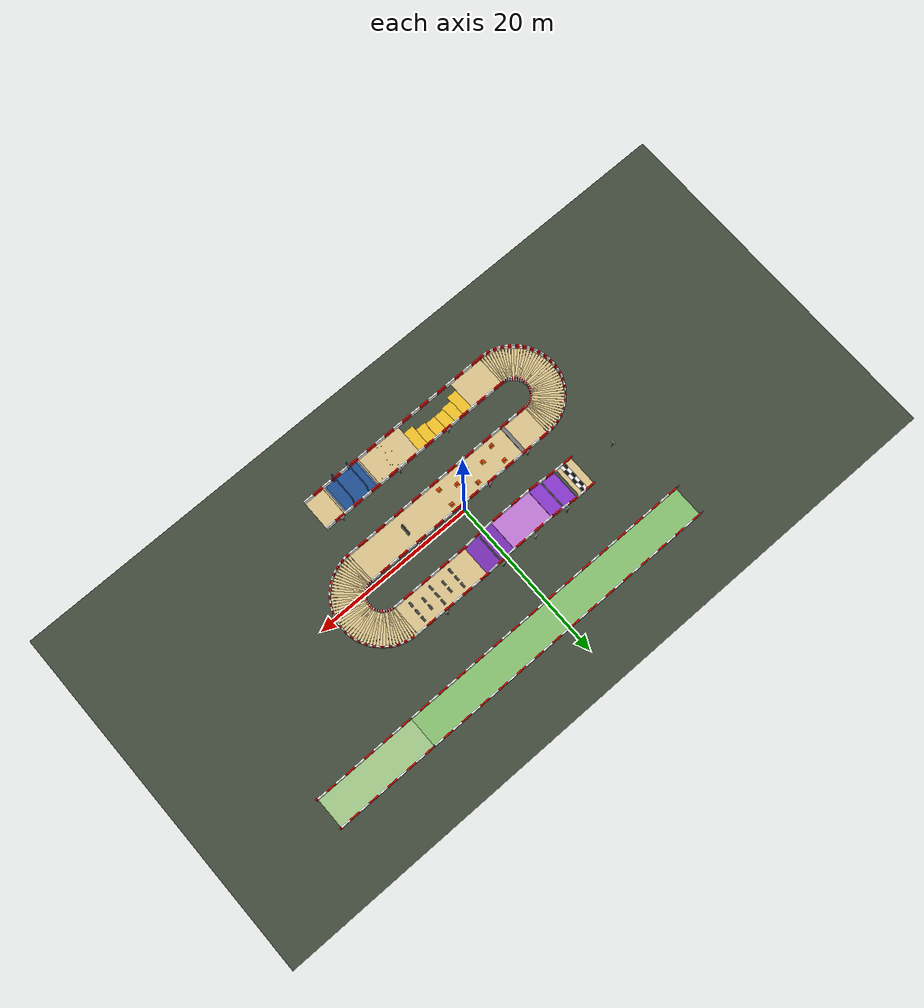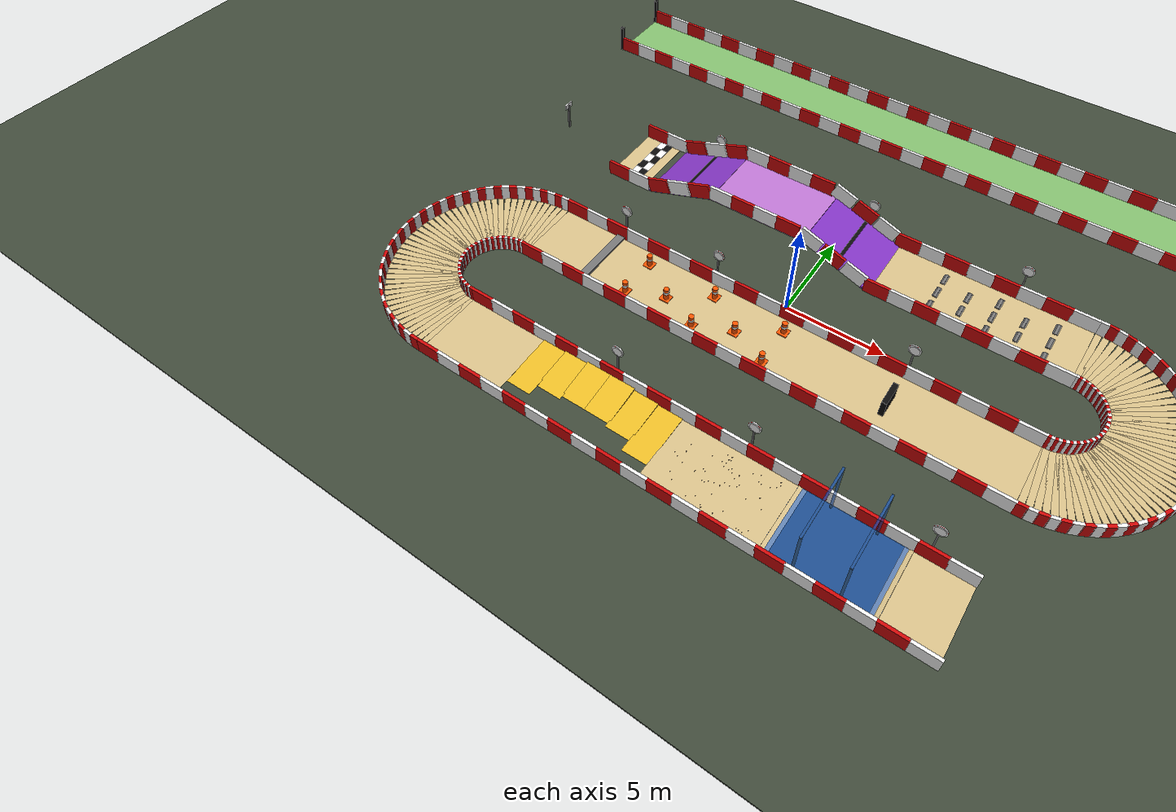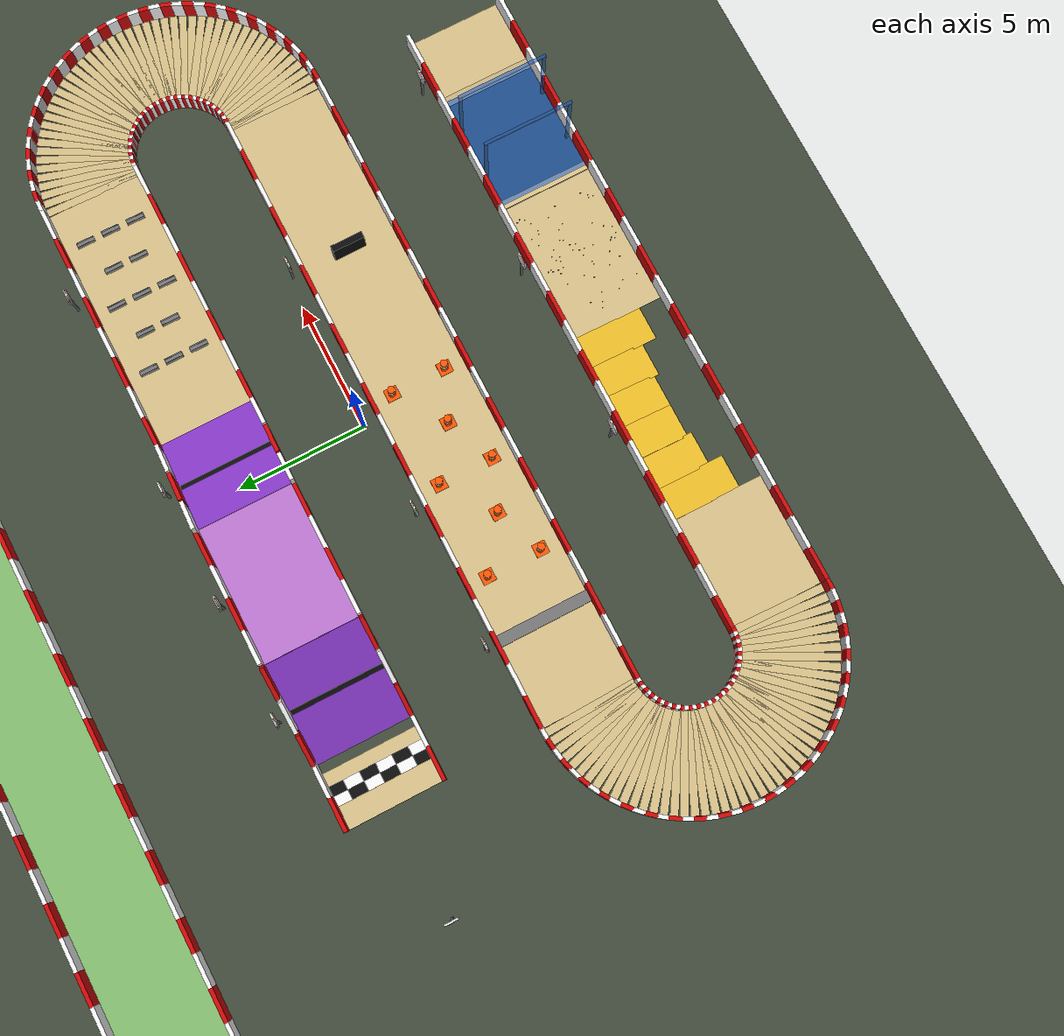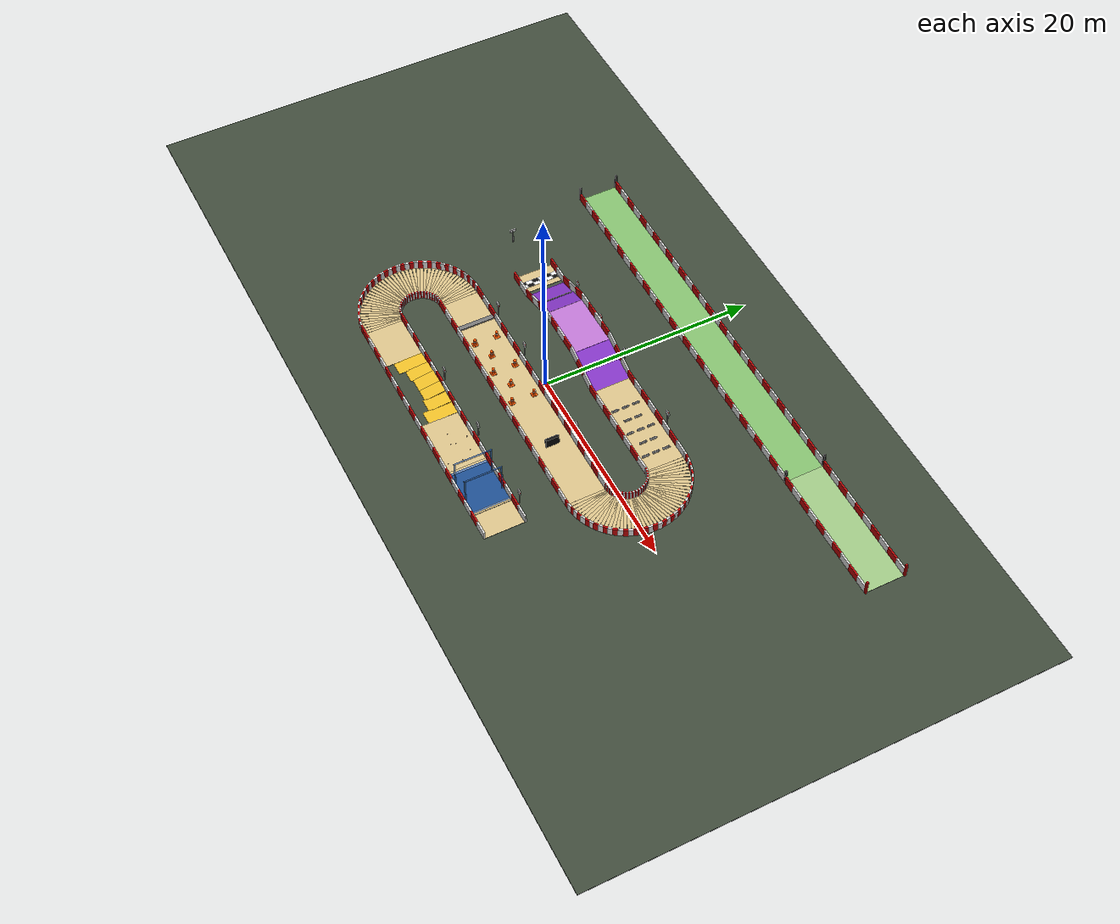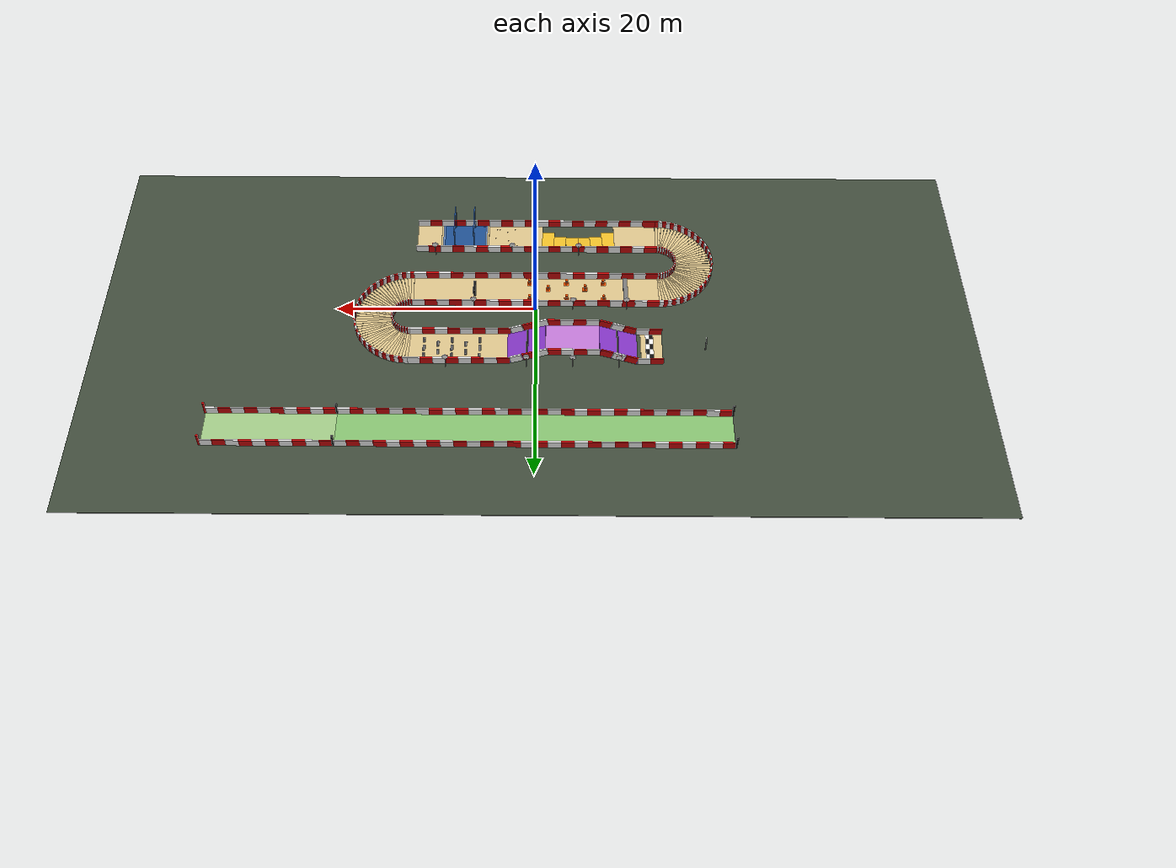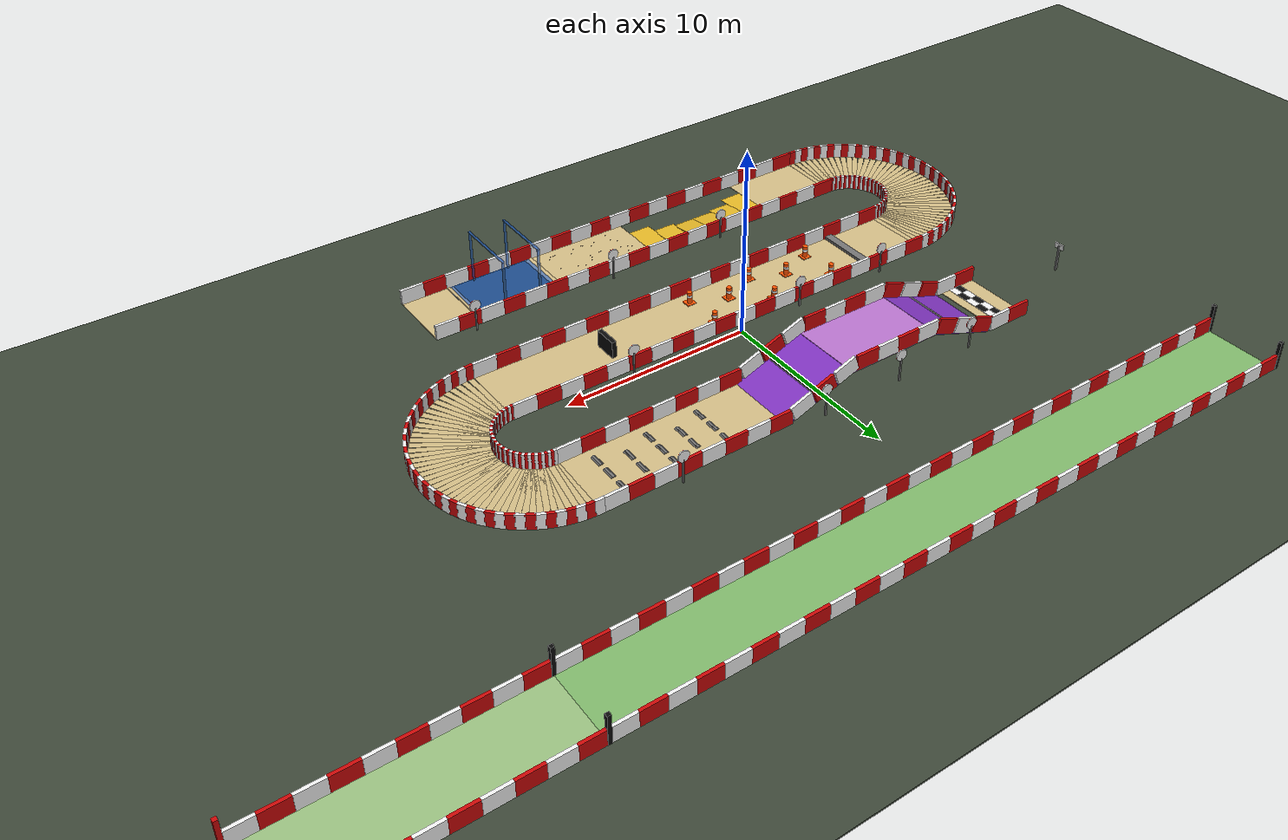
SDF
<?xml version="1.0"?>
<sdf version="1.6">
  <world name="evrenos_teknofest_2026">

    <!-- Real-scale course: world X/Y and horizontal geometry scaled by 1.25; Z/heights preserved. -->

    <physics name="default_physics" type="ode">
      <max_step_size>0.001</max_step_size>
      <real_time_factor>1.0</real_time_factor>
      <real_time_update_rate>1000</real_time_update_rate>
    </physics>

    <scene>
      <ambient>0.55 0.55 0.55 1</ambient>
      <background>0.72 0.82 0.92 1</background>
      <shadows>true</shadows>
    </scene>

    <include>
      <uri>model://sun</uri>
    </include>

    <model name="main_course">
      <static>true</static>

      <link name="arena_floor">
        <pose>0.000000 2.500000 -0.080000 0.000000 0.000000 0.000000</pose>
        <collision name="arena_floor_collision">
          <geometry><box><size>87.500000 43.750000 0.100000</size></box></geometry>
        </collision>
        <visual name="arena_floor_visual">
          <geometry><box><size>87.500000 43.750000 0.100000</size></box></geometry>

          <material>
            <ambient>0.24 0.28 0.22 1</ambient>
            <diffuse>0.24 0.28 0.22 1</diffuse>
          </material>
        </visual>
      </link>
      <link name="bottom_start_0">
        <pose>11.250000 -10.000000 -0.050000 0.000000 0.000000 0.000000</pose>
        <collision name="bottom_start_0_collision">
          <geometry><box><size>2.500000 3.750000 0.100000</size></box></geometry>
        </collision>
        <visual name="bottom_start_0_visual">
          <geometry><box><size>2.500000 3.750000 0.100000</size></box></geometry>

          <material>
            <ambient>0.82 0.73 0.52 1</ambient>
            <diffuse>0.82 0.73 0.52 1</diffuse>
          </material>
        </visual>
      </link>
      <link name="bottom_after_water_0">
        <pose>2.187500 -10.000000 -0.050000 0.000000 0.000000 0.000000</pose>
        <collision name="bottom_after_water_0_collision">
          <geometry><box><size>5.625000 3.750000 0.100000</size></box></geometry>
        </collision>
        <visual name="bottom_after_water_0_visual">
          <geometry><box><size>5.625000 3.750000 0.100000</size></box></geometry>

          <material>
            <ambient>0.82 0.73 0.52 1</ambient>
            <diffuse>0.82 0.73 0.52 1</diffuse>
          </material>
        </visual>
      </link>
      <link name="bottom_before_turn_0">
        <pose>-10.312500 -10.000000 -0.050000 0.000000 0.000000 0.000000</pose>
        <collision name="bottom_before_turn_0_collision">
          <geometry><box><size>4.375000 3.750000 0.100000</size></box></geometry>
        </collision>
        <visual name="bottom_before_turn_0_visual">
          <geometry><box><size>4.375000 3.750000 0.100000</size></box></geometry>

          <material>
            <ambient>0.82 0.73 0.52 1</ambient>
            <diffuse>0.82 0.73 0.52 1</diffuse>
          </material>
        </visual>
      </link>
      <link name="water_ramp_down">
        <pose>9.062500 -10.000000 -0.200000 0.000000 -0.210182 0.000000</pose>
        <collision name="water_ramp_down_collision">
          <geometry><box><size>1.917170 3.750000 0.100000</size></box></geometry>
        </collision>
        <visual name="water_ramp_down_visual">
          <geometry><box><size>1.917170 3.750000 0.100000</size></box></geometry>

          <material>
            <ambient>0.82 0.73 0.52 1</ambient>
            <diffuse>0.82 0.73 0.52 1</diffuse>
          </material>
        </visual>
      </link>
      <link name="water_basin_floor">
        <pose>7.500000 -10.000000 -0.450000 0.000000 0.000000 0.000000</pose>
        <collision name="water_basin_floor_collision">
          <geometry><box><size>1.250000 3.750000 0.100000</size></box></geometry>
        </collision>
        <visual name="water_basin_floor_visual">
          <geometry><box><size>1.250000 3.750000 0.100000</size></box></geometry>

          <material>
            <ambient>0.52 0.47 0.35 1</ambient>
            <diffuse>0.52 0.47 0.35 1</diffuse>
          </material>
        </visual>
      </link>
      <link name="water_ramp_up">
        <pose>5.937500 -10.000000 -0.200000 0.000000 0.210182 0.000000</pose>
        <collision name="water_ramp_up_collision">
          <geometry><box><size>1.917170 3.750000 0.100000</size></box></geometry>
        </collision>
        <visual name="water_ramp_up_visual">
          <geometry><box><size>1.917170 3.750000 0.100000</size></box></geometry>

          <material>
            <ambient>0.82 0.73 0.52 1</ambient>
            <diffuse>0.82 0.73 0.52 1</diffuse>
          </material>
        </visual>
      </link>
      <link name="water_surface">
        <pose>7.500000 -10.000000 0.005000 0.000000 0.000000 0.000000</pose>
        <visual name="water_surface_visual">
          <geometry><box><size>5.000000 3.625000 0.010000</size></box></geometry>

          <material>
            <ambient>0.05 0.35 0.85 0.55</ambient>
            <diffuse>0.05 0.35 0.85 0.55</diffuse>
          </material>
        </visual>
      </link>
      <link name="rain_post_5.2_-9.35">
        <pose>6.500000 -11.687500 1.450000 0.000000 0.000000 0.000000</pose>
        <collision name="rain_post_5.2_-9.35_collision">
          <geometry><box><size>0.100000 0.100000 2.900000</size></box></geometry>
        </collision>
        <visual name="rain_post_5.2_-9.35_visual">
          <geometry><box><size>0.100000 0.100000 2.900000</size></box></geometry>

          <material>
            <ambient>0.05 0.35 0.85 0.55</ambient>
            <diffuse>0.05 0.35 0.85 0.55</diffuse>
          </material>
        </visual>
      </link>
      <link name="rain_post_5.2_-6.65">
        <pose>6.500000 -8.312500 1.450000 0.000000 0.000000 0.000000</pose>
        <collision name="rain_post_5.2_-6.65_collision">
          <geometry><box><size>0.100000 0.100000 2.900000</size></box></geometry>
        </collision>
        <visual name="rain_post_5.2_-6.65_visual">
          <geometry><box><size>0.100000 0.100000 2.900000</size></box></geometry>

          <material>
            <ambient>0.05 0.35 0.85 0.55</ambient>
            <diffuse>0.05 0.35 0.85 0.55</diffuse>
          </material>
        </visual>
      </link>
      <link name="rain_post_6.8_-9.35">
        <pose>8.500000 -11.687500 1.450000 0.000000 0.000000 0.000000</pose>
        <collision name="rain_post_6.8_-9.35_collision">
          <geometry><box><size>0.100000 0.100000 2.900000</size></box></geometry>
        </collision>
        <visual name="rain_post_6.8_-9.35_visual">
          <geometry><box><size>0.100000 0.100000 2.900000</size></box></geometry>

          <material>
            <ambient>0.05 0.35 0.85 0.55</ambient>
            <diffuse>0.05 0.35 0.85 0.55</diffuse>
          </material>
        </visual>
      </link>
      <link name="rain_post_6.8_-6.65">
        <pose>8.500000 -8.312500 1.450000 0.000000 0.000000 0.000000</pose>
        <collision name="rain_post_6.8_-6.65_collision">
          <geometry><box><size>0.100000 0.100000 2.900000</size></box></geometry>
        </collision>
        <visual name="rain_post_6.8_-6.65_visual">
          <geometry><box><size>0.100000 0.100000 2.900000</size></box></geometry>

          <material>
            <ambient>0.05 0.35 0.85 0.55</ambient>
            <diffuse>0.05 0.35 0.85 0.55</diffuse>
          </material>
        </visual>
      </link>
      <link name="rain_cross_5.2">
        <pose>6.500000 -10.000000 2.900000 0.000000 0.000000 0.000000</pose>
        <collision name="rain_cross_5.2_collision">
          <geometry><box><size>0.100000 3.500000 0.080000</size></box></geometry>
        </collision>
        <visual name="rain_cross_5.2_visual">
          <geometry><box><size>0.100000 3.500000 0.080000</size></box></geometry>

          <material>
            <ambient>0.05 0.35 0.85 0.55</ambient>
            <diffuse>0.05 0.35 0.85 0.55</diffuse>
          </material>
        </visual>
      </link>
      <link name="rain_cross_6.8">
        <pose>8.500000 -10.000000 2.900000 0.000000 0.000000 0.000000</pose>
        <collision name="rain_cross_6.8_collision">
          <geometry><box><size>0.100000 3.500000 0.080000</size></box></geometry>
        </collision>
        <visual name="rain_cross_6.8_visual">
          <geometry><box><size>0.100000 3.500000 0.080000</size></box></geometry>

          <material>
            <ambient>0.05 0.35 0.85 0.55</ambient>
            <diffuse>0.05 0.35 0.85 0.55</diffuse>
          </material>
        </visual>
      </link>
      <link name="gravel_0">
        <pose>0.536000 -9.991875 0.010300 0.000000 0.000000 0.000000</pose>
        <collision name="gravel_0_collision">
          <geometry><sphere><radius>0.0187</radius></sphere></geometry>
        </collision>
        <visual name="gravel_0_visual">
          <geometry><sphere><radius>0.0187</radius></sphere></geometry>

          <material>
            <ambient>0.43 0.35 0.27 1</ambient>
            <diffuse>0.43 0.35 0.27 1</diffuse>
          </material>
        </visual>
      </link>
      <link name="gravel_1">
        <pose>3.870000 -11.291375 0.008200 0.000000 0.000000 0.000000</pose>
        <collision name="gravel_1_collision">
          <geometry><sphere><radius>0.0149</radius></sphere></geometry>
        </collision>
        <visual name="gravel_1_visual">
          <geometry><sphere><radius>0.0149</radius></sphere></geometry>

          <material>
            <ambient>0.43 0.35 0.27 1</ambient>
            <diffuse>0.43 0.35 0.27 1</diffuse>
          </material>
        </visual>
      </link>
      <link name="gravel_2">
        <pose>2.704625 -9.816125 0.012200 0.000000 0.000000 0.000000</pose>
        <collision name="gravel_2_collision">
          <geometry><sphere><radius>0.0222</radius></sphere></geometry>
        </collision>
        <visual name="gravel_2_visual">
          <geometry><sphere><radius>0.0222</radius></sphere></geometry>

          <material>
            <ambient>0.43 0.35 0.27 1</ambient>
            <diffuse>0.43 0.35 0.27 1</diffuse>
          </material>
        </visual>
      </link>
      <link name="gravel_3">
        <pose>2.465125 -9.250750 0.012100 0.000000 0.000000 0.000000</pose>
        <collision name="gravel_3_collision">
          <geometry><sphere><radius>0.0220</radius></sphere></geometry>
        </collision>
        <visual name="gravel_3_visual">
          <geometry><sphere><radius>0.0220</radius></sphere></geometry>

          <material>
            <ambient>0.43 0.35 0.27 1</ambient>
            <diffuse>0.43 0.35 0.27 1</diffuse>
          </material>
        </visual>
      </link>
      <link name="gravel_4">
        <pose>3.379625 -9.718750 0.008300 0.000000 0.000000 0.000000</pose>
        <collision name="gravel_4_collision">
          <geometry><sphere><radius>0.0151</radius></sphere></geometry>
        </collision>
        <visual name="gravel_4_visual">
          <geometry><sphere><radius>0.0151</radius></sphere></geometry>

          <material>
            <ambient>0.43 0.35 0.27 1</ambient>
            <diffuse>0.43 0.35 0.27 1</diffuse>
          </material>
        </visual>
      </link>
      <link name="gravel_5">
        <pose>2.763875 -11.265125 0.012400 0.000000 0.000000 0.000000</pose>
        <collision name="gravel_5_collision">
          <geometry><sphere><radius>0.0226</radius></sphere></geometry>
        </collision>
        <visual name="gravel_5_visual">
          <geometry><sphere><radius>0.0226</radius></sphere></geometry>

          <material>
            <ambient>0.43 0.35 0.27 1</ambient>
            <diffuse>0.43 0.35 0.27 1</diffuse>
          </material>
        </visual>
      </link>
      <link name="gravel_6">
        <pose>2.023500 -8.977000 0.011500 0.000000 0.000000 0.000000</pose>
        <collision name="gravel_6_collision">
          <geometry><sphere><radius>0.0209</radius></sphere></geometry>
        </collision>
        <visual name="gravel_6_visual">
          <geometry><sphere><radius>0.0209</radius></sphere></geometry>

          <material>
            <ambient>0.43 0.35 0.27 1</ambient>
            <diffuse>0.43 0.35 0.27 1</diffuse>
          </material>
        </visual>
      </link>
      <link name="gravel_7">
        <pose>3.057250 -10.941750 0.008400 0.000000 0.000000 0.000000</pose>
        <collision name="gravel_7_collision">
          <geometry><sphere><radius>0.0153</radius></sphere></geometry>
        </collision>
        <visual name="gravel_7_visual">
          <geometry><sphere><radius>0.0153</radius></sphere></geometry>

          <material>
            <ambient>0.43 0.35 0.27 1</ambient>
            <diffuse>0.43 0.35 0.27 1</diffuse>
          </material>
        </visual>
      </link>
      <link name="gravel_8">
        <pose>4.409625 -8.604750 0.012400 0.000000 0.000000 0.000000</pose>
        <collision name="gravel_8_collision">
          <geometry><sphere><radius>0.0225</radius></sphere></geometry>
        </collision>
        <visual name="gravel_8_visual">
          <geometry><sphere><radius>0.0225</radius></sphere></geometry>

          <material>
            <ambient>0.43 0.35 0.27 1</ambient>
            <diffuse>0.43 0.35 0.27 1</diffuse>
          </material>
        </visual>
      </link>
      <link name="gravel_9">
        <pose>4.498500 -9.955875 0.007100 0.000000 0.000000 0.000000</pose>
        <collision name="gravel_9_collision">
          <geometry><sphere><radius>0.0130</radius></sphere></geometry>
        </collision>
        <visual name="gravel_9_visual">
          <geometry><sphere><radius>0.0130</radius></sphere></geometry>

          <material>
            <ambient>0.43 0.35 0.27 1</ambient>
            <diffuse>0.43 0.35 0.27 1</diffuse>
          </material>
        </visual>
      </link>
      <link name="gravel_10">
        <pose>1.531750 -9.813250 0.008700 0.000000 0.000000 0.000000</pose>
        <collision name="gravel_10_collision">
          <geometry><sphere><radius>0.0158</radius></sphere></geometry>
        </collision>
        <visual name="gravel_10_visual">
          <geometry><sphere><radius>0.0158</radius></sphere></geometry>

          <material>
            <ambient>0.43 0.35 0.27 1</ambient>
            <diffuse>0.43 0.35 0.27 1</diffuse>
          </material>
        </visual>
      </link>
      <link name="gravel_11">
        <pose>2.058500 -8.776500 0.011600 0.000000 0.000000 0.000000</pose>
        <collision name="gravel_11_collision">
          <geometry><sphere><radius>0.0212</radius></sphere></geometry>
        </collision>
        <visual name="gravel_11_visual">
          <geometry><sphere><radius>0.0212</radius></sphere></geometry>

          <material>
            <ambient>0.43 0.35 0.27 1</ambient>
            <diffuse>0.43 0.35 0.27 1</diffuse>
          </material>
        </visual>
      </link>
      <link name="gravel_12">
        <pose>2.598375 -11.544625 0.011700 0.000000 0.000000 0.000000</pose>
        <collision name="gravel_12_collision">
          <geometry><sphere><radius>0.0212</radius></sphere></geometry>
        </collision>
        <visual name="gravel_12_visual">
          <geometry><sphere><radius>0.0212</radius></sphere></geometry>

          <material>
            <ambient>0.43 0.35 0.27 1</ambient>
            <diffuse>0.43 0.35 0.27 1</diffuse>
          </material>
        </visual>
      </link>
      <link name="gravel_13">
        <pose>1.636000 -10.252750 0.009500 0.000000 0.000000 0.000000</pose>
        <collision name="gravel_13_collision">
          <geometry><sphere><radius>0.0172</radius></sphere></geometry>
        </collision>
        <visual name="gravel_13_visual">
          <geometry><sphere><radius>0.0172</radius></sphere></geometry>

          <material>
            <ambient>0.43 0.35 0.27 1</ambient>
            <diffuse>0.43 0.35 0.27 1</diffuse>
          </material>
        </visual>
      </link>
      <link name="gravel_14">
        <pose>2.635750 -10.005000 0.007400 0.000000 0.000000 0.000000</pose>
        <collision name="gravel_14_collision">
          <geometry><sphere><radius>0.0135</radius></sphere></geometry>
        </collision>
        <visual name="gravel_14_visual">
          <geometry><sphere><radius>0.0135</radius></sphere></geometry>

          <material>
            <ambient>0.43 0.35 0.27 1</ambient>
            <diffuse>0.43 0.35 0.27 1</diffuse>
          </material>
        </visual>
      </link>
      <link name="gravel_15">
        <pose>2.278625 -9.187000 0.010900 0.000000 0.000000 0.000000</pose>
        <collision name="gravel_15_collision">
          <geometry><sphere><radius>0.0198</radius></sphere></geometry>
        </collision>
        <visual name="gravel_15_visual">
          <geometry><sphere><radius>0.0198</radius></sphere></geometry>

          <material>
            <ambient>0.43 0.35 0.27 1</ambient>
            <diffuse>0.43 0.35 0.27 1</diffuse>
          </material>
        </visual>
      </link>
      <link name="gravel_16">
        <pose>2.209625 -8.645500 0.008400 0.000000 0.000000 0.000000</pose>
        <collision name="gravel_16_collision">
          <geometry><sphere><radius>0.0154</radius></sphere></geometry>
        </collision>
        <visual name="gravel_16_visual">
          <geometry><sphere><radius>0.0154</radius></sphere></geometry>

          <material>
            <ambient>0.43 0.35 0.27 1</ambient>
            <diffuse>0.43 0.35 0.27 1</diffuse>
          </material>
        </visual>
      </link>
      <link name="gravel_17">
        <pose>1.889875 -8.614750 0.010000 0.000000 0.000000 0.000000</pose>
        <collision name="gravel_17_collision">
          <geometry><sphere><radius>0.0182</radius></sphere></geometry>
        </collision>
        <visual name="gravel_17_visual">
          <geometry><sphere><radius>0.0182</radius></sphere></geometry>

          <material>
            <ambient>0.43 0.35 0.27 1</ambient>
            <diffuse>0.43 0.35 0.27 1</diffuse>
          </material>
        </visual>
      </link>
      <link name="gravel_18">
        <pose>2.331000 -11.542500 0.008200 0.000000 0.000000 0.000000</pose>
        <collision name="gravel_18_collision">
          <geometry><sphere><radius>0.0149</radius></sphere></geometry>
        </collision>
        <visual name="gravel_18_visual">
          <geometry><sphere><radius>0.0149</radius></sphere></geometry>

          <material>
            <ambient>0.43 0.35 0.27 1</ambient>
            <diffuse>0.43 0.35 0.27 1</diffuse>
          </material>
        </visual>
      </link>
      <link name="gravel_19">
        <pose>0.580500 -11.466125 0.011600 0.000000 0.000000 0.000000</pose>
        <collision name="gravel_19_collision">
          <geometry><sphere><radius>0.0212</radius></sphere></geometry>
        </collision>
        <visual name="gravel_19_visual">
          <geometry><sphere><radius>0.0212</radius></sphere></geometry>

          <material>
            <ambient>0.43 0.35 0.27 1</ambient>
            <diffuse>0.43 0.35 0.27 1</diffuse>
          </material>
        </visual>
      </link>
      <link name="gravel_20">
        <pose>3.990750 -11.291625 0.011000 0.000000 0.000000 0.000000</pose>
        <collision name="gravel_20_collision">
          <geometry><sphere><radius>0.0201</radius></sphere></geometry>
        </collision>
        <visual name="gravel_20_visual">
          <geometry><sphere><radius>0.0201</radius></sphere></geometry>

          <material>
            <ambient>0.43 0.35 0.27 1</ambient>
            <diffuse>0.43 0.35 0.27 1</diffuse>
          </material>
        </visual>
      </link>
      <link name="gravel_21">
        <pose>2.115125 -10.058125 0.008200 0.000000 0.000000 0.000000</pose>
        <collision name="gravel_21_collision">
          <geometry><sphere><radius>0.0150</radius></sphere></geometry>
        </collision>
        <visual name="gravel_21_visual">
          <geometry><sphere><radius>0.0150</radius></sphere></geometry>

          <material>
            <ambient>0.43 0.35 0.27 1</ambient>
            <diffuse>0.43 0.35 0.27 1</diffuse>
          </material>
        </visual>
      </link>
      <link name="gravel_22">
        <pose>3.986625 -9.588375 0.009900 0.000000 0.000000 0.000000</pose>
        <collision name="gravel_22_collision">
          <geometry><sphere><radius>0.0179</radius></sphere></geometry>
        </collision>
        <visual name="gravel_22_visual">
          <geometry><sphere><radius>0.0179</radius></sphere></geometry>

          <material>
            <ambient>0.43 0.35 0.27 1</ambient>
            <diffuse>0.43 0.35 0.27 1</diffuse>
          </material>
        </visual>
      </link>
      <link name="gravel_23">
        <pose>2.112375 -8.604250 0.013700 0.000000 0.000000 0.000000</pose>
        <collision name="gravel_23_collision">
          <geometry><sphere><radius>0.0248</radius></sphere></geometry>
        </collision>
        <visual name="gravel_23_visual">
          <geometry><sphere><radius>0.0248</radius></sphere></geometry>

          <material>
            <ambient>0.43 0.35 0.27 1</ambient>
            <diffuse>0.43 0.35 0.27 1</diffuse>
          </material>
        </visual>
      </link>
      <link name="gravel_24">
        <pose>2.455375 -9.805625 0.011400 0.000000 0.000000 0.000000</pose>
        <collision name="gravel_24_collision">
          <geometry><sphere><radius>0.0207</radius></sphere></geometry>
        </collision>
        <visual name="gravel_24_visual">
          <geometry><sphere><radius>0.0207</radius></sphere></geometry>

          <material>
            <ambient>0.43 0.35 0.27 1</ambient>
            <diffuse>0.43 0.35 0.27 1</diffuse>
          </material>
        </visual>
      </link>
      <link name="gravel_25">
        <pose>1.384375 -9.025625 0.010200 0.000000 0.000000 0.000000</pose>
        <collision name="gravel_25_collision">
          <geometry><sphere><radius>0.0185</radius></sphere></geometry>
        </collision>
        <visual name="gravel_25_visual">
          <geometry><sphere><radius>0.0185</radius></sphere></geometry>

          <material>
            <ambient>0.43 0.35 0.27 1</ambient>
            <diffuse>0.43 0.35 0.27 1</diffuse>
          </material>
        </visual>
      </link>
      <link name="gravel_26">
        <pose>2.155000 -8.750500 0.009700 0.000000 0.000000 0.000000</pose>
        <collision name="gravel_26_collision">
          <geometry><sphere><radius>0.0176</radius></sphere></geometry>
        </collision>
        <visual name="gravel_26_visual">
          <geometry><sphere><radius>0.0176</radius></sphere></geometry>

          <material>
            <ambient>0.43 0.35 0.27 1</ambient>
            <diffuse>0.43 0.35 0.27 1</diffuse>
          </material>
        </visual>
      </link>
      <link name="gravel_27">
        <pose>1.324625 -10.750625 0.006800 0.000000 0.000000 0.000000</pose>
        <collision name="gravel_27_collision">
          <geometry><sphere><radius>0.0124</radius></sphere></geometry>
        </collision>
        <visual name="gravel_27_visual">
          <geometry><sphere><radius>0.0124</radius></sphere></geometry>

          <material>
            <ambient>0.43 0.35 0.27 1</ambient>
            <diffuse>0.43 0.35 0.27 1</diffuse>
          </material>
        </visual>
      </link>
      <link name="gravel_28">
        <pose>2.950375 -9.683875 0.009900 0.000000 0.000000 0.000000</pose>
        <collision name="gravel_28_collision">
          <geometry><sphere><radius>0.0180</radius></sphere></geometry>
        </collision>
        <visual name="gravel_28_visual">
          <geometry><sphere><radius>0.0180</radius></sphere></geometry>

          <material>
            <ambient>0.43 0.35 0.27 1</ambient>
            <diffuse>0.43 0.35 0.27 1</diffuse>
          </material>
        </visual>
      </link>
      <link name="gravel_29">
        <pose>2.353000 -10.034125 0.013200 0.000000 0.000000 0.000000</pose>
        <collision name="gravel_29_collision">
          <geometry><sphere><radius>0.0240</radius></sphere></geometry>
        </collision>
        <visual name="gravel_29_visual">
          <geometry><sphere><radius>0.0240</radius></sphere></geometry>

          <material>
            <ambient>0.43 0.35 0.27 1</ambient>
            <diffuse>0.43 0.35 0.27 1</diffuse>
          </material>
        </visual>
      </link>
      <link name="gravel_30">
        <pose>1.170500 -10.046875 0.010300 0.000000 0.000000 0.000000</pose>
        <collision name="gravel_30_collision">
          <geometry><sphere><radius>0.0186</radius></sphere></geometry>
        </collision>
        <visual name="gravel_30_visual">
          <geometry><sphere><radius>0.0186</radius></sphere></geometry>

          <material>
            <ambient>0.43 0.35 0.27 1</ambient>
            <diffuse>0.43 0.35 0.27 1</diffuse>
          </material>
        </visual>
      </link>
      <link name="gravel_31">
        <pose>3.717750 -8.999125 0.010600 0.000000 0.000000 0.000000</pose>
        <collision name="gravel_31_collision">
          <geometry><sphere><radius>0.0193</radius></sphere></geometry>
        </collision>
        <visual name="gravel_31_visual">
          <geometry><sphere><radius>0.0193</radius></sphere></geometry>

          <material>
            <ambient>0.43 0.35 0.27 1</ambient>
            <diffuse>0.43 0.35 0.27 1</diffuse>
          </material>
        </visual>
      </link>
      <link name="gravel_32">
        <pose>4.082750 -8.923000 0.008900 0.000000 0.000000 0.000000</pose>
        <collision name="gravel_32_collision">
          <geometry><sphere><radius>0.0161</radius></sphere></geometry>
        </collision>
        <visual name="gravel_32_visual">
          <geometry><sphere><radius>0.0161</radius></sphere></geometry>

          <material>
            <ambient>0.43 0.35 0.27 1</ambient>
            <diffuse>0.43 0.35 0.27 1</diffuse>
          </material>
        </visual>
      </link>
      <link name="gravel_33">
        <pose>4.125625 -11.305250 0.011500 0.000000 0.000000 0.000000</pose>
        <collision name="gravel_33_collision">
          <geometry><sphere><radius>0.0210</radius></sphere></geometry>
        </collision>
        <visual name="gravel_33_visual">
          <geometry><sphere><radius>0.0210</radius></sphere></geometry>

          <material>
            <ambient>0.43 0.35 0.27 1</ambient>
            <diffuse>0.43 0.35 0.27 1</diffuse>
          </material>
        </visual>
      </link>
      <link name="gravel_34">
        <pose>3.532875 -9.950625 0.009800 0.000000 0.000000 0.000000</pose>
        <collision name="gravel_34_collision">
          <geometry><sphere><radius>0.0179</radius></sphere></geometry>
        </collision>
        <visual name="gravel_34_visual">
          <geometry><sphere><radius>0.0179</radius></sphere></geometry>

          <material>
            <ambient>0.43 0.35 0.27 1</ambient>
            <diffuse>0.43 0.35 0.27 1</diffuse>
          </material>
        </visual>
      </link>
      <link name="gravel_35">
        <pose>4.343750 -8.481375 0.012600 0.000000 0.000000 0.000000</pose>
        <collision name="gravel_35_collision">
          <geometry><sphere><radius>0.0230</radius></sphere></geometry>
        </collision>
        <visual name="gravel_35_visual">
          <geometry><sphere><radius>0.0230</radius></sphere></geometry>

          <material>
            <ambient>0.43 0.35 0.27 1</ambient>
            <diffuse>0.43 0.35 0.27 1</diffuse>
          </material>
        </visual>
      </link>
      <link name="gravel_36">
        <pose>2.156125 -11.416000 0.008500 0.000000 0.000000 0.000000</pose>
        <collision name="gravel_36_collision">
          <geometry><sphere><radius>0.0155</radius></sphere></geometry>
        </collision>
        <visual name="gravel_36_visual">
          <geometry><sphere><radius>0.0155</radius></sphere></geometry>

          <material>
            <ambient>0.43 0.35 0.27 1</ambient>
            <diffuse>0.43 0.35 0.27 1</diffuse>
          </material>
        </visual>
      </link>
      <link name="gravel_37">
        <pose>2.242875 -11.310875 0.011900 0.000000 0.000000 0.000000</pose>
        <collision name="gravel_37_collision">
          <geometry><sphere><radius>0.0217</radius></sphere></geometry>
        </collision>
        <visual name="gravel_37_visual">
          <geometry><sphere><radius>0.0217</radius></sphere></geometry>

          <material>
            <ambient>0.43 0.35 0.27 1</ambient>
            <diffuse>0.43 0.35 0.27 1</diffuse>
          </material>
        </visual>
      </link>
      <link name="gravel_38">
        <pose>1.850875 -10.164500 0.006700 0.000000 0.000000 0.000000</pose>
        <collision name="gravel_38_collision">
          <geometry><sphere><radius>0.0122</radius></sphere></geometry>
        </collision>
        <visual name="gravel_38_visual">
          <geometry><sphere><radius>0.0122</radius></sphere></geometry>

          <material>
            <ambient>0.43 0.35 0.27 1</ambient>
            <diffuse>0.43 0.35 0.27 1</diffuse>
          </material>
        </visual>
      </link>
      <link name="gravel_39">
        <pose>0.001000 -9.737875 0.013300 0.000000 0.000000 0.000000</pose>
        <collision name="gravel_39_collision">
          <geometry><sphere><radius>0.0241</radius></sphere></geometry>
        </collision>
        <visual name="gravel_39_visual">
          <geometry><sphere><radius>0.0241</radius></sphere></geometry>

          <material>
            <ambient>0.43 0.35 0.27 1</ambient>
            <diffuse>0.43 0.35 0.27 1</diffuse>
          </material>
        </visual>
      </link>
      <link name="gravel_40">
        <pose>0.373750 -9.045250 0.008400 0.000000 0.000000 0.000000</pose>
        <collision name="gravel_40_collision">
          <geometry><sphere><radius>0.0152</radius></sphere></geometry>
        </collision>
        <visual name="gravel_40_visual">
          <geometry><sphere><radius>0.0152</radius></sphere></geometry>

          <material>
            <ambient>0.43 0.35 0.27 1</ambient>
            <diffuse>0.43 0.35 0.27 1</diffuse>
          </material>
        </visual>
      </link>
      <link name="gravel_41">
        <pose>2.794875 -9.181500 0.013400 0.000000 0.000000 0.000000</pose>
        <collision name="gravel_41_collision">
          <geometry><sphere><radius>0.0244</radius></sphere></geometry>
        </collision>
        <visual name="gravel_41_visual">
          <geometry><sphere><radius>0.0244</radius></sphere></geometry>

          <material>
            <ambient>0.43 0.35 0.27 1</ambient>
            <diffuse>0.43 0.35 0.27 1</diffuse>
          </material>
        </visual>
      </link>
      <link name="gravel_42">
        <pose>3.008125 -9.559875 0.007700 0.000000 0.000000 0.000000</pose>
        <collision name="gravel_42_collision">
          <geometry><sphere><radius>0.0140</radius></sphere></geometry>
        </collision>
        <visual name="gravel_42_visual">
          <geometry><sphere><radius>0.0140</radius></sphere></geometry>

          <material>
            <ambient>0.43 0.35 0.27 1</ambient>
            <diffuse>0.43 0.35 0.27 1</diffuse>
          </material>
        </visual>
      </link>
      <link name="gravel_43">
        <pose>1.410500 -9.730000 0.012100 0.000000 0.000000 0.000000</pose>
        <collision name="gravel_43_collision">
          <geometry><sphere><radius>0.0220</radius></sphere></geometry>
        </collision>
        <visual name="gravel_43_visual">
          <geometry><sphere><radius>0.0220</radius></sphere></geometry>

          <material>
            <ambient>0.43 0.35 0.27 1</ambient>
            <diffuse>0.43 0.35 0.27 1</diffuse>
          </material>
        </visual>
      </link>
      <link name="gravel_44">
        <pose>4.274750 -10.026000 0.011800 0.000000 0.000000 0.000000</pose>
        <collision name="gravel_44_collision">
          <geometry><sphere><radius>0.0214</radius></sphere></geometry>
        </collision>
        <visual name="gravel_44_visual">
          <geometry><sphere><radius>0.0214</radius></sphere></geometry>

          <material>
            <ambient>0.43 0.35 0.27 1</ambient>
            <diffuse>0.43 0.35 0.27 1</diffuse>
          </material>
        </visual>
      </link>
      <link name="gravel_45">
        <pose>0.606875 -10.900500 0.010800 0.000000 0.000000 0.000000</pose>
        <collision name="gravel_45_collision">
          <geometry><sphere><radius>0.0196</radius></sphere></geometry>
        </collision>
        <visual name="gravel_45_visual">
          <geometry><sphere><radius>0.0196</radius></sphere></geometry>

          <material>
            <ambient>0.43 0.35 0.27 1</ambient>
            <diffuse>0.43 0.35 0.27 1</diffuse>
          </material>
        </visual>
      </link>
      <link name="gravel_46">
        <pose>4.312250 -8.778000 0.010200 0.000000 0.000000 0.000000</pose>
        <collision name="gravel_46_collision">
          <geometry><sphere><radius>0.0186</radius></sphere></geometry>
        </collision>
        <visual name="gravel_46_visual">
          <geometry><sphere><radius>0.0186</radius></sphere></geometry>

          <material>
            <ambient>0.43 0.35 0.27 1</ambient>
            <diffuse>0.43 0.35 0.27 1</diffuse>
          </material>
        </visual>
      </link>
      <link name="gravel_47">
        <pose>0.380000 -9.452250 0.013300 0.000000 0.000000 0.000000</pose>
        <collision name="gravel_47_collision">
          <geometry><sphere><radius>0.0242</radius></sphere></geometry>
        </collision>
        <visual name="gravel_47_visual">
          <geometry><sphere><radius>0.0242</radius></sphere></geometry>

          <material>
            <ambient>0.43 0.35 0.27 1</ambient>
            <diffuse>0.43 0.35 0.27 1</diffuse>
          </material>
        </visual>
      </link>
      <link name="gravel_48">
        <pose>3.525500 -8.651250 0.008800 0.000000 0.000000 0.000000</pose>
        <collision name="gravel_48_collision">
          <geometry><sphere><radius>0.0160</radius></sphere></geometry>
        </collision>
        <visual name="gravel_48_visual">
          <geometry><sphere><radius>0.0160</radius></sphere></geometry>

          <material>
            <ambient>0.43 0.35 0.27 1</ambient>
            <diffuse>0.43 0.35 0.27 1</diffuse>
          </material>
        </visual>
      </link>
      <link name="gravel_49">
        <pose>1.854125 -8.999000 0.010300 0.000000 0.000000 0.000000</pose>
        <collision name="gravel_49_collision">
          <geometry><sphere><radius>0.0188</radius></sphere></geometry>
        </collision>
        <visual name="gravel_49_visual">
          <geometry><sphere><radius>0.0188</radius></sphere></geometry>

          <material>
            <ambient>0.43 0.35 0.27 1</ambient>
            <diffuse>0.43 0.35 0.27 1</diffuse>
          </material>
        </visual>
      </link>
      <link name="gravel_50">
        <pose>0.885125 -11.579125 0.007400 0.000000 0.000000 0.000000</pose>
        <collision name="gravel_50_collision">
          <geometry><sphere><radius>0.0134</radius></sphere></geometry>
        </collision>
        <visual name="gravel_50_visual">
          <geometry><sphere><radius>0.0134</radius></sphere></geometry>

          <material>
            <ambient>0.43 0.35 0.27 1</ambient>
            <diffuse>0.43 0.35 0.27 1</diffuse>
          </material>
        </visual>
      </link>
      <link name="gravel_51">
        <pose>3.995000 -11.458000 0.009100 0.000000 0.000000 0.000000</pose>
        <collision name="gravel_51_collision">
          <geometry><sphere><radius>0.0165</radius></sphere></geometry>
        </collision>
        <visual name="gravel_51_visual">
          <geometry><sphere><radius>0.0165</radius></sphere></geometry>

          <material>
            <ambient>0.43 0.35 0.27 1</ambient>
            <diffuse>0.43 0.35 0.27 1</diffuse>
          </material>
        </visual>
      </link>
      <link name="gravel_52">
        <pose>1.590375 -9.124000 0.006800 0.000000 0.000000 0.000000</pose>
        <collision name="gravel_52_collision">
          <geometry><sphere><radius>0.0123</radius></sphere></geometry>
        </collision>
        <visual name="gravel_52_visual">
          <geometry><sphere><radius>0.0123</radius></sphere></geometry>

          <material>
            <ambient>0.43 0.35 0.27 1</ambient>
            <diffuse>0.43 0.35 0.27 1</diffuse>
          </material>
        </visual>
      </link>
      <link name="gravel_53">
        <pose>2.296750 -10.559750 0.008800 0.000000 0.000000 0.000000</pose>
        <collision name="gravel_53_collision">
          <geometry><sphere><radius>0.0159</radius></sphere></geometry>
        </collision>
        <visual name="gravel_53_visual">
          <geometry><sphere><radius>0.0159</radius></sphere></geometry>

          <material>
            <ambient>0.43 0.35 0.27 1</ambient>
            <diffuse>0.43 0.35 0.27 1</diffuse>
          </material>
        </visual>
      </link>
      <link name="gravel_54">
        <pose>1.467250 -11.230500 0.013400 0.000000 0.000000 0.000000</pose>
        <collision name="gravel_54_collision">
          <geometry><sphere><radius>0.0243</radius></sphere></geometry>
        </collision>
        <visual name="gravel_54_visual">
          <geometry><sphere><radius>0.0243</radius></sphere></geometry>

          <material>
            <ambient>0.43 0.35 0.27 1</ambient>
            <diffuse>0.43 0.35 0.27 1</diffuse>
          </material>
        </visual>
      </link>
      <link name="gravel_55">
        <pose>2.572250 -9.009000 0.007700 0.000000 0.000000 0.000000</pose>
        <collision name="gravel_55_collision">
          <geometry><sphere><radius>0.0140</radius></sphere></geometry>
        </collision>
        <visual name="gravel_55_visual">
          <geometry><sphere><radius>0.0140</radius></sphere></geometry>

          <material>
            <ambient>0.43 0.35 0.27 1</ambient>
            <diffuse>0.43 0.35 0.27 1</diffuse>
          </material>
        </visual>
      </link>
      <link name="gravel_56">
        <pose>2.338250 -10.215750 0.009000 0.000000 0.000000 0.000000</pose>
        <collision name="gravel_56_collision">
          <geometry><sphere><radius>0.0164</radius></sphere></geometry>
        </collision>
        <visual name="gravel_56_visual">
          <geometry><sphere><radius>0.0164</radius></sphere></geometry>

          <material>
            <ambient>0.43 0.35 0.27 1</ambient>
            <diffuse>0.43 0.35 0.27 1</diffuse>
          </material>
        </visual>
      </link>
      <link name="gravel_57">
        <pose>2.692000 -9.419875 0.007100 0.000000 0.000000 0.000000</pose>
        <collision name="gravel_57_collision">
          <geometry><sphere><radius>0.0129</radius></sphere></geometry>
        </collision>
        <visual name="gravel_57_visual">
          <geometry><sphere><radius>0.0129</radius></sphere></geometry>

          <material>
            <ambient>0.43 0.35 0.27 1</ambient>
            <diffuse>0.43 0.35 0.27 1</diffuse>
          </material>
        </visual>
      </link>
      <link name="gravel_58">
        <pose>1.796250 -10.989625 0.013200 0.000000 0.000000 0.000000</pose>
        <collision name="gravel_58_collision">
          <geometry><sphere><radius>0.0240</radius></sphere></geometry>
        </collision>
        <visual name="gravel_58_visual">
          <geometry><sphere><radius>0.0240</radius></sphere></geometry>

          <material>
            <ambient>0.43 0.35 0.27 1</ambient>
            <diffuse>0.43 0.35 0.27 1</diffuse>
          </material>
        </visual>
      </link>
      <link name="gravel_59">
        <pose>0.203625 -9.854500 0.012600 0.000000 0.000000 0.000000</pose>
        <collision name="gravel_59_collision">
          <geometry><sphere><radius>0.0229</radius></sphere></geometry>
        </collision>
        <visual name="gravel_59_visual">
          <geometry><sphere><radius>0.0229</radius></sphere></geometry>

          <material>
            <ambient>0.43 0.35 0.27 1</ambient>
            <diffuse>0.43 0.35 0.27 1</diffuse>
          </material>
        </visual>
      </link>
      <link name="gravel_60">
        <pose>2.033250 -9.172250 0.007900 0.000000 0.000000 0.000000</pose>
        <collision name="gravel_60_collision">
          <geometry><sphere><radius>0.0145</radius></sphere></geometry>
        </collision>
        <visual name="gravel_60_visual">
          <geometry><sphere><radius>0.0145</radius></sphere></geometry>

          <material>
            <ambient>0.43 0.35 0.27 1</ambient>
            <diffuse>0.43 0.35 0.27 1</diffuse>
          </material>
        </visual>
      </link>
      <link name="gravel_61">
        <pose>3.199250 -8.772125 0.007500 0.000000 0.000000 0.000000</pose>
        <collision name="gravel_61_collision">
          <geometry><sphere><radius>0.0137</radius></sphere></geometry>
        </collision>
        <visual name="gravel_61_visual">
          <geometry><sphere><radius>0.0137</radius></sphere></geometry>

          <material>
            <ambient>0.43 0.35 0.27 1</ambient>
            <diffuse>0.43 0.35 0.27 1</diffuse>
          </material>
        </visual>
      </link>
      <link name="gravel_62">
        <pose>2.384750 -9.072375 0.010300 0.000000 0.000000 0.000000</pose>
        <collision name="gravel_62_collision">
          <geometry><sphere><radius>0.0187</radius></sphere></geometry>
        </collision>
        <visual name="gravel_62_visual">
          <geometry><sphere><radius>0.0187</radius></sphere></geometry>

          <material>
            <ambient>0.43 0.35 0.27 1</ambient>
            <diffuse>0.43 0.35 0.27 1</diffuse>
          </material>
        </visual>
      </link>
      <link name="gravel_63">
        <pose>4.304625 -11.103750 0.012600 0.000000 0.000000 0.000000</pose>
        <collision name="gravel_63_collision">
          <geometry><sphere><radius>0.0230</radius></sphere></geometry>
        </collision>
        <visual name="gravel_63_visual">
          <geometry><sphere><radius>0.0230</radius></sphere></geometry>

          <material>
            <ambient>0.43 0.35 0.27 1</ambient>
            <diffuse>0.43 0.35 0.27 1</diffuse>
          </material>
        </visual>
      </link>
      <link name="gravel_64">
        <pose>1.754875 -10.242625 0.009600 0.000000 0.000000 0.000000</pose>
        <collision name="gravel_64_collision">
          <geometry><sphere><radius>0.0174</radius></sphere></geometry>
        </collision>
        <visual name="gravel_64_visual">
          <geometry><sphere><radius>0.0174</radius></sphere></geometry>

          <material>
            <ambient>0.43 0.35 0.27 1</ambient>
            <diffuse>0.43 0.35 0.27 1</diffuse>
          </material>
        </visual>
      </link>
      <link name="gravel_65">
        <pose>0.354000 -10.634000 0.009100 0.000000 0.000000 0.000000</pose>
        <collision name="gravel_65_collision">
          <geometry><sphere><radius>0.0165</radius></sphere></geometry>
        </collision>
        <visual name="gravel_65_visual">
          <geometry><sphere><radius>0.0165</radius></sphere></geometry>

          <material>
            <ambient>0.43 0.35 0.27 1</ambient>
            <diffuse>0.43 0.35 0.27 1</diffuse>
          </material>
        </visual>
      </link>
      <link name="gravel_66">
        <pose>1.185500 -10.007750 0.012200 0.000000 0.000000 0.000000</pose>
        <collision name="gravel_66_collision">
          <geometry><sphere><radius>0.0221</radius></sphere></geometry>
        </collision>
        <visual name="gravel_66_visual">
          <geometry><sphere><radius>0.0221</radius></sphere></geometry>

          <material>
            <ambient>0.43 0.35 0.27 1</ambient>
            <diffuse>0.43 0.35 0.27 1</diffuse>
          </material>
        </visual>
      </link>
      <link name="gravel_67">
        <pose>1.870875 -10.105000 0.008900 0.000000 0.000000 0.000000</pose>
        <collision name="gravel_67_collision">
          <geometry><sphere><radius>0.0162</radius></sphere></geometry>
        </collision>
        <visual name="gravel_67_visual">
          <geometry><sphere><radius>0.0162</radius></sphere></geometry>

          <material>
            <ambient>0.43 0.35 0.27 1</ambient>
            <diffuse>0.43 0.35 0.27 1</diffuse>
          </material>
        </visual>
      </link>
      <link name="gravel_68">
        <pose>2.169250 -11.234625 0.012300 0.000000 0.000000 0.000000</pose>
        <collision name="gravel_68_collision">
          <geometry><sphere><radius>0.0224</radius></sphere></geometry>
        </collision>
        <visual name="gravel_68_visual">
          <geometry><sphere><radius>0.0224</radius></sphere></geometry>

          <material>
            <ambient>0.43 0.35 0.27 1</ambient>
            <diffuse>0.43 0.35 0.27 1</diffuse>
          </material>
        </visual>
      </link>
      <link name="gravel_69">
        <pose>3.585250 -8.972500 0.012700 0.000000 0.000000 0.000000</pose>
        <collision name="gravel_69_collision">
          <geometry><sphere><radius>0.0230</radius></sphere></geometry>
        </collision>
        <visual name="gravel_69_visual">
          <geometry><sphere><radius>0.0230</radius></sphere></geometry>

          <material>
            <ambient>0.43 0.35 0.27 1</ambient>
            <diffuse>0.43 0.35 0.27 1</diffuse>
          </material>
        </visual>
      </link>
      <link name="side_slope_0">
        <pose>-1.250000 -10.000000 -0.050000 0.032006 0.000000 0.000000</pose>
        <collision name="side_slope_0_collision">
          <geometry><box><size>1.312500 3.748920 0.100000</size></box></geometry>
        </collision>
        <visual name="side_slope_0_visual">
          <geometry><box><size>1.312500 3.748920 0.100000</size></box></geometry>

          <material>
            <ambient>0.9 0.72 0.15 1</ambient>
            <diffuse>0.9 0.72 0.15 1</diffuse>
          </material>
        </visual>
      </link>
      <link name="side_slope_1">
        <pose>-2.500000 -10.000000 -0.050000 0.080096 0.000000 0.000000</pose>
        <collision name="side_slope_1_collision">
          <geometry><box><size>1.312500 3.743266 0.100000</size></box></geometry>
        </collision>
        <visual name="side_slope_1_visual">
          <geometry><box><size>1.312500 3.743266 0.100000</size></box></geometry>

          <material>
            <ambient>0.9 0.72 0.15 1</ambient>
            <diffuse>0.9 0.72 0.15 1</diffuse>
          </material>
        </visual>
      </link>
      <link name="side_slope_2">
        <pose>-3.750000 -10.000000 -0.050000 0.158656 0.000000 0.000000</pose>
        <collision name="side_slope_2_collision">
          <geometry><box><size>1.312500 3.723948 0.100000</size></box></geometry>
        </collision>
        <visual name="side_slope_2_visual">
          <geometry><box><size>1.312500 3.723948 0.100000</size></box></geometry>

          <material>
            <ambient>0.9 0.72 0.15 1</ambient>
            <diffuse>0.9 0.72 0.15 1</diffuse>
          </material>
        </visual>
      </link>
      <link name="side_slope_3">
        <pose>-5.000000 -10.000000 -0.050000 0.158656 0.000000 0.000000</pose>
        <collision name="side_slope_3_collision">
          <geometry><box><size>1.312500 3.723948 0.100000</size></box></geometry>
        </collision>
        <visual name="side_slope_3_visual">
          <geometry><box><size>1.312500 3.723948 0.100000</size></box></geometry>

          <material>
            <ambient>0.9 0.72 0.15 1</ambient>
            <diffuse>0.9 0.72 0.15 1</diffuse>
          </material>
        </visual>
      </link>
      <link name="side_slope_4">
        <pose>-6.250000 -10.000000 -0.050000 0.080096 0.000000 0.000000</pose>
        <collision name="side_slope_4_collision">
          <geometry><box><size>1.312500 3.743266 0.100000</size></box></geometry>
        </collision>
        <visual name="side_slope_4_visual">
          <geometry><box><size>1.312500 3.743266 0.100000</size></box></geometry>

          <material>
            <ambient>0.9 0.72 0.15 1</ambient>
            <diffuse>0.9 0.72 0.15 1</diffuse>
          </material>
        </visual>
      </link>
      <link name="side_slope_5">
        <pose>-7.500000 -10.000000 -0.050000 0.032006 0.000000 0.000000</pose>
        <collision name="side_slope_5_collision">
          <geometry><box><size>1.312500 3.748920 0.100000</size></box></geometry>
        </collision>
        <visual name="side_slope_5_visual">
          <geometry><box><size>1.312500 3.748920 0.100000</size></box></geometry>

          <material>
            <ambient>0.9 0.72 0.15 1</ambient>
            <diffuse>0.9 0.72 0.15 1</diffuse>
          </material>
        </visual>
      </link>
      <link name="left_turn_road_0">
        <pose>-12.622750 -9.998000 -0.050000 0.000000 0.000000 -3.174318</pose>
        <collision name="left_turn_road_0_collision">
          <geometry><box><size>0.294500 3.750000 0.100000</size></box></geometry>
        </collision>
        <visual name="left_turn_road_0_visual">
          <geometry><box><size>0.294500 3.750000 0.100000</size></box></geometry>

          <material>
            <ambient>0.82 0.73 0.52 1</ambient>
            <diffuse>0.82 0.73 0.52 1</diffuse>
          </material>
        </visual>
      </link>
      <link name="left_turn_road_1">
        <pose>-12.867625 -9.982000 -0.050000 0.000000 0.000000 -3.239767</pose>
        <collision name="left_turn_road_1_collision">
          <geometry><box><size>0.294500 3.750000 0.100000</size></box></geometry>
        </collision>
        <visual name="left_turn_road_1_visual">
          <geometry><box><size>0.294500 3.750000 0.100000</size></box></geometry>

          <material>
            <ambient>0.82 0.73 0.52 1</ambient>
            <diffuse>0.82 0.73 0.52 1</diffuse>
          </material>
        </visual>
      </link>
      <link name="left_turn_road_2">
        <pose>-13.110875 -9.949875 -0.050000 0.000000 0.000000 -3.305217</pose>
        <collision name="left_turn_road_2_collision">
          <geometry><box><size>0.294500 3.750000 0.100000</size></box></geometry>
        </collision>
        <visual name="left_turn_road_2_visual">
          <geometry><box><size>0.294500 3.750000 0.100000</size></box></geometry>

          <material>
            <ambient>0.82 0.73 0.52 1</ambient>
            <diffuse>0.82 0.73 0.52 1</diffuse>
          </material>
        </visual>
      </link>
      <link name="left_turn_road_3">
        <pose>-13.351500 -9.902000 -0.050000 0.000000 0.000000 -3.370667</pose>
        <collision name="left_turn_road_3_collision">
          <geometry><box><size>0.294500 3.750000 0.100000</size></box></geometry>
        </collision>
        <visual name="left_turn_road_3_visual">
          <geometry><box><size>0.294500 3.750000 0.100000</size></box></geometry>

          <material>
            <ambient>0.82 0.73 0.52 1</ambient>
            <diffuse>0.82 0.73 0.52 1</diffuse>
          </material>
        </visual>
      </link>
      <link name="left_turn_road_4">
        <pose>-13.588625 -9.838500 -0.050000 0.000000 0.000000 -3.436117</pose>
        <collision name="left_turn_road_4_collision">
          <geometry><box><size>0.294500 3.750000 0.100000</size></box></geometry>
        </collision>
        <visual name="left_turn_road_4_visual">
          <geometry><box><size>0.294500 3.750000 0.100000</size></box></geometry>

          <material>
            <ambient>0.82 0.73 0.52 1</ambient>
            <diffuse>0.82 0.73 0.52 1</diffuse>
          </material>
        </visual>
      </link>
      <link name="left_turn_road_5">
        <pose>-13.821000 -9.759625 -0.050000 0.000000 0.000000 -3.501567</pose>
        <collision name="left_turn_road_5_collision">
          <geometry><box><size>0.294500 3.750000 0.100000</size></box></geometry>
        </collision>
        <visual name="left_turn_road_5_visual">
          <geometry><box><size>0.294500 3.750000 0.100000</size></box></geometry>

          <material>
            <ambient>0.82 0.73 0.52 1</ambient>
            <diffuse>0.82 0.73 0.52 1</diffuse>
          </material>
        </visual>
      </link>
      <link name="left_turn_road_6">
        <pose>-14.047625 -9.665750 -0.050000 0.000000 0.000000 -3.567017</pose>
        <collision name="left_turn_road_6_collision">
          <geometry><box><size>0.294500 3.750000 0.100000</size></box></geometry>
        </collision>
        <visual name="left_turn_road_6_visual">
          <geometry><box><size>0.294500 3.750000 0.100000</size></box></geometry>

          <material>
            <ambient>0.82 0.73 0.52 1</ambient>
            <diffuse>0.82 0.73 0.52 1</diffuse>
          </material>
        </visual>
      </link>
      <link name="left_turn_road_7">
        <pose>-14.267750 -9.557250 -0.050000 0.000000 0.000000 -3.632467</pose>
        <collision name="left_turn_road_7_collision">
          <geometry><box><size>0.294500 3.750000 0.100000</size></box></geometry>
        </collision>
        <visual name="left_turn_road_7_visual">
          <geometry><box><size>0.294500 3.750000 0.100000</size></box></geometry>

          <material>
            <ambient>0.82 0.73 0.52 1</ambient>
            <diffuse>0.82 0.73 0.52 1</diffuse>
          </material>
        </visual>
      </link>
      <link name="left_turn_road_8">
        <pose>-14.480250 -9.434500 -0.050000 0.000000 0.000000 -3.697916</pose>
        <collision name="left_turn_road_8_collision">
          <geometry><box><size>0.294500 3.750000 0.100000</size></box></geometry>
        </collision>
        <visual name="left_turn_road_8_visual">
          <geometry><box><size>0.294500 3.750000 0.100000</size></box></geometry>

          <material>
            <ambient>0.82 0.73 0.52 1</ambient>
            <diffuse>0.82 0.73 0.52 1</diffuse>
          </material>
        </visual>
      </link>
      <link name="left_turn_road_9">
        <pose>-14.684250 -9.298125 -0.050000 0.000000 0.000000 -3.763366</pose>
        <collision name="left_turn_road_9_collision">
          <geometry><box><size>0.294500 3.750000 0.100000</size></box></geometry>
        </collision>
        <visual name="left_turn_road_9_visual">
          <geometry><box><size>0.294500 3.750000 0.100000</size></box></geometry>

          <material>
            <ambient>0.82 0.73 0.52 1</ambient>
            <diffuse>0.82 0.73 0.52 1</diffuse>
          </material>
        </visual>
      </link>
      <link name="left_turn_road_10">
        <pose>-14.879000 -9.148750 -0.050000 0.000000 0.000000 -3.828816</pose>
        <collision name="left_turn_road_10_collision">
          <geometry><box><size>0.294500 3.750000 0.100000</size></box></geometry>
        </collision>
        <visual name="left_turn_road_10_visual">
          <geometry><box><size>0.294500 3.750000 0.100000</size></box></geometry>

          <material>
            <ambient>0.82 0.73 0.52 1</ambient>
            <diffuse>0.82 0.73 0.52 1</diffuse>
          </material>
        </visual>
      </link>
      <link name="left_turn_road_11">
        <pose>-15.063500 -8.987000 -0.050000 0.000000 0.000000 -3.894266</pose>
        <collision name="left_turn_road_11_collision">
          <geometry><box><size>0.294500 3.750000 0.100000</size></box></geometry>
        </collision>
        <visual name="left_turn_road_11_visual">
          <geometry><box><size>0.294500 3.750000 0.100000</size></box></geometry>

          <material>
            <ambient>0.82 0.73 0.52 1</ambient>
            <diffuse>0.82 0.73 0.52 1</diffuse>
          </material>
        </visual>
      </link>
      <link name="left_turn_road_12">
        <pose>-15.237000 -8.813500 -0.050000 0.000000 0.000000 -3.959716</pose>
        <collision name="left_turn_road_12_collision">
          <geometry><box><size>0.294500 3.750000 0.100000</size></box></geometry>
        </collision>
        <visual name="left_turn_road_12_visual">
          <geometry><box><size>0.294500 3.750000 0.100000</size></box></geometry>

          <material>
            <ambient>0.82 0.73 0.52 1</ambient>
            <diffuse>0.82 0.73 0.52 1</diffuse>
          </material>
        </visual>
      </link>
      <link name="left_turn_road_13">
        <pose>-15.398750 -8.629000 -0.050000 0.000000 0.000000 -4.025166</pose>
        <collision name="left_turn_road_13_collision">
          <geometry><box><size>0.294500 3.750000 0.100000</size></box></geometry>
        </collision>
        <visual name="left_turn_road_13_visual">
          <geometry><box><size>0.294500 3.750000 0.100000</size></box></geometry>

          <material>
            <ambient>0.82 0.73 0.52 1</ambient>
            <diffuse>0.82 0.73 0.52 1</diffuse>
          </material>
        </visual>
      </link>
      <link name="left_turn_road_14">
        <pose>-15.548125 -8.434250 -0.050000 0.000000 0.000000 -4.090615</pose>
        <collision name="left_turn_road_14_collision">
          <geometry><box><size>0.294500 3.750000 0.100000</size></box></geometry>
        </collision>
        <visual name="left_turn_road_14_visual">
          <geometry><box><size>0.294500 3.750000 0.100000</size></box></geometry>

          <material>
            <ambient>0.82 0.73 0.52 1</ambient>
            <diffuse>0.82 0.73 0.52 1</diffuse>
          </material>
        </visual>
      </link>
      <link name="left_turn_road_15">
        <pose>-15.684500 -8.230250 -0.050000 0.000000 0.000000 -4.156065</pose>
        <collision name="left_turn_road_15_collision">
          <geometry><box><size>0.294500 3.750000 0.100000</size></box></geometry>
        </collision>
        <visual name="left_turn_road_15_visual">
          <geometry><box><size>0.294500 3.750000 0.100000</size></box></geometry>

          <material>
            <ambient>0.82 0.73 0.52 1</ambient>
            <diffuse>0.82 0.73 0.52 1</diffuse>
          </material>
        </visual>
      </link>
      <link name="left_turn_road_16">
        <pose>-15.807250 -8.017750 -0.050000 0.000000 0.000000 -4.221515</pose>
        <collision name="left_turn_road_16_collision">
          <geometry><box><size>0.294500 3.750000 0.100000</size></box></geometry>
        </collision>
        <visual name="left_turn_road_16_visual">
          <geometry><box><size>0.294500 3.750000 0.100000</size></box></geometry>

          <material>
            <ambient>0.82 0.73 0.52 1</ambient>
            <diffuse>0.82 0.73 0.52 1</diffuse>
          </material>
        </visual>
      </link>
      <link name="left_turn_road_17">
        <pose>-15.915750 -7.797625 -0.050000 0.000000 0.000000 -4.286965</pose>
        <collision name="left_turn_road_17_collision">
          <geometry><box><size>0.294500 3.750000 0.100000</size></box></geometry>
        </collision>
        <visual name="left_turn_road_17_visual">
          <geometry><box><size>0.294500 3.750000 0.100000</size></box></geometry>

          <material>
            <ambient>0.82 0.73 0.52 1</ambient>
            <diffuse>0.82 0.73 0.52 1</diffuse>
          </material>
        </visual>
      </link>
      <link name="left_turn_road_18">
        <pose>-16.009625 -7.571000 -0.050000 0.000000 0.000000 -4.352415</pose>
        <collision name="left_turn_road_18_collision">
          <geometry><box><size>0.294500 3.750000 0.100000</size></box></geometry>
        </collision>
        <visual name="left_turn_road_18_visual">
          <geometry><box><size>0.294500 3.750000 0.100000</size></box></geometry>

          <material>
            <ambient>0.82 0.73 0.52 1</ambient>
            <diffuse>0.82 0.73 0.52 1</diffuse>
          </material>
        </visual>
      </link>
      <link name="left_turn_road_19">
        <pose>-16.088500 -7.338625 -0.050000 0.000000 0.000000 -4.417865</pose>
        <collision name="left_turn_road_19_collision">
          <geometry><box><size>0.294500 3.750000 0.100000</size></box></geometry>
        </collision>
        <visual name="left_turn_road_19_visual">
          <geometry><box><size>0.294500 3.750000 0.100000</size></box></geometry>

          <material>
            <ambient>0.82 0.73 0.52 1</ambient>
            <diffuse>0.82 0.73 0.52 1</diffuse>
          </material>
        </visual>
      </link>
      <link name="left_turn_road_20">
        <pose>-16.152000 -7.101500 -0.050000 0.000000 0.000000 -4.483315</pose>
        <collision name="left_turn_road_20_collision">
          <geometry><box><size>0.294500 3.750000 0.100000</size></box></geometry>
        </collision>
        <visual name="left_turn_road_20_visual">
          <geometry><box><size>0.294500 3.750000 0.100000</size></box></geometry>

          <material>
            <ambient>0.82 0.73 0.52 1</ambient>
            <diffuse>0.82 0.73 0.52 1</diffuse>
          </material>
        </visual>
      </link>
      <link name="left_turn_road_21">
        <pose>-16.199875 -6.860875 -0.050000 0.000000 0.000000 -4.548764</pose>
        <collision name="left_turn_road_21_collision">
          <geometry><box><size>0.294500 3.750000 0.100000</size></box></geometry>
        </collision>
        <visual name="left_turn_road_21_visual">
          <geometry><box><size>0.294500 3.750000 0.100000</size></box></geometry>

          <material>
            <ambient>0.82 0.73 0.52 1</ambient>
            <diffuse>0.82 0.73 0.52 1</diffuse>
          </material>
        </visual>
      </link>
      <link name="left_turn_road_22">
        <pose>-16.232000 -6.617625 -0.050000 0.000000 0.000000 -4.614214</pose>
        <collision name="left_turn_road_22_collision">
          <geometry><box><size>0.294500 3.750000 0.100000</size></box></geometry>
        </collision>
        <visual name="left_turn_road_22_visual">
          <geometry><box><size>0.294500 3.750000 0.100000</size></box></geometry>

          <material>
            <ambient>0.82 0.73 0.52 1</ambient>
            <diffuse>0.82 0.73 0.52 1</diffuse>
          </material>
        </visual>
      </link>
      <link name="left_turn_road_23">
        <pose>-16.248000 -6.372750 -0.050000 0.000000 0.000000 -4.679664</pose>
        <collision name="left_turn_road_23_collision">
          <geometry><box><size>0.294500 3.750000 0.100000</size></box></geometry>
        </collision>
        <visual name="left_turn_road_23_visual">
          <geometry><box><size>0.294500 3.750000 0.100000</size></box></geometry>

          <material>
            <ambient>0.82 0.73 0.52 1</ambient>
            <diffuse>0.82 0.73 0.52 1</diffuse>
          </material>
        </visual>
      </link>
      <link name="left_turn_road_24">
        <pose>-16.248000 -6.127250 -0.050000 0.000000 0.000000 -4.745114</pose>
        <collision name="left_turn_road_24_collision">
          <geometry><box><size>0.294500 3.750000 0.100000</size></box></geometry>
        </collision>
        <visual name="left_turn_road_24_visual">
          <geometry><box><size>0.294500 3.750000 0.100000</size></box></geometry>

          <material>
            <ambient>0.82 0.73 0.52 1</ambient>
            <diffuse>0.82 0.73 0.52 1</diffuse>
          </material>
        </visual>
      </link>
      <link name="left_turn_road_25">
        <pose>-16.232000 -5.882375 -0.050000 0.000000 0.000000 -4.810564</pose>
        <collision name="left_turn_road_25_collision">
          <geometry><box><size>0.294500 3.750000 0.100000</size></box></geometry>
        </collision>
        <visual name="left_turn_road_25_visual">
          <geometry><box><size>0.294500 3.750000 0.100000</size></box></geometry>

          <material>
            <ambient>0.82 0.73 0.52 1</ambient>
            <diffuse>0.82 0.73 0.52 1</diffuse>
          </material>
        </visual>
      </link>
      <link name="left_turn_road_26">
        <pose>-16.199875 -5.639125 -0.050000 0.000000 0.000000 -4.876014</pose>
        <collision name="left_turn_road_26_collision">
          <geometry><box><size>0.294500 3.750000 0.100000</size></box></geometry>
        </collision>
        <visual name="left_turn_road_26_visual">
          <geometry><box><size>0.294500 3.750000 0.100000</size></box></geometry>

          <material>
            <ambient>0.82 0.73 0.52 1</ambient>
            <diffuse>0.82 0.73 0.52 1</diffuse>
          </material>
        </visual>
      </link>
      <link name="left_turn_road_27">
        <pose>-16.152000 -5.398500 -0.050000 0.000000 0.000000 -4.941463</pose>
        <collision name="left_turn_road_27_collision">
          <geometry><box><size>0.294500 3.750000 0.100000</size></box></geometry>
        </collision>
        <visual name="left_turn_road_27_visual">
          <geometry><box><size>0.294500 3.750000 0.100000</size></box></geometry>

          <material>
            <ambient>0.82 0.73 0.52 1</ambient>
            <diffuse>0.82 0.73 0.52 1</diffuse>
          </material>
        </visual>
      </link>
      <link name="left_turn_road_28">
        <pose>-16.088500 -5.161375 -0.050000 0.000000 0.000000 -5.006913</pose>
        <collision name="left_turn_road_28_collision">
          <geometry><box><size>0.294500 3.750000 0.100000</size></box></geometry>
        </collision>
        <visual name="left_turn_road_28_visual">
          <geometry><box><size>0.294500 3.750000 0.100000</size></box></geometry>

          <material>
            <ambient>0.82 0.73 0.52 1</ambient>
            <diffuse>0.82 0.73 0.52 1</diffuse>
          </material>
        </visual>
      </link>
      <link name="left_turn_road_29">
        <pose>-16.009625 -4.929000 -0.050000 0.000000 0.000000 -5.072363</pose>
        <collision name="left_turn_road_29_collision">
          <geometry><box><size>0.294500 3.750000 0.100000</size></box></geometry>
        </collision>
        <visual name="left_turn_road_29_visual">
          <geometry><box><size>0.294500 3.750000 0.100000</size></box></geometry>

          <material>
            <ambient>0.82 0.73 0.52 1</ambient>
            <diffuse>0.82 0.73 0.52 1</diffuse>
          </material>
        </visual>
      </link>
      <link name="left_turn_road_30">
        <pose>-15.915750 -4.702375 -0.050000 0.000000 0.000000 -5.137813</pose>
        <collision name="left_turn_road_30_collision">
          <geometry><box><size>0.294500 3.750000 0.100000</size></box></geometry>
        </collision>
        <visual name="left_turn_road_30_visual">
          <geometry><box><size>0.294500 3.750000 0.100000</size></box></geometry>

          <material>
            <ambient>0.82 0.73 0.52 1</ambient>
            <diffuse>0.82 0.73 0.52 1</diffuse>
          </material>
        </visual>
      </link>
      <link name="left_turn_road_31">
        <pose>-15.807250 -4.482250 -0.050000 0.000000 0.000000 -5.203263</pose>
        <collision name="left_turn_road_31_collision">
          <geometry><box><size>0.294500 3.750000 0.100000</size></box></geometry>
        </collision>
        <visual name="left_turn_road_31_visual">
          <geometry><box><size>0.294500 3.750000 0.100000</size></box></geometry>

          <material>
            <ambient>0.82 0.73 0.52 1</ambient>
            <diffuse>0.82 0.73 0.52 1</diffuse>
          </material>
        </visual>
      </link>
      <link name="left_turn_road_32">
        <pose>-15.684500 -4.269750 -0.050000 0.000000 0.000000 -5.268713</pose>
        <collision name="left_turn_road_32_collision">
          <geometry><box><size>0.294500 3.750000 0.100000</size></box></geometry>
        </collision>
        <visual name="left_turn_road_32_visual">
          <geometry><box><size>0.294500 3.750000 0.100000</size></box></geometry>

          <material>
            <ambient>0.82 0.73 0.52 1</ambient>
            <diffuse>0.82 0.73 0.52 1</diffuse>
          </material>
        </visual>
      </link>
      <link name="left_turn_road_33">
        <pose>-15.548125 -4.065750 -0.050000 0.000000 0.000000 -5.334163</pose>
        <collision name="left_turn_road_33_collision">
          <geometry><box><size>0.294500 3.750000 0.100000</size></box></geometry>
        </collision>
        <visual name="left_turn_road_33_visual">
          <geometry><box><size>0.294500 3.750000 0.100000</size></box></geometry>

          <material>
            <ambient>0.82 0.73 0.52 1</ambient>
            <diffuse>0.82 0.73 0.52 1</diffuse>
          </material>
        </visual>
      </link>
      <link name="left_turn_road_34">
        <pose>-15.398750 -3.871000 -0.050000 0.000000 0.000000 -5.399612</pose>
        <collision name="left_turn_road_34_collision">
          <geometry><box><size>0.294500 3.750000 0.100000</size></box></geometry>
        </collision>
        <visual name="left_turn_road_34_visual">
          <geometry><box><size>0.294500 3.750000 0.100000</size></box></geometry>

          <material>
            <ambient>0.82 0.73 0.52 1</ambient>
            <diffuse>0.82 0.73 0.52 1</diffuse>
          </material>
        </visual>
      </link>
      <link name="left_turn_road_35">
        <pose>-15.237000 -3.686500 -0.050000 0.000000 0.000000 -5.465062</pose>
        <collision name="left_turn_road_35_collision">
          <geometry><box><size>0.294500 3.750000 0.100000</size></box></geometry>
        </collision>
        <visual name="left_turn_road_35_visual">
          <geometry><box><size>0.294500 3.750000 0.100000</size></box></geometry>

          <material>
            <ambient>0.82 0.73 0.52 1</ambient>
            <diffuse>0.82 0.73 0.52 1</diffuse>
          </material>
        </visual>
      </link>
      <link name="left_turn_road_36">
        <pose>-15.063500 -3.513000 -0.050000 0.000000 0.000000 -5.530512</pose>
        <collision name="left_turn_road_36_collision">
          <geometry><box><size>0.294500 3.750000 0.100000</size></box></geometry>
        </collision>
        <visual name="left_turn_road_36_visual">
          <geometry><box><size>0.294500 3.750000 0.100000</size></box></geometry>

          <material>
            <ambient>0.82 0.73 0.52 1</ambient>
            <diffuse>0.82 0.73 0.52 1</diffuse>
          </material>
        </visual>
      </link>
      <link name="left_turn_road_37">
        <pose>-14.879000 -3.351250 -0.050000 0.000000 0.000000 -5.595962</pose>
        <collision name="left_turn_road_37_collision">
          <geometry><box><size>0.294500 3.750000 0.100000</size></box></geometry>
        </collision>
        <visual name="left_turn_road_37_visual">
          <geometry><box><size>0.294500 3.750000 0.100000</size></box></geometry>

          <material>
            <ambient>0.82 0.73 0.52 1</ambient>
            <diffuse>0.82 0.73 0.52 1</diffuse>
          </material>
        </visual>
      </link>
      <link name="left_turn_road_38">
        <pose>-14.684250 -3.201875 -0.050000 0.000000 0.000000 -5.661412</pose>
        <collision name="left_turn_road_38_collision">
          <geometry><box><size>0.294500 3.750000 0.100000</size></box></geometry>
        </collision>
        <visual name="left_turn_road_38_visual">
          <geometry><box><size>0.294500 3.750000 0.100000</size></box></geometry>

          <material>
            <ambient>0.82 0.73 0.52 1</ambient>
            <diffuse>0.82 0.73 0.52 1</diffuse>
          </material>
        </visual>
      </link>
      <link name="left_turn_road_39">
        <pose>-14.480250 -3.065500 -0.050000 0.000000 0.000000 -5.726862</pose>
        <collision name="left_turn_road_39_collision">
          <geometry><box><size>0.294500 3.750000 0.100000</size></box></geometry>
        </collision>
        <visual name="left_turn_road_39_visual">
          <geometry><box><size>0.294500 3.750000 0.100000</size></box></geometry>

          <material>
            <ambient>0.82 0.73 0.52 1</ambient>
            <diffuse>0.82 0.73 0.52 1</diffuse>
          </material>
        </visual>
      </link>
      <link name="left_turn_road_40">
        <pose>-14.267750 -2.942750 -0.050000 0.000000 0.000000 -5.792311</pose>
        <collision name="left_turn_road_40_collision">
          <geometry><box><size>0.294500 3.750000 0.100000</size></box></geometry>
        </collision>
        <visual name="left_turn_road_40_visual">
          <geometry><box><size>0.294500 3.750000 0.100000</size></box></geometry>

          <material>
            <ambient>0.82 0.73 0.52 1</ambient>
            <diffuse>0.82 0.73 0.52 1</diffuse>
          </material>
        </visual>
      </link>
      <link name="left_turn_road_41">
        <pose>-14.047625 -2.834250 -0.050000 0.000000 0.000000 -5.857761</pose>
        <collision name="left_turn_road_41_collision">
          <geometry><box><size>0.294500 3.750000 0.100000</size></box></geometry>
        </collision>
        <visual name="left_turn_road_41_visual">
          <geometry><box><size>0.294500 3.750000 0.100000</size></box></geometry>

          <material>
            <ambient>0.82 0.73 0.52 1</ambient>
            <diffuse>0.82 0.73 0.52 1</diffuse>
          </material>
        </visual>
      </link>
      <link name="left_turn_road_42">
        <pose>-13.821000 -2.740375 -0.050000 0.000000 0.000000 -5.923211</pose>
        <collision name="left_turn_road_42_collision">
          <geometry><box><size>0.294500 3.750000 0.100000</size></box></geometry>
        </collision>
        <visual name="left_turn_road_42_visual">
          <geometry><box><size>0.294500 3.750000 0.100000</size></box></geometry>

          <material>
            <ambient>0.82 0.73 0.52 1</ambient>
            <diffuse>0.82 0.73 0.52 1</diffuse>
          </material>
        </visual>
      </link>
      <link name="left_turn_road_43">
        <pose>-13.588625 -2.661500 -0.050000 0.000000 0.000000 -5.988661</pose>
        <collision name="left_turn_road_43_collision">
          <geometry><box><size>0.294500 3.750000 0.100000</size></box></geometry>
        </collision>
        <visual name="left_turn_road_43_visual">
          <geometry><box><size>0.294500 3.750000 0.100000</size></box></geometry>

          <material>
            <ambient>0.82 0.73 0.52 1</ambient>
            <diffuse>0.82 0.73 0.52 1</diffuse>
          </material>
        </visual>
      </link>
      <link name="left_turn_road_44">
        <pose>-13.351500 -2.598000 -0.050000 0.000000 0.000000 -6.054111</pose>
        <collision name="left_turn_road_44_collision">
          <geometry><box><size>0.294500 3.750000 0.100000</size></box></geometry>
        </collision>
        <visual name="left_turn_road_44_visual">
          <geometry><box><size>0.294500 3.750000 0.100000</size></box></geometry>

          <material>
            <ambient>0.82 0.73 0.52 1</ambient>
            <diffuse>0.82 0.73 0.52 1</diffuse>
          </material>
        </visual>
      </link>
      <link name="left_turn_road_45">
        <pose>-13.110875 -2.550125 -0.050000 0.000000 0.000000 -6.119561</pose>
        <collision name="left_turn_road_45_collision">
          <geometry><box><size>0.294500 3.750000 0.100000</size></box></geometry>
        </collision>
        <visual name="left_turn_road_45_visual">
          <geometry><box><size>0.294500 3.750000 0.100000</size></box></geometry>

          <material>
            <ambient>0.82 0.73 0.52 1</ambient>
            <diffuse>0.82 0.73 0.52 1</diffuse>
          </material>
        </visual>
      </link>
      <link name="left_turn_road_46">
        <pose>-12.867625 -2.518000 -0.050000 0.000000 0.000000 -6.185011</pose>
        <collision name="left_turn_road_46_collision">
          <geometry><box><size>0.294500 3.750000 0.100000</size></box></geometry>
        </collision>
        <visual name="left_turn_road_46_visual">
          <geometry><box><size>0.294500 3.750000 0.100000</size></box></geometry>

          <material>
            <ambient>0.82 0.73 0.52 1</ambient>
            <diffuse>0.82 0.73 0.52 1</diffuse>
          </material>
        </visual>
      </link>
      <link name="left_turn_road_47">
        <pose>-12.622750 -2.502000 -0.050000 0.000000 0.000000 -6.250460</pose>
        <collision name="left_turn_road_47_collision">
          <geometry><box><size>0.294500 3.750000 0.100000</size></box></geometry>
        </collision>
        <visual name="left_turn_road_47_visual">
          <geometry><box><size>0.294500 3.750000 0.100000</size></box></geometry>

          <material>
            <ambient>0.82 0.73 0.52 1</ambient>
            <diffuse>0.82 0.73 0.52 1</diffuse>
          </material>
        </visual>
      </link>
      <link name="middle_0">
        <pose>0.000000 -2.500000 -0.050000 0.000000 0.000000 0.000000</pose>
        <collision name="middle_0_collision">
          <geometry><box><size>25.000000 3.750000 0.100000</size></box></geometry>
        </collision>
        <visual name="middle_0_visual">
          <geometry><box><size>25.000000 3.750000 0.100000</size></box></geometry>

          <material>
            <ambient>0.82 0.73 0.52 1</ambient>
            <diffuse>0.82 0.73 0.52 1</diffuse>
          </material>
        </visual>
      </link>
      <link name="right_turn_road_0">
        <pose>12.622750 -2.498000 -0.050000 0.000000 0.000000 0.032725</pose>
        <collision name="right_turn_road_0_collision">
          <geometry><box><size>0.294500 3.750000 0.100000</size></box></geometry>
        </collision>
        <visual name="right_turn_road_0_visual">
          <geometry><box><size>0.294500 3.750000 0.100000</size></box></geometry>

          <material>
            <ambient>0.82 0.73 0.52 1</ambient>
            <diffuse>0.82 0.73 0.52 1</diffuse>
          </material>
        </visual>
      </link>
      <link name="right_turn_road_1">
        <pose>12.867625 -2.482000 -0.050000 0.000000 0.000000 0.098175</pose>
        <collision name="right_turn_road_1_collision">
          <geometry><box><size>0.294500 3.750000 0.100000</size></box></geometry>
        </collision>
        <visual name="right_turn_road_1_visual">
          <geometry><box><size>0.294500 3.750000 0.100000</size></box></geometry>

          <material>
            <ambient>0.82 0.73 0.52 1</ambient>
            <diffuse>0.82 0.73 0.52 1</diffuse>
          </material>
        </visual>
      </link>
      <link name="right_turn_road_2">
        <pose>13.110875 -2.449875 -0.050000 0.000000 0.000000 0.163625</pose>
        <collision name="right_turn_road_2_collision">
          <geometry><box><size>0.294500 3.750000 0.100000</size></box></geometry>
        </collision>
        <visual name="right_turn_road_2_visual">
          <geometry><box><size>0.294500 3.750000 0.100000</size></box></geometry>

          <material>
            <ambient>0.82 0.73 0.52 1</ambient>
            <diffuse>0.82 0.73 0.52 1</diffuse>
          </material>
        </visual>
      </link>
      <link name="right_turn_road_3">
        <pose>13.351500 -2.402000 -0.050000 0.000000 0.000000 0.229074</pose>
        <collision name="right_turn_road_3_collision">
          <geometry><box><size>0.294500 3.750000 0.100000</size></box></geometry>
        </collision>
        <visual name="right_turn_road_3_visual">
          <geometry><box><size>0.294500 3.750000 0.100000</size></box></geometry>

          <material>
            <ambient>0.82 0.73 0.52 1</ambient>
            <diffuse>0.82 0.73 0.52 1</diffuse>
          </material>
        </visual>
      </link>
      <link name="right_turn_road_4">
        <pose>13.588625 -2.338500 -0.050000 0.000000 0.000000 0.294524</pose>
        <collision name="right_turn_road_4_collision">
          <geometry><box><size>0.294500 3.750000 0.100000</size></box></geometry>
        </collision>
        <visual name="right_turn_road_4_visual">
          <geometry><box><size>0.294500 3.750000 0.100000</size></box></geometry>

          <material>
            <ambient>0.82 0.73 0.52 1</ambient>
            <diffuse>0.82 0.73 0.52 1</diffuse>
          </material>
        </visual>
      </link>
      <link name="right_turn_road_5">
        <pose>13.821000 -2.259625 -0.050000 0.000000 0.000000 0.359974</pose>
        <collision name="right_turn_road_5_collision">
          <geometry><box><size>0.294500 3.750000 0.100000</size></box></geometry>
        </collision>
        <visual name="right_turn_road_5_visual">
          <geometry><box><size>0.294500 3.750000 0.100000</size></box></geometry>

          <material>
            <ambient>0.82 0.73 0.52 1</ambient>
            <diffuse>0.82 0.73 0.52 1</diffuse>
          </material>
        </visual>
      </link>
      <link name="right_turn_road_6">
        <pose>14.047625 -2.165750 -0.050000 0.000000 0.000000 0.425424</pose>
        <collision name="right_turn_road_6_collision">
          <geometry><box><size>0.294500 3.750000 0.100000</size></box></geometry>
        </collision>
        <visual name="right_turn_road_6_visual">
          <geometry><box><size>0.294500 3.750000 0.100000</size></box></geometry>

          <material>
            <ambient>0.82 0.73 0.52 1</ambient>
            <diffuse>0.82 0.73 0.52 1</diffuse>
          </material>
        </visual>
      </link>
      <link name="right_turn_road_7">
        <pose>14.267750 -2.057250 -0.050000 0.000000 0.000000 0.490874</pose>
        <collision name="right_turn_road_7_collision">
          <geometry><box><size>0.294500 3.750000 0.100000</size></box></geometry>
        </collision>
        <visual name="right_turn_road_7_visual">
          <geometry><box><size>0.294500 3.750000 0.100000</size></box></geometry>

          <material>
            <ambient>0.82 0.73 0.52 1</ambient>
            <diffuse>0.82 0.73 0.52 1</diffuse>
          </material>
        </visual>
      </link>
      <link name="right_turn_road_8">
        <pose>14.480250 -1.934500 -0.050000 0.000000 0.000000 0.556324</pose>
        <collision name="right_turn_road_8_collision">
          <geometry><box><size>0.294500 3.750000 0.100000</size></box></geometry>
        </collision>
        <visual name="right_turn_road_8_visual">
          <geometry><box><size>0.294500 3.750000 0.100000</size></box></geometry>

          <material>
            <ambient>0.82 0.73 0.52 1</ambient>
            <diffuse>0.82 0.73 0.52 1</diffuse>
          </material>
        </visual>
      </link>
      <link name="right_turn_road_9">
        <pose>14.684250 -1.798125 -0.050000 0.000000 0.000000 0.621774</pose>
        <collision name="right_turn_road_9_collision">
          <geometry><box><size>0.294500 3.750000 0.100000</size></box></geometry>
        </collision>
        <visual name="right_turn_road_9_visual">
          <geometry><box><size>0.294500 3.750000 0.100000</size></box></geometry>

          <material>
            <ambient>0.82 0.73 0.52 1</ambient>
            <diffuse>0.82 0.73 0.52 1</diffuse>
          </material>
        </visual>
      </link>
      <link name="right_turn_road_10">
        <pose>14.879000 -1.648750 -0.050000 0.000000 0.000000 0.687223</pose>
        <collision name="right_turn_road_10_collision">
          <geometry><box><size>0.294500 3.750000 0.100000</size></box></geometry>
        </collision>
        <visual name="right_turn_road_10_visual">
          <geometry><box><size>0.294500 3.750000 0.100000</size></box></geometry>

          <material>
            <ambient>0.82 0.73 0.52 1</ambient>
            <diffuse>0.82 0.73 0.52 1</diffuse>
          </material>
        </visual>
      </link>
      <link name="right_turn_road_11">
        <pose>15.063500 -1.487000 -0.050000 0.000000 0.000000 0.752673</pose>
        <collision name="right_turn_road_11_collision">
          <geometry><box><size>0.294500 3.750000 0.100000</size></box></geometry>
        </collision>
        <visual name="right_turn_road_11_visual">
          <geometry><box><size>0.294500 3.750000 0.100000</size></box></geometry>

          <material>
            <ambient>0.82 0.73 0.52 1</ambient>
            <diffuse>0.82 0.73 0.52 1</diffuse>
          </material>
        </visual>
      </link>
      <link name="right_turn_road_12">
        <pose>15.237000 -1.313500 -0.050000 0.000000 0.000000 0.818123</pose>
        <collision name="right_turn_road_12_collision">
          <geometry><box><size>0.294500 3.750000 0.100000</size></box></geometry>
        </collision>
        <visual name="right_turn_road_12_visual">
          <geometry><box><size>0.294500 3.750000 0.100000</size></box></geometry>

          <material>
            <ambient>0.82 0.73 0.52 1</ambient>
            <diffuse>0.82 0.73 0.52 1</diffuse>
          </material>
        </visual>
      </link>
      <link name="right_turn_road_13">
        <pose>15.398750 -1.129000 -0.050000 0.000000 0.000000 0.883573</pose>
        <collision name="right_turn_road_13_collision">
          <geometry><box><size>0.294500 3.750000 0.100000</size></box></geometry>
        </collision>
        <visual name="right_turn_road_13_visual">
          <geometry><box><size>0.294500 3.750000 0.100000</size></box></geometry>

          <material>
            <ambient>0.82 0.73 0.52 1</ambient>
            <diffuse>0.82 0.73 0.52 1</diffuse>
          </material>
        </visual>
      </link>
      <link name="right_turn_road_14">
        <pose>15.548125 -0.934250 -0.050000 0.000000 0.000000 0.949023</pose>
        <collision name="right_turn_road_14_collision">
          <geometry><box><size>0.294500 3.750000 0.100000</size></box></geometry>
        </collision>
        <visual name="right_turn_road_14_visual">
          <geometry><box><size>0.294500 3.750000 0.100000</size></box></geometry>

          <material>
            <ambient>0.82 0.73 0.52 1</ambient>
            <diffuse>0.82 0.73 0.52 1</diffuse>
          </material>
        </visual>
      </link>
      <link name="right_turn_road_15">
        <pose>15.684500 -0.730250 -0.050000 0.000000 0.000000 1.014473</pose>
        <collision name="right_turn_road_15_collision">
          <geometry><box><size>0.294500 3.750000 0.100000</size></box></geometry>
        </collision>
        <visual name="right_turn_road_15_visual">
          <geometry><box><size>0.294500 3.750000 0.100000</size></box></geometry>

          <material>
            <ambient>0.82 0.73 0.52 1</ambient>
            <diffuse>0.82 0.73 0.52 1</diffuse>
          </material>
        </visual>
      </link>
      <link name="right_turn_road_16">
        <pose>15.807250 -0.517750 -0.050000 0.000000 0.000000 1.079922</pose>
        <collision name="right_turn_road_16_collision">
          <geometry><box><size>0.294500 3.750000 0.100000</size></box></geometry>
        </collision>
        <visual name="right_turn_road_16_visual">
          <geometry><box><size>0.294500 3.750000 0.100000</size></box></geometry>

          <material>
            <ambient>0.82 0.73 0.52 1</ambient>
            <diffuse>0.82 0.73 0.52 1</diffuse>
          </material>
        </visual>
      </link>
      <link name="right_turn_road_17">
        <pose>15.915750 -0.297625 -0.050000 0.000000 0.000000 1.145372</pose>
        <collision name="right_turn_road_17_collision">
          <geometry><box><size>0.294500 3.750000 0.100000</size></box></geometry>
        </collision>
        <visual name="right_turn_road_17_visual">
          <geometry><box><size>0.294500 3.750000 0.100000</size></box></geometry>

          <material>
            <ambient>0.82 0.73 0.52 1</ambient>
            <diffuse>0.82 0.73 0.52 1</diffuse>
          </material>
        </visual>
      </link>
      <link name="right_turn_road_18">
        <pose>16.009625 -0.071000 -0.050000 0.000000 0.000000 1.210822</pose>
        <collision name="right_turn_road_18_collision">
          <geometry><box><size>0.294500 3.750000 0.100000</size></box></geometry>
        </collision>
        <visual name="right_turn_road_18_visual">
          <geometry><box><size>0.294500 3.750000 0.100000</size></box></geometry>

          <material>
            <ambient>0.82 0.73 0.52 1</ambient>
            <diffuse>0.82 0.73 0.52 1</diffuse>
          </material>
        </visual>
      </link>
      <link name="right_turn_road_19">
        <pose>16.088500 0.161375 -0.050000 0.000000 0.000000 1.276272</pose>
        <collision name="right_turn_road_19_collision">
          <geometry><box><size>0.294500 3.750000 0.100000</size></box></geometry>
        </collision>
        <visual name="right_turn_road_19_visual">
          <geometry><box><size>0.294500 3.750000 0.100000</size></box></geometry>

          <material>
            <ambient>0.82 0.73 0.52 1</ambient>
            <diffuse>0.82 0.73 0.52 1</diffuse>
          </material>
        </visual>
      </link>
      <link name="right_turn_road_20">
        <pose>16.152000 0.398500 -0.050000 0.000000 0.000000 1.341722</pose>
        <collision name="right_turn_road_20_collision">
          <geometry><box><size>0.294500 3.750000 0.100000</size></box></geometry>
        </collision>
        <visual name="right_turn_road_20_visual">
          <geometry><box><size>0.294500 3.750000 0.100000</size></box></geometry>

          <material>
            <ambient>0.82 0.73 0.52 1</ambient>
            <diffuse>0.82 0.73 0.52 1</diffuse>
          </material>
        </visual>
      </link>
      <link name="right_turn_road_21">
        <pose>16.199875 0.639125 -0.050000 0.000000 0.000000 1.407172</pose>
        <collision name="right_turn_road_21_collision">
          <geometry><box><size>0.294500 3.750000 0.100000</size></box></geometry>
        </collision>
        <visual name="right_turn_road_21_visual">
          <geometry><box><size>0.294500 3.750000 0.100000</size></box></geometry>

          <material>
            <ambient>0.82 0.73 0.52 1</ambient>
            <diffuse>0.82 0.73 0.52 1</diffuse>
          </material>
        </visual>
      </link>
      <link name="right_turn_road_22">
        <pose>16.232000 0.882375 -0.050000 0.000000 0.000000 1.472622</pose>
        <collision name="right_turn_road_22_collision">
          <geometry><box><size>0.294500 3.750000 0.100000</size></box></geometry>
        </collision>
        <visual name="right_turn_road_22_visual">
          <geometry><box><size>0.294500 3.750000 0.100000</size></box></geometry>

          <material>
            <ambient>0.82 0.73 0.52 1</ambient>
            <diffuse>0.82 0.73 0.52 1</diffuse>
          </material>
        </visual>
      </link>
      <link name="right_turn_road_23">
        <pose>16.248000 1.127250 -0.050000 0.000000 0.000000 1.538071</pose>
        <collision name="right_turn_road_23_collision">
          <geometry><box><size>0.294500 3.750000 0.100000</size></box></geometry>
        </collision>
        <visual name="right_turn_road_23_visual">
          <geometry><box><size>0.294500 3.750000 0.100000</size></box></geometry>

          <material>
            <ambient>0.82 0.73 0.52 1</ambient>
            <diffuse>0.82 0.73 0.52 1</diffuse>
          </material>
        </visual>
      </link>
      <link name="right_turn_road_24">
        <pose>16.248000 1.372750 -0.050000 0.000000 0.000000 1.603521</pose>
        <collision name="right_turn_road_24_collision">
          <geometry><box><size>0.294500 3.750000 0.100000</size></box></geometry>
        </collision>
        <visual name="right_turn_road_24_visual">
          <geometry><box><size>0.294500 3.750000 0.100000</size></box></geometry>

          <material>
            <ambient>0.82 0.73 0.52 1</ambient>
            <diffuse>0.82 0.73 0.52 1</diffuse>
          </material>
        </visual>
      </link>
      <link name="right_turn_road_25">
        <pose>16.232000 1.617625 -0.050000 0.000000 0.000000 1.668971</pose>
        <collision name="right_turn_road_25_collision">
          <geometry><box><size>0.294500 3.750000 0.100000</size></box></geometry>
        </collision>
        <visual name="right_turn_road_25_visual">
          <geometry><box><size>0.294500 3.750000 0.100000</size></box></geometry>

          <material>
            <ambient>0.82 0.73 0.52 1</ambient>
            <diffuse>0.82 0.73 0.52 1</diffuse>
          </material>
        </visual>
      </link>
      <link name="right_turn_road_26">
        <pose>16.199875 1.860875 -0.050000 0.000000 0.000000 1.734421</pose>
        <collision name="right_turn_road_26_collision">
          <geometry><box><size>0.294500 3.750000 0.100000</size></box></geometry>
        </collision>
        <visual name="right_turn_road_26_visual">
          <geometry><box><size>0.294500 3.750000 0.100000</size></box></geometry>

          <material>
            <ambient>0.82 0.73 0.52 1</ambient>
            <diffuse>0.82 0.73 0.52 1</diffuse>
          </material>
        </visual>
      </link>
      <link name="right_turn_road_27">
        <pose>16.152000 2.101500 -0.050000 0.000000 0.000000 1.799871</pose>
        <collision name="right_turn_road_27_collision">
          <geometry><box><size>0.294500 3.750000 0.100000</size></box></geometry>
        </collision>
        <visual name="right_turn_road_27_visual">
          <geometry><box><size>0.294500 3.750000 0.100000</size></box></geometry>

          <material>
            <ambient>0.82 0.73 0.52 1</ambient>
            <diffuse>0.82 0.73 0.52 1</diffuse>
          </material>
        </visual>
      </link>
      <link name="right_turn_road_28">
        <pose>16.088500 2.338625 -0.050000 0.000000 0.000000 1.865321</pose>
        <collision name="right_turn_road_28_collision">
          <geometry><box><size>0.294500 3.750000 0.100000</size></box></geometry>
        </collision>
        <visual name="right_turn_road_28_visual">
          <geometry><box><size>0.294500 3.750000 0.100000</size></box></geometry>

          <material>
            <ambient>0.82 0.73 0.52 1</ambient>
            <diffuse>0.82 0.73 0.52 1</diffuse>
          </material>
        </visual>
      </link>
      <link name="right_turn_road_29">
        <pose>16.009625 2.571000 -0.050000 0.000000 0.000000 1.930770</pose>
        <collision name="right_turn_road_29_collision">
          <geometry><box><size>0.294500 3.750000 0.100000</size></box></geometry>
        </collision>
        <visual name="right_turn_road_29_visual">
          <geometry><box><size>0.294500 3.750000 0.100000</size></box></geometry>

          <material>
            <ambient>0.82 0.73 0.52 1</ambient>
            <diffuse>0.82 0.73 0.52 1</diffuse>
          </material>
        </visual>
      </link>
      <link name="right_turn_road_30">
        <pose>15.915750 2.797625 -0.050000 0.000000 0.000000 1.996220</pose>
        <collision name="right_turn_road_30_collision">
          <geometry><box><size>0.294500 3.750000 0.100000</size></box></geometry>
        </collision>
        <visual name="right_turn_road_30_visual">
          <geometry><box><size>0.294500 3.750000 0.100000</size></box></geometry>

          <material>
            <ambient>0.82 0.73 0.52 1</ambient>
            <diffuse>0.82 0.73 0.52 1</diffuse>
          </material>
        </visual>
      </link>
      <link name="right_turn_road_31">
        <pose>15.807250 3.017750 -0.050000 0.000000 0.000000 2.061670</pose>
        <collision name="right_turn_road_31_collision">
          <geometry><box><size>0.294500 3.750000 0.100000</size></box></geometry>
        </collision>
        <visual name="right_turn_road_31_visual">
          <geometry><box><size>0.294500 3.750000 0.100000</size></box></geometry>

          <material>
            <ambient>0.82 0.73 0.52 1</ambient>
            <diffuse>0.82 0.73 0.52 1</diffuse>
          </material>
        </visual>
      </link>
      <link name="right_turn_road_32">
        <pose>15.684500 3.230250 -0.050000 0.000000 0.000000 2.127120</pose>
        <collision name="right_turn_road_32_collision">
          <geometry><box><size>0.294500 3.750000 0.100000</size></box></geometry>
        </collision>
        <visual name="right_turn_road_32_visual">
          <geometry><box><size>0.294500 3.750000 0.100000</size></box></geometry>

          <material>
            <ambient>0.82 0.73 0.52 1</ambient>
            <diffuse>0.82 0.73 0.52 1</diffuse>
          </material>
        </visual>
      </link>
      <link name="right_turn_road_33">
        <pose>15.548125 3.434250 -0.050000 0.000000 0.000000 2.192570</pose>
        <collision name="right_turn_road_33_collision">
          <geometry><box><size>0.294500 3.750000 0.100000</size></box></geometry>
        </collision>
        <visual name="right_turn_road_33_visual">
          <geometry><box><size>0.294500 3.750000 0.100000</size></box></geometry>

          <material>
            <ambient>0.82 0.73 0.52 1</ambient>
            <diffuse>0.82 0.73 0.52 1</diffuse>
          </material>
        </visual>
      </link>
      <link name="right_turn_road_34">
        <pose>15.398750 3.629000 -0.050000 0.000000 0.000000 2.258020</pose>
        <collision name="right_turn_road_34_collision">
          <geometry><box><size>0.294500 3.750000 0.100000</size></box></geometry>
        </collision>
        <visual name="right_turn_road_34_visual">
          <geometry><box><size>0.294500 3.750000 0.100000</size></box></geometry>

          <material>
            <ambient>0.82 0.73 0.52 1</ambient>
            <diffuse>0.82 0.73 0.52 1</diffuse>
          </material>
        </visual>
      </link>
      <link name="right_turn_road_35">
        <pose>15.237000 3.813500 -0.050000 0.000000 0.000000 2.323470</pose>
        <collision name="right_turn_road_35_collision">
          <geometry><box><size>0.294500 3.750000 0.100000</size></box></geometry>
        </collision>
        <visual name="right_turn_road_35_visual">
          <geometry><box><size>0.294500 3.750000 0.100000</size></box></geometry>

          <material>
            <ambient>0.82 0.73 0.52 1</ambient>
            <diffuse>0.82 0.73 0.52 1</diffuse>
          </material>
        </visual>
      </link>
      <link name="right_turn_road_36">
        <pose>15.063500 3.987000 -0.050000 0.000000 0.000000 2.388919</pose>
        <collision name="right_turn_road_36_collision">
          <geometry><box><size>0.294500 3.750000 0.100000</size></box></geometry>
        </collision>
        <visual name="right_turn_road_36_visual">
          <geometry><box><size>0.294500 3.750000 0.100000</size></box></geometry>

          <material>
            <ambient>0.82 0.73 0.52 1</ambient>
            <diffuse>0.82 0.73 0.52 1</diffuse>
          </material>
        </visual>
      </link>
      <link name="right_turn_road_37">
        <pose>14.879000 4.148750 -0.050000 0.000000 0.000000 2.454369</pose>
        <collision name="right_turn_road_37_collision">
          <geometry><box><size>0.294500 3.750000 0.100000</size></box></geometry>
        </collision>
        <visual name="right_turn_road_37_visual">
          <geometry><box><size>0.294500 3.750000 0.100000</size></box></geometry>

          <material>
            <ambient>0.82 0.73 0.52 1</ambient>
            <diffuse>0.82 0.73 0.52 1</diffuse>
          </material>
        </visual>
      </link>
      <link name="right_turn_road_38">
        <pose>14.684250 4.298125 -0.050000 0.000000 0.000000 2.519819</pose>
        <collision name="right_turn_road_38_collision">
          <geometry><box><size>0.294500 3.750000 0.100000</size></box></geometry>
        </collision>
        <visual name="right_turn_road_38_visual">
          <geometry><box><size>0.294500 3.750000 0.100000</size></box></geometry>

          <material>
            <ambient>0.82 0.73 0.52 1</ambient>
            <diffuse>0.82 0.73 0.52 1</diffuse>
          </material>
        </visual>
      </link>
      <link name="right_turn_road_39">
        <pose>14.480250 4.434500 -0.050000 0.000000 0.000000 2.585269</pose>
        <collision name="right_turn_road_39_collision">
          <geometry><box><size>0.294500 3.750000 0.100000</size></box></geometry>
        </collision>
        <visual name="right_turn_road_39_visual">
          <geometry><box><size>0.294500 3.750000 0.100000</size></box></geometry>

          <material>
            <ambient>0.82 0.73 0.52 1</ambient>
            <diffuse>0.82 0.73 0.52 1</diffuse>
          </material>
        </visual>
      </link>
      <link name="right_turn_road_40">
        <pose>14.267750 4.557250 -0.050000 0.000000 0.000000 2.650719</pose>
        <collision name="right_turn_road_40_collision">
          <geometry><box><size>0.294500 3.750000 0.100000</size></box></geometry>
        </collision>
        <visual name="right_turn_road_40_visual">
          <geometry><box><size>0.294500 3.750000 0.100000</size></box></geometry>

          <material>
            <ambient>0.82 0.73 0.52 1</ambient>
            <diffuse>0.82 0.73 0.52 1</diffuse>
          </material>
        </visual>
      </link>
      <link name="right_turn_road_41">
        <pose>14.047625 4.665750 -0.050000 0.000000 0.000000 2.716169</pose>
        <collision name="right_turn_road_41_collision">
          <geometry><box><size>0.294500 3.750000 0.100000</size></box></geometry>
        </collision>
        <visual name="right_turn_road_41_visual">
          <geometry><box><size>0.294500 3.750000 0.100000</size></box></geometry>

          <material>
            <ambient>0.82 0.73 0.52 1</ambient>
            <diffuse>0.82 0.73 0.52 1</diffuse>
          </material>
        </visual>
      </link>
      <link name="right_turn_road_42">
        <pose>13.821000 4.759625 -0.050000 0.000000 0.000000 2.781618</pose>
        <collision name="right_turn_road_42_collision">
          <geometry><box><size>0.294500 3.750000 0.100000</size></box></geometry>
        </collision>
        <visual name="right_turn_road_42_visual">
          <geometry><box><size>0.294500 3.750000 0.100000</size></box></geometry>

          <material>
            <ambient>0.82 0.73 0.52 1</ambient>
            <diffuse>0.82 0.73 0.52 1</diffuse>
          </material>
        </visual>
      </link>
      <link name="right_turn_road_43">
        <pose>13.588625 4.838500 -0.050000 0.000000 0.000000 2.847068</pose>
        <collision name="right_turn_road_43_collision">
          <geometry><box><size>0.294500 3.750000 0.100000</size></box></geometry>
        </collision>
        <visual name="right_turn_road_43_visual">
          <geometry><box><size>0.294500 3.750000 0.100000</size></box></geometry>

          <material>
            <ambient>0.82 0.73 0.52 1</ambient>
            <diffuse>0.82 0.73 0.52 1</diffuse>
          </material>
        </visual>
      </link>
      <link name="right_turn_road_44">
        <pose>13.351500 4.902000 -0.050000 0.000000 0.000000 2.912518</pose>
        <collision name="right_turn_road_44_collision">
          <geometry><box><size>0.294500 3.750000 0.100000</size></box></geometry>
        </collision>
        <visual name="right_turn_road_44_visual">
          <geometry><box><size>0.294500 3.750000 0.100000</size></box></geometry>

          <material>
            <ambient>0.82 0.73 0.52 1</ambient>
            <diffuse>0.82 0.73 0.52 1</diffuse>
          </material>
        </visual>
      </link>
      <link name="right_turn_road_45">
        <pose>13.110875 4.949875 -0.050000 0.000000 0.000000 2.977968</pose>
        <collision name="right_turn_road_45_collision">
          <geometry><box><size>0.294500 3.750000 0.100000</size></box></geometry>
        </collision>
        <visual name="right_turn_road_45_visual">
          <geometry><box><size>0.294500 3.750000 0.100000</size></box></geometry>

          <material>
            <ambient>0.82 0.73 0.52 1</ambient>
            <diffuse>0.82 0.73 0.52 1</diffuse>
          </material>
        </visual>
      </link>
      <link name="right_turn_road_46">
        <pose>12.867625 4.982000 -0.050000 0.000000 0.000000 3.043418</pose>
        <collision name="right_turn_road_46_collision">
          <geometry><box><size>0.294500 3.750000 0.100000</size></box></geometry>
        </collision>
        <visual name="right_turn_road_46_visual">
          <geometry><box><size>0.294500 3.750000 0.100000</size></box></geometry>

          <material>
            <ambient>0.82 0.73 0.52 1</ambient>
            <diffuse>0.82 0.73 0.52 1</diffuse>
          </material>
        </visual>
      </link>
      <link name="right_turn_road_47">
        <pose>12.622750 4.998000 -0.050000 0.000000 0.000000 3.108868</pose>
        <collision name="right_turn_road_47_collision">
          <geometry><box><size>0.294500 3.750000 0.100000</size></box></geometry>
        </collision>
        <visual name="right_turn_road_47_visual">
          <geometry><box><size>0.294500 3.750000 0.100000</size></box></geometry>

          <material>
            <ambient>0.82 0.73 0.52 1</ambient>
            <diffuse>0.82 0.73 0.52 1</diffuse>
          </material>
        </visual>
      </link>
      <link name="top_rough_base_0">
        <pose>7.625000 5.000000 -0.050000 0.000000 0.000000 0.000000</pose>
        <collision name="top_rough_base_0_collision">
          <geometry><box><size>9.750000 3.750000 0.100000</size></box></geometry>
        </collision>
        <visual name="top_rough_base_0_visual">
          <geometry><box><size>9.750000 3.750000 0.100000</size></box></geometry>

          <material>
            <ambient>0.82 0.73 0.52 1</ambient>
            <diffuse>0.82 0.73 0.52 1</diffuse>
          </material>
        </visual>
      </link>
      <link name="top_finish_base_0">
        <pose>-11.437500 5.000000 -0.050000 0.000000 0.000000 0.000000</pose>
        <collision name="top_finish_base_0_collision">
          <geometry><box><size>2.125000 3.750000 0.100000</size></box></geometry>
        </collision>
        <visual name="top_finish_base_0_visual">
          <geometry><box><size>2.125000 3.750000 0.100000</size></box></geometry>

          <material>
            <ambient>0.82 0.73 0.52 1</ambient>
            <diffuse>0.82 0.73 0.52 1</diffuse>
          </material>
        </visual>
      </link>
      <link name="bump_0_up">
        <pose>10.906250 4.000000 0.012500 0.000000 -0.674741 0.000000</pose>
        <collision name="bump_0_up_collision">
          <geometry><box><size>0.080027 0.687500 0.025000</size></box></geometry>
        </collision>
        <visual name="bump_0_up_visual">
          <geometry><box><size>0.080027 0.687500 0.025000</size></box></geometry>

          <material>
            <ambient>0.45 0.45 0.45 1</ambient>
            <diffuse>0.45 0.45 0.45 1</diffuse>
          </material>
        </visual>
      </link>
      <link name="bump_0_top">
        <pose>11.000000 4.000000 0.025000 0.000000 0.000000 0.000000</pose>
        <collision name="bump_0_top_collision">
          <geometry><box><size>0.125000 0.687500 0.050000</size></box></geometry>
        </collision>
        <visual name="bump_0_top_visual">
          <geometry><box><size>0.125000 0.687500 0.050000</size></box></geometry>

          <material>
            <ambient>0.45 0.45 0.45 1</ambient>
            <diffuse>0.45 0.45 0.45 1</diffuse>
          </material>
        </visual>
      </link>
      <link name="bump_0_down">
        <pose>11.093750 4.000000 0.012500 0.000000 0.674741 0.000000</pose>
        <collision name="bump_0_down_collision">
          <geometry><box><size>0.080027 0.687500 0.025000</size></box></geometry>
        </collision>
        <visual name="bump_0_down_visual">
          <geometry><box><size>0.080027 0.687500 0.025000</size></box></geometry>

          <material>
            <ambient>0.45 0.45 0.45 1</ambient>
            <diffuse>0.45 0.45 0.45 1</diffuse>
          </material>
        </visual>
      </link>
      <link name="bump_1_up">
        <pose>10.906250 5.000000 0.012500 0.000000 -0.674741 0.000000</pose>
        <collision name="bump_1_up_collision">
          <geometry><box><size>0.080027 0.687500 0.025000</size></box></geometry>
        </collision>
        <visual name="bump_1_up_visual">
          <geometry><box><size>0.080027 0.687500 0.025000</size></box></geometry>

          <material>
            <ambient>0.45 0.45 0.45 1</ambient>
            <diffuse>0.45 0.45 0.45 1</diffuse>
          </material>
        </visual>
      </link>
      <link name="bump_1_top">
        <pose>11.000000 5.000000 0.025000 0.000000 0.000000 0.000000</pose>
        <collision name="bump_1_top_collision">
          <geometry><box><size>0.125000 0.687500 0.050000</size></box></geometry>
        </collision>
        <visual name="bump_1_top_visual">
          <geometry><box><size>0.125000 0.687500 0.050000</size></box></geometry>

          <material>
            <ambient>0.45 0.45 0.45 1</ambient>
            <diffuse>0.45 0.45 0.45 1</diffuse>
          </material>
        </visual>
      </link>
      <link name="bump_1_down">
        <pose>11.093750 5.000000 0.012500 0.000000 0.674741 0.000000</pose>
        <collision name="bump_1_down_collision">
          <geometry><box><size>0.080027 0.687500 0.025000</size></box></geometry>
        </collision>
        <visual name="bump_1_down_visual">
          <geometry><box><size>0.080027 0.687500 0.025000</size></box></geometry>

          <material>
            <ambient>0.45 0.45 0.45 1</ambient>
            <diffuse>0.45 0.45 0.45 1</diffuse>
          </material>
        </visual>
      </link>
      <link name="bump_2_up">
        <pose>10.906250 6.000000 0.012500 0.000000 -0.674741 0.000000</pose>
        <collision name="bump_2_up_collision">
          <geometry><box><size>0.080027 0.687500 0.025000</size></box></geometry>
        </collision>
        <visual name="bump_2_up_visual">
          <geometry><box><size>0.080027 0.687500 0.025000</size></box></geometry>

          <material>
            <ambient>0.45 0.45 0.45 1</ambient>
            <diffuse>0.45 0.45 0.45 1</diffuse>
          </material>
        </visual>
      </link>
      <link name="bump_2_top">
        <pose>11.000000 6.000000 0.025000 0.000000 0.000000 0.000000</pose>
        <collision name="bump_2_top_collision">
          <geometry><box><size>0.125000 0.687500 0.050000</size></box></geometry>
        </collision>
        <visual name="bump_2_top_visual">
          <geometry><box><size>0.125000 0.687500 0.050000</size></box></geometry>

          <material>
            <ambient>0.45 0.45 0.45 1</ambient>
            <diffuse>0.45 0.45 0.45 1</diffuse>
          </material>
        </visual>
      </link>
      <link name="bump_2_down">
        <pose>11.093750 6.000000 0.012500 0.000000 0.674741 0.000000</pose>
        <collision name="bump_2_down_collision">
          <geometry><box><size>0.080027 0.687500 0.025000</size></box></geometry>
        </collision>
        <visual name="bump_2_down_visual">
          <geometry><box><size>0.080027 0.687500 0.025000</size></box></geometry>

          <material>
            <ambient>0.45 0.45 0.45 1</ambient>
            <diffuse>0.45 0.45 0.45 1</diffuse>
          </material>
        </visual>
      </link>
      <link name="bump_3_up">
        <pose>9.531250 4.500000 0.012500 0.000000 -0.674741 0.000000</pose>
        <collision name="bump_3_up_collision">
          <geometry><box><size>0.080027 0.687500 0.025000</size></box></geometry>
        </collision>
        <visual name="bump_3_up_visual">
          <geometry><box><size>0.080027 0.687500 0.025000</size></box></geometry>

          <material>
            <ambient>0.45 0.45 0.45 1</ambient>
            <diffuse>0.45 0.45 0.45 1</diffuse>
          </material>
        </visual>
      </link>
      <link name="bump_3_top">
        <pose>9.625000 4.500000 0.025000 0.000000 0.000000 0.000000</pose>
        <collision name="bump_3_top_collision">
          <geometry><box><size>0.125000 0.687500 0.050000</size></box></geometry>
        </collision>
        <visual name="bump_3_top_visual">
          <geometry><box><size>0.125000 0.687500 0.050000</size></box></geometry>

          <material>
            <ambient>0.45 0.45 0.45 1</ambient>
            <diffuse>0.45 0.45 0.45 1</diffuse>
          </material>
        </visual>
      </link>
      <link name="bump_3_down">
        <pose>9.718750 4.500000 0.012500 0.000000 0.674741 0.000000</pose>
        <collision name="bump_3_down_collision">
          <geometry><box><size>0.080027 0.687500 0.025000</size></box></geometry>
        </collision>
        <visual name="bump_3_down_visual">
          <geometry><box><size>0.080027 0.687500 0.025000</size></box></geometry>

          <material>
            <ambient>0.45 0.45 0.45 1</ambient>
            <diffuse>0.45 0.45 0.45 1</diffuse>
          </material>
        </visual>
      </link>
      <link name="bump_4_up">
        <pose>9.531250 5.500000 0.012500 0.000000 -0.674741 0.000000</pose>
        <collision name="bump_4_up_collision">
          <geometry><box><size>0.080027 0.687500 0.025000</size></box></geometry>
        </collision>
        <visual name="bump_4_up_visual">
          <geometry><box><size>0.080027 0.687500 0.025000</size></box></geometry>

          <material>
            <ambient>0.45 0.45 0.45 1</ambient>
            <diffuse>0.45 0.45 0.45 1</diffuse>
          </material>
        </visual>
      </link>
      <link name="bump_4_top">
        <pose>9.625000 5.500000 0.025000 0.000000 0.000000 0.000000</pose>
        <collision name="bump_4_top_collision">
          <geometry><box><size>0.125000 0.687500 0.050000</size></box></geometry>
        </collision>
        <visual name="bump_4_top_visual">
          <geometry><box><size>0.125000 0.687500 0.050000</size></box></geometry>

          <material>
            <ambient>0.45 0.45 0.45 1</ambient>
            <diffuse>0.45 0.45 0.45 1</diffuse>
          </material>
        </visual>
      </link>
      <link name="bump_4_down">
        <pose>9.718750 5.500000 0.012500 0.000000 0.674741 0.000000</pose>
        <collision name="bump_4_down_collision">
          <geometry><box><size>0.080027 0.687500 0.025000</size></box></geometry>
        </collision>
        <visual name="bump_4_down_visual">
          <geometry><box><size>0.080027 0.687500 0.025000</size></box></geometry>

          <material>
            <ambient>0.45 0.45 0.45 1</ambient>
            <diffuse>0.45 0.45 0.45 1</diffuse>
          </material>
        </visual>
      </link>
      <link name="bump_5_up">
        <pose>8.156250 4.000000 0.012500 0.000000 -0.674741 0.000000</pose>
        <collision name="bump_5_up_collision">
          <geometry><box><size>0.080027 0.687500 0.025000</size></box></geometry>
        </collision>
        <visual name="bump_5_up_visual">
          <geometry><box><size>0.080027 0.687500 0.025000</size></box></geometry>

          <material>
            <ambient>0.45 0.45 0.45 1</ambient>
            <diffuse>0.45 0.45 0.45 1</diffuse>
          </material>
        </visual>
      </link>
      <link name="bump_5_top">
        <pose>8.250000 4.000000 0.025000 0.000000 0.000000 0.000000</pose>
        <collision name="bump_5_top_collision">
          <geometry><box><size>0.125000 0.687500 0.050000</size></box></geometry>
        </collision>
        <visual name="bump_5_top_visual">
          <geometry><box><size>0.125000 0.687500 0.050000</size></box></geometry>

          <material>
            <ambient>0.45 0.45 0.45 1</ambient>
            <diffuse>0.45 0.45 0.45 1</diffuse>
          </material>
        </visual>
      </link>
      <link name="bump_5_down">
        <pose>8.343750 4.000000 0.012500 0.000000 0.674741 0.000000</pose>
        <collision name="bump_5_down_collision">
          <geometry><box><size>0.080027 0.687500 0.025000</size></box></geometry>
        </collision>
        <visual name="bump_5_down_visual">
          <geometry><box><size>0.080027 0.687500 0.025000</size></box></geometry>

          <material>
            <ambient>0.45 0.45 0.45 1</ambient>
            <diffuse>0.45 0.45 0.45 1</diffuse>
          </material>
        </visual>
      </link>
      <link name="bump_6_up">
        <pose>8.156250 5.000000 0.012500 0.000000 -0.674741 0.000000</pose>
        <collision name="bump_6_up_collision">
          <geometry><box><size>0.080027 0.687500 0.025000</size></box></geometry>
        </collision>
        <visual name="bump_6_up_visual">
          <geometry><box><size>0.080027 0.687500 0.025000</size></box></geometry>

          <material>
            <ambient>0.45 0.45 0.45 1</ambient>
            <diffuse>0.45 0.45 0.45 1</diffuse>
          </material>
        </visual>
      </link>
      <link name="bump_6_top">
        <pose>8.250000 5.000000 0.025000 0.000000 0.000000 0.000000</pose>
        <collision name="bump_6_top_collision">
          <geometry><box><size>0.125000 0.687500 0.050000</size></box></geometry>
        </collision>
        <visual name="bump_6_top_visual">
          <geometry><box><size>0.125000 0.687500 0.050000</size></box></geometry>

          <material>
            <ambient>0.45 0.45 0.45 1</ambient>
            <diffuse>0.45 0.45 0.45 1</diffuse>
          </material>
        </visual>
      </link>
      <link name="bump_6_down">
        <pose>8.343750 5.000000 0.012500 0.000000 0.674741 0.000000</pose>
        <collision name="bump_6_down_collision">
          <geometry><box><size>0.080027 0.687500 0.025000</size></box></geometry>
        </collision>
        <visual name="bump_6_down_visual">
          <geometry><box><size>0.080027 0.687500 0.025000</size></box></geometry>

          <material>
            <ambient>0.45 0.45 0.45 1</ambient>
            <diffuse>0.45 0.45 0.45 1</diffuse>
          </material>
        </visual>
      </link>
      <link name="bump_7_up">
        <pose>8.156250 6.000000 0.012500 0.000000 -0.674741 0.000000</pose>
        <collision name="bump_7_up_collision">
          <geometry><box><size>0.080027 0.687500 0.025000</size></box></geometry>
        </collision>
        <visual name="bump_7_up_visual">
          <geometry><box><size>0.080027 0.687500 0.025000</size></box></geometry>

          <material>
            <ambient>0.45 0.45 0.45 1</ambient>
            <diffuse>0.45 0.45 0.45 1</diffuse>
          </material>
        </visual>
      </link>
      <link name="bump_7_top">
        <pose>8.250000 6.000000 0.025000 0.000000 0.000000 0.000000</pose>
        <collision name="bump_7_top_collision">
          <geometry><box><size>0.125000 0.687500 0.050000</size></box></geometry>
        </collision>
        <visual name="bump_7_top_visual">
          <geometry><box><size>0.125000 0.687500 0.050000</size></box></geometry>

          <material>
            <ambient>0.45 0.45 0.45 1</ambient>
            <diffuse>0.45 0.45 0.45 1</diffuse>
          </material>
        </visual>
      </link>
      <link name="bump_7_down">
        <pose>8.343750 6.000000 0.012500 0.000000 0.674741 0.000000</pose>
        <collision name="bump_7_down_collision">
          <geometry><box><size>0.080027 0.687500 0.025000</size></box></geometry>
        </collision>
        <visual name="bump_7_down_visual">
          <geometry><box><size>0.080027 0.687500 0.025000</size></box></geometry>

          <material>
            <ambient>0.45 0.45 0.45 1</ambient>
            <diffuse>0.45 0.45 0.45 1</diffuse>
          </material>
        </visual>
      </link>
      <link name="bump_8_up">
        <pose>6.781250 4.500000 0.012500 0.000000 -0.674741 0.000000</pose>
        <collision name="bump_8_up_collision">
          <geometry><box><size>0.080027 0.687500 0.025000</size></box></geometry>
        </collision>
        <visual name="bump_8_up_visual">
          <geometry><box><size>0.080027 0.687500 0.025000</size></box></geometry>

          <material>
            <ambient>0.45 0.45 0.45 1</ambient>
            <diffuse>0.45 0.45 0.45 1</diffuse>
          </material>
        </visual>
      </link>
      <link name="bump_8_top">
        <pose>6.875000 4.500000 0.025000 0.000000 0.000000 0.000000</pose>
        <collision name="bump_8_top_collision">
          <geometry><box><size>0.125000 0.687500 0.050000</size></box></geometry>
        </collision>
        <visual name="bump_8_top_visual">
          <geometry><box><size>0.125000 0.687500 0.050000</size></box></geometry>

          <material>
            <ambient>0.45 0.45 0.45 1</ambient>
            <diffuse>0.45 0.45 0.45 1</diffuse>
          </material>
        </visual>
      </link>
      <link name="bump_8_down">
        <pose>6.968750 4.500000 0.012500 0.000000 0.674741 0.000000</pose>
        <collision name="bump_8_down_collision">
          <geometry><box><size>0.080027 0.687500 0.025000</size></box></geometry>
        </collision>
        <visual name="bump_8_down_visual">
          <geometry><box><size>0.080027 0.687500 0.025000</size></box></geometry>

          <material>
            <ambient>0.45 0.45 0.45 1</ambient>
            <diffuse>0.45 0.45 0.45 1</diffuse>
          </material>
        </visual>
      </link>
      <link name="bump_9_up">
        <pose>6.781250 5.500000 0.012500 0.000000 -0.674741 0.000000</pose>
        <collision name="bump_9_up_collision">
          <geometry><box><size>0.080027 0.687500 0.025000</size></box></geometry>
        </collision>
        <visual name="bump_9_up_visual">
          <geometry><box><size>0.080027 0.687500 0.025000</size></box></geometry>

          <material>
            <ambient>0.45 0.45 0.45 1</ambient>
            <diffuse>0.45 0.45 0.45 1</diffuse>
          </material>
        </visual>
      </link>
      <link name="bump_9_top">
        <pose>6.875000 5.500000 0.025000 0.000000 0.000000 0.000000</pose>
        <collision name="bump_9_top_collision">
          <geometry><box><size>0.125000 0.687500 0.050000</size></box></geometry>
        </collision>
        <visual name="bump_9_top_visual">
          <geometry><box><size>0.125000 0.687500 0.050000</size></box></geometry>

          <material>
            <ambient>0.45 0.45 0.45 1</ambient>
            <diffuse>0.45 0.45 0.45 1</diffuse>
          </material>
        </visual>
      </link>
      <link name="bump_9_down">
        <pose>6.968750 5.500000 0.012500 0.000000 0.674741 0.000000</pose>
        <collision name="bump_9_down_collision">
          <geometry><box><size>0.080027 0.687500 0.025000</size></box></geometry>
        </collision>
        <visual name="bump_9_down_visual">
          <geometry><box><size>0.080027 0.687500 0.025000</size></box></geometry>

          <material>
            <ambient>0.45 0.45 0.45 1</ambient>
            <diffuse>0.45 0.45 0.45 1</diffuse>
          </material>
        </visual>
      </link>
      <link name="bump_10_up">
        <pose>5.406250 4.000000 0.012500 0.000000 -0.674741 0.000000</pose>
        <collision name="bump_10_up_collision">
          <geometry><box><size>0.080027 0.687500 0.025000</size></box></geometry>
        </collision>
        <visual name="bump_10_up_visual">
          <geometry><box><size>0.080027 0.687500 0.025000</size></box></geometry>

          <material>
            <ambient>0.45 0.45 0.45 1</ambient>
            <diffuse>0.45 0.45 0.45 1</diffuse>
          </material>
        </visual>
      </link>
      <link name="bump_10_top">
        <pose>5.500000 4.000000 0.025000 0.000000 0.000000 0.000000</pose>
        <collision name="bump_10_top_collision">
          <geometry><box><size>0.125000 0.687500 0.050000</size></box></geometry>
        </collision>
        <visual name="bump_10_top_visual">
          <geometry><box><size>0.125000 0.687500 0.050000</size></box></geometry>

          <material>
            <ambient>0.45 0.45 0.45 1</ambient>
            <diffuse>0.45 0.45 0.45 1</diffuse>
          </material>
        </visual>
      </link>
      <link name="bump_10_down">
        <pose>5.593750 4.000000 0.012500 0.000000 0.674741 0.000000</pose>
        <collision name="bump_10_down_collision">
          <geometry><box><size>0.080027 0.687500 0.025000</size></box></geometry>
        </collision>
        <visual name="bump_10_down_visual">
          <geometry><box><size>0.080027 0.687500 0.025000</size></box></geometry>

          <material>
            <ambient>0.45 0.45 0.45 1</ambient>
            <diffuse>0.45 0.45 0.45 1</diffuse>
          </material>
        </visual>
      </link>
      <link name="bump_11_up">
        <pose>5.406250 5.000000 0.012500 0.000000 -0.674741 0.000000</pose>
        <collision name="bump_11_up_collision">
          <geometry><box><size>0.080027 0.687500 0.025000</size></box></geometry>
        </collision>
        <visual name="bump_11_up_visual">
          <geometry><box><size>0.080027 0.687500 0.025000</size></box></geometry>

          <material>
            <ambient>0.45 0.45 0.45 1</ambient>
            <diffuse>0.45 0.45 0.45 1</diffuse>
          </material>
        </visual>
      </link>
      <link name="bump_11_top">
        <pose>5.500000 5.000000 0.025000 0.000000 0.000000 0.000000</pose>
        <collision name="bump_11_top_collision">
          <geometry><box><size>0.125000 0.687500 0.050000</size></box></geometry>
        </collision>
        <visual name="bump_11_top_visual">
          <geometry><box><size>0.125000 0.687500 0.050000</size></box></geometry>

          <material>
            <ambient>0.45 0.45 0.45 1</ambient>
            <diffuse>0.45 0.45 0.45 1</diffuse>
          </material>
        </visual>
      </link>
      <link name="bump_11_down">
        <pose>5.593750 5.000000 0.012500 0.000000 0.674741 0.000000</pose>
        <collision name="bump_11_down_collision">
          <geometry><box><size>0.080027 0.687500 0.025000</size></box></geometry>
        </collision>
        <visual name="bump_11_down_visual">
          <geometry><box><size>0.080027 0.687500 0.025000</size></box></geometry>

          <material>
            <ambient>0.45 0.45 0.45 1</ambient>
            <diffuse>0.45 0.45 0.45 1</diffuse>
          </material>
        </visual>
      </link>
      <link name="bump_12_up">
        <pose>5.406250 6.000000 0.012500 0.000000 -0.674741 0.000000</pose>
        <collision name="bump_12_up_collision">
          <geometry><box><size>0.080027 0.687500 0.025000</size></box></geometry>
        </collision>
        <visual name="bump_12_up_visual">
          <geometry><box><size>0.080027 0.687500 0.025000</size></box></geometry>

          <material>
            <ambient>0.45 0.45 0.45 1</ambient>
            <diffuse>0.45 0.45 0.45 1</diffuse>
          </material>
        </visual>
      </link>
      <link name="bump_12_top">
        <pose>5.500000 6.000000 0.025000 0.000000 0.000000 0.000000</pose>
        <collision name="bump_12_top_collision">
          <geometry><box><size>0.125000 0.687500 0.050000</size></box></geometry>
        </collision>
        <visual name="bump_12_top_visual">
          <geometry><box><size>0.125000 0.687500 0.050000</size></box></geometry>

          <material>
            <ambient>0.45 0.45 0.45 1</ambient>
            <diffuse>0.45 0.45 0.45 1</diffuse>
          </material>
        </visual>
      </link>
      <link name="bump_12_down">
        <pose>5.593750 6.000000 0.012500 0.000000 0.674741 0.000000</pose>
        <collision name="bump_12_down_collision">
          <geometry><box><size>0.080027 0.687500 0.025000</size></box></geometry>
        </collision>
        <visual name="bump_12_down_visual">
          <geometry><box><size>0.080027 0.687500 0.025000</size></box></geometry>

          <material>
            <ambient>0.45 0.45 0.45 1</ambient>
            <diffuse>0.45 0.45 0.45 1</diffuse>
          </material>
        </visual>
      </link>
      <link name="steep_up">
        <pose>0.875000 5.000000 0.633600 0.000000 0.349605 0.000000</pose>
        <collision name="steep_up_collision">
          <geometry><box><size>3.991398 3.750000 0.100000</size></box></geometry>
        </collision>
        <visual name="steep_up_visual">
          <geometry><box><size>3.991398 3.750000 0.100000</size></box></geometry>

          <material>
            <ambient>0.5 0.2 0.75 1</ambient>
            <diffuse>0.5 0.2 0.75 1</diffuse>
          </material>
        </visual>
      </link>
      <link name="shooting_platform">
        <pose>-3.625000 5.000000 1.317200 0.000000 0.000000 0.000000</pose>
        <collision name="shooting_platform_collision">
          <geometry><box><size>5.250000 3.750000 0.100000</size></box></geometry>
        </collision>
        <visual name="shooting_platform_visual">
          <geometry><box><size>5.250000 3.750000 0.100000</size></box></geometry>

          <material>
            <ambient>0.72 0.45 0.8 1</ambient>
            <diffuse>0.72 0.45 0.8 1</diffuse>
          </material>
        </visual>
      </link>
      <link name="steep_down">
        <pose>-8.125000 5.000000 0.633600 0.000000 -0.349605 0.000000</pose>
        <collision name="steep_down_collision">
          <geometry><box><size>3.991398 3.750000 0.100000</size></box></geometry>
        </collision>
        <visual name="steep_down_visual">
          <geometry><box><size>3.991398 3.750000 0.100000</size></box></geometry>

          <material>
            <ambient>0.5 0.2 0.75 1</ambient>
            <diffuse>0.5 0.2 0.75 1</diffuse>
          </material>
        </visual>
      </link>
      <link name="stop_strip_up">
        <pose>0.812500 5.000000 0.703600 0.000000 0.349605 0.000000</pose>
        <visual name="stop_strip_up_visual">
          <geometry><box><size>0.181603 3.562500 0.030000</size></box></geometry>

          <material>
            <ambient>0.04 0.04 0.04 1</ambient>
            <diffuse>0.04 0.04 0.04 1</diffuse>
          </material>
        </visual>
      </link>
      <link name="stop_strip_down">
        <pose>-8.062500 5.000000 0.703600 0.000000 -0.349605 0.000000</pose>
        <visual name="stop_strip_down_visual">
          <geometry><box><size>0.181603 3.562500 0.030000</size></box></geometry>

          <material>
            <ambient>0.04 0.04 0.04 1</ambient>
            <diffuse>0.04 0.04 0.04 1</diffuse>
          </material>
        </visual>
      </link>
      <link name="finish_0_0">
        <pose>-11.437500 3.437500 0.011000 0.000000 0.000000 0.000000</pose>
        <visual name="finish_0_0_visual">
          <geometry><box><size>0.375000 0.625000 0.022000</size></box></geometry>

          <material>
            <ambient>0.04 0.04 0.04 1</ambient>
            <diffuse>0.04 0.04 0.04 1</diffuse>
          </material>
        </visual>
      </link>
      <link name="finish_1_0">
        <pose>-11.062500 3.437500 0.011000 0.000000 0.000000 0.000000</pose>
        <visual name="finish_1_0_visual">
          <geometry><box><size>0.375000 0.625000 0.022000</size></box></geometry>

          <material>
            <ambient>0.95 0.95 0.95 1</ambient>
            <diffuse>0.95 0.95 0.95 1</diffuse>
          </material>
        </visual>
      </link>
      <link name="finish_0_1">
        <pose>-11.437500 4.062500 0.011000 0.000000 0.000000 0.000000</pose>
        <visual name="finish_0_1_visual">
          <geometry><box><size>0.375000 0.625000 0.022000</size></box></geometry>

          <material>
            <ambient>0.95 0.95 0.95 1</ambient>
            <diffuse>0.95 0.95 0.95 1</diffuse>
          </material>
        </visual>
      </link>
      <link name="finish_1_1">
        <pose>-11.062500 4.062500 0.011000 0.000000 0.000000 0.000000</pose>
        <visual name="finish_1_1_visual">
          <geometry><box><size>0.375000 0.625000 0.022000</size></box></geometry>

          <material>
            <ambient>0.04 0.04 0.04 1</ambient>
            <diffuse>0.04 0.04 0.04 1</diffuse>
          </material>
        </visual>
      </link>
      <link name="finish_0_2">
        <pose>-11.437500 4.687500 0.011000 0.000000 0.000000 0.000000</pose>
        <visual name="finish_0_2_visual">
          <geometry><box><size>0.375000 0.625000 0.022000</size></box></geometry>

          <material>
            <ambient>0.04 0.04 0.04 1</ambient>
            <diffuse>0.04 0.04 0.04 1</diffuse>
          </material>
        </visual>
      </link>
      <link name="finish_1_2">
        <pose>-11.062500 4.687500 0.011000 0.000000 0.000000 0.000000</pose>
        <visual name="finish_1_2_visual">
          <geometry><box><size>0.375000 0.625000 0.022000</size></box></geometry>

          <material>
            <ambient>0.95 0.95 0.95 1</ambient>
            <diffuse>0.95 0.95 0.95 1</diffuse>
          </material>
        </visual>
      </link>
      <link name="finish_0_3">
        <pose>-11.437500 5.312500 0.011000 0.000000 0.000000 0.000000</pose>
        <visual name="finish_0_3_visual">
          <geometry><box><size>0.375000 0.625000 0.022000</size></box></geometry>

          <material>
            <ambient>0.95 0.95 0.95 1</ambient>
            <diffuse>0.95 0.95 0.95 1</diffuse>
          </material>
        </visual>
      </link>
      <link name="finish_1_3">
        <pose>-11.062500 5.312500 0.011000 0.000000 0.000000 0.000000</pose>
        <visual name="finish_1_3_visual">
          <geometry><box><size>0.375000 0.625000 0.022000</size></box></geometry>

          <material>
            <ambient>0.04 0.04 0.04 1</ambient>
            <diffuse>0.04 0.04 0.04 1</diffuse>
          </material>
        </visual>
      </link>
      <link name="finish_0_4">
        <pose>-11.437500 5.937500 0.011000 0.000000 0.000000 0.000000</pose>
        <visual name="finish_0_4_visual">
          <geometry><box><size>0.375000 0.625000 0.022000</size></box></geometry>

          <material>
            <ambient>0.04 0.04 0.04 1</ambient>
            <diffuse>0.04 0.04 0.04 1</diffuse>
          </material>
        </visual>
      </link>
      <link name="finish_1_4">
        <pose>-11.062500 5.937500 0.011000 0.000000 0.000000 0.000000</pose>
        <visual name="finish_1_4_visual">
          <geometry><box><size>0.375000 0.625000 0.022000</size></box></geometry>

          <material>
            <ambient>0.95 0.95 0.95 1</ambient>
            <diffuse>0.95 0.95 0.95 1</diffuse>
          </material>
        </visual>
      </link>
      <link name="finish_0_5">
        <pose>-11.437500 6.562500 0.011000 0.000000 0.000000 0.000000</pose>
        <visual name="finish_0_5_visual">
          <geometry><box><size>0.375000 0.625000 0.022000</size></box></geometry>

          <material>
            <ambient>0.95 0.95 0.95 1</ambient>
            <diffuse>0.95 0.95 0.95 1</diffuse>
          </material>
        </visual>
      </link>
      <link name="finish_1_5">
        <pose>-11.062500 6.562500 0.011000 0.000000 0.000000 0.000000</pose>
        <visual name="finish_1_5_visual">
          <geometry><box><size>0.375000 0.625000 0.022000</size></box></geometry>

          <material>
            <ambient>0.04 0.04 0.04 1</ambient>
            <diffuse>0.04 0.04 0.04 1</diffuse>
          </material>
        </visual>
      </link>
      <link name="target_post">
        <pose>-16.750000 5.000000 0.750000 0.000000 0.000000 0.000000</pose>
        <collision name="target_post_collision">
          <geometry><box><size>0.100000 0.100000 1.500000</size></box></geometry>
        </collision>
        <visual name="target_post_visual">
          <geometry><box><size>0.100000 0.100000 1.500000</size></box></geometry>

          <material>
            <ambient>0.45 0.45 0.45 1</ambient>
            <diffuse>0.45 0.45 0.45 1</diffuse>
          </material>
        </visual>
      </link>
      <link name="target_panel">
        <pose>-16.750000 5.000000 1.450000 0.000000 0.000000 0.000000</pose>
        <collision name="target_panel_collision">
          <geometry><box><size>0.062500 0.525000 0.297000</size></box></geometry>
        </collision>
        <visual name="target_panel_visual">
          <geometry><box><size>0.062500 0.525000 0.297000</size></box></geometry>

          <material>
            <ambient>0.95 0.95 0.95 1</ambient>
            <diffuse>0.95 0.95 0.95 1</diffuse>
          </material>
        </visual>
      </link>
      <link name="target_ring_0">
        <pose>-16.788750 5.000000 1.450000 0.000000 1.570796 0.000000</pose>
        <visual name="target_ring_0_visual">
          <geometry><cylinder><radius>0.135000</radius><length>0.015000</length></cylinder></geometry>

          <material>
            <ambient>0.45 0.45 0.45 1</ambient>
            <diffuse>0.45 0.45 0.45 1</diffuse>
          </material>
        </visual>
      </link>
      <link name="target_ring_1">
        <pose>-16.792500 5.000000 1.450000 0.000000 1.570796 0.000000</pose>
        <visual name="target_ring_1_visual">
          <geometry><cylinder><radius>0.095000</radius><length>0.015000</length></cylinder></geometry>

          <material>
            <ambient>0.95 0.95 0.95 1</ambient>
            <diffuse>0.95 0.95 0.95 1</diffuse>
          </material>
        </visual>
      </link>
      <link name="target_ring_2">
        <pose>-16.796250 5.000000 1.450000 0.000000 1.570796 0.000000</pose>
        <visual name="target_ring_2_visual">
          <geometry><cylinder><radius>0.055000</radius><length>0.015000</length></cylinder></geometry>

          <material>
            <ambient>0.45 0.45 0.45 1</ambient>
            <diffuse>0.45 0.45 0.45 1</diffuse>
          </material>
        </visual>
      </link>
      <link name="vertical_obstacle">
        <pose>-9.125000 -2.500000 0.075000 0.000000 0.000000 0.000000</pose>
        <collision name="vertical_obstacle_collision">
          <geometry><box><size>0.437500 3.750000 0.150000</size></box></geometry>
        </collision>
        <visual name="vertical_obstacle_visual">
          <geometry><box><size>0.437500 3.750000 0.150000</size></box></geometry>

          <material>
            <ambient>0.45 0.45 0.45 1</ambient>
            <diffuse>0.45 0.45 0.45 1</diffuse>
          </material>
        </visual>
      </link>
      <link name="cone_base_0">
        <pose>-6.875000 -3.562500 0.025000 0.000000 0.000000 0.000000</pose>
        <collision name="cone_base_0_collision">
          <geometry><box><size>0.500000 0.500000 0.050000</size></box></geometry>
        </collision>
        <visual name="cone_base_0_visual">
          <geometry><box><size>0.500000 0.500000 0.050000</size></box></geometry>

          <material>
            <ambient>1.0 0.32 0.0 1</ambient>
            <diffuse>1.0 0.32 0.0 1</diffuse>
          </material>
        </visual>
      </link>
      <link name="cone_orange_0">
        <pose>-6.875000 -3.562500 0.360000 0.000000 0.000000 0.000000</pose>
        <collision name="cone_orange_0_collision">
          <geometry><cylinder><radius>0.137500</radius><length>0.620000</length></cylinder></geometry>
        </collision>
        <visual name="cone_orange_0_visual">
          <geometry><cylinder><radius>0.137500</radius><length>0.620000</length></cylinder></geometry>

          <material>
            <ambient>1.0 0.32 0.0 1</ambient>
            <diffuse>1.0 0.32 0.0 1</diffuse>
          </material>
        </visual>
      </link>
      <link name="cone_white_0">
        <pose>-6.875000 -3.562500 0.430000 0.000000 0.000000 0.000000</pose>
        <collision name="cone_white_0_collision">
          <geometry><cylinder><radius>0.143750</radius><length>0.130000</length></cylinder></geometry>
        </collision>
        <visual name="cone_white_0_visual">
          <geometry><cylinder><radius>0.143750</radius><length>0.130000</length></cylinder></geometry>

          <material>
            <ambient>0.95 0.95 0.95 1</ambient>
            <diffuse>0.95 0.95 0.95 1</diffuse>
          </material>
        </visual>
      </link>
      <link name="cone_base_1">
        <pose>-6.875000 -1.437500 0.025000 0.000000 0.000000 0.000000</pose>
        <collision name="cone_base_1_collision">
          <geometry><box><size>0.500000 0.500000 0.050000</size></box></geometry>
        </collision>
        <visual name="cone_base_1_visual">
          <geometry><box><size>0.500000 0.500000 0.050000</size></box></geometry>

          <material>
            <ambient>1.0 0.32 0.0 1</ambient>
            <diffuse>1.0 0.32 0.0 1</diffuse>
          </material>
        </visual>
      </link>
      <link name="cone_orange_1">
        <pose>-6.875000 -1.437500 0.360000 0.000000 0.000000 0.000000</pose>
        <collision name="cone_orange_1_collision">
          <geometry><cylinder><radius>0.137500</radius><length>0.620000</length></cylinder></geometry>
        </collision>
        <visual name="cone_orange_1_visual">
          <geometry><cylinder><radius>0.137500</radius><length>0.620000</length></cylinder></geometry>

          <material>
            <ambient>1.0 0.32 0.0 1</ambient>
            <diffuse>1.0 0.32 0.0 1</diffuse>
          </material>
        </visual>
      </link>
      <link name="cone_white_1">
        <pose>-6.875000 -1.437500 0.430000 0.000000 0.000000 0.000000</pose>
        <collision name="cone_white_1_collision">
          <geometry><cylinder><radius>0.143750</radius><length>0.130000</length></cylinder></geometry>
        </collision>
        <visual name="cone_white_1_visual">
          <geometry><cylinder><radius>0.143750</radius><length>0.130000</length></cylinder></geometry>

          <material>
            <ambient>0.95 0.95 0.95 1</ambient>
            <diffuse>0.95 0.95 0.95 1</diffuse>
          </material>
        </visual>
      </link>
      <link name="cone_base_2">
        <pose>-5.000000 -2.812500 0.025000 0.000000 0.000000 0.000000</pose>
        <collision name="cone_base_2_collision">
          <geometry><box><size>0.500000 0.500000 0.050000</size></box></geometry>
        </collision>
        <visual name="cone_base_2_visual">
          <geometry><box><size>0.500000 0.500000 0.050000</size></box></geometry>

          <material>
            <ambient>1.0 0.32 0.0 1</ambient>
            <diffuse>1.0 0.32 0.0 1</diffuse>
          </material>
        </visual>
      </link>
      <link name="cone_orange_2">
        <pose>-5.000000 -2.812500 0.360000 0.000000 0.000000 0.000000</pose>
        <collision name="cone_orange_2_collision">
          <geometry><cylinder><radius>0.137500</radius><length>0.620000</length></cylinder></geometry>
        </collision>
        <visual name="cone_orange_2_visual">
          <geometry><cylinder><radius>0.137500</radius><length>0.620000</length></cylinder></geometry>

          <material>
            <ambient>1.0 0.32 0.0 1</ambient>
            <diffuse>1.0 0.32 0.0 1</diffuse>
          </material>
        </visual>
      </link>
      <link name="cone_white_2">
        <pose>-5.000000 -2.812500 0.430000 0.000000 0.000000 0.000000</pose>
        <collision name="cone_white_2_collision">
          <geometry><cylinder><radius>0.143750</radius><length>0.130000</length></cylinder></geometry>
        </collision>
        <visual name="cone_white_2_visual">
          <geometry><cylinder><radius>0.143750</radius><length>0.130000</length></cylinder></geometry>

          <material>
            <ambient>0.95 0.95 0.95 1</ambient>
            <diffuse>0.95 0.95 0.95 1</diffuse>
          </material>
        </visual>
      </link>
      <link name="cone_base_3">
        <pose>-3.125000 -3.562500 0.025000 0.000000 0.000000 0.000000</pose>
        <collision name="cone_base_3_collision">
          <geometry><box><size>0.500000 0.500000 0.050000</size></box></geometry>
        </collision>
        <visual name="cone_base_3_visual">
          <geometry><box><size>0.500000 0.500000 0.050000</size></box></geometry>

          <material>
            <ambient>1.0 0.32 0.0 1</ambient>
            <diffuse>1.0 0.32 0.0 1</diffuse>
          </material>
        </visual>
      </link>
      <link name="cone_orange_3">
        <pose>-3.125000 -3.562500 0.360000 0.000000 0.000000 0.000000</pose>
        <collision name="cone_orange_3_collision">
          <geometry><cylinder><radius>0.137500</radius><length>0.620000</length></cylinder></geometry>
        </collision>
        <visual name="cone_orange_3_visual">
          <geometry><cylinder><radius>0.137500</radius><length>0.620000</length></cylinder></geometry>

          <material>
            <ambient>1.0 0.32 0.0 1</ambient>
            <diffuse>1.0 0.32 0.0 1</diffuse>
          </material>
        </visual>
      </link>
      <link name="cone_white_3">
        <pose>-3.125000 -3.562500 0.430000 0.000000 0.000000 0.000000</pose>
        <collision name="cone_white_3_collision">
          <geometry><cylinder><radius>0.143750</radius><length>0.130000</length></cylinder></geometry>
        </collision>
        <visual name="cone_white_3_visual">
          <geometry><cylinder><radius>0.143750</radius><length>0.130000</length></cylinder></geometry>

          <material>
            <ambient>0.95 0.95 0.95 1</ambient>
            <diffuse>0.95 0.95 0.95 1</diffuse>
          </material>
        </visual>
      </link>
      <link name="cone_base_4">
        <pose>-3.125000 -1.437500 0.025000 0.000000 0.000000 0.000000</pose>
        <collision name="cone_base_4_collision">
          <geometry><box><size>0.500000 0.500000 0.050000</size></box></geometry>
        </collision>
        <visual name="cone_base_4_visual">
          <geometry><box><size>0.500000 0.500000 0.050000</size></box></geometry>

          <material>
            <ambient>1.0 0.32 0.0 1</ambient>
            <diffuse>1.0 0.32 0.0 1</diffuse>
          </material>
        </visual>
      </link>
      <link name="cone_orange_4">
        <pose>-3.125000 -1.437500 0.360000 0.000000 0.000000 0.000000</pose>
        <collision name="cone_orange_4_collision">
          <geometry><cylinder><radius>0.137500</radius><length>0.620000</length></cylinder></geometry>
        </collision>
        <visual name="cone_orange_4_visual">
          <geometry><cylinder><radius>0.137500</radius><length>0.620000</length></cylinder></geometry>

          <material>
            <ambient>1.0 0.32 0.0 1</ambient>
            <diffuse>1.0 0.32 0.0 1</diffuse>
          </material>
        </visual>
      </link>
      <link name="cone_white_4">
        <pose>-3.125000 -1.437500 0.430000 0.000000 0.000000 0.000000</pose>
        <collision name="cone_white_4_collision">
          <geometry><cylinder><radius>0.143750</radius><length>0.130000</length></cylinder></geometry>
        </collision>
        <visual name="cone_white_4_visual">
          <geometry><cylinder><radius>0.143750</radius><length>0.130000</length></cylinder></geometry>

          <material>
            <ambient>0.95 0.95 0.95 1</ambient>
            <diffuse>0.95 0.95 0.95 1</diffuse>
          </material>
        </visual>
      </link>
      <link name="cone_base_5">
        <pose>-1.250000 -2.750000 0.025000 0.000000 0.000000 0.000000</pose>
        <collision name="cone_base_5_collision">
          <geometry><box><size>0.500000 0.500000 0.050000</size></box></geometry>
        </collision>
        <visual name="cone_base_5_visual">
          <geometry><box><size>0.500000 0.500000 0.050000</size></box></geometry>

          <material>
            <ambient>1.0 0.32 0.0 1</ambient>
            <diffuse>1.0 0.32 0.0 1</diffuse>
          </material>
        </visual>
      </link>
      <link name="cone_orange_5">
        <pose>-1.250000 -2.750000 0.360000 0.000000 0.000000 0.000000</pose>
        <collision name="cone_orange_5_collision">
          <geometry><cylinder><radius>0.137500</radius><length>0.620000</length></cylinder></geometry>
        </collision>
        <visual name="cone_orange_5_visual">
          <geometry><cylinder><radius>0.137500</radius><length>0.620000</length></cylinder></geometry>

          <material>
            <ambient>1.0 0.32 0.0 1</ambient>
            <diffuse>1.0 0.32 0.0 1</diffuse>
          </material>
        </visual>
      </link>
      <link name="cone_white_5">
        <pose>-1.250000 -2.750000 0.430000 0.000000 0.000000 0.000000</pose>
        <collision name="cone_white_5_collision">
          <geometry><cylinder><radius>0.143750</radius><length>0.130000</length></cylinder></geometry>
        </collision>
        <visual name="cone_white_5_visual">
          <geometry><cylinder><radius>0.143750</radius><length>0.130000</length></cylinder></geometry>

          <material>
            <ambient>0.95 0.95 0.95 1</ambient>
            <diffuse>0.95 0.95 0.95 1</diffuse>
          </material>
        </visual>
      </link>
      <link name="cone_base_6">
        <pose>0.625000 -3.562500 0.025000 0.000000 0.000000 0.000000</pose>
        <collision name="cone_base_6_collision">
          <geometry><box><size>0.500000 0.500000 0.050000</size></box></geometry>
        </collision>
        <visual name="cone_base_6_visual">
          <geometry><box><size>0.500000 0.500000 0.050000</size></box></geometry>

          <material>
            <ambient>1.0 0.32 0.0 1</ambient>
            <diffuse>1.0 0.32 0.0 1</diffuse>
          </material>
        </visual>
      </link>
      <link name="cone_orange_6">
        <pose>0.625000 -3.562500 0.360000 0.000000 0.000000 0.000000</pose>
        <collision name="cone_orange_6_collision">
          <geometry><cylinder><radius>0.137500</radius><length>0.620000</length></cylinder></geometry>
        </collision>
        <visual name="cone_orange_6_visual">
          <geometry><cylinder><radius>0.137500</radius><length>0.620000</length></cylinder></geometry>

          <material>
            <ambient>1.0 0.32 0.0 1</ambient>
            <diffuse>1.0 0.32 0.0 1</diffuse>
          </material>
        </visual>
      </link>
      <link name="cone_white_6">
        <pose>0.625000 -3.562500 0.430000 0.000000 0.000000 0.000000</pose>
        <collision name="cone_white_6_collision">
          <geometry><cylinder><radius>0.143750</radius><length>0.130000</length></cylinder></geometry>
        </collision>
        <visual name="cone_white_6_visual">
          <geometry><cylinder><radius>0.143750</radius><length>0.130000</length></cylinder></geometry>

          <material>
            <ambient>0.95 0.95 0.95 1</ambient>
            <diffuse>0.95 0.95 0.95 1</diffuse>
          </material>
        </visual>
      </link>
      <link name="cone_base_7">
        <pose>0.625000 -1.437500 0.025000 0.000000 0.000000 0.000000</pose>
        <collision name="cone_base_7_collision">
          <geometry><box><size>0.500000 0.500000 0.050000</size></box></geometry>
        </collision>
        <visual name="cone_base_7_visual">
          <geometry><box><size>0.500000 0.500000 0.050000</size></box></geometry>

          <material>
            <ambient>1.0 0.32 0.0 1</ambient>
            <diffuse>1.0 0.32 0.0 1</diffuse>
          </material>
        </visual>
      </link>
      <link name="cone_orange_7">
        <pose>0.625000 -1.437500 0.360000 0.000000 0.000000 0.000000</pose>
        <collision name="cone_orange_7_collision">
          <geometry><cylinder><radius>0.137500</radius><length>0.620000</length></cylinder></geometry>
        </collision>
        <visual name="cone_orange_7_visual">
          <geometry><cylinder><radius>0.137500</radius><length>0.620000</length></cylinder></geometry>

          <material>
            <ambient>1.0 0.32 0.0 1</ambient>
            <diffuse>1.0 0.32 0.0 1</diffuse>
          </material>
        </visual>
      </link>
      <link name="cone_white_7">
        <pose>0.625000 -1.437500 0.430000 0.000000 0.000000 0.000000</pose>
        <collision name="cone_white_7_collision">
          <geometry><cylinder><radius>0.143750</radius><length>0.130000</length></cylinder></geometry>
        </collision>
        <visual name="cone_white_7_visual">
          <geometry><cylinder><radius>0.143750</radius><length>0.130000</length></cylinder></geometry>

          <material>
            <ambient>0.95 0.95 0.95 1</ambient>
            <diffuse>0.95 0.95 0.95 1</diffuse>
          </material>
        </visual>
      </link>
      <link name="bottom_bar_-1_0">
        <pose>-11.875000 -11.875000 0.400000 0.000000 0.000000 0.000000</pose>
        <collision name="bottom_bar_-1_0_collision">
          <geometry><box><size>1.287500 0.150000 0.800000</size></box></geometry>
        </collision>
        <visual name="bottom_bar_-1_0_visual">
          <geometry><box><size>1.287500 0.150000 0.800000</size></box></geometry>

          <material>
            <ambient>0.8 0.03 0.03 1</ambient>
            <diffuse>0.8 0.03 0.03 1</diffuse>
          </material>
        </visual>
      </link>
      <link name="bottom_bar_-1_1">
        <pose>-10.625000 -11.875000 0.400000 0.000000 0.000000 0.000000</pose>
        <collision name="bottom_bar_-1_1_collision">
          <geometry><box><size>1.287500 0.150000 0.800000</size></box></geometry>
        </collision>
        <visual name="bottom_bar_-1_1_visual">
          <geometry><box><size>1.287500 0.150000 0.800000</size></box></geometry>

          <material>
            <ambient>0.95 0.95 0.95 1</ambient>
            <diffuse>0.95 0.95 0.95 1</diffuse>
          </material>
        </visual>
      </link>
      <link name="bottom_bar_-1_2">
        <pose>-9.375000 -11.875000 0.400000 0.000000 0.000000 0.000000</pose>
        <collision name="bottom_bar_-1_2_collision">
          <geometry><box><size>1.287500 0.150000 0.800000</size></box></geometry>
        </collision>
        <visual name="bottom_bar_-1_2_visual">
          <geometry><box><size>1.287500 0.150000 0.800000</size></box></geometry>

          <material>
            <ambient>0.8 0.03 0.03 1</ambient>
            <diffuse>0.8 0.03 0.03 1</diffuse>
          </material>
        </visual>
      </link>
      <link name="bottom_bar_-1_3">
        <pose>-8.125000 -11.875000 0.400000 0.000000 0.000000 0.000000</pose>
        <collision name="bottom_bar_-1_3_collision">
          <geometry><box><size>1.287500 0.150000 0.800000</size></box></geometry>
        </collision>
        <visual name="bottom_bar_-1_3_visual">
          <geometry><box><size>1.287500 0.150000 0.800000</size></box></geometry>

          <material>
            <ambient>0.95 0.95 0.95 1</ambient>
            <diffuse>0.95 0.95 0.95 1</diffuse>
          </material>
        </visual>
      </link>
      <link name="bottom_bar_-1_4">
        <pose>-6.875000 -11.875000 0.400000 0.000000 0.000000 0.000000</pose>
        <collision name="bottom_bar_-1_4_collision">
          <geometry><box><size>1.287500 0.150000 0.800000</size></box></geometry>
        </collision>
        <visual name="bottom_bar_-1_4_visual">
          <geometry><box><size>1.287500 0.150000 0.800000</size></box></geometry>

          <material>
            <ambient>0.8 0.03 0.03 1</ambient>
            <diffuse>0.8 0.03 0.03 1</diffuse>
          </material>
        </visual>
      </link>
      <link name="bottom_bar_-1_5">
        <pose>-5.625000 -11.875000 0.400000 0.000000 0.000000 0.000000</pose>
        <collision name="bottom_bar_-1_5_collision">
          <geometry><box><size>1.287500 0.150000 0.800000</size></box></geometry>
        </collision>
        <visual name="bottom_bar_-1_5_visual">
          <geometry><box><size>1.287500 0.150000 0.800000</size></box></geometry>

          <material>
            <ambient>0.95 0.95 0.95 1</ambient>
            <diffuse>0.95 0.95 0.95 1</diffuse>
          </material>
        </visual>
      </link>
      <link name="bottom_bar_-1_6">
        <pose>-4.375000 -11.875000 0.400000 0.000000 0.000000 0.000000</pose>
        <collision name="bottom_bar_-1_6_collision">
          <geometry><box><size>1.287500 0.150000 0.800000</size></box></geometry>
        </collision>
        <visual name="bottom_bar_-1_6_visual">
          <geometry><box><size>1.287500 0.150000 0.800000</size></box></geometry>

          <material>
            <ambient>0.8 0.03 0.03 1</ambient>
            <diffuse>0.8 0.03 0.03 1</diffuse>
          </material>
        </visual>
      </link>
      <link name="bottom_bar_-1_7">
        <pose>-3.125000 -11.875000 0.400000 0.000000 0.000000 0.000000</pose>
        <collision name="bottom_bar_-1_7_collision">
          <geometry><box><size>1.287500 0.150000 0.800000</size></box></geometry>
        </collision>
        <visual name="bottom_bar_-1_7_visual">
          <geometry><box><size>1.287500 0.150000 0.800000</size></box></geometry>

          <material>
            <ambient>0.95 0.95 0.95 1</ambient>
            <diffuse>0.95 0.95 0.95 1</diffuse>
          </material>
        </visual>
      </link>
      <link name="bottom_bar_-1_8">
        <pose>-1.875000 -11.875000 0.400000 0.000000 0.000000 0.000000</pose>
        <collision name="bottom_bar_-1_8_collision">
          <geometry><box><size>1.287500 0.150000 0.800000</size></box></geometry>
        </collision>
        <visual name="bottom_bar_-1_8_visual">
          <geometry><box><size>1.287500 0.150000 0.800000</size></box></geometry>

          <material>
            <ambient>0.8 0.03 0.03 1</ambient>
            <diffuse>0.8 0.03 0.03 1</diffuse>
          </material>
        </visual>
      </link>
      <link name="bottom_bar_-1_9">
        <pose>-0.625000 -11.875000 0.400000 0.000000 0.000000 0.000000</pose>
        <collision name="bottom_bar_-1_9_collision">
          <geometry><box><size>1.287500 0.150000 0.800000</size></box></geometry>
        </collision>
        <visual name="bottom_bar_-1_9_visual">
          <geometry><box><size>1.287500 0.150000 0.800000</size></box></geometry>

          <material>
            <ambient>0.95 0.95 0.95 1</ambient>
            <diffuse>0.95 0.95 0.95 1</diffuse>
          </material>
        </visual>
      </link>
      <link name="bottom_bar_-1_10">
        <pose>0.625000 -11.875000 0.400000 0.000000 0.000000 0.000000</pose>
        <collision name="bottom_bar_-1_10_collision">
          <geometry><box><size>1.287500 0.150000 0.800000</size></box></geometry>
        </collision>
        <visual name="bottom_bar_-1_10_visual">
          <geometry><box><size>1.287500 0.150000 0.800000</size></box></geometry>

          <material>
            <ambient>0.8 0.03 0.03 1</ambient>
            <diffuse>0.8 0.03 0.03 1</diffuse>
          </material>
        </visual>
      </link>
      <link name="bottom_bar_-1_11">
        <pose>1.875000 -11.875000 0.400000 0.000000 0.000000 0.000000</pose>
        <collision name="bottom_bar_-1_11_collision">
          <geometry><box><size>1.287500 0.150000 0.800000</size></box></geometry>
        </collision>
        <visual name="bottom_bar_-1_11_visual">
          <geometry><box><size>1.287500 0.150000 0.800000</size></box></geometry>

          <material>
            <ambient>0.95 0.95 0.95 1</ambient>
            <diffuse>0.95 0.95 0.95 1</diffuse>
          </material>
        </visual>
      </link>
      <link name="bottom_bar_-1_12">
        <pose>3.125000 -11.875000 0.400000 0.000000 0.000000 0.000000</pose>
        <collision name="bottom_bar_-1_12_collision">
          <geometry><box><size>1.287500 0.150000 0.800000</size></box></geometry>
        </collision>
        <visual name="bottom_bar_-1_12_visual">
          <geometry><box><size>1.287500 0.150000 0.800000</size></box></geometry>

          <material>
            <ambient>0.8 0.03 0.03 1</ambient>
            <diffuse>0.8 0.03 0.03 1</diffuse>
          </material>
        </visual>
      </link>
      <link name="bottom_bar_-1_13">
        <pose>4.375000 -11.875000 0.400000 0.000000 0.000000 0.000000</pose>
        <collision name="bottom_bar_-1_13_collision">
          <geometry><box><size>1.287500 0.150000 0.800000</size></box></geometry>
        </collision>
        <visual name="bottom_bar_-1_13_visual">
          <geometry><box><size>1.287500 0.150000 0.800000</size></box></geometry>

          <material>
            <ambient>0.95 0.95 0.95 1</ambient>
            <diffuse>0.95 0.95 0.95 1</diffuse>
          </material>
        </visual>
      </link>
      <link name="bottom_bar_-1_14">
        <pose>5.625000 -11.875000 0.400000 0.000000 0.000000 0.000000</pose>
        <collision name="bottom_bar_-1_14_collision">
          <geometry><box><size>1.287500 0.150000 0.800000</size></box></geometry>
        </collision>
        <visual name="bottom_bar_-1_14_visual">
          <geometry><box><size>1.287500 0.150000 0.800000</size></box></geometry>

          <material>
            <ambient>0.8 0.03 0.03 1</ambient>
            <diffuse>0.8 0.03 0.03 1</diffuse>
          </material>
        </visual>
      </link>
      <link name="bottom_bar_-1_15">
        <pose>6.875000 -11.875000 0.400000 0.000000 0.000000 0.000000</pose>
        <collision name="bottom_bar_-1_15_collision">
          <geometry><box><size>1.287500 0.150000 0.800000</size></box></geometry>
        </collision>
        <visual name="bottom_bar_-1_15_visual">
          <geometry><box><size>1.287500 0.150000 0.800000</size></box></geometry>

          <material>
            <ambient>0.95 0.95 0.95 1</ambient>
            <diffuse>0.95 0.95 0.95 1</diffuse>
          </material>
        </visual>
      </link>
      <link name="bottom_bar_-1_16">
        <pose>8.125000 -11.875000 0.400000 0.000000 0.000000 0.000000</pose>
        <collision name="bottom_bar_-1_16_collision">
          <geometry><box><size>1.287500 0.150000 0.800000</size></box></geometry>
        </collision>
        <visual name="bottom_bar_-1_16_visual">
          <geometry><box><size>1.287500 0.150000 0.800000</size></box></geometry>

          <material>
            <ambient>0.8 0.03 0.03 1</ambient>
            <diffuse>0.8 0.03 0.03 1</diffuse>
          </material>
        </visual>
      </link>
      <link name="bottom_bar_-1_17">
        <pose>9.375000 -11.875000 0.400000 0.000000 0.000000 0.000000</pose>
        <collision name="bottom_bar_-1_17_collision">
          <geometry><box><size>1.287500 0.150000 0.800000</size></box></geometry>
        </collision>
        <visual name="bottom_bar_-1_17_visual">
          <geometry><box><size>1.287500 0.150000 0.800000</size></box></geometry>

          <material>
            <ambient>0.95 0.95 0.95 1</ambient>
            <diffuse>0.95 0.95 0.95 1</diffuse>
          </material>
        </visual>
      </link>
      <link name="bottom_bar_-1_18">
        <pose>10.625000 -11.875000 0.400000 0.000000 0.000000 0.000000</pose>
        <collision name="bottom_bar_-1_18_collision">
          <geometry><box><size>1.287500 0.150000 0.800000</size></box></geometry>
        </collision>
        <visual name="bottom_bar_-1_18_visual">
          <geometry><box><size>1.287500 0.150000 0.800000</size></box></geometry>

          <material>
            <ambient>0.8 0.03 0.03 1</ambient>
            <diffuse>0.8 0.03 0.03 1</diffuse>
          </material>
        </visual>
      </link>
      <link name="bottom_bar_-1_19">
        <pose>11.875000 -11.875000 0.400000 0.000000 0.000000 0.000000</pose>
        <collision name="bottom_bar_-1_19_collision">
          <geometry><box><size>1.287500 0.150000 0.800000</size></box></geometry>
        </collision>
        <visual name="bottom_bar_-1_19_visual">
          <geometry><box><size>1.287500 0.150000 0.800000</size></box></geometry>

          <material>
            <ambient>0.95 0.95 0.95 1</ambient>
            <diffuse>0.95 0.95 0.95 1</diffuse>
          </material>
        </visual>
      </link>
      <link name="bottom_bar_1_0">
        <pose>-11.875000 -8.125000 0.400000 0.000000 0.000000 0.000000</pose>
        <collision name="bottom_bar_1_0_collision">
          <geometry><box><size>1.287500 0.150000 0.800000</size></box></geometry>
        </collision>
        <visual name="bottom_bar_1_0_visual">
          <geometry><box><size>1.287500 0.150000 0.800000</size></box></geometry>

          <material>
            <ambient>0.8 0.03 0.03 1</ambient>
            <diffuse>0.8 0.03 0.03 1</diffuse>
          </material>
        </visual>
      </link>
      <link name="bottom_bar_1_1">
        <pose>-10.625000 -8.125000 0.400000 0.000000 0.000000 0.000000</pose>
        <collision name="bottom_bar_1_1_collision">
          <geometry><box><size>1.287500 0.150000 0.800000</size></box></geometry>
        </collision>
        <visual name="bottom_bar_1_1_visual">
          <geometry><box><size>1.287500 0.150000 0.800000</size></box></geometry>

          <material>
            <ambient>0.95 0.95 0.95 1</ambient>
            <diffuse>0.95 0.95 0.95 1</diffuse>
          </material>
        </visual>
      </link>
      <link name="bottom_bar_1_2">
        <pose>-9.375000 -8.125000 0.400000 0.000000 0.000000 0.000000</pose>
        <collision name="bottom_bar_1_2_collision">
          <geometry><box><size>1.287500 0.150000 0.800000</size></box></geometry>
        </collision>
        <visual name="bottom_bar_1_2_visual">
          <geometry><box><size>1.287500 0.150000 0.800000</size></box></geometry>

          <material>
            <ambient>0.8 0.03 0.03 1</ambient>
            <diffuse>0.8 0.03 0.03 1</diffuse>
          </material>
        </visual>
      </link>
      <link name="bottom_bar_1_3">
        <pose>-8.125000 -8.125000 0.400000 0.000000 0.000000 0.000000</pose>
        <collision name="bottom_bar_1_3_collision">
          <geometry><box><size>1.287500 0.150000 0.800000</size></box></geometry>
        </collision>
        <visual name="bottom_bar_1_3_visual">
          <geometry><box><size>1.287500 0.150000 0.800000</size></box></geometry>

          <material>
            <ambient>0.95 0.95 0.95 1</ambient>
            <diffuse>0.95 0.95 0.95 1</diffuse>
          </material>
        </visual>
      </link>
      <link name="bottom_bar_1_4">
        <pose>-6.875000 -8.125000 0.400000 0.000000 0.000000 0.000000</pose>
        <collision name="bottom_bar_1_4_collision">
          <geometry><box><size>1.287500 0.150000 0.800000</size></box></geometry>
        </collision>
        <visual name="bottom_bar_1_4_visual">
          <geometry><box><size>1.287500 0.150000 0.800000</size></box></geometry>

          <material>
            <ambient>0.8 0.03 0.03 1</ambient>
            <diffuse>0.8 0.03 0.03 1</diffuse>
          </material>
        </visual>
      </link>
      <link name="bottom_bar_1_5">
        <pose>-5.625000 -8.125000 0.400000 0.000000 0.000000 0.000000</pose>
        <collision name="bottom_bar_1_5_collision">
          <geometry><box><size>1.287500 0.150000 0.800000</size></box></geometry>
        </collision>
        <visual name="bottom_bar_1_5_visual">
          <geometry><box><size>1.287500 0.150000 0.800000</size></box></geometry>

          <material>
            <ambient>0.95 0.95 0.95 1</ambient>
            <diffuse>0.95 0.95 0.95 1</diffuse>
          </material>
        </visual>
      </link>
      <link name="bottom_bar_1_6">
        <pose>-4.375000 -8.125000 0.400000 0.000000 0.000000 0.000000</pose>
        <collision name="bottom_bar_1_6_collision">
          <geometry><box><size>1.287500 0.150000 0.800000</size></box></geometry>
        </collision>
        <visual name="bottom_bar_1_6_visual">
          <geometry><box><size>1.287500 0.150000 0.800000</size></box></geometry>

          <material>
            <ambient>0.8 0.03 0.03 1</ambient>
            <diffuse>0.8 0.03 0.03 1</diffuse>
          </material>
        </visual>
      </link>
      <link name="bottom_bar_1_7">
        <pose>-3.125000 -8.125000 0.400000 0.000000 0.000000 0.000000</pose>
        <collision name="bottom_bar_1_7_collision">
          <geometry><box><size>1.287500 0.150000 0.800000</size></box></geometry>
        </collision>
        <visual name="bottom_bar_1_7_visual">
          <geometry><box><size>1.287500 0.150000 0.800000</size></box></geometry>

          <material>
            <ambient>0.95 0.95 0.95 1</ambient>
            <diffuse>0.95 0.95 0.95 1</diffuse>
          </material>
        </visual>
      </link>
      <link name="bottom_bar_1_8">
        <pose>-1.875000 -8.125000 0.400000 0.000000 0.000000 0.000000</pose>
        <collision name="bottom_bar_1_8_collision">
          <geometry><box><size>1.287500 0.150000 0.800000</size></box></geometry>
        </collision>
        <visual name="bottom_bar_1_8_visual">
          <geometry><box><size>1.287500 0.150000 0.800000</size></box></geometry>

          <material>
            <ambient>0.8 0.03 0.03 1</ambient>
            <diffuse>0.8 0.03 0.03 1</diffuse>
          </material>
        </visual>
      </link>
      <link name="bottom_bar_1_9">
        <pose>-0.625000 -8.125000 0.400000 0.000000 0.000000 0.000000</pose>
        <collision name="bottom_bar_1_9_collision">
          <geometry><box><size>1.287500 0.150000 0.800000</size></box></geometry>
        </collision>
        <visual name="bottom_bar_1_9_visual">
          <geometry><box><size>1.287500 0.150000 0.800000</size></box></geometry>

          <material>
            <ambient>0.95 0.95 0.95 1</ambient>
            <diffuse>0.95 0.95 0.95 1</diffuse>
          </material>
        </visual>
      </link>
      <link name="bottom_bar_1_10">
        <pose>0.625000 -8.125000 0.400000 0.000000 0.000000 0.000000</pose>
        <collision name="bottom_bar_1_10_collision">
          <geometry><box><size>1.287500 0.150000 0.800000</size></box></geometry>
        </collision>
        <visual name="bottom_bar_1_10_visual">
          <geometry><box><size>1.287500 0.150000 0.800000</size></box></geometry>

          <material>
            <ambient>0.8 0.03 0.03 1</ambient>
            <diffuse>0.8 0.03 0.03 1</diffuse>
          </material>
        </visual>
      </link>
      <link name="bottom_bar_1_11">
        <pose>1.875000 -8.125000 0.400000 0.000000 0.000000 0.000000</pose>
        <collision name="bottom_bar_1_11_collision">
          <geometry><box><size>1.287500 0.150000 0.800000</size></box></geometry>
        </collision>
        <visual name="bottom_bar_1_11_visual">
          <geometry><box><size>1.287500 0.150000 0.800000</size></box></geometry>

          <material>
            <ambient>0.95 0.95 0.95 1</ambient>
            <diffuse>0.95 0.95 0.95 1</diffuse>
          </material>
        </visual>
      </link>
      <link name="bottom_bar_1_12">
        <pose>3.125000 -8.125000 0.400000 0.000000 0.000000 0.000000</pose>
        <collision name="bottom_bar_1_12_collision">
          <geometry><box><size>1.287500 0.150000 0.800000</size></box></geometry>
        </collision>
        <visual name="bottom_bar_1_12_visual">
          <geometry><box><size>1.287500 0.150000 0.800000</size></box></geometry>

          <material>
            <ambient>0.8 0.03 0.03 1</ambient>
            <diffuse>0.8 0.03 0.03 1</diffuse>
          </material>
        </visual>
      </link>
      <link name="bottom_bar_1_13">
        <pose>4.375000 -8.125000 0.400000 0.000000 0.000000 0.000000</pose>
        <collision name="bottom_bar_1_13_collision">
          <geometry><box><size>1.287500 0.150000 0.800000</size></box></geometry>
        </collision>
        <visual name="bottom_bar_1_13_visual">
          <geometry><box><size>1.287500 0.150000 0.800000</size></box></geometry>

          <material>
            <ambient>0.95 0.95 0.95 1</ambient>
            <diffuse>0.95 0.95 0.95 1</diffuse>
          </material>
        </visual>
      </link>
      <link name="bottom_bar_1_14">
        <pose>5.625000 -8.125000 0.400000 0.000000 0.000000 0.000000</pose>
        <collision name="bottom_bar_1_14_collision">
          <geometry><box><size>1.287500 0.150000 0.800000</size></box></geometry>
        </collision>
        <visual name="bottom_bar_1_14_visual">
          <geometry><box><size>1.287500 0.150000 0.800000</size></box></geometry>

          <material>
            <ambient>0.8 0.03 0.03 1</ambient>
            <diffuse>0.8 0.03 0.03 1</diffuse>
          </material>
        </visual>
      </link>
      <link name="bottom_bar_1_15">
        <pose>6.875000 -8.125000 0.400000 0.000000 0.000000 0.000000</pose>
        <collision name="bottom_bar_1_15_collision">
          <geometry><box><size>1.287500 0.150000 0.800000</size></box></geometry>
        </collision>
        <visual name="bottom_bar_1_15_visual">
          <geometry><box><size>1.287500 0.150000 0.800000</size></box></geometry>

          <material>
            <ambient>0.95 0.95 0.95 1</ambient>
            <diffuse>0.95 0.95 0.95 1</diffuse>
          </material>
        </visual>
      </link>
      <link name="bottom_bar_1_16">
        <pose>8.125000 -8.125000 0.400000 0.000000 0.000000 0.000000</pose>
        <collision name="bottom_bar_1_16_collision">
          <geometry><box><size>1.287500 0.150000 0.800000</size></box></geometry>
        </collision>
        <visual name="bottom_bar_1_16_visual">
          <geometry><box><size>1.287500 0.150000 0.800000</size></box></geometry>

          <material>
            <ambient>0.8 0.03 0.03 1</ambient>
            <diffuse>0.8 0.03 0.03 1</diffuse>
          </material>
        </visual>
      </link>
      <link name="bottom_bar_1_17">
        <pose>9.375000 -8.125000 0.400000 0.000000 0.000000 0.000000</pose>
        <collision name="bottom_bar_1_17_collision">
          <geometry><box><size>1.287500 0.150000 0.800000</size></box></geometry>
        </collision>
        <visual name="bottom_bar_1_17_visual">
          <geometry><box><size>1.287500 0.150000 0.800000</size></box></geometry>

          <material>
            <ambient>0.95 0.95 0.95 1</ambient>
            <diffuse>0.95 0.95 0.95 1</diffuse>
          </material>
        </visual>
      </link>
      <link name="bottom_bar_1_18">
        <pose>10.625000 -8.125000 0.400000 0.000000 0.000000 0.000000</pose>
        <collision name="bottom_bar_1_18_collision">
          <geometry><box><size>1.287500 0.150000 0.800000</size></box></geometry>
        </collision>
        <visual name="bottom_bar_1_18_visual">
          <geometry><box><size>1.287500 0.150000 0.800000</size></box></geometry>

          <material>
            <ambient>0.8 0.03 0.03 1</ambient>
            <diffuse>0.8 0.03 0.03 1</diffuse>
          </material>
        </visual>
      </link>
      <link name="bottom_bar_1_19">
        <pose>11.875000 -8.125000 0.400000 0.000000 0.000000 0.000000</pose>
        <collision name="bottom_bar_1_19_collision">
          <geometry><box><size>1.287500 0.150000 0.800000</size></box></geometry>
        </collision>
        <visual name="bottom_bar_1_19_visual">
          <geometry><box><size>1.287500 0.150000 0.800000</size></box></geometry>

          <material>
            <ambient>0.95 0.95 0.95 1</ambient>
            <diffuse>0.95 0.95 0.95 1</diffuse>
          </material>
        </visual>
      </link>
      <link name="left_turn_bar_0_0">
        <pose>-12.570125 -8.123750 0.400000 0.000000 0.000000 -3.178993</pose>
        <collision name="left_turn_bar_0_0_collision">
          <geometry><box><size>0.154250 0.150000 0.800000</size></box></geometry>
        </collision>
        <visual name="left_turn_bar_0_0_visual">
          <geometry><box><size>0.154250 0.150000 0.800000</size></box></geometry>

          <material>
            <ambient>0.8 0.03 0.03 1</ambient>
            <diffuse>0.8 0.03 0.03 1</diffuse>
          </material>
        </visual>
      </link>
      <link name="left_turn_bar_0_1">
        <pose>-12.709875 -8.113250 0.400000 0.000000 0.000000 -3.253792</pose>
        <collision name="left_turn_bar_0_1_collision">
          <geometry><box><size>0.154250 0.150000 0.800000</size></box></geometry>
        </collision>
        <visual name="left_turn_bar_0_1_visual">
          <geometry><box><size>0.154250 0.150000 0.800000</size></box></geometry>

          <material>
            <ambient>0.95 0.95 0.95 1</ambient>
            <diffuse>0.95 0.95 0.95 1</diffuse>
          </material>
        </visual>
      </link>
      <link name="left_turn_bar_0_2">
        <pose>-12.848625 -8.092250 0.400000 0.000000 0.000000 -3.328592</pose>
        <collision name="left_turn_bar_0_2_collision">
          <geometry><box><size>0.154250 0.150000 0.800000</size></box></geometry>
        </collision>
        <visual name="left_turn_bar_0_2_visual">
          <geometry><box><size>0.154250 0.150000 0.800000</size></box></geometry>

          <material>
            <ambient>0.8 0.03 0.03 1</ambient>
            <diffuse>0.8 0.03 0.03 1</diffuse>
          </material>
        </visual>
      </link>
      <link name="left_turn_bar_0_3">
        <pose>-12.985250 -8.061125 0.400000 0.000000 0.000000 -3.403392</pose>
        <collision name="left_turn_bar_0_3_collision">
          <geometry><box><size>0.154250 0.150000 0.800000</size></box></geometry>
        </collision>
        <visual name="left_turn_bar_0_3_visual">
          <geometry><box><size>0.154250 0.150000 0.800000</size></box></geometry>

          <material>
            <ambient>0.95 0.95 0.95 1</ambient>
            <diffuse>0.95 0.95 0.95 1</diffuse>
          </material>
        </visual>
      </link>
      <link name="left_turn_bar_0_4">
        <pose>-13.119250 -8.019750 0.400000 0.000000 0.000000 -3.478192</pose>
        <collision name="left_turn_bar_0_4_collision">
          <geometry><box><size>0.154250 0.150000 0.800000</size></box></geometry>
        </collision>
        <visual name="left_turn_bar_0_4_visual">
          <geometry><box><size>0.154250 0.150000 0.800000</size></box></geometry>

          <material>
            <ambient>0.8 0.03 0.03 1</ambient>
            <diffuse>0.8 0.03 0.03 1</diffuse>
          </material>
        </visual>
      </link>
      <link name="left_turn_bar_0_5">
        <pose>-13.249750 -7.968500 0.400000 0.000000 0.000000 -3.552992</pose>
        <collision name="left_turn_bar_0_5_collision">
          <geometry><box><size>0.154250 0.150000 0.800000</size></box></geometry>
        </collision>
        <visual name="left_turn_bar_0_5_visual">
          <geometry><box><size>0.154250 0.150000 0.800000</size></box></geometry>

          <material>
            <ambient>0.95 0.95 0.95 1</ambient>
            <diffuse>0.95 0.95 0.95 1</diffuse>
          </material>
        </visual>
      </link>
      <link name="left_turn_bar_0_6">
        <pose>-13.376125 -7.907750 0.400000 0.000000 0.000000 -3.627792</pose>
        <collision name="left_turn_bar_0_6_collision">
          <geometry><box><size>0.154250 0.150000 0.800000</size></box></geometry>
        </collision>
        <visual name="left_turn_bar_0_6_visual">
          <geometry><box><size>0.154250 0.150000 0.800000</size></box></geometry>

          <material>
            <ambient>0.8 0.03 0.03 1</ambient>
            <diffuse>0.8 0.03 0.03 1</diffuse>
          </material>
        </visual>
      </link>
      <link name="left_turn_bar_0_7">
        <pose>-13.497500 -7.837625 0.400000 0.000000 0.000000 -3.702591</pose>
        <collision name="left_turn_bar_0_7_collision">
          <geometry><box><size>0.154250 0.150000 0.800000</size></box></geometry>
        </collision>
        <visual name="left_turn_bar_0_7_visual">
          <geometry><box><size>0.154250 0.150000 0.800000</size></box></geometry>

          <material>
            <ambient>0.95 0.95 0.95 1</ambient>
            <diffuse>0.95 0.95 0.95 1</diffuse>
          </material>
        </visual>
      </link>
      <link name="left_turn_bar_0_8">
        <pose>-13.613375 -7.758625 0.400000 0.000000 0.000000 -3.777391</pose>
        <collision name="left_turn_bar_0_8_collision">
          <geometry><box><size>0.154250 0.150000 0.800000</size></box></geometry>
        </collision>
        <visual name="left_turn_bar_0_8_visual">
          <geometry><box><size>0.154250 0.150000 0.800000</size></box></geometry>

          <material>
            <ambient>0.8 0.03 0.03 1</ambient>
            <diffuse>0.8 0.03 0.03 1</diffuse>
          </material>
        </visual>
      </link>
      <link name="left_turn_bar_0_9">
        <pose>-13.723000 -7.671250 0.400000 0.000000 0.000000 -3.852191</pose>
        <collision name="left_turn_bar_0_9_collision">
          <geometry><box><size>0.154250 0.150000 0.800000</size></box></geometry>
        </collision>
        <visual name="left_turn_bar_0_9_visual">
          <geometry><box><size>0.154250 0.150000 0.800000</size></box></geometry>

          <material>
            <ambient>0.95 0.95 0.95 1</ambient>
            <diffuse>0.95 0.95 0.95 1</diffuse>
          </material>
        </visual>
      </link>
      <link name="left_turn_bar_0_10">
        <pose>-13.825875 -7.575875 0.400000 0.000000 0.000000 -3.926991</pose>
        <collision name="left_turn_bar_0_10_collision">
          <geometry><box><size>0.154250 0.150000 0.800000</size></box></geometry>
        </collision>
        <visual name="left_turn_bar_0_10_visual">
          <geometry><box><size>0.154250 0.150000 0.800000</size></box></geometry>

          <material>
            <ambient>0.8 0.03 0.03 1</ambient>
            <diffuse>0.8 0.03 0.03 1</diffuse>
          </material>
        </visual>
      </link>
      <link name="left_turn_bar_0_11">
        <pose>-13.921250 -7.473000 0.400000 0.000000 0.000000 -4.001791</pose>
        <collision name="left_turn_bar_0_11_collision">
          <geometry><box><size>0.154250 0.150000 0.800000</size></box></geometry>
        </collision>
        <visual name="left_turn_bar_0_11_visual">
          <geometry><box><size>0.154250 0.150000 0.800000</size></box></geometry>

          <material>
            <ambient>0.95 0.95 0.95 1</ambient>
            <diffuse>0.95 0.95 0.95 1</diffuse>
          </material>
        </visual>
      </link>
      <link name="left_turn_bar_0_12">
        <pose>-14.008625 -7.363375 0.400000 0.000000 0.000000 -4.076590</pose>
        <collision name="left_turn_bar_0_12_collision">
          <geometry><box><size>0.154250 0.150000 0.800000</size></box></geometry>
        </collision>
        <visual name="left_turn_bar_0_12_visual">
          <geometry><box><size>0.154250 0.150000 0.800000</size></box></geometry>

          <material>
            <ambient>0.8 0.03 0.03 1</ambient>
            <diffuse>0.8 0.03 0.03 1</diffuse>
          </material>
        </visual>
      </link>
      <link name="left_turn_bar_0_13">
        <pose>-14.087625 -7.247500 0.400000 0.000000 0.000000 -4.151390</pose>
        <collision name="left_turn_bar_0_13_collision">
          <geometry><box><size>0.154250 0.150000 0.800000</size></box></geometry>
        </collision>
        <visual name="left_turn_bar_0_13_visual">
          <geometry><box><size>0.154250 0.150000 0.800000</size></box></geometry>

          <material>
            <ambient>0.95 0.95 0.95 1</ambient>
            <diffuse>0.95 0.95 0.95 1</diffuse>
          </material>
        </visual>
      </link>
      <link name="left_turn_bar_0_14">
        <pose>-14.157750 -7.126125 0.400000 0.000000 0.000000 -4.226190</pose>
        <collision name="left_turn_bar_0_14_collision">
          <geometry><box><size>0.154250 0.150000 0.800000</size></box></geometry>
        </collision>
        <visual name="left_turn_bar_0_14_visual">
          <geometry><box><size>0.154250 0.150000 0.800000</size></box></geometry>

          <material>
            <ambient>0.8 0.03 0.03 1</ambient>
            <diffuse>0.8 0.03 0.03 1</diffuse>
          </material>
        </visual>
      </link>
      <link name="left_turn_bar_0_15">
        <pose>-14.218500 -6.999750 0.400000 0.000000 0.000000 -4.300990</pose>
        <collision name="left_turn_bar_0_15_collision">
          <geometry><box><size>0.154250 0.150000 0.800000</size></box></geometry>
        </collision>
        <visual name="left_turn_bar_0_15_visual">
          <geometry><box><size>0.154250 0.150000 0.800000</size></box></geometry>

          <material>
            <ambient>0.95 0.95 0.95 1</ambient>
            <diffuse>0.95 0.95 0.95 1</diffuse>
          </material>
        </visual>
      </link>
      <link name="left_turn_bar_0_16">
        <pose>-14.269750 -6.869250 0.400000 0.000000 0.000000 -4.375790</pose>
        <collision name="left_turn_bar_0_16_collision">
          <geometry><box><size>0.154250 0.150000 0.800000</size></box></geometry>
        </collision>
        <visual name="left_turn_bar_0_16_visual">
          <geometry><box><size>0.154250 0.150000 0.800000</size></box></geometry>

          <material>
            <ambient>0.8 0.03 0.03 1</ambient>
            <diffuse>0.8 0.03 0.03 1</diffuse>
          </material>
        </visual>
      </link>
      <link name="left_turn_bar_0_17">
        <pose>-14.311125 -6.735250 0.400000 0.000000 0.000000 -4.450590</pose>
        <collision name="left_turn_bar_0_17_collision">
          <geometry><box><size>0.154250 0.150000 0.800000</size></box></geometry>
        </collision>
        <visual name="left_turn_bar_0_17_visual">
          <geometry><box><size>0.154250 0.150000 0.800000</size></box></geometry>

          <material>
            <ambient>0.95 0.95 0.95 1</ambient>
            <diffuse>0.95 0.95 0.95 1</diffuse>
          </material>
        </visual>
      </link>
      <link name="left_turn_bar_0_18">
        <pose>-14.342250 -6.598625 0.400000 0.000000 0.000000 -4.525389</pose>
        <collision name="left_turn_bar_0_18_collision">
          <geometry><box><size>0.154250 0.150000 0.800000</size></box></geometry>
        </collision>
        <visual name="left_turn_bar_0_18_visual">
          <geometry><box><size>0.154250 0.150000 0.800000</size></box></geometry>

          <material>
            <ambient>0.8 0.03 0.03 1</ambient>
            <diffuse>0.8 0.03 0.03 1</diffuse>
          </material>
        </visual>
      </link>
      <link name="left_turn_bar_0_19">
        <pose>-14.363250 -6.459875 0.400000 0.000000 0.000000 -4.600189</pose>
        <collision name="left_turn_bar_0_19_collision">
          <geometry><box><size>0.154250 0.150000 0.800000</size></box></geometry>
        </collision>
        <visual name="left_turn_bar_0_19_visual">
          <geometry><box><size>0.154250 0.150000 0.800000</size></box></geometry>

          <material>
            <ambient>0.95 0.95 0.95 1</ambient>
            <diffuse>0.95 0.95 0.95 1</diffuse>
          </material>
        </visual>
      </link>
      <link name="left_turn_bar_0_20">
        <pose>-14.373750 -6.320125 0.400000 0.000000 0.000000 -4.674989</pose>
        <collision name="left_turn_bar_0_20_collision">
          <geometry><box><size>0.154250 0.150000 0.800000</size></box></geometry>
        </collision>
        <visual name="left_turn_bar_0_20_visual">
          <geometry><box><size>0.154250 0.150000 0.800000</size></box></geometry>

          <material>
            <ambient>0.8 0.03 0.03 1</ambient>
            <diffuse>0.8 0.03 0.03 1</diffuse>
          </material>
        </visual>
      </link>
      <link name="left_turn_bar_0_21">
        <pose>-14.373750 -6.179875 0.400000 0.000000 0.000000 -4.749789</pose>
        <collision name="left_turn_bar_0_21_collision">
          <geometry><box><size>0.154250 0.150000 0.800000</size></box></geometry>
        </collision>
        <visual name="left_turn_bar_0_21_visual">
          <geometry><box><size>0.154250 0.150000 0.800000</size></box></geometry>

          <material>
            <ambient>0.95 0.95 0.95 1</ambient>
            <diffuse>0.95 0.95 0.95 1</diffuse>
          </material>
        </visual>
      </link>
      <link name="left_turn_bar_0_22">
        <pose>-14.363250 -6.040125 0.400000 0.000000 0.000000 -4.824589</pose>
        <collision name="left_turn_bar_0_22_collision">
          <geometry><box><size>0.154250 0.150000 0.800000</size></box></geometry>
        </collision>
        <visual name="left_turn_bar_0_22_visual">
          <geometry><box><size>0.154250 0.150000 0.800000</size></box></geometry>

          <material>
            <ambient>0.8 0.03 0.03 1</ambient>
            <diffuse>0.8 0.03 0.03 1</diffuse>
          </material>
        </visual>
      </link>
      <link name="left_turn_bar_0_23">
        <pose>-14.342250 -5.901375 0.400000 0.000000 0.000000 -4.899389</pose>
        <collision name="left_turn_bar_0_23_collision">
          <geometry><box><size>0.154250 0.150000 0.800000</size></box></geometry>
        </collision>
        <visual name="left_turn_bar_0_23_visual">
          <geometry><box><size>0.154250 0.150000 0.800000</size></box></geometry>

          <material>
            <ambient>0.95 0.95 0.95 1</ambient>
            <diffuse>0.95 0.95 0.95 1</diffuse>
          </material>
        </visual>
      </link>
      <link name="left_turn_bar_0_24">
        <pose>-14.311125 -5.764750 0.400000 0.000000 0.000000 -4.974188</pose>
        <collision name="left_turn_bar_0_24_collision">
          <geometry><box><size>0.154250 0.150000 0.800000</size></box></geometry>
        </collision>
        <visual name="left_turn_bar_0_24_visual">
          <geometry><box><size>0.154250 0.150000 0.800000</size></box></geometry>

          <material>
            <ambient>0.8 0.03 0.03 1</ambient>
            <diffuse>0.8 0.03 0.03 1</diffuse>
          </material>
        </visual>
      </link>
      <link name="left_turn_bar_0_25">
        <pose>-14.269750 -5.630750 0.400000 0.000000 0.000000 -5.048988</pose>
        <collision name="left_turn_bar_0_25_collision">
          <geometry><box><size>0.154250 0.150000 0.800000</size></box></geometry>
        </collision>
        <visual name="left_turn_bar_0_25_visual">
          <geometry><box><size>0.154250 0.150000 0.800000</size></box></geometry>

          <material>
            <ambient>0.95 0.95 0.95 1</ambient>
            <diffuse>0.95 0.95 0.95 1</diffuse>
          </material>
        </visual>
      </link>
      <link name="left_turn_bar_0_26">
        <pose>-14.218500 -5.500250 0.400000 0.000000 0.000000 -5.123788</pose>
        <collision name="left_turn_bar_0_26_collision">
          <geometry><box><size>0.154250 0.150000 0.800000</size></box></geometry>
        </collision>
        <visual name="left_turn_bar_0_26_visual">
          <geometry><box><size>0.154250 0.150000 0.800000</size></box></geometry>

          <material>
            <ambient>0.8 0.03 0.03 1</ambient>
            <diffuse>0.8 0.03 0.03 1</diffuse>
          </material>
        </visual>
      </link>
      <link name="left_turn_bar_0_27">
        <pose>-14.157750 -5.373875 0.400000 0.000000 0.000000 -5.198588</pose>
        <collision name="left_turn_bar_0_27_collision">
          <geometry><box><size>0.154250 0.150000 0.800000</size></box></geometry>
        </collision>
        <visual name="left_turn_bar_0_27_visual">
          <geometry><box><size>0.154250 0.150000 0.800000</size></box></geometry>

          <material>
            <ambient>0.95 0.95 0.95 1</ambient>
            <diffuse>0.95 0.95 0.95 1</diffuse>
          </material>
        </visual>
      </link>
      <link name="left_turn_bar_0_28">
        <pose>-14.087625 -5.252500 0.400000 0.000000 0.000000 -5.273388</pose>
        <collision name="left_turn_bar_0_28_collision">
          <geometry><box><size>0.154250 0.150000 0.800000</size></box></geometry>
        </collision>
        <visual name="left_turn_bar_0_28_visual">
          <geometry><box><size>0.154250 0.150000 0.800000</size></box></geometry>

          <material>
            <ambient>0.8 0.03 0.03 1</ambient>
            <diffuse>0.8 0.03 0.03 1</diffuse>
          </material>
        </visual>
      </link>
      <link name="left_turn_bar_0_29">
        <pose>-14.008625 -5.136625 0.400000 0.000000 0.000000 -5.348187</pose>
        <collision name="left_turn_bar_0_29_collision">
          <geometry><box><size>0.154250 0.150000 0.800000</size></box></geometry>
        </collision>
        <visual name="left_turn_bar_0_29_visual">
          <geometry><box><size>0.154250 0.150000 0.800000</size></box></geometry>

          <material>
            <ambient>0.95 0.95 0.95 1</ambient>
            <diffuse>0.95 0.95 0.95 1</diffuse>
          </material>
        </visual>
      </link>
      <link name="left_turn_bar_0_30">
        <pose>-13.921250 -5.027000 0.400000 0.000000 0.000000 -5.422987</pose>
        <collision name="left_turn_bar_0_30_collision">
          <geometry><box><size>0.154250 0.150000 0.800000</size></box></geometry>
        </collision>
        <visual name="left_turn_bar_0_30_visual">
          <geometry><box><size>0.154250 0.150000 0.800000</size></box></geometry>

          <material>
            <ambient>0.8 0.03 0.03 1</ambient>
            <diffuse>0.8 0.03 0.03 1</diffuse>
          </material>
        </visual>
      </link>
      <link name="left_turn_bar_0_31">
        <pose>-13.825875 -4.924125 0.400000 0.000000 0.000000 -5.497787</pose>
        <collision name="left_turn_bar_0_31_collision">
          <geometry><box><size>0.154250 0.150000 0.800000</size></box></geometry>
        </collision>
        <visual name="left_turn_bar_0_31_visual">
          <geometry><box><size>0.154250 0.150000 0.800000</size></box></geometry>

          <material>
            <ambient>0.95 0.95 0.95 1</ambient>
            <diffuse>0.95 0.95 0.95 1</diffuse>
          </material>
        </visual>
      </link>
      <link name="left_turn_bar_0_32">
        <pose>-13.723000 -4.828750 0.400000 0.000000 0.000000 -5.572587</pose>
        <collision name="left_turn_bar_0_32_collision">
          <geometry><box><size>0.154250 0.150000 0.800000</size></box></geometry>
        </collision>
        <visual name="left_turn_bar_0_32_visual">
          <geometry><box><size>0.154250 0.150000 0.800000</size></box></geometry>

          <material>
            <ambient>0.8 0.03 0.03 1</ambient>
            <diffuse>0.8 0.03 0.03 1</diffuse>
          </material>
        </visual>
      </link>
      <link name="left_turn_bar_0_33">
        <pose>-13.613375 -4.741375 0.400000 0.000000 0.000000 -5.647387</pose>
        <collision name="left_turn_bar_0_33_collision">
          <geometry><box><size>0.154250 0.150000 0.800000</size></box></geometry>
        </collision>
        <visual name="left_turn_bar_0_33_visual">
          <geometry><box><size>0.154250 0.150000 0.800000</size></box></geometry>

          <material>
            <ambient>0.95 0.95 0.95 1</ambient>
            <diffuse>0.95 0.95 0.95 1</diffuse>
          </material>
        </visual>
      </link>
      <link name="left_turn_bar_0_34">
        <pose>-13.497500 -4.662375 0.400000 0.000000 0.000000 -5.722187</pose>
        <collision name="left_turn_bar_0_34_collision">
          <geometry><box><size>0.154250 0.150000 0.800000</size></box></geometry>
        </collision>
        <visual name="left_turn_bar_0_34_visual">
          <geometry><box><size>0.154250 0.150000 0.800000</size></box></geometry>

          <material>
            <ambient>0.8 0.03 0.03 1</ambient>
            <diffuse>0.8 0.03 0.03 1</diffuse>
          </material>
        </visual>
      </link>
      <link name="left_turn_bar_0_35">
        <pose>-13.376125 -4.592250 0.400000 0.000000 0.000000 -5.796986</pose>
        <collision name="left_turn_bar_0_35_collision">
          <geometry><box><size>0.154250 0.150000 0.800000</size></box></geometry>
        </collision>
        <visual name="left_turn_bar_0_35_visual">
          <geometry><box><size>0.154250 0.150000 0.800000</size></box></geometry>

          <material>
            <ambient>0.95 0.95 0.95 1</ambient>
            <diffuse>0.95 0.95 0.95 1</diffuse>
          </material>
        </visual>
      </link>
      <link name="left_turn_bar_0_36">
        <pose>-13.249750 -4.531500 0.400000 0.000000 0.000000 -5.871786</pose>
        <collision name="left_turn_bar_0_36_collision">
          <geometry><box><size>0.154250 0.150000 0.800000</size></box></geometry>
        </collision>
        <visual name="left_turn_bar_0_36_visual">
          <geometry><box><size>0.154250 0.150000 0.800000</size></box></geometry>

          <material>
            <ambient>0.8 0.03 0.03 1</ambient>
            <diffuse>0.8 0.03 0.03 1</diffuse>
          </material>
        </visual>
      </link>
      <link name="left_turn_bar_0_37">
        <pose>-13.119250 -4.480250 0.400000 0.000000 0.000000 -5.946586</pose>
        <collision name="left_turn_bar_0_37_collision">
          <geometry><box><size>0.154250 0.150000 0.800000</size></box></geometry>
        </collision>
        <visual name="left_turn_bar_0_37_visual">
          <geometry><box><size>0.154250 0.150000 0.800000</size></box></geometry>

          <material>
            <ambient>0.95 0.95 0.95 1</ambient>
            <diffuse>0.95 0.95 0.95 1</diffuse>
          </material>
        </visual>
      </link>
      <link name="left_turn_bar_0_38">
        <pose>-12.985250 -4.438875 0.400000 0.000000 0.000000 -6.021386</pose>
        <collision name="left_turn_bar_0_38_collision">
          <geometry><box><size>0.154250 0.150000 0.800000</size></box></geometry>
        </collision>
        <visual name="left_turn_bar_0_38_visual">
          <geometry><box><size>0.154250 0.150000 0.800000</size></box></geometry>

          <material>
            <ambient>0.8 0.03 0.03 1</ambient>
            <diffuse>0.8 0.03 0.03 1</diffuse>
          </material>
        </visual>
      </link>
      <link name="left_turn_bar_0_39">
        <pose>-12.848625 -4.407750 0.400000 0.000000 0.000000 -6.096186</pose>
        <collision name="left_turn_bar_0_39_collision">
          <geometry><box><size>0.154250 0.150000 0.800000</size></box></geometry>
        </collision>
        <visual name="left_turn_bar_0_39_visual">
          <geometry><box><size>0.154250 0.150000 0.800000</size></box></geometry>

          <material>
            <ambient>0.95 0.95 0.95 1</ambient>
            <diffuse>0.95 0.95 0.95 1</diffuse>
          </material>
        </visual>
      </link>
      <link name="left_turn_bar_0_40">
        <pose>-12.709875 -4.386750 0.400000 0.000000 0.000000 -6.170986</pose>
        <collision name="left_turn_bar_0_40_collision">
          <geometry><box><size>0.154250 0.150000 0.800000</size></box></geometry>
        </collision>
        <visual name="left_turn_bar_0_40_visual">
          <geometry><box><size>0.154250 0.150000 0.800000</size></box></geometry>

          <material>
            <ambient>0.8 0.03 0.03 1</ambient>
            <diffuse>0.8 0.03 0.03 1</diffuse>
          </material>
        </visual>
      </link>
      <link name="left_turn_bar_0_41">
        <pose>-12.570125 -4.376250 0.400000 0.000000 0.000000 -6.245785</pose>
        <collision name="left_turn_bar_0_41_collision">
          <geometry><box><size>0.154250 0.150000 0.800000</size></box></geometry>
        </collision>
        <visual name="left_turn_bar_0_41_visual">
          <geometry><box><size>0.154250 0.150000 0.800000</size></box></geometry>

          <material>
            <ambient>0.95 0.95 0.95 1</ambient>
            <diffuse>0.95 0.95 0.95 1</diffuse>
          </material>
        </visual>
      </link>
      <link name="left_turn_bar_1_0">
        <pose>-12.710375 -11.871125 0.400000 0.000000 0.000000 -3.178993</pose>
        <collision name="left_turn_bar_1_0_collision">
          <geometry><box><size>0.462875 0.150000 0.800000</size></box></geometry>
        </collision>
        <visual name="left_turn_bar_1_0_visual">
          <geometry><box><size>0.462875 0.150000 0.800000</size></box></geometry>

          <material>
            <ambient>0.8 0.03 0.03 1</ambient>
            <diffuse>0.8 0.03 0.03 1</diffuse>
          </material>
        </visual>
      </link>
      <link name="left_turn_bar_1_1">
        <pose>-13.129750 -11.839625 0.400000 0.000000 0.000000 -3.253792</pose>
        <collision name="left_turn_bar_1_1_collision">
          <geometry><box><size>0.462875 0.150000 0.800000</size></box></geometry>
        </collision>
        <visual name="left_turn_bar_1_1_visual">
          <geometry><box><size>0.462875 0.150000 0.800000</size></box></geometry>

          <material>
            <ambient>0.95 0.95 0.95 1</ambient>
            <diffuse>0.95 0.95 0.95 1</diffuse>
          </material>
        </visual>
      </link>
      <link name="left_turn_bar_1_2">
        <pose>-13.545750 -11.776875 0.400000 0.000000 0.000000 -3.328592</pose>
        <collision name="left_turn_bar_1_2_collision">
          <geometry><box><size>0.462875 0.150000 0.800000</size></box></geometry>
        </collision>
        <visual name="left_turn_bar_1_2_visual">
          <geometry><box><size>0.462875 0.150000 0.800000</size></box></geometry>

          <material>
            <ambient>0.8 0.03 0.03 1</ambient>
            <diffuse>0.8 0.03 0.03 1</diffuse>
          </material>
        </visual>
      </link>
      <link name="left_turn_bar_1_3">
        <pose>-13.955875 -11.683375 0.400000 0.000000 0.000000 -3.403392</pose>
        <collision name="left_turn_bar_1_3_collision">
          <geometry><box><size>0.462875 0.150000 0.800000</size></box></geometry>
        </collision>
        <visual name="left_turn_bar_1_3_visual">
          <geometry><box><size>0.462875 0.150000 0.800000</size></box></geometry>

          <material>
            <ambient>0.95 0.95 0.95 1</ambient>
            <diffuse>0.95 0.95 0.95 1</diffuse>
          </material>
        </visual>
      </link>
      <link name="left_turn_bar_1_4">
        <pose>-14.357875 -11.559375 0.400000 0.000000 0.000000 -3.478192</pose>
        <collision name="left_turn_bar_1_4_collision">
          <geometry><box><size>0.462875 0.150000 0.800000</size></box></geometry>
        </collision>
        <visual name="left_turn_bar_1_4_visual">
          <geometry><box><size>0.462875 0.150000 0.800000</size></box></geometry>

          <material>
            <ambient>0.8 0.03 0.03 1</ambient>
            <diffuse>0.8 0.03 0.03 1</diffuse>
          </material>
        </visual>
      </link>
      <link name="left_turn_bar_1_5">
        <pose>-14.749375 -11.405625 0.400000 0.000000 0.000000 -3.552992</pose>
        <collision name="left_turn_bar_1_5_collision">
          <geometry><box><size>0.462875 0.150000 0.800000</size></box></geometry>
        </collision>
        <visual name="left_turn_bar_1_5_visual">
          <geometry><box><size>0.462875 0.150000 0.800000</size></box></geometry>

          <material>
            <ambient>0.95 0.95 0.95 1</ambient>
            <diffuse>0.95 0.95 0.95 1</diffuse>
          </material>
        </visual>
      </link>
      <link name="left_turn_bar_1_6">
        <pose>-15.128375 -11.223125 0.400000 0.000000 0.000000 -3.627792</pose>
        <collision name="left_turn_bar_1_6_collision">
          <geometry><box><size>0.462875 0.150000 0.800000</size></box></geometry>
        </collision>
        <visual name="left_turn_bar_1_6_visual">
          <geometry><box><size>0.462875 0.150000 0.800000</size></box></geometry>

          <material>
            <ambient>0.8 0.03 0.03 1</ambient>
            <diffuse>0.8 0.03 0.03 1</diffuse>
          </material>
        </visual>
      </link>
      <link name="left_turn_bar_1_7">
        <pose>-15.492625 -11.012875 0.400000 0.000000 0.000000 -3.702591</pose>
        <collision name="left_turn_bar_1_7_collision">
          <geometry><box><size>0.462875 0.150000 0.800000</size></box></geometry>
        </collision>
        <visual name="left_turn_bar_1_7_visual">
          <geometry><box><size>0.462875 0.150000 0.800000</size></box></geometry>

          <material>
            <ambient>0.95 0.95 0.95 1</ambient>
            <diffuse>0.95 0.95 0.95 1</diffuse>
          </material>
        </visual>
      </link>
      <link name="left_turn_bar_1_8">
        <pose>-15.840250 -10.775875 0.400000 0.000000 0.000000 -3.777391</pose>
        <collision name="left_turn_bar_1_8_collision">
          <geometry><box><size>0.462875 0.150000 0.800000</size></box></geometry>
        </collision>
        <visual name="left_turn_bar_1_8_visual">
          <geometry><box><size>0.462875 0.150000 0.800000</size></box></geometry>

          <material>
            <ambient>0.8 0.03 0.03 1</ambient>
            <diffuse>0.8 0.03 0.03 1</diffuse>
          </material>
        </visual>
      </link>
      <link name="left_turn_bar_1_9">
        <pose>-16.169125 -10.513625 0.400000 0.000000 0.000000 -3.852191</pose>
        <collision name="left_turn_bar_1_9_collision">
          <geometry><box><size>0.462875 0.150000 0.800000</size></box></geometry>
        </collision>
        <visual name="left_turn_bar_1_9_visual">
          <geometry><box><size>0.462875 0.150000 0.800000</size></box></geometry>

          <material>
            <ambient>0.95 0.95 0.95 1</ambient>
            <diffuse>0.95 0.95 0.95 1</diffuse>
          </material>
        </visual>
      </link>
      <link name="left_turn_bar_1_10">
        <pose>-16.477500 -10.227500 0.400000 0.000000 0.000000 -3.926991</pose>
        <collision name="left_turn_bar_1_10_collision">
          <geometry><box><size>0.462875 0.150000 0.800000</size></box></geometry>
        </collision>
        <visual name="left_turn_bar_1_10_visual">
          <geometry><box><size>0.462875 0.150000 0.800000</size></box></geometry>

          <material>
            <ambient>0.8 0.03 0.03 1</ambient>
            <diffuse>0.8 0.03 0.03 1</diffuse>
          </material>
        </visual>
      </link>
      <link name="left_turn_bar_1_11">
        <pose>-16.763625 -9.919125 0.400000 0.000000 0.000000 -4.001791</pose>
        <collision name="left_turn_bar_1_11_collision">
          <geometry><box><size>0.462875 0.150000 0.800000</size></box></geometry>
        </collision>
        <visual name="left_turn_bar_1_11_visual">
          <geometry><box><size>0.462875 0.150000 0.800000</size></box></geometry>

          <material>
            <ambient>0.95 0.95 0.95 1</ambient>
            <diffuse>0.95 0.95 0.95 1</diffuse>
          </material>
        </visual>
      </link>
      <link name="left_turn_bar_1_12">
        <pose>-17.025875 -9.590250 0.400000 0.000000 0.000000 -4.076590</pose>
        <collision name="left_turn_bar_1_12_collision">
          <geometry><box><size>0.462875 0.150000 0.800000</size></box></geometry>
        </collision>
        <visual name="left_turn_bar_1_12_visual">
          <geometry><box><size>0.462875 0.150000 0.800000</size></box></geometry>

          <material>
            <ambient>0.8 0.03 0.03 1</ambient>
            <diffuse>0.8 0.03 0.03 1</diffuse>
          </material>
        </visual>
      </link>
      <link name="left_turn_bar_1_13">
        <pose>-17.262875 -9.242625 0.400000 0.000000 0.000000 -4.151390</pose>
        <collision name="left_turn_bar_1_13_collision">
          <geometry><box><size>0.462875 0.150000 0.800000</size></box></geometry>
        </collision>
        <visual name="left_turn_bar_1_13_visual">
          <geometry><box><size>0.462875 0.150000 0.800000</size></box></geometry>

          <material>
            <ambient>0.95 0.95 0.95 1</ambient>
            <diffuse>0.95 0.95 0.95 1</diffuse>
          </material>
        </visual>
      </link>
      <link name="left_turn_bar_1_14">
        <pose>-17.473125 -8.878375 0.400000 0.000000 0.000000 -4.226190</pose>
        <collision name="left_turn_bar_1_14_collision">
          <geometry><box><size>0.462875 0.150000 0.800000</size></box></geometry>
        </collision>
        <visual name="left_turn_bar_1_14_visual">
          <geometry><box><size>0.462875 0.150000 0.800000</size></box></geometry>

          <material>
            <ambient>0.8 0.03 0.03 1</ambient>
            <diffuse>0.8 0.03 0.03 1</diffuse>
          </material>
        </visual>
      </link>
      <link name="left_turn_bar_1_15">
        <pose>-17.655625 -8.499375 0.400000 0.000000 0.000000 -4.300990</pose>
        <collision name="left_turn_bar_1_15_collision">
          <geometry><box><size>0.462875 0.150000 0.800000</size></box></geometry>
        </collision>
        <visual name="left_turn_bar_1_15_visual">
          <geometry><box><size>0.462875 0.150000 0.800000</size></box></geometry>

          <material>
            <ambient>0.95 0.95 0.95 1</ambient>
            <diffuse>0.95 0.95 0.95 1</diffuse>
          </material>
        </visual>
      </link>
      <link name="left_turn_bar_1_16">
        <pose>-17.809375 -8.107875 0.400000 0.000000 0.000000 -4.375790</pose>
        <collision name="left_turn_bar_1_16_collision">
          <geometry><box><size>0.462875 0.150000 0.800000</size></box></geometry>
        </collision>
        <visual name="left_turn_bar_1_16_visual">
          <geometry><box><size>0.462875 0.150000 0.800000</size></box></geometry>

          <material>
            <ambient>0.8 0.03 0.03 1</ambient>
            <diffuse>0.8 0.03 0.03 1</diffuse>
          </material>
        </visual>
      </link>
      <link name="left_turn_bar_1_17">
        <pose>-17.933375 -7.705875 0.400000 0.000000 0.000000 -4.450590</pose>
        <collision name="left_turn_bar_1_17_collision">
          <geometry><box><size>0.462875 0.150000 0.800000</size></box></geometry>
        </collision>
        <visual name="left_turn_bar_1_17_visual">
          <geometry><box><size>0.462875 0.150000 0.800000</size></box></geometry>

          <material>
            <ambient>0.95 0.95 0.95 1</ambient>
            <diffuse>0.95 0.95 0.95 1</diffuse>
          </material>
        </visual>
      </link>
      <link name="left_turn_bar_1_18">
        <pose>-18.026875 -7.295750 0.400000 0.000000 0.000000 -4.525389</pose>
        <collision name="left_turn_bar_1_18_collision">
          <geometry><box><size>0.462875 0.150000 0.800000</size></box></geometry>
        </collision>
        <visual name="left_turn_bar_1_18_visual">
          <geometry><box><size>0.462875 0.150000 0.800000</size></box></geometry>

          <material>
            <ambient>0.8 0.03 0.03 1</ambient>
            <diffuse>0.8 0.03 0.03 1</diffuse>
          </material>
        </visual>
      </link>
      <link name="left_turn_bar_1_19">
        <pose>-18.089625 -6.879750 0.400000 0.000000 0.000000 -4.600189</pose>
        <collision name="left_turn_bar_1_19_collision">
          <geometry><box><size>0.462875 0.150000 0.800000</size></box></geometry>
        </collision>
        <visual name="left_turn_bar_1_19_visual">
          <geometry><box><size>0.462875 0.150000 0.800000</size></box></geometry>

          <material>
            <ambient>0.95 0.95 0.95 1</ambient>
            <diffuse>0.95 0.95 0.95 1</diffuse>
          </material>
        </visual>
      </link>
      <link name="left_turn_bar_1_20">
        <pose>-18.121125 -6.460375 0.400000 0.000000 0.000000 -4.674989</pose>
        <collision name="left_turn_bar_1_20_collision">
          <geometry><box><size>0.462875 0.150000 0.800000</size></box></geometry>
        </collision>
        <visual name="left_turn_bar_1_20_visual">
          <geometry><box><size>0.462875 0.150000 0.800000</size></box></geometry>

          <material>
            <ambient>0.8 0.03 0.03 1</ambient>
            <diffuse>0.8 0.03 0.03 1</diffuse>
          </material>
        </visual>
      </link>
      <link name="left_turn_bar_1_21">
        <pose>-18.121125 -6.039625 0.400000 0.000000 0.000000 -4.749789</pose>
        <collision name="left_turn_bar_1_21_collision">
          <geometry><box><size>0.462875 0.150000 0.800000</size></box></geometry>
        </collision>
        <visual name="left_turn_bar_1_21_visual">
          <geometry><box><size>0.462875 0.150000 0.800000</size></box></geometry>

          <material>
            <ambient>0.95 0.95 0.95 1</ambient>
            <diffuse>0.95 0.95 0.95 1</diffuse>
          </material>
        </visual>
      </link>
      <link name="left_turn_bar_1_22">
        <pose>-18.089625 -5.620250 0.400000 0.000000 0.000000 -4.824589</pose>
        <collision name="left_turn_bar_1_22_collision">
          <geometry><box><size>0.462875 0.150000 0.800000</size></box></geometry>
        </collision>
        <visual name="left_turn_bar_1_22_visual">
          <geometry><box><size>0.462875 0.150000 0.800000</size></box></geometry>

          <material>
            <ambient>0.8 0.03 0.03 1</ambient>
            <diffuse>0.8 0.03 0.03 1</diffuse>
          </material>
        </visual>
      </link>
      <link name="left_turn_bar_1_23">
        <pose>-18.026875 -5.204250 0.400000 0.000000 0.000000 -4.899389</pose>
        <collision name="left_turn_bar_1_23_collision">
          <geometry><box><size>0.462875 0.150000 0.800000</size></box></geometry>
        </collision>
        <visual name="left_turn_bar_1_23_visual">
          <geometry><box><size>0.462875 0.150000 0.800000</size></box></geometry>

          <material>
            <ambient>0.95 0.95 0.95 1</ambient>
            <diffuse>0.95 0.95 0.95 1</diffuse>
          </material>
        </visual>
      </link>
      <link name="left_turn_bar_1_24">
        <pose>-17.933375 -4.794125 0.400000 0.000000 0.000000 -4.974188</pose>
        <collision name="left_turn_bar_1_24_collision">
          <geometry><box><size>0.462875 0.150000 0.800000</size></box></geometry>
        </collision>
        <visual name="left_turn_bar_1_24_visual">
          <geometry><box><size>0.462875 0.150000 0.800000</size></box></geometry>

          <material>
            <ambient>0.8 0.03 0.03 1</ambient>
            <diffuse>0.8 0.03 0.03 1</diffuse>
          </material>
        </visual>
      </link>
      <link name="left_turn_bar_1_25">
        <pose>-17.809375 -4.392125 0.400000 0.000000 0.000000 -5.048988</pose>
        <collision name="left_turn_bar_1_25_collision">
          <geometry><box><size>0.462875 0.150000 0.800000</size></box></geometry>
        </collision>
        <visual name="left_turn_bar_1_25_visual">
          <geometry><box><size>0.462875 0.150000 0.800000</size></box></geometry>

          <material>
            <ambient>0.95 0.95 0.95 1</ambient>
            <diffuse>0.95 0.95 0.95 1</diffuse>
          </material>
        </visual>
      </link>
      <link name="left_turn_bar_1_26">
        <pose>-17.655625 -4.000625 0.400000 0.000000 0.000000 -5.123788</pose>
        <collision name="left_turn_bar_1_26_collision">
          <geometry><box><size>0.462875 0.150000 0.800000</size></box></geometry>
        </collision>
        <visual name="left_turn_bar_1_26_visual">
          <geometry><box><size>0.462875 0.150000 0.800000</size></box></geometry>

          <material>
            <ambient>0.8 0.03 0.03 1</ambient>
            <diffuse>0.8 0.03 0.03 1</diffuse>
          </material>
        </visual>
      </link>
      <link name="left_turn_bar_1_27">
        <pose>-17.473125 -3.621625 0.400000 0.000000 0.000000 -5.198588</pose>
        <collision name="left_turn_bar_1_27_collision">
          <geometry><box><size>0.462875 0.150000 0.800000</size></box></geometry>
        </collision>
        <visual name="left_turn_bar_1_27_visual">
          <geometry><box><size>0.462875 0.150000 0.800000</size></box></geometry>

          <material>
            <ambient>0.95 0.95 0.95 1</ambient>
            <diffuse>0.95 0.95 0.95 1</diffuse>
          </material>
        </visual>
      </link>
      <link name="left_turn_bar_1_28">
        <pose>-17.262875 -3.257375 0.400000 0.000000 0.000000 -5.273388</pose>
        <collision name="left_turn_bar_1_28_collision">
          <geometry><box><size>0.462875 0.150000 0.800000</size></box></geometry>
        </collision>
        <visual name="left_turn_bar_1_28_visual">
          <geometry><box><size>0.462875 0.150000 0.800000</size></box></geometry>

          <material>
            <ambient>0.8 0.03 0.03 1</ambient>
            <diffuse>0.8 0.03 0.03 1</diffuse>
          </material>
        </visual>
      </link>
      <link name="left_turn_bar_1_29">
        <pose>-17.025875 -2.909750 0.400000 0.000000 0.000000 -5.348187</pose>
        <collision name="left_turn_bar_1_29_collision">
          <geometry><box><size>0.462875 0.150000 0.800000</size></box></geometry>
        </collision>
        <visual name="left_turn_bar_1_29_visual">
          <geometry><box><size>0.462875 0.150000 0.800000</size></box></geometry>

          <material>
            <ambient>0.95 0.95 0.95 1</ambient>
            <diffuse>0.95 0.95 0.95 1</diffuse>
          </material>
        </visual>
      </link>
      <link name="left_turn_bar_1_30">
        <pose>-16.763625 -2.580875 0.400000 0.000000 0.000000 -5.422987</pose>
        <collision name="left_turn_bar_1_30_collision">
          <geometry><box><size>0.462875 0.150000 0.800000</size></box></geometry>
        </collision>
        <visual name="left_turn_bar_1_30_visual">
          <geometry><box><size>0.462875 0.150000 0.800000</size></box></geometry>

          <material>
            <ambient>0.8 0.03 0.03 1</ambient>
            <diffuse>0.8 0.03 0.03 1</diffuse>
          </material>
        </visual>
      </link>
      <link name="left_turn_bar_1_31">
        <pose>-16.477500 -2.272500 0.400000 0.000000 0.000000 -5.497787</pose>
        <collision name="left_turn_bar_1_31_collision">
          <geometry><box><size>0.462875 0.150000 0.800000</size></box></geometry>
        </collision>
        <visual name="left_turn_bar_1_31_visual">
          <geometry><box><size>0.462875 0.150000 0.800000</size></box></geometry>

          <material>
            <ambient>0.95 0.95 0.95 1</ambient>
            <diffuse>0.95 0.95 0.95 1</diffuse>
          </material>
        </visual>
      </link>
      <link name="left_turn_bar_1_32">
        <pose>-16.169125 -1.986375 0.400000 0.000000 0.000000 -5.572587</pose>
        <collision name="left_turn_bar_1_32_collision">
          <geometry><box><size>0.462875 0.150000 0.800000</size></box></geometry>
        </collision>
        <visual name="left_turn_bar_1_32_visual">
          <geometry><box><size>0.462875 0.150000 0.800000</size></box></geometry>

          <material>
            <ambient>0.8 0.03 0.03 1</ambient>
            <diffuse>0.8 0.03 0.03 1</diffuse>
          </material>
        </visual>
      </link>
      <link name="left_turn_bar_1_33">
        <pose>-15.840250 -1.724125 0.400000 0.000000 0.000000 -5.647387</pose>
        <collision name="left_turn_bar_1_33_collision">
          <geometry><box><size>0.462875 0.150000 0.800000</size></box></geometry>
        </collision>
        <visual name="left_turn_bar_1_33_visual">
          <geometry><box><size>0.462875 0.150000 0.800000</size></box></geometry>

          <material>
            <ambient>0.95 0.95 0.95 1</ambient>
            <diffuse>0.95 0.95 0.95 1</diffuse>
          </material>
        </visual>
      </link>
      <link name="left_turn_bar_1_34">
        <pose>-15.492625 -1.487125 0.400000 0.000000 0.000000 -5.722187</pose>
        <collision name="left_turn_bar_1_34_collision">
          <geometry><box><size>0.462875 0.150000 0.800000</size></box></geometry>
        </collision>
        <visual name="left_turn_bar_1_34_visual">
          <geometry><box><size>0.462875 0.150000 0.800000</size></box></geometry>

          <material>
            <ambient>0.8 0.03 0.03 1</ambient>
            <diffuse>0.8 0.03 0.03 1</diffuse>
          </material>
        </visual>
      </link>
      <link name="left_turn_bar_1_35">
        <pose>-15.128375 -1.276875 0.400000 0.000000 0.000000 -5.796986</pose>
        <collision name="left_turn_bar_1_35_collision">
          <geometry><box><size>0.462875 0.150000 0.800000</size></box></geometry>
        </collision>
        <visual name="left_turn_bar_1_35_visual">
          <geometry><box><size>0.462875 0.150000 0.800000</size></box></geometry>

          <material>
            <ambient>0.95 0.95 0.95 1</ambient>
            <diffuse>0.95 0.95 0.95 1</diffuse>
          </material>
        </visual>
      </link>
      <link name="left_turn_bar_1_36">
        <pose>-14.749375 -1.094375 0.400000 0.000000 0.000000 -5.871786</pose>
        <collision name="left_turn_bar_1_36_collision">
          <geometry><box><size>0.462875 0.150000 0.800000</size></box></geometry>
        </collision>
        <visual name="left_turn_bar_1_36_visual">
          <geometry><box><size>0.462875 0.150000 0.800000</size></box></geometry>

          <material>
            <ambient>0.8 0.03 0.03 1</ambient>
            <diffuse>0.8 0.03 0.03 1</diffuse>
          </material>
        </visual>
      </link>
      <link name="left_turn_bar_1_37">
        <pose>-14.357875 -0.940625 0.400000 0.000000 0.000000 -5.946586</pose>
        <collision name="left_turn_bar_1_37_collision">
          <geometry><box><size>0.462875 0.150000 0.800000</size></box></geometry>
        </collision>
        <visual name="left_turn_bar_1_37_visual">
          <geometry><box><size>0.462875 0.150000 0.800000</size></box></geometry>

          <material>
            <ambient>0.95 0.95 0.95 1</ambient>
            <diffuse>0.95 0.95 0.95 1</diffuse>
          </material>
        </visual>
      </link>
      <link name="left_turn_bar_1_38">
        <pose>-13.955875 -0.816625 0.400000 0.000000 0.000000 -6.021386</pose>
        <collision name="left_turn_bar_1_38_collision">
          <geometry><box><size>0.462875 0.150000 0.800000</size></box></geometry>
        </collision>
        <visual name="left_turn_bar_1_38_visual">
          <geometry><box><size>0.462875 0.150000 0.800000</size></box></geometry>

          <material>
            <ambient>0.8 0.03 0.03 1</ambient>
            <diffuse>0.8 0.03 0.03 1</diffuse>
          </material>
        </visual>
      </link>
      <link name="left_turn_bar_1_39">
        <pose>-13.545750 -0.723125 0.400000 0.000000 0.000000 -6.096186</pose>
        <collision name="left_turn_bar_1_39_collision">
          <geometry><box><size>0.462875 0.150000 0.800000</size></box></geometry>
        </collision>
        <visual name="left_turn_bar_1_39_visual">
          <geometry><box><size>0.462875 0.150000 0.800000</size></box></geometry>

          <material>
            <ambient>0.95 0.95 0.95 1</ambient>
            <diffuse>0.95 0.95 0.95 1</diffuse>
          </material>
        </visual>
      </link>
      <link name="left_turn_bar_1_40">
        <pose>-13.129750 -0.660375 0.400000 0.000000 0.000000 -6.170986</pose>
        <collision name="left_turn_bar_1_40_collision">
          <geometry><box><size>0.462875 0.150000 0.800000</size></box></geometry>
        </collision>
        <visual name="left_turn_bar_1_40_visual">
          <geometry><box><size>0.462875 0.150000 0.800000</size></box></geometry>

          <material>
            <ambient>0.8 0.03 0.03 1</ambient>
            <diffuse>0.8 0.03 0.03 1</diffuse>
          </material>
        </visual>
      </link>
      <link name="left_turn_bar_1_41">
        <pose>-12.710375 -0.628875 0.400000 0.000000 0.000000 -6.245785</pose>
        <collision name="left_turn_bar_1_41_collision">
          <geometry><box><size>0.462875 0.150000 0.800000</size></box></geometry>
        </collision>
        <visual name="left_turn_bar_1_41_visual">
          <geometry><box><size>0.462875 0.150000 0.800000</size></box></geometry>

          <material>
            <ambient>0.95 0.95 0.95 1</ambient>
            <diffuse>0.95 0.95 0.95 1</diffuse>
          </material>
        </visual>
      </link>
      <link name="middle_bar_-1_0">
        <pose>-11.875000 -4.375000 0.400000 0.000000 0.000000 0.000000</pose>
        <collision name="middle_bar_-1_0_collision">
          <geometry><box><size>1.287500 0.150000 0.800000</size></box></geometry>
        </collision>
        <visual name="middle_bar_-1_0_visual">
          <geometry><box><size>1.287500 0.150000 0.800000</size></box></geometry>

          <material>
            <ambient>0.8 0.03 0.03 1</ambient>
            <diffuse>0.8 0.03 0.03 1</diffuse>
          </material>
        </visual>
      </link>
      <link name="middle_bar_-1_1">
        <pose>-10.625000 -4.375000 0.400000 0.000000 0.000000 0.000000</pose>
        <collision name="middle_bar_-1_1_collision">
          <geometry><box><size>1.287500 0.150000 0.800000</size></box></geometry>
        </collision>
        <visual name="middle_bar_-1_1_visual">
          <geometry><box><size>1.287500 0.150000 0.800000</size></box></geometry>

          <material>
            <ambient>0.95 0.95 0.95 1</ambient>
            <diffuse>0.95 0.95 0.95 1</diffuse>
          </material>
        </visual>
      </link>
      <link name="middle_bar_-1_2">
        <pose>-9.375000 -4.375000 0.400000 0.000000 0.000000 0.000000</pose>
        <collision name="middle_bar_-1_2_collision">
          <geometry><box><size>1.287500 0.150000 0.800000</size></box></geometry>
        </collision>
        <visual name="middle_bar_-1_2_visual">
          <geometry><box><size>1.287500 0.150000 0.800000</size></box></geometry>

          <material>
            <ambient>0.8 0.03 0.03 1</ambient>
            <diffuse>0.8 0.03 0.03 1</diffuse>
          </material>
        </visual>
      </link>
      <link name="middle_bar_-1_3">
        <pose>-8.125000 -4.375000 0.400000 0.000000 0.000000 0.000000</pose>
        <collision name="middle_bar_-1_3_collision">
          <geometry><box><size>1.287500 0.150000 0.800000</size></box></geometry>
        </collision>
        <visual name="middle_bar_-1_3_visual">
          <geometry><box><size>1.287500 0.150000 0.800000</size></box></geometry>

          <material>
            <ambient>0.95 0.95 0.95 1</ambient>
            <diffuse>0.95 0.95 0.95 1</diffuse>
          </material>
        </visual>
      </link>
      <link name="middle_bar_-1_4">
        <pose>-6.875000 -4.375000 0.400000 0.000000 0.000000 0.000000</pose>
        <collision name="middle_bar_-1_4_collision">
          <geometry><box><size>1.287500 0.150000 0.800000</size></box></geometry>
        </collision>
        <visual name="middle_bar_-1_4_visual">
          <geometry><box><size>1.287500 0.150000 0.800000</size></box></geometry>

          <material>
            <ambient>0.8 0.03 0.03 1</ambient>
            <diffuse>0.8 0.03 0.03 1</diffuse>
          </material>
        </visual>
      </link>
      <link name="middle_bar_-1_5">
        <pose>-5.625000 -4.375000 0.400000 0.000000 0.000000 0.000000</pose>
        <collision name="middle_bar_-1_5_collision">
          <geometry><box><size>1.287500 0.150000 0.800000</size></box></geometry>
        </collision>
        <visual name="middle_bar_-1_5_visual">
          <geometry><box><size>1.287500 0.150000 0.800000</size></box></geometry>

          <material>
            <ambient>0.95 0.95 0.95 1</ambient>
            <diffuse>0.95 0.95 0.95 1</diffuse>
          </material>
        </visual>
      </link>
      <link name="middle_bar_-1_6">
        <pose>-4.375000 -4.375000 0.400000 0.000000 0.000000 0.000000</pose>
        <collision name="middle_bar_-1_6_collision">
          <geometry><box><size>1.287500 0.150000 0.800000</size></box></geometry>
        </collision>
        <visual name="middle_bar_-1_6_visual">
          <geometry><box><size>1.287500 0.150000 0.800000</size></box></geometry>

          <material>
            <ambient>0.8 0.03 0.03 1</ambient>
            <diffuse>0.8 0.03 0.03 1</diffuse>
          </material>
        </visual>
      </link>
      <link name="middle_bar_-1_7">
        <pose>-3.125000 -4.375000 0.400000 0.000000 0.000000 0.000000</pose>
        <collision name="middle_bar_-1_7_collision">
          <geometry><box><size>1.287500 0.150000 0.800000</size></box></geometry>
        </collision>
        <visual name="middle_bar_-1_7_visual">
          <geometry><box><size>1.287500 0.150000 0.800000</size></box></geometry>

          <material>
            <ambient>0.95 0.95 0.95 1</ambient>
            <diffuse>0.95 0.95 0.95 1</diffuse>
          </material>
        </visual>
      </link>
      <link name="middle_bar_-1_8">
        <pose>-1.875000 -4.375000 0.400000 0.000000 0.000000 0.000000</pose>
        <collision name="middle_bar_-1_8_collision">
          <geometry><box><size>1.287500 0.150000 0.800000</size></box></geometry>
        </collision>
        <visual name="middle_bar_-1_8_visual">
          <geometry><box><size>1.287500 0.150000 0.800000</size></box></geometry>

          <material>
            <ambient>0.8 0.03 0.03 1</ambient>
            <diffuse>0.8 0.03 0.03 1</diffuse>
          </material>
        </visual>
      </link>
      <link name="middle_bar_-1_9">
        <pose>-0.625000 -4.375000 0.400000 0.000000 0.000000 0.000000</pose>
        <collision name="middle_bar_-1_9_collision">
          <geometry><box><size>1.287500 0.150000 0.800000</size></box></geometry>
        </collision>
        <visual name="middle_bar_-1_9_visual">
          <geometry><box><size>1.287500 0.150000 0.800000</size></box></geometry>

          <material>
            <ambient>0.95 0.95 0.95 1</ambient>
            <diffuse>0.95 0.95 0.95 1</diffuse>
          </material>
        </visual>
      </link>
      <link name="middle_bar_-1_10">
        <pose>0.625000 -4.375000 0.400000 0.000000 0.000000 0.000000</pose>
        <collision name="middle_bar_-1_10_collision">
          <geometry><box><size>1.287500 0.150000 0.800000</size></box></geometry>
        </collision>
        <visual name="middle_bar_-1_10_visual">
          <geometry><box><size>1.287500 0.150000 0.800000</size></box></geometry>

          <material>
            <ambient>0.8 0.03 0.03 1</ambient>
            <diffuse>0.8 0.03 0.03 1</diffuse>
          </material>
        </visual>
      </link>
      <link name="middle_bar_-1_11">
        <pose>1.875000 -4.375000 0.400000 0.000000 0.000000 0.000000</pose>
        <collision name="middle_bar_-1_11_collision">
          <geometry><box><size>1.287500 0.150000 0.800000</size></box></geometry>
        </collision>
        <visual name="middle_bar_-1_11_visual">
          <geometry><box><size>1.287500 0.150000 0.800000</size></box></geometry>

          <material>
            <ambient>0.95 0.95 0.95 1</ambient>
            <diffuse>0.95 0.95 0.95 1</diffuse>
          </material>
        </visual>
      </link>
      <link name="middle_bar_-1_12">
        <pose>3.125000 -4.375000 0.400000 0.000000 0.000000 0.000000</pose>
        <collision name="middle_bar_-1_12_collision">
          <geometry><box><size>1.287500 0.150000 0.800000</size></box></geometry>
        </collision>
        <visual name="middle_bar_-1_12_visual">
          <geometry><box><size>1.287500 0.150000 0.800000</size></box></geometry>

          <material>
            <ambient>0.8 0.03 0.03 1</ambient>
            <diffuse>0.8 0.03 0.03 1</diffuse>
          </material>
        </visual>
      </link>
      <link name="middle_bar_-1_13">
        <pose>4.375000 -4.375000 0.400000 0.000000 0.000000 0.000000</pose>
        <collision name="middle_bar_-1_13_collision">
          <geometry><box><size>1.287500 0.150000 0.800000</size></box></geometry>
        </collision>
        <visual name="middle_bar_-1_13_visual">
          <geometry><box><size>1.287500 0.150000 0.800000</size></box></geometry>

          <material>
            <ambient>0.95 0.95 0.95 1</ambient>
            <diffuse>0.95 0.95 0.95 1</diffuse>
          </material>
        </visual>
      </link>
      <link name="middle_bar_-1_14">
        <pose>5.625000 -4.375000 0.400000 0.000000 0.000000 0.000000</pose>
        <collision name="middle_bar_-1_14_collision">
          <geometry><box><size>1.287500 0.150000 0.800000</size></box></geometry>
        </collision>
        <visual name="middle_bar_-1_14_visual">
          <geometry><box><size>1.287500 0.150000 0.800000</size></box></geometry>

          <material>
            <ambient>0.8 0.03 0.03 1</ambient>
            <diffuse>0.8 0.03 0.03 1</diffuse>
          </material>
        </visual>
      </link>
      <link name="middle_bar_-1_15">
        <pose>6.875000 -4.375000 0.400000 0.000000 0.000000 0.000000</pose>
        <collision name="middle_bar_-1_15_collision">
          <geometry><box><size>1.287500 0.150000 0.800000</size></box></geometry>
        </collision>
        <visual name="middle_bar_-1_15_visual">
          <geometry><box><size>1.287500 0.150000 0.800000</size></box></geometry>

          <material>
            <ambient>0.95 0.95 0.95 1</ambient>
            <diffuse>0.95 0.95 0.95 1</diffuse>
          </material>
        </visual>
      </link>
      <link name="middle_bar_-1_16">
        <pose>8.125000 -4.375000 0.400000 0.000000 0.000000 0.000000</pose>
        <collision name="middle_bar_-1_16_collision">
          <geometry><box><size>1.287500 0.150000 0.800000</size></box></geometry>
        </collision>
        <visual name="middle_bar_-1_16_visual">
          <geometry><box><size>1.287500 0.150000 0.800000</size></box></geometry>

          <material>
            <ambient>0.8 0.03 0.03 1</ambient>
            <diffuse>0.8 0.03 0.03 1</diffuse>
          </material>
        </visual>
      </link>
      <link name="middle_bar_-1_17">
        <pose>9.375000 -4.375000 0.400000 0.000000 0.000000 0.000000</pose>
        <collision name="middle_bar_-1_17_collision">
          <geometry><box><size>1.287500 0.150000 0.800000</size></box></geometry>
        </collision>
        <visual name="middle_bar_-1_17_visual">
          <geometry><box><size>1.287500 0.150000 0.800000</size></box></geometry>

          <material>
            <ambient>0.95 0.95 0.95 1</ambient>
            <diffuse>0.95 0.95 0.95 1</diffuse>
          </material>
        </visual>
      </link>
      <link name="middle_bar_-1_18">
        <pose>10.625000 -4.375000 0.400000 0.000000 0.000000 0.000000</pose>
        <collision name="middle_bar_-1_18_collision">
          <geometry><box><size>1.287500 0.150000 0.800000</size></box></geometry>
        </collision>
        <visual name="middle_bar_-1_18_visual">
          <geometry><box><size>1.287500 0.150000 0.800000</size></box></geometry>

          <material>
            <ambient>0.8 0.03 0.03 1</ambient>
            <diffuse>0.8 0.03 0.03 1</diffuse>
          </material>
        </visual>
      </link>
      <link name="middle_bar_-1_19">
        <pose>11.875000 -4.375000 0.400000 0.000000 0.000000 0.000000</pose>
        <collision name="middle_bar_-1_19_collision">
          <geometry><box><size>1.287500 0.150000 0.800000</size></box></geometry>
        </collision>
        <visual name="middle_bar_-1_19_visual">
          <geometry><box><size>1.287500 0.150000 0.800000</size></box></geometry>

          <material>
            <ambient>0.95 0.95 0.95 1</ambient>
            <diffuse>0.95 0.95 0.95 1</diffuse>
          </material>
        </visual>
      </link>
      <link name="middle_bar_1_0">
        <pose>-11.875000 -0.625000 0.400000 0.000000 0.000000 0.000000</pose>
        <collision name="middle_bar_1_0_collision">
          <geometry><box><size>1.287500 0.150000 0.800000</size></box></geometry>
        </collision>
        <visual name="middle_bar_1_0_visual">
          <geometry><box><size>1.287500 0.150000 0.800000</size></box></geometry>

          <material>
            <ambient>0.8 0.03 0.03 1</ambient>
            <diffuse>0.8 0.03 0.03 1</diffuse>
          </material>
        </visual>
      </link>
      <link name="middle_bar_1_1">
        <pose>-10.625000 -0.625000 0.400000 0.000000 0.000000 0.000000</pose>
        <collision name="middle_bar_1_1_collision">
          <geometry><box><size>1.287500 0.150000 0.800000</size></box></geometry>
        </collision>
        <visual name="middle_bar_1_1_visual">
          <geometry><box><size>1.287500 0.150000 0.800000</size></box></geometry>

          <material>
            <ambient>0.95 0.95 0.95 1</ambient>
            <diffuse>0.95 0.95 0.95 1</diffuse>
          </material>
        </visual>
      </link>
      <link name="middle_bar_1_2">
        <pose>-9.375000 -0.625000 0.400000 0.000000 0.000000 0.000000</pose>
        <collision name="middle_bar_1_2_collision">
          <geometry><box><size>1.287500 0.150000 0.800000</size></box></geometry>
        </collision>
        <visual name="middle_bar_1_2_visual">
          <geometry><box><size>1.287500 0.150000 0.800000</size></box></geometry>

          <material>
            <ambient>0.8 0.03 0.03 1</ambient>
            <diffuse>0.8 0.03 0.03 1</diffuse>
          </material>
        </visual>
      </link>
      <link name="middle_bar_1_3">
        <pose>-8.125000 -0.625000 0.400000 0.000000 0.000000 0.000000</pose>
        <collision name="middle_bar_1_3_collision">
          <geometry><box><size>1.287500 0.150000 0.800000</size></box></geometry>
        </collision>
        <visual name="middle_bar_1_3_visual">
          <geometry><box><size>1.287500 0.150000 0.800000</size></box></geometry>

          <material>
            <ambient>0.95 0.95 0.95 1</ambient>
            <diffuse>0.95 0.95 0.95 1</diffuse>
          </material>
        </visual>
      </link>
      <link name="middle_bar_1_4">
        <pose>-6.875000 -0.625000 0.400000 0.000000 0.000000 0.000000</pose>
        <collision name="middle_bar_1_4_collision">
          <geometry><box><size>1.287500 0.150000 0.800000</size></box></geometry>
        </collision>
        <visual name="middle_bar_1_4_visual">
          <geometry><box><size>1.287500 0.150000 0.800000</size></box></geometry>

          <material>
            <ambient>0.8 0.03 0.03 1</ambient>
            <diffuse>0.8 0.03 0.03 1</diffuse>
          </material>
        </visual>
      </link>
      <link name="middle_bar_1_5">
        <pose>-5.625000 -0.625000 0.400000 0.000000 0.000000 0.000000</pose>
        <collision name="middle_bar_1_5_collision">
          <geometry><box><size>1.287500 0.150000 0.800000</size></box></geometry>
        </collision>
        <visual name="middle_bar_1_5_visual">
          <geometry><box><size>1.287500 0.150000 0.800000</size></box></geometry>

          <material>
            <ambient>0.95 0.95 0.95 1</ambient>
            <diffuse>0.95 0.95 0.95 1</diffuse>
          </material>
        </visual>
      </link>
      <link name="middle_bar_1_6">
        <pose>-4.375000 -0.625000 0.400000 0.000000 0.000000 0.000000</pose>
        <collision name="middle_bar_1_6_collision">
          <geometry><box><size>1.287500 0.150000 0.800000</size></box></geometry>
        </collision>
        <visual name="middle_bar_1_6_visual">
          <geometry><box><size>1.287500 0.150000 0.800000</size></box></geometry>

          <material>
            <ambient>0.8 0.03 0.03 1</ambient>
            <diffuse>0.8 0.03 0.03 1</diffuse>
          </material>
        </visual>
      </link>
      <link name="middle_bar_1_7">
        <pose>-3.125000 -0.625000 0.400000 0.000000 0.000000 0.000000</pose>
        <collision name="middle_bar_1_7_collision">
          <geometry><box><size>1.287500 0.150000 0.800000</size></box></geometry>
        </collision>
        <visual name="middle_bar_1_7_visual">
          <geometry><box><size>1.287500 0.150000 0.800000</size></box></geometry>

          <material>
            <ambient>0.95 0.95 0.95 1</ambient>
            <diffuse>0.95 0.95 0.95 1</diffuse>
          </material>
        </visual>
      </link>
      <link name="middle_bar_1_8">
        <pose>-1.875000 -0.625000 0.400000 0.000000 0.000000 0.000000</pose>
        <collision name="middle_bar_1_8_collision">
          <geometry><box><size>1.287500 0.150000 0.800000</size></box></geometry>
        </collision>
        <visual name="middle_bar_1_8_visual">
          <geometry><box><size>1.287500 0.150000 0.800000</size></box></geometry>

          <material>
            <ambient>0.8 0.03 0.03 1</ambient>
            <diffuse>0.8 0.03 0.03 1</diffuse>
          </material>
        </visual>
      </link>
      <link name="middle_bar_1_9">
        <pose>-0.625000 -0.625000 0.400000 0.000000 0.000000 0.000000</pose>
        <collision name="middle_bar_1_9_collision">
          <geometry><box><size>1.287500 0.150000 0.800000</size></box></geometry>
        </collision>
        <visual name="middle_bar_1_9_visual">
          <geometry><box><size>1.287500 0.150000 0.800000</size></box></geometry>

          <material>
            <ambient>0.95 0.95 0.95 1</ambient>
            <diffuse>0.95 0.95 0.95 1</diffuse>
          </material>
        </visual>
      </link>
      <link name="middle_bar_1_10">
        <pose>0.625000 -0.625000 0.400000 0.000000 0.000000 0.000000</pose>
        <collision name="middle_bar_1_10_collision">
          <geometry><box><size>1.287500 0.150000 0.800000</size></box></geometry>
        </collision>
        <visual name="middle_bar_1_10_visual">
          <geometry><box><size>1.287500 0.150000 0.800000</size></box></geometry>

          <material>
            <ambient>0.8 0.03 0.03 1</ambient>
            <diffuse>0.8 0.03 0.03 1</diffuse>
          </material>
        </visual>
      </link>
      <link name="middle_bar_1_11">
        <pose>1.875000 -0.625000 0.400000 0.000000 0.000000 0.000000</pose>
        <collision name="middle_bar_1_11_collision">
          <geometry><box><size>1.287500 0.150000 0.800000</size></box></geometry>
        </collision>
        <visual name="middle_bar_1_11_visual">
          <geometry><box><size>1.287500 0.150000 0.800000</size></box></geometry>

          <material>
            <ambient>0.95 0.95 0.95 1</ambient>
            <diffuse>0.95 0.95 0.95 1</diffuse>
          </material>
        </visual>
      </link>
      <link name="middle_bar_1_12">
        <pose>3.125000 -0.625000 0.400000 0.000000 0.000000 0.000000</pose>
        <collision name="middle_bar_1_12_collision">
          <geometry><box><size>1.287500 0.150000 0.800000</size></box></geometry>
        </collision>
        <visual name="middle_bar_1_12_visual">
          <geometry><box><size>1.287500 0.150000 0.800000</size></box></geometry>

          <material>
            <ambient>0.8 0.03 0.03 1</ambient>
            <diffuse>0.8 0.03 0.03 1</diffuse>
          </material>
        </visual>
      </link>
      <link name="middle_bar_1_13">
        <pose>4.375000 -0.625000 0.400000 0.000000 0.000000 0.000000</pose>
        <collision name="middle_bar_1_13_collision">
          <geometry><box><size>1.287500 0.150000 0.800000</size></box></geometry>
        </collision>
        <visual name="middle_bar_1_13_visual">
          <geometry><box><size>1.287500 0.150000 0.800000</size></box></geometry>

          <material>
            <ambient>0.95 0.95 0.95 1</ambient>
            <diffuse>0.95 0.95 0.95 1</diffuse>
          </material>
        </visual>
      </link>
      <link name="middle_bar_1_14">
        <pose>5.625000 -0.625000 0.400000 0.000000 0.000000 0.000000</pose>
        <collision name="middle_bar_1_14_collision">
          <geometry><box><size>1.287500 0.150000 0.800000</size></box></geometry>
        </collision>
        <visual name="middle_bar_1_14_visual">
          <geometry><box><size>1.287500 0.150000 0.800000</size></box></geometry>

          <material>
            <ambient>0.8 0.03 0.03 1</ambient>
            <diffuse>0.8 0.03 0.03 1</diffuse>
          </material>
        </visual>
      </link>
      <link name="middle_bar_1_15">
        <pose>6.875000 -0.625000 0.400000 0.000000 0.000000 0.000000</pose>
        <collision name="middle_bar_1_15_collision">
          <geometry><box><size>1.287500 0.150000 0.800000</size></box></geometry>
        </collision>
        <visual name="middle_bar_1_15_visual">
          <geometry><box><size>1.287500 0.150000 0.800000</size></box></geometry>

          <material>
            <ambient>0.95 0.95 0.95 1</ambient>
            <diffuse>0.95 0.95 0.95 1</diffuse>
          </material>
        </visual>
      </link>
      <link name="middle_bar_1_16">
        <pose>8.125000 -0.625000 0.400000 0.000000 0.000000 0.000000</pose>
        <collision name="middle_bar_1_16_collision">
          <geometry><box><size>1.287500 0.150000 0.800000</size></box></geometry>
        </collision>
        <visual name="middle_bar_1_16_visual">
          <geometry><box><size>1.287500 0.150000 0.800000</size></box></geometry>

          <material>
            <ambient>0.8 0.03 0.03 1</ambient>
            <diffuse>0.8 0.03 0.03 1</diffuse>
          </material>
        </visual>
      </link>
      <link name="middle_bar_1_17">
        <pose>9.375000 -0.625000 0.400000 0.000000 0.000000 0.000000</pose>
        <collision name="middle_bar_1_17_collision">
          <geometry><box><size>1.287500 0.150000 0.800000</size></box></geometry>
        </collision>
        <visual name="middle_bar_1_17_visual">
          <geometry><box><size>1.287500 0.150000 0.800000</size></box></geometry>

          <material>
            <ambient>0.95 0.95 0.95 1</ambient>
            <diffuse>0.95 0.95 0.95 1</diffuse>
          </material>
        </visual>
      </link>
      <link name="middle_bar_1_18">
        <pose>10.625000 -0.625000 0.400000 0.000000 0.000000 0.000000</pose>
        <collision name="middle_bar_1_18_collision">
          <geometry><box><size>1.287500 0.150000 0.800000</size></box></geometry>
        </collision>
        <visual name="middle_bar_1_18_visual">
          <geometry><box><size>1.287500 0.150000 0.800000</size></box></geometry>

          <material>
            <ambient>0.8 0.03 0.03 1</ambient>
            <diffuse>0.8 0.03 0.03 1</diffuse>
          </material>
        </visual>
      </link>
      <link name="middle_bar_1_19">
        <pose>11.875000 -0.625000 0.400000 0.000000 0.000000 0.000000</pose>
        <collision name="middle_bar_1_19_collision">
          <geometry><box><size>1.287500 0.150000 0.800000</size></box></geometry>
        </collision>
        <visual name="middle_bar_1_19_visual">
          <geometry><box><size>1.287500 0.150000 0.800000</size></box></geometry>

          <material>
            <ambient>0.95 0.95 0.95 1</ambient>
            <diffuse>0.95 0.95 0.95 1</diffuse>
          </material>
        </visual>
      </link>
      <link name="right_turn_bar_0_0">
        <pose>12.570125 -0.623750 0.400000 0.000000 0.000000 0.037400</pose>
        <collision name="right_turn_bar_0_0_collision">
          <geometry><box><size>0.154250 0.150000 0.800000</size></box></geometry>
        </collision>
        <visual name="right_turn_bar_0_0_visual">
          <geometry><box><size>0.154250 0.150000 0.800000</size></box></geometry>

          <material>
            <ambient>0.8 0.03 0.03 1</ambient>
            <diffuse>0.8 0.03 0.03 1</diffuse>
          </material>
        </visual>
      </link>
      <link name="right_turn_bar_0_1">
        <pose>12.709875 -0.613250 0.400000 0.000000 0.000000 0.112200</pose>
        <collision name="right_turn_bar_0_1_collision">
          <geometry><box><size>0.154250 0.150000 0.800000</size></box></geometry>
        </collision>
        <visual name="right_turn_bar_0_1_visual">
          <geometry><box><size>0.154250 0.150000 0.800000</size></box></geometry>

          <material>
            <ambient>0.95 0.95 0.95 1</ambient>
            <diffuse>0.95 0.95 0.95 1</diffuse>
          </material>
        </visual>
      </link>
      <link name="right_turn_bar_0_2">
        <pose>12.848625 -0.592250 0.400000 0.000000 0.000000 0.187000</pose>
        <collision name="right_turn_bar_0_2_collision">
          <geometry><box><size>0.154250 0.150000 0.800000</size></box></geometry>
        </collision>
        <visual name="right_turn_bar_0_2_visual">
          <geometry><box><size>0.154250 0.150000 0.800000</size></box></geometry>

          <material>
            <ambient>0.8 0.03 0.03 1</ambient>
            <diffuse>0.8 0.03 0.03 1</diffuse>
          </material>
        </visual>
      </link>
      <link name="right_turn_bar_0_3">
        <pose>12.985250 -0.561125 0.400000 0.000000 0.000000 0.261799</pose>
        <collision name="right_turn_bar_0_3_collision">
          <geometry><box><size>0.154250 0.150000 0.800000</size></box></geometry>
        </collision>
        <visual name="right_turn_bar_0_3_visual">
          <geometry><box><size>0.154250 0.150000 0.800000</size></box></geometry>

          <material>
            <ambient>0.95 0.95 0.95 1</ambient>
            <diffuse>0.95 0.95 0.95 1</diffuse>
          </material>
        </visual>
      </link>
      <link name="right_turn_bar_0_4">
        <pose>13.119250 -0.519750 0.400000 0.000000 0.000000 0.336599</pose>
        <collision name="right_turn_bar_0_4_collision">
          <geometry><box><size>0.154250 0.150000 0.800000</size></box></geometry>
        </collision>
        <visual name="right_turn_bar_0_4_visual">
          <geometry><box><size>0.154250 0.150000 0.800000</size></box></geometry>

          <material>
            <ambient>0.8 0.03 0.03 1</ambient>
            <diffuse>0.8 0.03 0.03 1</diffuse>
          </material>
        </visual>
      </link>
      <link name="right_turn_bar_0_5">
        <pose>13.249750 -0.468500 0.400000 0.000000 0.000000 0.411399</pose>
        <collision name="right_turn_bar_0_5_collision">
          <geometry><box><size>0.154250 0.150000 0.800000</size></box></geometry>
        </collision>
        <visual name="right_turn_bar_0_5_visual">
          <geometry><box><size>0.154250 0.150000 0.800000</size></box></geometry>

          <material>
            <ambient>0.95 0.95 0.95 1</ambient>
            <diffuse>0.95 0.95 0.95 1</diffuse>
          </material>
        </visual>
      </link>
      <link name="right_turn_bar_0_6">
        <pose>13.376125 -0.407750 0.400000 0.000000 0.000000 0.486199</pose>
        <collision name="right_turn_bar_0_6_collision">
          <geometry><box><size>0.154250 0.150000 0.800000</size></box></geometry>
        </collision>
        <visual name="right_turn_bar_0_6_visual">
          <geometry><box><size>0.154250 0.150000 0.800000</size></box></geometry>

          <material>
            <ambient>0.8 0.03 0.03 1</ambient>
            <diffuse>0.8 0.03 0.03 1</diffuse>
          </material>
        </visual>
      </link>
      <link name="right_turn_bar_0_7">
        <pose>13.497500 -0.337625 0.400000 0.000000 0.000000 0.560999</pose>
        <collision name="right_turn_bar_0_7_collision">
          <geometry><box><size>0.154250 0.150000 0.800000</size></box></geometry>
        </collision>
        <visual name="right_turn_bar_0_7_visual">
          <geometry><box><size>0.154250 0.150000 0.800000</size></box></geometry>

          <material>
            <ambient>0.95 0.95 0.95 1</ambient>
            <diffuse>0.95 0.95 0.95 1</diffuse>
          </material>
        </visual>
      </link>
      <link name="right_turn_bar_0_8">
        <pose>13.613375 -0.258625 0.400000 0.000000 0.000000 0.635799</pose>
        <collision name="right_turn_bar_0_8_collision">
          <geometry><box><size>0.154250 0.150000 0.800000</size></box></geometry>
        </collision>
        <visual name="right_turn_bar_0_8_visual">
          <geometry><box><size>0.154250 0.150000 0.800000</size></box></geometry>

          <material>
            <ambient>0.8 0.03 0.03 1</ambient>
            <diffuse>0.8 0.03 0.03 1</diffuse>
          </material>
        </visual>
      </link>
      <link name="right_turn_bar_0_9">
        <pose>13.723000 -0.171250 0.400000 0.000000 0.000000 0.710598</pose>
        <collision name="right_turn_bar_0_9_collision">
          <geometry><box><size>0.154250 0.150000 0.800000</size></box></geometry>
        </collision>
        <visual name="right_turn_bar_0_9_visual">
          <geometry><box><size>0.154250 0.150000 0.800000</size></box></geometry>

          <material>
            <ambient>0.95 0.95 0.95 1</ambient>
            <diffuse>0.95 0.95 0.95 1</diffuse>
          </material>
        </visual>
      </link>
      <link name="right_turn_bar_0_10">
        <pose>13.825875 -0.075875 0.400000 0.000000 0.000000 0.785398</pose>
        <collision name="right_turn_bar_0_10_collision">
          <geometry><box><size>0.154250 0.150000 0.800000</size></box></geometry>
        </collision>
        <visual name="right_turn_bar_0_10_visual">
          <geometry><box><size>0.154250 0.150000 0.800000</size></box></geometry>

          <material>
            <ambient>0.8 0.03 0.03 1</ambient>
            <diffuse>0.8 0.03 0.03 1</diffuse>
          </material>
        </visual>
      </link>
      <link name="right_turn_bar_0_11">
        <pose>13.921250 0.027000 0.400000 0.000000 0.000000 0.860198</pose>
        <collision name="right_turn_bar_0_11_collision">
          <geometry><box><size>0.154250 0.150000 0.800000</size></box></geometry>
        </collision>
        <visual name="right_turn_bar_0_11_visual">
          <geometry><box><size>0.154250 0.150000 0.800000</size></box></geometry>

          <material>
            <ambient>0.95 0.95 0.95 1</ambient>
            <diffuse>0.95 0.95 0.95 1</diffuse>
          </material>
        </visual>
      </link>
      <link name="right_turn_bar_0_12">
        <pose>14.008625 0.136625 0.400000 0.000000 0.000000 0.934998</pose>
        <collision name="right_turn_bar_0_12_collision">
          <geometry><box><size>0.154250 0.150000 0.800000</size></box></geometry>
        </collision>
        <visual name="right_turn_bar_0_12_visual">
          <geometry><box><size>0.154250 0.150000 0.800000</size></box></geometry>

          <material>
            <ambient>0.8 0.03 0.03 1</ambient>
            <diffuse>0.8 0.03 0.03 1</diffuse>
          </material>
        </visual>
      </link>
      <link name="right_turn_bar_0_13">
        <pose>14.087625 0.252500 0.400000 0.000000 0.000000 1.009798</pose>
        <collision name="right_turn_bar_0_13_collision">
          <geometry><box><size>0.154250 0.150000 0.800000</size></box></geometry>
        </collision>
        <visual name="right_turn_bar_0_13_visual">
          <geometry><box><size>0.154250 0.150000 0.800000</size></box></geometry>

          <material>
            <ambient>0.95 0.95 0.95 1</ambient>
            <diffuse>0.95 0.95 0.95 1</diffuse>
          </material>
        </visual>
      </link>
      <link name="right_turn_bar_0_14">
        <pose>14.157750 0.373875 0.400000 0.000000 0.000000 1.084597</pose>
        <collision name="right_turn_bar_0_14_collision">
          <geometry><box><size>0.154250 0.150000 0.800000</size></box></geometry>
        </collision>
        <visual name="right_turn_bar_0_14_visual">
          <geometry><box><size>0.154250 0.150000 0.800000</size></box></geometry>

          <material>
            <ambient>0.8 0.03 0.03 1</ambient>
            <diffuse>0.8 0.03 0.03 1</diffuse>
          </material>
        </visual>
      </link>
      <link name="right_turn_bar_0_15">
        <pose>14.218500 0.500250 0.400000 0.000000 0.000000 1.159397</pose>
        <collision name="right_turn_bar_0_15_collision">
          <geometry><box><size>0.154250 0.150000 0.800000</size></box></geometry>
        </collision>
        <visual name="right_turn_bar_0_15_visual">
          <geometry><box><size>0.154250 0.150000 0.800000</size></box></geometry>

          <material>
            <ambient>0.95 0.95 0.95 1</ambient>
            <diffuse>0.95 0.95 0.95 1</diffuse>
          </material>
        </visual>
      </link>
      <link name="right_turn_bar_0_16">
        <pose>14.269750 0.630750 0.400000 0.000000 0.000000 1.234197</pose>
        <collision name="right_turn_bar_0_16_collision">
          <geometry><box><size>0.154250 0.150000 0.800000</size></box></geometry>
        </collision>
        <visual name="right_turn_bar_0_16_visual">
          <geometry><box><size>0.154250 0.150000 0.800000</size></box></geometry>

          <material>
            <ambient>0.8 0.03 0.03 1</ambient>
            <diffuse>0.8 0.03 0.03 1</diffuse>
          </material>
        </visual>
      </link>
      <link name="right_turn_bar_0_17">
        <pose>14.311125 0.764750 0.400000 0.000000 0.000000 1.308997</pose>
        <collision name="right_turn_bar_0_17_collision">
          <geometry><box><size>0.154250 0.150000 0.800000</size></box></geometry>
        </collision>
        <visual name="right_turn_bar_0_17_visual">
          <geometry><box><size>0.154250 0.150000 0.800000</size></box></geometry>

          <material>
            <ambient>0.95 0.95 0.95 1</ambient>
            <diffuse>0.95 0.95 0.95 1</diffuse>
          </material>
        </visual>
      </link>
      <link name="right_turn_bar_0_18">
        <pose>14.342250 0.901375 0.400000 0.000000 0.000000 1.383797</pose>
        <collision name="right_turn_bar_0_18_collision">
          <geometry><box><size>0.154250 0.150000 0.800000</size></box></geometry>
        </collision>
        <visual name="right_turn_bar_0_18_visual">
          <geometry><box><size>0.154250 0.150000 0.800000</size></box></geometry>

          <material>
            <ambient>0.8 0.03 0.03 1</ambient>
            <diffuse>0.8 0.03 0.03 1</diffuse>
          </material>
        </visual>
      </link>
      <link name="right_turn_bar_0_19">
        <pose>14.363250 1.040125 0.400000 0.000000 0.000000 1.458597</pose>
        <collision name="right_turn_bar_0_19_collision">
          <geometry><box><size>0.154250 0.150000 0.800000</size></box></geometry>
        </collision>
        <visual name="right_turn_bar_0_19_visual">
          <geometry><box><size>0.154250 0.150000 0.800000</size></box></geometry>

          <material>
            <ambient>0.95 0.95 0.95 1</ambient>
            <diffuse>0.95 0.95 0.95 1</diffuse>
          </material>
        </visual>
      </link>
      <link name="right_turn_bar_0_20">
        <pose>14.373750 1.179875 0.400000 0.000000 0.000000 1.533396</pose>
        <collision name="right_turn_bar_0_20_collision">
          <geometry><box><size>0.154250 0.150000 0.800000</size></box></geometry>
        </collision>
        <visual name="right_turn_bar_0_20_visual">
          <geometry><box><size>0.154250 0.150000 0.800000</size></box></geometry>

          <material>
            <ambient>0.8 0.03 0.03 1</ambient>
            <diffuse>0.8 0.03 0.03 1</diffuse>
          </material>
        </visual>
      </link>
      <link name="right_turn_bar_0_21">
        <pose>14.373750 1.320125 0.400000 0.000000 0.000000 1.608196</pose>
        <collision name="right_turn_bar_0_21_collision">
          <geometry><box><size>0.154250 0.150000 0.800000</size></box></geometry>
        </collision>
        <visual name="right_turn_bar_0_21_visual">
          <geometry><box><size>0.154250 0.150000 0.800000</size></box></geometry>

          <material>
            <ambient>0.95 0.95 0.95 1</ambient>
            <diffuse>0.95 0.95 0.95 1</diffuse>
          </material>
        </visual>
      </link>
      <link name="right_turn_bar_0_22">
        <pose>14.363250 1.459875 0.400000 0.000000 0.000000 1.682996</pose>
        <collision name="right_turn_bar_0_22_collision">
          <geometry><box><size>0.154250 0.150000 0.800000</size></box></geometry>
        </collision>
        <visual name="right_turn_bar_0_22_visual">
          <geometry><box><size>0.154250 0.150000 0.800000</size></box></geometry>

          <material>
            <ambient>0.8 0.03 0.03 1</ambient>
            <diffuse>0.8 0.03 0.03 1</diffuse>
          </material>
        </visual>
      </link>
      <link name="right_turn_bar_0_23">
        <pose>14.342250 1.598625 0.400000 0.000000 0.000000 1.757796</pose>
        <collision name="right_turn_bar_0_23_collision">
          <geometry><box><size>0.154250 0.150000 0.800000</size></box></geometry>
        </collision>
        <visual name="right_turn_bar_0_23_visual">
          <geometry><box><size>0.154250 0.150000 0.800000</size></box></geometry>

          <material>
            <ambient>0.95 0.95 0.95 1</ambient>
            <diffuse>0.95 0.95 0.95 1</diffuse>
          </material>
        </visual>
      </link>
      <link name="right_turn_bar_0_24">
        <pose>14.311125 1.735250 0.400000 0.000000 0.000000 1.832596</pose>
        <collision name="right_turn_bar_0_24_collision">
          <geometry><box><size>0.154250 0.150000 0.800000</size></box></geometry>
        </collision>
        <visual name="right_turn_bar_0_24_visual">
          <geometry><box><size>0.154250 0.150000 0.800000</size></box></geometry>

          <material>
            <ambient>0.8 0.03 0.03 1</ambient>
            <diffuse>0.8 0.03 0.03 1</diffuse>
          </material>
        </visual>
      </link>
      <link name="right_turn_bar_0_25">
        <pose>14.269750 1.869250 0.400000 0.000000 0.000000 1.907396</pose>
        <collision name="right_turn_bar_0_25_collision">
          <geometry><box><size>0.154250 0.150000 0.800000</size></box></geometry>
        </collision>
        <visual name="right_turn_bar_0_25_visual">
          <geometry><box><size>0.154250 0.150000 0.800000</size></box></geometry>

          <material>
            <ambient>0.95 0.95 0.95 1</ambient>
            <diffuse>0.95 0.95 0.95 1</diffuse>
          </material>
        </visual>
      </link>
      <link name="right_turn_bar_0_26">
        <pose>14.218500 1.999750 0.400000 0.000000 0.000000 1.982195</pose>
        <collision name="right_turn_bar_0_26_collision">
          <geometry><box><size>0.154250 0.150000 0.800000</size></box></geometry>
        </collision>
        <visual name="right_turn_bar_0_26_visual">
          <geometry><box><size>0.154250 0.150000 0.800000</size></box></geometry>

          <material>
            <ambient>0.8 0.03 0.03 1</ambient>
            <diffuse>0.8 0.03 0.03 1</diffuse>
          </material>
        </visual>
      </link>
      <link name="right_turn_bar_0_27">
        <pose>14.157750 2.126125 0.400000 0.000000 0.000000 2.056995</pose>
        <collision name="right_turn_bar_0_27_collision">
          <geometry><box><size>0.154250 0.150000 0.800000</size></box></geometry>
        </collision>
        <visual name="right_turn_bar_0_27_visual">
          <geometry><box><size>0.154250 0.150000 0.800000</size></box></geometry>

          <material>
            <ambient>0.95 0.95 0.95 1</ambient>
            <diffuse>0.95 0.95 0.95 1</diffuse>
          </material>
        </visual>
      </link>
      <link name="right_turn_bar_0_28">
        <pose>14.087625 2.247500 0.400000 0.000000 0.000000 2.131795</pose>
        <collision name="right_turn_bar_0_28_collision">
          <geometry><box><size>0.154250 0.150000 0.800000</size></box></geometry>
        </collision>
        <visual name="right_turn_bar_0_28_visual">
          <geometry><box><size>0.154250 0.150000 0.800000</size></box></geometry>

          <material>
            <ambient>0.8 0.03 0.03 1</ambient>
            <diffuse>0.8 0.03 0.03 1</diffuse>
          </material>
        </visual>
      </link>
      <link name="right_turn_bar_0_29">
        <pose>14.008625 2.363375 0.400000 0.000000 0.000000 2.206595</pose>
        <collision name="right_turn_bar_0_29_collision">
          <geometry><box><size>0.154250 0.150000 0.800000</size></box></geometry>
        </collision>
        <visual name="right_turn_bar_0_29_visual">
          <geometry><box><size>0.154250 0.150000 0.800000</size></box></geometry>

          <material>
            <ambient>0.95 0.95 0.95 1</ambient>
            <diffuse>0.95 0.95 0.95 1</diffuse>
          </material>
        </visual>
      </link>
      <link name="right_turn_bar_0_30">
        <pose>13.921250 2.473000 0.400000 0.000000 0.000000 2.281395</pose>
        <collision name="right_turn_bar_0_30_collision">
          <geometry><box><size>0.154250 0.150000 0.800000</size></box></geometry>
        </collision>
        <visual name="right_turn_bar_0_30_visual">
          <geometry><box><size>0.154250 0.150000 0.800000</size></box></geometry>

          <material>
            <ambient>0.8 0.03 0.03 1</ambient>
            <diffuse>0.8 0.03 0.03 1</diffuse>
          </material>
        </visual>
      </link>
      <link name="right_turn_bar_0_31">
        <pose>13.825875 2.575875 0.400000 0.000000 0.000000 2.356194</pose>
        <collision name="right_turn_bar_0_31_collision">
          <geometry><box><size>0.154250 0.150000 0.800000</size></box></geometry>
        </collision>
        <visual name="right_turn_bar_0_31_visual">
          <geometry><box><size>0.154250 0.150000 0.800000</size></box></geometry>

          <material>
            <ambient>0.95 0.95 0.95 1</ambient>
            <diffuse>0.95 0.95 0.95 1</diffuse>
          </material>
        </visual>
      </link>
      <link name="right_turn_bar_0_32">
        <pose>13.723000 2.671250 0.400000 0.000000 0.000000 2.430994</pose>
        <collision name="right_turn_bar_0_32_collision">
          <geometry><box><size>0.154250 0.150000 0.800000</size></box></geometry>
        </collision>
        <visual name="right_turn_bar_0_32_visual">
          <geometry><box><size>0.154250 0.150000 0.800000</size></box></geometry>

          <material>
            <ambient>0.8 0.03 0.03 1</ambient>
            <diffuse>0.8 0.03 0.03 1</diffuse>
          </material>
        </visual>
      </link>
      <link name="right_turn_bar_0_33">
        <pose>13.613375 2.758625 0.400000 0.000000 0.000000 2.505794</pose>
        <collision name="right_turn_bar_0_33_collision">
          <geometry><box><size>0.154250 0.150000 0.800000</size></box></geometry>
        </collision>
        <visual name="right_turn_bar_0_33_visual">
          <geometry><box><size>0.154250 0.150000 0.800000</size></box></geometry>

          <material>
            <ambient>0.95 0.95 0.95 1</ambient>
            <diffuse>0.95 0.95 0.95 1</diffuse>
          </material>
        </visual>
      </link>
      <link name="right_turn_bar_0_34">
        <pose>13.497500 2.837625 0.400000 0.000000 0.000000 2.580594</pose>
        <collision name="right_turn_bar_0_34_collision">
          <geometry><box><size>0.154250 0.150000 0.800000</size></box></geometry>
        </collision>
        <visual name="right_turn_bar_0_34_visual">
          <geometry><box><size>0.154250 0.150000 0.800000</size></box></geometry>

          <material>
            <ambient>0.8 0.03 0.03 1</ambient>
            <diffuse>0.8 0.03 0.03 1</diffuse>
          </material>
        </visual>
      </link>
      <link name="right_turn_bar_0_35">
        <pose>13.376125 2.907750 0.400000 0.000000 0.000000 2.655394</pose>
        <collision name="right_turn_bar_0_35_collision">
          <geometry><box><size>0.154250 0.150000 0.800000</size></box></geometry>
        </collision>
        <visual name="right_turn_bar_0_35_visual">
          <geometry><box><size>0.154250 0.150000 0.800000</size></box></geometry>

          <material>
            <ambient>0.95 0.95 0.95 1</ambient>
            <diffuse>0.95 0.95 0.95 1</diffuse>
          </material>
        </visual>
      </link>
      <link name="right_turn_bar_0_36">
        <pose>13.249750 2.968500 0.400000 0.000000 0.000000 2.730194</pose>
        <collision name="right_turn_bar_0_36_collision">
          <geometry><box><size>0.154250 0.150000 0.800000</size></box></geometry>
        </collision>
        <visual name="right_turn_bar_0_36_visual">
          <geometry><box><size>0.154250 0.150000 0.800000</size></box></geometry>

          <material>
            <ambient>0.8 0.03 0.03 1</ambient>
            <diffuse>0.8 0.03 0.03 1</diffuse>
          </material>
        </visual>
      </link>
      <link name="right_turn_bar_0_37">
        <pose>13.119250 3.019750 0.400000 0.000000 0.000000 2.804993</pose>
        <collision name="right_turn_bar_0_37_collision">
          <geometry><box><size>0.154250 0.150000 0.800000</size></box></geometry>
        </collision>
        <visual name="right_turn_bar_0_37_visual">
          <geometry><box><size>0.154250 0.150000 0.800000</size></box></geometry>

          <material>
            <ambient>0.95 0.95 0.95 1</ambient>
            <diffuse>0.95 0.95 0.95 1</diffuse>
          </material>
        </visual>
      </link>
      <link name="right_turn_bar_0_38">
        <pose>12.985250 3.061125 0.400000 0.000000 0.000000 2.879793</pose>
        <collision name="right_turn_bar_0_38_collision">
          <geometry><box><size>0.154250 0.150000 0.800000</size></box></geometry>
        </collision>
        <visual name="right_turn_bar_0_38_visual">
          <geometry><box><size>0.154250 0.150000 0.800000</size></box></geometry>

          <material>
            <ambient>0.8 0.03 0.03 1</ambient>
            <diffuse>0.8 0.03 0.03 1</diffuse>
          </material>
        </visual>
      </link>
      <link name="right_turn_bar_0_39">
        <pose>12.848625 3.092250 0.400000 0.000000 0.000000 2.954593</pose>
        <collision name="right_turn_bar_0_39_collision">
          <geometry><box><size>0.154250 0.150000 0.800000</size></box></geometry>
        </collision>
        <visual name="right_turn_bar_0_39_visual">
          <geometry><box><size>0.154250 0.150000 0.800000</size></box></geometry>

          <material>
            <ambient>0.95 0.95 0.95 1</ambient>
            <diffuse>0.95 0.95 0.95 1</diffuse>
          </material>
        </visual>
      </link>
      <link name="right_turn_bar_0_40">
        <pose>12.709875 3.113250 0.400000 0.000000 0.000000 3.029393</pose>
        <collision name="right_turn_bar_0_40_collision">
          <geometry><box><size>0.154250 0.150000 0.800000</size></box></geometry>
        </collision>
        <visual name="right_turn_bar_0_40_visual">
          <geometry><box><size>0.154250 0.150000 0.800000</size></box></geometry>

          <material>
            <ambient>0.8 0.03 0.03 1</ambient>
            <diffuse>0.8 0.03 0.03 1</diffuse>
          </material>
        </visual>
      </link>
      <link name="right_turn_bar_0_41">
        <pose>12.570125 3.123750 0.400000 0.000000 0.000000 3.104193</pose>
        <collision name="right_turn_bar_0_41_collision">
          <geometry><box><size>0.154250 0.150000 0.800000</size></box></geometry>
        </collision>
        <visual name="right_turn_bar_0_41_visual">
          <geometry><box><size>0.154250 0.150000 0.800000</size></box></geometry>

          <material>
            <ambient>0.95 0.95 0.95 1</ambient>
            <diffuse>0.95 0.95 0.95 1</diffuse>
          </material>
        </visual>
      </link>
      <link name="right_turn_bar_1_0">
        <pose>12.710375 -4.371125 0.400000 0.000000 0.000000 0.037400</pose>
        <collision name="right_turn_bar_1_0_collision">
          <geometry><box><size>0.462875 0.150000 0.800000</size></box></geometry>
        </collision>
        <visual name="right_turn_bar_1_0_visual">
          <geometry><box><size>0.462875 0.150000 0.800000</size></box></geometry>

          <material>
            <ambient>0.8 0.03 0.03 1</ambient>
            <diffuse>0.8 0.03 0.03 1</diffuse>
          </material>
        </visual>
      </link>
      <link name="right_turn_bar_1_1">
        <pose>13.129750 -4.339625 0.400000 0.000000 0.000000 0.112200</pose>
        <collision name="right_turn_bar_1_1_collision">
          <geometry><box><size>0.462875 0.150000 0.800000</size></box></geometry>
        </collision>
        <visual name="right_turn_bar_1_1_visual">
          <geometry><box><size>0.462875 0.150000 0.800000</size></box></geometry>

          <material>
            <ambient>0.95 0.95 0.95 1</ambient>
            <diffuse>0.95 0.95 0.95 1</diffuse>
          </material>
        </visual>
      </link>
      <link name="right_turn_bar_1_2">
        <pose>13.545750 -4.276875 0.400000 0.000000 0.000000 0.187000</pose>
        <collision name="right_turn_bar_1_2_collision">
          <geometry><box><size>0.462875 0.150000 0.800000</size></box></geometry>
        </collision>
        <visual name="right_turn_bar_1_2_visual">
          <geometry><box><size>0.462875 0.150000 0.800000</size></box></geometry>

          <material>
            <ambient>0.8 0.03 0.03 1</ambient>
            <diffuse>0.8 0.03 0.03 1</diffuse>
          </material>
        </visual>
      </link>
      <link name="right_turn_bar_1_3">
        <pose>13.955875 -4.183375 0.400000 0.000000 0.000000 0.261799</pose>
        <collision name="right_turn_bar_1_3_collision">
          <geometry><box><size>0.462875 0.150000 0.800000</size></box></geometry>
        </collision>
        <visual name="right_turn_bar_1_3_visual">
          <geometry><box><size>0.462875 0.150000 0.800000</size></box></geometry>

          <material>
            <ambient>0.95 0.95 0.95 1</ambient>
            <diffuse>0.95 0.95 0.95 1</diffuse>
          </material>
        </visual>
      </link>
      <link name="right_turn_bar_1_4">
        <pose>14.357875 -4.059375 0.400000 0.000000 0.000000 0.336599</pose>
        <collision name="right_turn_bar_1_4_collision">
          <geometry><box><size>0.462875 0.150000 0.800000</size></box></geometry>
        </collision>
        <visual name="right_turn_bar_1_4_visual">
          <geometry><box><size>0.462875 0.150000 0.800000</size></box></geometry>

          <material>
            <ambient>0.8 0.03 0.03 1</ambient>
            <diffuse>0.8 0.03 0.03 1</diffuse>
          </material>
        </visual>
      </link>
      <link name="right_turn_bar_1_5">
        <pose>14.749375 -3.905625 0.400000 0.000000 0.000000 0.411399</pose>
        <collision name="right_turn_bar_1_5_collision">
          <geometry><box><size>0.462875 0.150000 0.800000</size></box></geometry>
        </collision>
        <visual name="right_turn_bar_1_5_visual">
          <geometry><box><size>0.462875 0.150000 0.800000</size></box></geometry>

          <material>
            <ambient>0.95 0.95 0.95 1</ambient>
            <diffuse>0.95 0.95 0.95 1</diffuse>
          </material>
        </visual>
      </link>
      <link name="right_turn_bar_1_6">
        <pose>15.128375 -3.723125 0.400000 0.000000 0.000000 0.486199</pose>
        <collision name="right_turn_bar_1_6_collision">
          <geometry><box><size>0.462875 0.150000 0.800000</size></box></geometry>
        </collision>
        <visual name="right_turn_bar_1_6_visual">
          <geometry><box><size>0.462875 0.150000 0.800000</size></box></geometry>

          <material>
            <ambient>0.8 0.03 0.03 1</ambient>
            <diffuse>0.8 0.03 0.03 1</diffuse>
          </material>
        </visual>
      </link>
      <link name="right_turn_bar_1_7">
        <pose>15.492625 -3.512875 0.400000 0.000000 0.000000 0.560999</pose>
        <collision name="right_turn_bar_1_7_collision">
          <geometry><box><size>0.462875 0.150000 0.800000</size></box></geometry>
        </collision>
        <visual name="right_turn_bar_1_7_visual">
          <geometry><box><size>0.462875 0.150000 0.800000</size></box></geometry>

          <material>
            <ambient>0.95 0.95 0.95 1</ambient>
            <diffuse>0.95 0.95 0.95 1</diffuse>
          </material>
        </visual>
      </link>
      <link name="right_turn_bar_1_8">
        <pose>15.840250 -3.275875 0.400000 0.000000 0.000000 0.635799</pose>
        <collision name="right_turn_bar_1_8_collision">
          <geometry><box><size>0.462875 0.150000 0.800000</size></box></geometry>
        </collision>
        <visual name="right_turn_bar_1_8_visual">
          <geometry><box><size>0.462875 0.150000 0.800000</size></box></geometry>

          <material>
            <ambient>0.8 0.03 0.03 1</ambient>
            <diffuse>0.8 0.03 0.03 1</diffuse>
          </material>
        </visual>
      </link>
      <link name="right_turn_bar_1_9">
        <pose>16.169125 -3.013625 0.400000 0.000000 0.000000 0.710598</pose>
        <collision name="right_turn_bar_1_9_collision">
          <geometry><box><size>0.462875 0.150000 0.800000</size></box></geometry>
        </collision>
        <visual name="right_turn_bar_1_9_visual">
          <geometry><box><size>0.462875 0.150000 0.800000</size></box></geometry>

          <material>
            <ambient>0.95 0.95 0.95 1</ambient>
            <diffuse>0.95 0.95 0.95 1</diffuse>
          </material>
        </visual>
      </link>
      <link name="right_turn_bar_1_10">
        <pose>16.477500 -2.727500 0.400000 0.000000 0.000000 0.785398</pose>
        <collision name="right_turn_bar_1_10_collision">
          <geometry><box><size>0.462875 0.150000 0.800000</size></box></geometry>
        </collision>
        <visual name="right_turn_bar_1_10_visual">
          <geometry><box><size>0.462875 0.150000 0.800000</size></box></geometry>

          <material>
            <ambient>0.8 0.03 0.03 1</ambient>
            <diffuse>0.8 0.03 0.03 1</diffuse>
          </material>
        </visual>
      </link>
      <link name="right_turn_bar_1_11">
        <pose>16.763625 -2.419125 0.400000 0.000000 0.000000 0.860198</pose>
        <collision name="right_turn_bar_1_11_collision">
          <geometry><box><size>0.462875 0.150000 0.800000</size></box></geometry>
        </collision>
        <visual name="right_turn_bar_1_11_visual">
          <geometry><box><size>0.462875 0.150000 0.800000</size></box></geometry>

          <material>
            <ambient>0.95 0.95 0.95 1</ambient>
            <diffuse>0.95 0.95 0.95 1</diffuse>
          </material>
        </visual>
      </link>
      <link name="right_turn_bar_1_12">
        <pose>17.025875 -2.090250 0.400000 0.000000 0.000000 0.934998</pose>
        <collision name="right_turn_bar_1_12_collision">
          <geometry><box><size>0.462875 0.150000 0.800000</size></box></geometry>
        </collision>
        <visual name="right_turn_bar_1_12_visual">
          <geometry><box><size>0.462875 0.150000 0.800000</size></box></geometry>

          <material>
            <ambient>0.8 0.03 0.03 1</ambient>
            <diffuse>0.8 0.03 0.03 1</diffuse>
          </material>
        </visual>
      </link>
      <link name="right_turn_bar_1_13">
        <pose>17.262875 -1.742625 0.400000 0.000000 0.000000 1.009798</pose>
        <collision name="right_turn_bar_1_13_collision">
          <geometry><box><size>0.462875 0.150000 0.800000</size></box></geometry>
        </collision>
        <visual name="right_turn_bar_1_13_visual">
          <geometry><box><size>0.462875 0.150000 0.800000</size></box></geometry>

          <material>
            <ambient>0.95 0.95 0.95 1</ambient>
            <diffuse>0.95 0.95 0.95 1</diffuse>
          </material>
        </visual>
      </link>
      <link name="right_turn_bar_1_14">
        <pose>17.473125 -1.378375 0.400000 0.000000 0.000000 1.084597</pose>
        <collision name="right_turn_bar_1_14_collision">
          <geometry><box><size>0.462875 0.150000 0.800000</size></box></geometry>
        </collision>
        <visual name="right_turn_bar_1_14_visual">
          <geometry><box><size>0.462875 0.150000 0.800000</size></box></geometry>

          <material>
            <ambient>0.8 0.03 0.03 1</ambient>
            <diffuse>0.8 0.03 0.03 1</diffuse>
          </material>
        </visual>
      </link>
      <link name="right_turn_bar_1_15">
        <pose>17.655625 -0.999375 0.400000 0.000000 0.000000 1.159397</pose>
        <collision name="right_turn_bar_1_15_collision">
          <geometry><box><size>0.462875 0.150000 0.800000</size></box></geometry>
        </collision>
        <visual name="right_turn_bar_1_15_visual">
          <geometry><box><size>0.462875 0.150000 0.800000</size></box></geometry>

          <material>
            <ambient>0.95 0.95 0.95 1</ambient>
            <diffuse>0.95 0.95 0.95 1</diffuse>
          </material>
        </visual>
      </link>
      <link name="right_turn_bar_1_16">
        <pose>17.809375 -0.607875 0.400000 0.000000 0.000000 1.234197</pose>
        <collision name="right_turn_bar_1_16_collision">
          <geometry><box><size>0.462875 0.150000 0.800000</size></box></geometry>
        </collision>
        <visual name="right_turn_bar_1_16_visual">
          <geometry><box><size>0.462875 0.150000 0.800000</size></box></geometry>

          <material>
            <ambient>0.8 0.03 0.03 1</ambient>
            <diffuse>0.8 0.03 0.03 1</diffuse>
          </material>
        </visual>
      </link>
      <link name="right_turn_bar_1_17">
        <pose>17.933375 -0.205875 0.400000 0.000000 0.000000 1.308997</pose>
        <collision name="right_turn_bar_1_17_collision">
          <geometry><box><size>0.462875 0.150000 0.800000</size></box></geometry>
        </collision>
        <visual name="right_turn_bar_1_17_visual">
          <geometry><box><size>0.462875 0.150000 0.800000</size></box></geometry>

          <material>
            <ambient>0.95 0.95 0.95 1</ambient>
            <diffuse>0.95 0.95 0.95 1</diffuse>
          </material>
        </visual>
      </link>
      <link name="right_turn_bar_1_18">
        <pose>18.026875 0.204250 0.400000 0.000000 0.000000 1.383797</pose>
        <collision name="right_turn_bar_1_18_collision">
          <geometry><box><size>0.462875 0.150000 0.800000</size></box></geometry>
        </collision>
        <visual name="right_turn_bar_1_18_visual">
          <geometry><box><size>0.462875 0.150000 0.800000</size></box></geometry>

          <material>
            <ambient>0.8 0.03 0.03 1</ambient>
            <diffuse>0.8 0.03 0.03 1</diffuse>
          </material>
        </visual>
      </link>
      <link name="right_turn_bar_1_19">
        <pose>18.089625 0.620250 0.400000 0.000000 0.000000 1.458597</pose>
        <collision name="right_turn_bar_1_19_collision">
          <geometry><box><size>0.462875 0.150000 0.800000</size></box></geometry>
        </collision>
        <visual name="right_turn_bar_1_19_visual">
          <geometry><box><size>0.462875 0.150000 0.800000</size></box></geometry>

          <material>
            <ambient>0.95 0.95 0.95 1</ambient>
            <diffuse>0.95 0.95 0.95 1</diffuse>
          </material>
        </visual>
      </link>
      <link name="right_turn_bar_1_20">
        <pose>18.121125 1.039625 0.400000 0.000000 0.000000 1.533396</pose>
        <collision name="right_turn_bar_1_20_collision">
          <geometry><box><size>0.462875 0.150000 0.800000</size></box></geometry>
        </collision>
        <visual name="right_turn_bar_1_20_visual">
          <geometry><box><size>0.462875 0.150000 0.800000</size></box></geometry>

          <material>
            <ambient>0.8 0.03 0.03 1</ambient>
            <diffuse>0.8 0.03 0.03 1</diffuse>
          </material>
        </visual>
      </link>
      <link name="right_turn_bar_1_21">
        <pose>18.121125 1.460375 0.400000 0.000000 0.000000 1.608196</pose>
        <collision name="right_turn_bar_1_21_collision">
          <geometry><box><size>0.462875 0.150000 0.800000</size></box></geometry>
        </collision>
        <visual name="right_turn_bar_1_21_visual">
          <geometry><box><size>0.462875 0.150000 0.800000</size></box></geometry>

          <material>
            <ambient>0.95 0.95 0.95 1</ambient>
            <diffuse>0.95 0.95 0.95 1</diffuse>
          </material>
        </visual>
      </link>
      <link name="right_turn_bar_1_22">
        <pose>18.089625 1.879750 0.400000 0.000000 0.000000 1.682996</pose>
        <collision name="right_turn_bar_1_22_collision">
          <geometry><box><size>0.462875 0.150000 0.800000</size></box></geometry>
        </collision>
        <visual name="right_turn_bar_1_22_visual">
          <geometry><box><size>0.462875 0.150000 0.800000</size></box></geometry>

          <material>
            <ambient>0.8 0.03 0.03 1</ambient>
            <diffuse>0.8 0.03 0.03 1</diffuse>
          </material>
        </visual>
      </link>
      <link name="right_turn_bar_1_23">
        <pose>18.026875 2.295750 0.400000 0.000000 0.000000 1.757796</pose>
        <collision name="right_turn_bar_1_23_collision">
          <geometry><box><size>0.462875 0.150000 0.800000</size></box></geometry>
        </collision>
        <visual name="right_turn_bar_1_23_visual">
          <geometry><box><size>0.462875 0.150000 0.800000</size></box></geometry>

          <material>
            <ambient>0.95 0.95 0.95 1</ambient>
            <diffuse>0.95 0.95 0.95 1</diffuse>
          </material>
        </visual>
      </link>
      <link name="right_turn_bar_1_24">
        <pose>17.933375 2.705875 0.400000 0.000000 0.000000 1.832596</pose>
        <collision name="right_turn_bar_1_24_collision">
          <geometry><box><size>0.462875 0.150000 0.800000</size></box></geometry>
        </collision>
        <visual name="right_turn_bar_1_24_visual">
          <geometry><box><size>0.462875 0.150000 0.800000</size></box></geometry>

          <material>
            <ambient>0.8 0.03 0.03 1</ambient>
            <diffuse>0.8 0.03 0.03 1</diffuse>
          </material>
        </visual>
      </link>
      <link name="right_turn_bar_1_25">
        <pose>17.809375 3.107875 0.400000 0.000000 0.000000 1.907396</pose>
        <collision name="right_turn_bar_1_25_collision">
          <geometry><box><size>0.462875 0.150000 0.800000</size></box></geometry>
        </collision>
        <visual name="right_turn_bar_1_25_visual">
          <geometry><box><size>0.462875 0.150000 0.800000</size></box></geometry>

          <material>
            <ambient>0.95 0.95 0.95 1</ambient>
            <diffuse>0.95 0.95 0.95 1</diffuse>
          </material>
        </visual>
      </link>
      <link name="right_turn_bar_1_26">
        <pose>17.655625 3.499375 0.400000 0.000000 0.000000 1.982195</pose>
        <collision name="right_turn_bar_1_26_collision">
          <geometry><box><size>0.462875 0.150000 0.800000</size></box></geometry>
        </collision>
        <visual name="right_turn_bar_1_26_visual">
          <geometry><box><size>0.462875 0.150000 0.800000</size></box></geometry>

          <material>
            <ambient>0.8 0.03 0.03 1</ambient>
            <diffuse>0.8 0.03 0.03 1</diffuse>
          </material>
        </visual>
      </link>
      <link name="right_turn_bar_1_27">
        <pose>17.473125 3.878375 0.400000 0.000000 0.000000 2.056995</pose>
        <collision name="right_turn_bar_1_27_collision">
          <geometry><box><size>0.462875 0.150000 0.800000</size></box></geometry>
        </collision>
        <visual name="right_turn_bar_1_27_visual">
          <geometry><box><size>0.462875 0.150000 0.800000</size></box></geometry>

          <material>
            <ambient>0.95 0.95 0.95 1</ambient>
            <diffuse>0.95 0.95 0.95 1</diffuse>
          </material>
        </visual>
      </link>
      <link name="right_turn_bar_1_28">
        <pose>17.262875 4.242625 0.400000 0.000000 0.000000 2.131795</pose>
        <collision name="right_turn_bar_1_28_collision">
          <geometry><box><size>0.462875 0.150000 0.800000</size></box></geometry>
        </collision>
        <visual name="right_turn_bar_1_28_visual">
          <geometry><box><size>0.462875 0.150000 0.800000</size></box></geometry>

          <material>
            <ambient>0.8 0.03 0.03 1</ambient>
            <diffuse>0.8 0.03 0.03 1</diffuse>
          </material>
        </visual>
      </link>
      <link name="right_turn_bar_1_29">
        <pose>17.025875 4.590250 0.400000 0.000000 0.000000 2.206595</pose>
        <collision name="right_turn_bar_1_29_collision">
          <geometry><box><size>0.462875 0.150000 0.800000</size></box></geometry>
        </collision>
        <visual name="right_turn_bar_1_29_visual">
          <geometry><box><size>0.462875 0.150000 0.800000</size></box></geometry>

          <material>
            <ambient>0.95 0.95 0.95 1</ambient>
            <diffuse>0.95 0.95 0.95 1</diffuse>
          </material>
        </visual>
      </link>
      <link name="right_turn_bar_1_30">
        <pose>16.763625 4.919125 0.400000 0.000000 0.000000 2.281395</pose>
        <collision name="right_turn_bar_1_30_collision">
          <geometry><box><size>0.462875 0.150000 0.800000</size></box></geometry>
        </collision>
        <visual name="right_turn_bar_1_30_visual">
          <geometry><box><size>0.462875 0.150000 0.800000</size></box></geometry>

          <material>
            <ambient>0.8 0.03 0.03 1</ambient>
            <diffuse>0.8 0.03 0.03 1</diffuse>
          </material>
        </visual>
      </link>
      <link name="right_turn_bar_1_31">
        <pose>16.477500 5.227500 0.400000 0.000000 0.000000 2.356194</pose>
        <collision name="right_turn_bar_1_31_collision">
          <geometry><box><size>0.462875 0.150000 0.800000</size></box></geometry>
        </collision>
        <visual name="right_turn_bar_1_31_visual">
          <geometry><box><size>0.462875 0.150000 0.800000</size></box></geometry>

          <material>
            <ambient>0.95 0.95 0.95 1</ambient>
            <diffuse>0.95 0.95 0.95 1</diffuse>
          </material>
        </visual>
      </link>
      <link name="right_turn_bar_1_32">
        <pose>16.169125 5.513625 0.400000 0.000000 0.000000 2.430994</pose>
        <collision name="right_turn_bar_1_32_collision">
          <geometry><box><size>0.462875 0.150000 0.800000</size></box></geometry>
        </collision>
        <visual name="right_turn_bar_1_32_visual">
          <geometry><box><size>0.462875 0.150000 0.800000</size></box></geometry>

          <material>
            <ambient>0.8 0.03 0.03 1</ambient>
            <diffuse>0.8 0.03 0.03 1</diffuse>
          </material>
        </visual>
      </link>
      <link name="right_turn_bar_1_33">
        <pose>15.840250 5.775875 0.400000 0.000000 0.000000 2.505794</pose>
        <collision name="right_turn_bar_1_33_collision">
          <geometry><box><size>0.462875 0.150000 0.800000</size></box></geometry>
        </collision>
        <visual name="right_turn_bar_1_33_visual">
          <geometry><box><size>0.462875 0.150000 0.800000</size></box></geometry>

          <material>
            <ambient>0.95 0.95 0.95 1</ambient>
            <diffuse>0.95 0.95 0.95 1</diffuse>
          </material>
        </visual>
      </link>
      <link name="right_turn_bar_1_34">
        <pose>15.492625 6.012875 0.400000 0.000000 0.000000 2.580594</pose>
        <collision name="right_turn_bar_1_34_collision">
          <geometry><box><size>0.462875 0.150000 0.800000</size></box></geometry>
        </collision>
        <visual name="right_turn_bar_1_34_visual">
          <geometry><box><size>0.462875 0.150000 0.800000</size></box></geometry>

          <material>
            <ambient>0.8 0.03 0.03 1</ambient>
            <diffuse>0.8 0.03 0.03 1</diffuse>
          </material>
        </visual>
      </link>
      <link name="right_turn_bar_1_35">
        <pose>15.128375 6.223125 0.400000 0.000000 0.000000 2.655394</pose>
        <collision name="right_turn_bar_1_35_collision">
          <geometry><box><size>0.462875 0.150000 0.800000</size></box></geometry>
        </collision>
        <visual name="right_turn_bar_1_35_visual">
          <geometry><box><size>0.462875 0.150000 0.800000</size></box></geometry>

          <material>
            <ambient>0.95 0.95 0.95 1</ambient>
            <diffuse>0.95 0.95 0.95 1</diffuse>
          </material>
        </visual>
      </link>
      <link name="right_turn_bar_1_36">
        <pose>14.749375 6.405625 0.400000 0.000000 0.000000 2.730194</pose>
        <collision name="right_turn_bar_1_36_collision">
          <geometry><box><size>0.462875 0.150000 0.800000</size></box></geometry>
        </collision>
        <visual name="right_turn_bar_1_36_visual">
          <geometry><box><size>0.462875 0.150000 0.800000</size></box></geometry>

          <material>
            <ambient>0.8 0.03 0.03 1</ambient>
            <diffuse>0.8 0.03 0.03 1</diffuse>
          </material>
        </visual>
      </link>
      <link name="right_turn_bar_1_37">
        <pose>14.357875 6.559375 0.400000 0.000000 0.000000 2.804993</pose>
        <collision name="right_turn_bar_1_37_collision">
          <geometry><box><size>0.462875 0.150000 0.800000</size></box></geometry>
        </collision>
        <visual name="right_turn_bar_1_37_visual">
          <geometry><box><size>0.462875 0.150000 0.800000</size></box></geometry>

          <material>
            <ambient>0.95 0.95 0.95 1</ambient>
            <diffuse>0.95 0.95 0.95 1</diffuse>
          </material>
        </visual>
      </link>
      <link name="right_turn_bar_1_38">
        <pose>13.955875 6.683375 0.400000 0.000000 0.000000 2.879793</pose>
        <collision name="right_turn_bar_1_38_collision">
          <geometry><box><size>0.462875 0.150000 0.800000</size></box></geometry>
        </collision>
        <visual name="right_turn_bar_1_38_visual">
          <geometry><box><size>0.462875 0.150000 0.800000</size></box></geometry>

          <material>
            <ambient>0.8 0.03 0.03 1</ambient>
            <diffuse>0.8 0.03 0.03 1</diffuse>
          </material>
        </visual>
      </link>
      <link name="right_turn_bar_1_39">
        <pose>13.545750 6.776875 0.400000 0.000000 0.000000 2.954593</pose>
        <collision name="right_turn_bar_1_39_collision">
          <geometry><box><size>0.462875 0.150000 0.800000</size></box></geometry>
        </collision>
        <visual name="right_turn_bar_1_39_visual">
          <geometry><box><size>0.462875 0.150000 0.800000</size></box></geometry>

          <material>
            <ambient>0.95 0.95 0.95 1</ambient>
            <diffuse>0.95 0.95 0.95 1</diffuse>
          </material>
        </visual>
      </link>
      <link name="right_turn_bar_1_40">
        <pose>13.129750 6.839625 0.400000 0.000000 0.000000 3.029393</pose>
        <collision name="right_turn_bar_1_40_collision">
          <geometry><box><size>0.462875 0.150000 0.800000</size></box></geometry>
        </collision>
        <visual name="right_turn_bar_1_40_visual">
          <geometry><box><size>0.462875 0.150000 0.800000</size></box></geometry>

          <material>
            <ambient>0.8 0.03 0.03 1</ambient>
            <diffuse>0.8 0.03 0.03 1</diffuse>
          </material>
        </visual>
      </link>
      <link name="right_turn_bar_1_41">
        <pose>12.710375 6.871125 0.400000 0.000000 0.000000 3.104193</pose>
        <collision name="right_turn_bar_1_41_collision">
          <geometry><box><size>0.462875 0.150000 0.800000</size></box></geometry>
        </collision>
        <visual name="right_turn_bar_1_41_visual">
          <geometry><box><size>0.462875 0.150000 0.800000</size></box></geometry>

          <material>
            <ambient>0.95 0.95 0.95 1</ambient>
            <diffuse>0.95 0.95 0.95 1</diffuse>
          </material>
        </visual>
      </link>
      <link name="top_bar_-1_0">
        <pose>-11.875000 3.125000 0.400000 0.000000 0.000000 0.000000</pose>
        <collision name="top_bar_-1_0_collision">
          <geometry><box><size>1.287500 0.150000 0.800000</size></box></geometry>
        </collision>
        <visual name="top_bar_-1_0_visual">
          <geometry><box><size>1.287500 0.150000 0.800000</size></box></geometry>

          <material>
            <ambient>0.8 0.03 0.03 1</ambient>
            <diffuse>0.8 0.03 0.03 1</diffuse>
          </material>
        </visual>
      </link>
      <link name="top_bar_-1_1">
        <pose>-10.625000 3.125000 0.400000 0.000000 0.000000 0.000000</pose>
        <collision name="top_bar_-1_1_collision">
          <geometry><box><size>1.287500 0.150000 0.800000</size></box></geometry>
        </collision>
        <visual name="top_bar_-1_1_visual">
          <geometry><box><size>1.287500 0.150000 0.800000</size></box></geometry>

          <material>
            <ambient>0.95 0.95 0.95 1</ambient>
            <diffuse>0.95 0.95 0.95 1</diffuse>
          </material>
        </visual>
      </link>
      <link name="top_bar_-1_2">
        <pose>-9.375000 3.125000 0.627900 0.000000 -0.349605 0.000000</pose>
        <collision name="top_bar_-1_2_collision">
          <geometry><box><size>1.247009 0.150000 0.800000</size></box></geometry>
        </collision>
        <visual name="top_bar_-1_2_visual">
          <geometry><box><size>1.247009 0.150000 0.800000</size></box></geometry>

          <material>
            <ambient>0.8 0.03 0.03 1</ambient>
            <diffuse>0.8 0.03 0.03 1</diffuse>
          </material>
        </visual>
      </link>
      <link name="top_bar_-1_3">
        <pose>-8.125000 3.125000 1.083600 0.000000 -0.349605 0.000000</pose>
        <collision name="top_bar_-1_3_collision">
          <geometry><box><size>1.247009 0.150000 0.800000</size></box></geometry>
        </collision>
        <visual name="top_bar_-1_3_visual">
          <geometry><box><size>1.247009 0.150000 0.800000</size></box></geometry>

          <material>
            <ambient>0.95 0.95 0.95 1</ambient>
            <diffuse>0.95 0.95 0.95 1</diffuse>
          </material>
        </visual>
      </link>
      <link name="top_bar_-1_4">
        <pose>-6.875000 3.125000 1.539300 0.000000 -0.349605 0.000000</pose>
        <collision name="top_bar_-1_4_collision">
          <geometry><box><size>1.247009 0.150000 0.800000</size></box></geometry>
        </collision>
        <visual name="top_bar_-1_4_visual">
          <geometry><box><size>1.247009 0.150000 0.800000</size></box></geometry>

          <material>
            <ambient>0.8 0.03 0.03 1</ambient>
            <diffuse>0.8 0.03 0.03 1</diffuse>
          </material>
        </visual>
      </link>
      <link name="top_bar_-1_5">
        <pose>-5.625000 3.125000 1.767200 0.000000 0.000000 0.000000</pose>
        <collision name="top_bar_-1_5_collision">
          <geometry><box><size>1.287500 0.150000 0.800000</size></box></geometry>
        </collision>
        <visual name="top_bar_-1_5_visual">
          <geometry><box><size>1.287500 0.150000 0.800000</size></box></geometry>

          <material>
            <ambient>0.95 0.95 0.95 1</ambient>
            <diffuse>0.95 0.95 0.95 1</diffuse>
          </material>
        </visual>
      </link>
      <link name="top_bar_-1_6">
        <pose>-4.375000 3.125000 1.767200 0.000000 0.000000 0.000000</pose>
        <collision name="top_bar_-1_6_collision">
          <geometry><box><size>1.287500 0.150000 0.800000</size></box></geometry>
        </collision>
        <visual name="top_bar_-1_6_visual">
          <geometry><box><size>1.287500 0.150000 0.800000</size></box></geometry>

          <material>
            <ambient>0.8 0.03 0.03 1</ambient>
            <diffuse>0.8 0.03 0.03 1</diffuse>
          </material>
        </visual>
      </link>
      <link name="top_bar_-1_7">
        <pose>-3.125000 3.125000 1.767200 0.000000 0.000000 0.000000</pose>
        <collision name="top_bar_-1_7_collision">
          <geometry><box><size>1.287500 0.150000 0.800000</size></box></geometry>
        </collision>
        <visual name="top_bar_-1_7_visual">
          <geometry><box><size>1.287500 0.150000 0.800000</size></box></geometry>

          <material>
            <ambient>0.95 0.95 0.95 1</ambient>
            <diffuse>0.95 0.95 0.95 1</diffuse>
          </material>
        </visual>
      </link>
      <link name="top_bar_-1_8">
        <pose>-1.875000 3.125000 1.767200 0.000000 0.000000 0.000000</pose>
        <collision name="top_bar_-1_8_collision">
          <geometry><box><size>1.287500 0.150000 0.800000</size></box></geometry>
        </collision>
        <visual name="top_bar_-1_8_visual">
          <geometry><box><size>1.287500 0.150000 0.800000</size></box></geometry>

          <material>
            <ambient>0.8 0.03 0.03 1</ambient>
            <diffuse>0.8 0.03 0.03 1</diffuse>
          </material>
        </visual>
      </link>
      <link name="top_bar_-1_9">
        <pose>-0.625000 3.125000 1.630500 0.000000 0.349605 0.000000</pose>
        <collision name="top_bar_-1_9_collision">
          <geometry><box><size>1.247009 0.150000 0.800000</size></box></geometry>
        </collision>
        <visual name="top_bar_-1_9_visual">
          <geometry><box><size>1.247009 0.150000 0.800000</size></box></geometry>

          <material>
            <ambient>0.95 0.95 0.95 1</ambient>
            <diffuse>0.95 0.95 0.95 1</diffuse>
          </material>
        </visual>
      </link>
      <link name="top_bar_-1_10">
        <pose>0.625000 3.125000 1.174700 0.000000 0.349605 0.000000</pose>
        <collision name="top_bar_-1_10_collision">
          <geometry><box><size>1.247009 0.150000 0.800000</size></box></geometry>
        </collision>
        <visual name="top_bar_-1_10_visual">
          <geometry><box><size>1.247009 0.150000 0.800000</size></box></geometry>

          <material>
            <ambient>0.8 0.03 0.03 1</ambient>
            <diffuse>0.8 0.03 0.03 1</diffuse>
          </material>
        </visual>
      </link>
      <link name="top_bar_-1_11">
        <pose>1.875000 3.125000 0.719000 0.000000 0.349605 0.000000</pose>
        <collision name="top_bar_-1_11_collision">
          <geometry><box><size>1.247009 0.150000 0.800000</size></box></geometry>
        </collision>
        <visual name="top_bar_-1_11_visual">
          <geometry><box><size>1.247009 0.150000 0.800000</size></box></geometry>

          <material>
            <ambient>0.95 0.95 0.95 1</ambient>
            <diffuse>0.95 0.95 0.95 1</diffuse>
          </material>
        </visual>
      </link>
      <link name="top_bar_-1_12">
        <pose>3.125000 3.125000 0.400000 0.000000 0.000000 0.000000</pose>
        <collision name="top_bar_-1_12_collision">
          <geometry><box><size>1.287500 0.150000 0.800000</size></box></geometry>
        </collision>
        <visual name="top_bar_-1_12_visual">
          <geometry><box><size>1.287500 0.150000 0.800000</size></box></geometry>

          <material>
            <ambient>0.8 0.03 0.03 1</ambient>
            <diffuse>0.8 0.03 0.03 1</diffuse>
          </material>
        </visual>
      </link>
      <link name="top_bar_-1_13">
        <pose>4.375000 3.125000 0.400000 0.000000 0.000000 0.000000</pose>
        <collision name="top_bar_-1_13_collision">
          <geometry><box><size>1.287500 0.150000 0.800000</size></box></geometry>
        </collision>
        <visual name="top_bar_-1_13_visual">
          <geometry><box><size>1.287500 0.150000 0.800000</size></box></geometry>

          <material>
            <ambient>0.95 0.95 0.95 1</ambient>
            <diffuse>0.95 0.95 0.95 1</diffuse>
          </material>
        </visual>
      </link>
      <link name="top_bar_-1_14">
        <pose>5.625000 3.125000 0.400000 0.000000 0.000000 0.000000</pose>
        <collision name="top_bar_-1_14_collision">
          <geometry><box><size>1.287500 0.150000 0.800000</size></box></geometry>
        </collision>
        <visual name="top_bar_-1_14_visual">
          <geometry><box><size>1.287500 0.150000 0.800000</size></box></geometry>

          <material>
            <ambient>0.8 0.03 0.03 1</ambient>
            <diffuse>0.8 0.03 0.03 1</diffuse>
          </material>
        </visual>
      </link>
      <link name="top_bar_-1_15">
        <pose>6.875000 3.125000 0.400000 0.000000 0.000000 0.000000</pose>
        <collision name="top_bar_-1_15_collision">
          <geometry><box><size>1.287500 0.150000 0.800000</size></box></geometry>
        </collision>
        <visual name="top_bar_-1_15_visual">
          <geometry><box><size>1.287500 0.150000 0.800000</size></box></geometry>

          <material>
            <ambient>0.95 0.95 0.95 1</ambient>
            <diffuse>0.95 0.95 0.95 1</diffuse>
          </material>
        </visual>
      </link>
      <link name="top_bar_-1_16">
        <pose>8.125000 3.125000 0.400000 0.000000 0.000000 0.000000</pose>
        <collision name="top_bar_-1_16_collision">
          <geometry><box><size>1.287500 0.150000 0.800000</size></box></geometry>
        </collision>
        <visual name="top_bar_-1_16_visual">
          <geometry><box><size>1.287500 0.150000 0.800000</size></box></geometry>

          <material>
            <ambient>0.8 0.03 0.03 1</ambient>
            <diffuse>0.8 0.03 0.03 1</diffuse>
          </material>
        </visual>
      </link>
      <link name="top_bar_-1_17">
        <pose>9.375000 3.125000 0.400000 0.000000 0.000000 0.000000</pose>
        <collision name="top_bar_-1_17_collision">
          <geometry><box><size>1.287500 0.150000 0.800000</size></box></geometry>
        </collision>
        <visual name="top_bar_-1_17_visual">
          <geometry><box><size>1.287500 0.150000 0.800000</size></box></geometry>

          <material>
            <ambient>0.95 0.95 0.95 1</ambient>
            <diffuse>0.95 0.95 0.95 1</diffuse>
          </material>
        </visual>
      </link>
      <link name="top_bar_-1_18">
        <pose>10.625000 3.125000 0.400000 0.000000 0.000000 0.000000</pose>
        <collision name="top_bar_-1_18_collision">
          <geometry><box><size>1.287500 0.150000 0.800000</size></box></geometry>
        </collision>
        <visual name="top_bar_-1_18_visual">
          <geometry><box><size>1.287500 0.150000 0.800000</size></box></geometry>

          <material>
            <ambient>0.8 0.03 0.03 1</ambient>
            <diffuse>0.8 0.03 0.03 1</diffuse>
          </material>
        </visual>
      </link>
      <link name="top_bar_-1_19">
        <pose>11.875000 3.125000 0.400000 0.000000 0.000000 0.000000</pose>
        <collision name="top_bar_-1_19_collision">
          <geometry><box><size>1.287500 0.150000 0.800000</size></box></geometry>
        </collision>
        <visual name="top_bar_-1_19_visual">
          <geometry><box><size>1.287500 0.150000 0.800000</size></box></geometry>

          <material>
            <ambient>0.95 0.95 0.95 1</ambient>
            <diffuse>0.95 0.95 0.95 1</diffuse>
          </material>
        </visual>
      </link>
      <link name="top_bar_1_0">
        <pose>-11.875000 6.875000 0.400000 0.000000 0.000000 0.000000</pose>
        <collision name="top_bar_1_0_collision">
          <geometry><box><size>1.287500 0.150000 0.800000</size></box></geometry>
        </collision>
        <visual name="top_bar_1_0_visual">
          <geometry><box><size>1.287500 0.150000 0.800000</size></box></geometry>

          <material>
            <ambient>0.8 0.03 0.03 1</ambient>
            <diffuse>0.8 0.03 0.03 1</diffuse>
          </material>
        </visual>
      </link>
      <link name="top_bar_1_1">
        <pose>-10.625000 6.875000 0.400000 0.000000 0.000000 0.000000</pose>
        <collision name="top_bar_1_1_collision">
          <geometry><box><size>1.287500 0.150000 0.800000</size></box></geometry>
        </collision>
        <visual name="top_bar_1_1_visual">
          <geometry><box><size>1.287500 0.150000 0.800000</size></box></geometry>

          <material>
            <ambient>0.95 0.95 0.95 1</ambient>
            <diffuse>0.95 0.95 0.95 1</diffuse>
          </material>
        </visual>
      </link>
      <link name="top_bar_1_2">
        <pose>-9.375000 6.875000 0.627900 0.000000 -0.349605 0.000000</pose>
        <collision name="top_bar_1_2_collision">
          <geometry><box><size>1.247009 0.150000 0.800000</size></box></geometry>
        </collision>
        <visual name="top_bar_1_2_visual">
          <geometry><box><size>1.247009 0.150000 0.800000</size></box></geometry>

          <material>
            <ambient>0.8 0.03 0.03 1</ambient>
            <diffuse>0.8 0.03 0.03 1</diffuse>
          </material>
        </visual>
      </link>
      <link name="top_bar_1_3">
        <pose>-8.125000 6.875000 1.083600 0.000000 -0.349605 0.000000</pose>
        <collision name="top_bar_1_3_collision">
          <geometry><box><size>1.247009 0.150000 0.800000</size></box></geometry>
        </collision>
        <visual name="top_bar_1_3_visual">
          <geometry><box><size>1.247009 0.150000 0.800000</size></box></geometry>

          <material>
            <ambient>0.95 0.95 0.95 1</ambient>
            <diffuse>0.95 0.95 0.95 1</diffuse>
          </material>
        </visual>
      </link>
      <link name="top_bar_1_4">
        <pose>-6.875000 6.875000 1.539300 0.000000 -0.349605 0.000000</pose>
        <collision name="top_bar_1_4_collision">
          <geometry><box><size>1.247009 0.150000 0.800000</size></box></geometry>
        </collision>
        <visual name="top_bar_1_4_visual">
          <geometry><box><size>1.247009 0.150000 0.800000</size></box></geometry>

          <material>
            <ambient>0.8 0.03 0.03 1</ambient>
            <diffuse>0.8 0.03 0.03 1</diffuse>
          </material>
        </visual>
      </link>
      <link name="top_bar_1_5">
        <pose>-5.625000 6.875000 1.767200 0.000000 0.000000 0.000000</pose>
        <collision name="top_bar_1_5_collision">
          <geometry><box><size>1.287500 0.150000 0.800000</size></box></geometry>
        </collision>
        <visual name="top_bar_1_5_visual">
          <geometry><box><size>1.287500 0.150000 0.800000</size></box></geometry>

          <material>
            <ambient>0.95 0.95 0.95 1</ambient>
            <diffuse>0.95 0.95 0.95 1</diffuse>
          </material>
        </visual>
      </link>
      <link name="top_bar_1_6">
        <pose>-4.375000 6.875000 1.767200 0.000000 0.000000 0.000000</pose>
        <collision name="top_bar_1_6_collision">
          <geometry><box><size>1.287500 0.150000 0.800000</size></box></geometry>
        </collision>
        <visual name="top_bar_1_6_visual">
          <geometry><box><size>1.287500 0.150000 0.800000</size></box></geometry>

          <material>
            <ambient>0.8 0.03 0.03 1</ambient>
            <diffuse>0.8 0.03 0.03 1</diffuse>
          </material>
        </visual>
      </link>
      <link name="top_bar_1_7">
        <pose>-3.125000 6.875000 1.767200 0.000000 0.000000 0.000000</pose>
        <collision name="top_bar_1_7_collision">
          <geometry><box><size>1.287500 0.150000 0.800000</size></box></geometry>
        </collision>
        <visual name="top_bar_1_7_visual">
          <geometry><box><size>1.287500 0.150000 0.800000</size></box></geometry>

          <material>
            <ambient>0.95 0.95 0.95 1</ambient>
            <diffuse>0.95 0.95 0.95 1</diffuse>
          </material>
        </visual>
      </link>
      <link name="top_bar_1_8">
        <pose>-1.875000 6.875000 1.767200 0.000000 0.000000 0.000000</pose>
        <collision name="top_bar_1_8_collision">
          <geometry><box><size>1.287500 0.150000 0.800000</size></box></geometry>
        </collision>
        <visual name="top_bar_1_8_visual">
          <geometry><box><size>1.287500 0.150000 0.800000</size></box></geometry>

          <material>
            <ambient>0.8 0.03 0.03 1</ambient>
            <diffuse>0.8 0.03 0.03 1</diffuse>
          </material>
        </visual>
      </link>
      <link name="top_bar_1_9">
        <pose>-0.625000 6.875000 1.630500 0.000000 0.349605 0.000000</pose>
        <collision name="top_bar_1_9_collision">
          <geometry><box><size>1.247009 0.150000 0.800000</size></box></geometry>
        </collision>
        <visual name="top_bar_1_9_visual">
          <geometry><box><size>1.247009 0.150000 0.800000</size></box></geometry>

          <material>
            <ambient>0.95 0.95 0.95 1</ambient>
            <diffuse>0.95 0.95 0.95 1</diffuse>
          </material>
        </visual>
      </link>
      <link name="top_bar_1_10">
        <pose>0.625000 6.875000 1.174700 0.000000 0.349605 0.000000</pose>
        <collision name="top_bar_1_10_collision">
          <geometry><box><size>1.247009 0.150000 0.800000</size></box></geometry>
        </collision>
        <visual name="top_bar_1_10_visual">
          <geometry><box><size>1.247009 0.150000 0.800000</size></box></geometry>

          <material>
            <ambient>0.8 0.03 0.03 1</ambient>
            <diffuse>0.8 0.03 0.03 1</diffuse>
          </material>
        </visual>
      </link>
      <link name="top_bar_1_11">
        <pose>1.875000 6.875000 0.719000 0.000000 0.349605 0.000000</pose>
        <collision name="top_bar_1_11_collision">
          <geometry><box><size>1.247009 0.150000 0.800000</size></box></geometry>
        </collision>
        <visual name="top_bar_1_11_visual">
          <geometry><box><size>1.247009 0.150000 0.800000</size></box></geometry>

          <material>
            <ambient>0.95 0.95 0.95 1</ambient>
            <diffuse>0.95 0.95 0.95 1</diffuse>
          </material>
        </visual>
      </link>
      <link name="top_bar_1_12">
        <pose>3.125000 6.875000 0.400000 0.000000 0.000000 0.000000</pose>
        <collision name="top_bar_1_12_collision">
          <geometry><box><size>1.287500 0.150000 0.800000</size></box></geometry>
        </collision>
        <visual name="top_bar_1_12_visual">
          <geometry><box><size>1.287500 0.150000 0.800000</size></box></geometry>

          <material>
            <ambient>0.8 0.03 0.03 1</ambient>
            <diffuse>0.8 0.03 0.03 1</diffuse>
          </material>
        </visual>
      </link>
      <link name="top_bar_1_13">
        <pose>4.375000 6.875000 0.400000 0.000000 0.000000 0.000000</pose>
        <collision name="top_bar_1_13_collision">
          <geometry><box><size>1.287500 0.150000 0.800000</size></box></geometry>
        </collision>
        <visual name="top_bar_1_13_visual">
          <geometry><box><size>1.287500 0.150000 0.800000</size></box></geometry>

          <material>
            <ambient>0.95 0.95 0.95 1</ambient>
            <diffuse>0.95 0.95 0.95 1</diffuse>
          </material>
        </visual>
      </link>
      <link name="top_bar_1_14">
        <pose>5.625000 6.875000 0.400000 0.000000 0.000000 0.000000</pose>
        <collision name="top_bar_1_14_collision">
          <geometry><box><size>1.287500 0.150000 0.800000</size></box></geometry>
        </collision>
        <visual name="top_bar_1_14_visual">
          <geometry><box><size>1.287500 0.150000 0.800000</size></box></geometry>

          <material>
            <ambient>0.8 0.03 0.03 1</ambient>
            <diffuse>0.8 0.03 0.03 1</diffuse>
          </material>
        </visual>
      </link>
      <link name="top_bar_1_15">
        <pose>6.875000 6.875000 0.400000 0.000000 0.000000 0.000000</pose>
        <collision name="top_bar_1_15_collision">
          <geometry><box><size>1.287500 0.150000 0.800000</size></box></geometry>
        </collision>
        <visual name="top_bar_1_15_visual">
          <geometry><box><size>1.287500 0.150000 0.800000</size></box></geometry>

          <material>
            <ambient>0.95 0.95 0.95 1</ambient>
            <diffuse>0.95 0.95 0.95 1</diffuse>
          </material>
        </visual>
      </link>
      <link name="top_bar_1_16">
        <pose>8.125000 6.875000 0.400000 0.000000 0.000000 0.000000</pose>
        <collision name="top_bar_1_16_collision">
          <geometry><box><size>1.287500 0.150000 0.800000</size></box></geometry>
        </collision>
        <visual name="top_bar_1_16_visual">
          <geometry><box><size>1.287500 0.150000 0.800000</size></box></geometry>

          <material>
            <ambient>0.8 0.03 0.03 1</ambient>
            <diffuse>0.8 0.03 0.03 1</diffuse>
          </material>
        </visual>
      </link>
      <link name="top_bar_1_17">
        <pose>9.375000 6.875000 0.400000 0.000000 0.000000 0.000000</pose>
        <collision name="top_bar_1_17_collision">
          <geometry><box><size>1.287500 0.150000 0.800000</size></box></geometry>
        </collision>
        <visual name="top_bar_1_17_visual">
          <geometry><box><size>1.287500 0.150000 0.800000</size></box></geometry>

          <material>
            <ambient>0.95 0.95 0.95 1</ambient>
            <diffuse>0.95 0.95 0.95 1</diffuse>
          </material>
        </visual>
      </link>
      <link name="top_bar_1_18">
        <pose>10.625000 6.875000 0.400000 0.000000 0.000000 0.000000</pose>
        <collision name="top_bar_1_18_collision">
          <geometry><box><size>1.287500 0.150000 0.800000</size></box></geometry>
        </collision>
        <visual name="top_bar_1_18_visual">
          <geometry><box><size>1.287500 0.150000 0.800000</size></box></geometry>

          <material>
            <ambient>0.8 0.03 0.03 1</ambient>
            <diffuse>0.8 0.03 0.03 1</diffuse>
          </material>
        </visual>
      </link>
      <link name="top_bar_1_19">
        <pose>11.875000 6.875000 0.400000 0.000000 0.000000 0.000000</pose>
        <collision name="top_bar_1_19_collision">
          <geometry><box><size>1.287500 0.150000 0.800000</size></box></geometry>
        </collision>
        <visual name="top_bar_1_19_visual">
          <geometry><box><size>1.287500 0.150000 0.800000</size></box></geometry>

          <material>
            <ambient>0.95 0.95 0.95 1</ambient>
            <diffuse>0.95 0.95 0.95 1</diffuse>
          </material>
        </visual>
      </link>
      <link name="stage1_post">
        <pose>10.500000 -7.687500 0.650000 0.000000 0.000000 0.000000</pose>
        <collision name="stage1_post_collision">
          <geometry><box><size>0.075000 0.075000 1.300000</size></box></geometry>
        </collision>
        <visual name="stage1_post_visual">
          <geometry><box><size>0.075000 0.075000 1.300000</size></box></geometry>

          <material>
            <ambient>0.45 0.45 0.45 1</ambient>
            <diffuse>0.45 0.45 0.45 1</diffuse>
          </material>
        </visual>
      </link>
      <link name="stage1_disc">
        <pose>10.500000 -7.687500 1.450000 1.570796 0.000000 0.000000</pose>
        <visual name="stage1_disc_visual">
          <geometry><cylinder><radius>0.300000</radius><length>0.062500</length></cylinder></geometry>

          <material>
            <ambient>0.95 0.95 0.95 1</ambient>
            <diffuse>0.95 0.95 0.95 1</diffuse>
          </material>
        </visual>
      </link>
      <link name="stage1_redring">
        <pose>10.500000 -7.702500 1.450000 1.570796 0.000000 0.000000</pose>
        <visual name="stage1_redring_visual">
          <geometry><cylinder><radius>0.300000</radius><length>0.022500</length></cylinder></geometry>

          <material>
            <ambient>0.8 0.03 0.03 1</ambient>
            <diffuse>0.8 0.03 0.03 1</diffuse>
          </material>
        </visual>
      </link>
      <link name="stage1_inner">
        <pose>10.500000 -7.717500 1.450000 1.570796 0.000000 0.000000</pose>
        <visual name="stage1_inner_visual">
          <geometry><cylinder><radius>0.240000</radius><length>0.025000</length></cylinder></geometry>

          <material>
            <ambient>0.95 0.95 0.95 1</ambient>
            <diffuse>0.95 0.95 0.95 1</diffuse>
          </material>
        </visual>
      </link>
      <link name="stage2_post">
        <pose>2.500000 -7.687500 0.650000 0.000000 0.000000 0.000000</pose>
        <collision name="stage2_post_collision">
          <geometry><box><size>0.075000 0.075000 1.300000</size></box></geometry>
        </collision>
        <visual name="stage2_post_visual">
          <geometry><box><size>0.075000 0.075000 1.300000</size></box></geometry>

          <material>
            <ambient>0.45 0.45 0.45 1</ambient>
            <diffuse>0.45 0.45 0.45 1</diffuse>
          </material>
        </visual>
      </link>
      <link name="stage2_disc">
        <pose>2.500000 -7.687500 1.450000 1.570796 0.000000 0.000000</pose>
        <visual name="stage2_disc_visual">
          <geometry><cylinder><radius>0.300000</radius><length>0.062500</length></cylinder></geometry>

          <material>
            <ambient>0.95 0.95 0.95 1</ambient>
            <diffuse>0.95 0.95 0.95 1</diffuse>
          </material>
        </visual>
      </link>
      <link name="stage2_redring">
        <pose>2.500000 -7.702500 1.450000 1.570796 0.000000 0.000000</pose>
        <visual name="stage2_redring_visual">
          <geometry><cylinder><radius>0.300000</radius><length>0.022500</length></cylinder></geometry>

          <material>
            <ambient>0.8 0.03 0.03 1</ambient>
            <diffuse>0.8 0.03 0.03 1</diffuse>
          </material>
        </visual>
      </link>
      <link name="stage2_inner">
        <pose>2.500000 -7.717500 1.450000 1.570796 0.000000 0.000000</pose>
        <visual name="stage2_inner_visual">
          <geometry><cylinder><radius>0.240000</radius><length>0.025000</length></cylinder></geometry>

          <material>
            <ambient>0.95 0.95 0.95 1</ambient>
            <diffuse>0.95 0.95 0.95 1</diffuse>
          </material>
        </visual>
      </link>
      <link name="stage3_post">
        <pose>-4.375000 -7.687500 0.650000 0.000000 0.000000 0.000000</pose>
        <collision name="stage3_post_collision">
          <geometry><box><size>0.075000 0.075000 1.300000</size></box></geometry>
        </collision>
        <visual name="stage3_post_visual">
          <geometry><box><size>0.075000 0.075000 1.300000</size></box></geometry>

          <material>
            <ambient>0.45 0.45 0.45 1</ambient>
            <diffuse>0.45 0.45 0.45 1</diffuse>
          </material>
        </visual>
      </link>
      <link name="stage3_disc">
        <pose>-4.375000 -7.687500 1.450000 1.570796 0.000000 0.000000</pose>
        <visual name="stage3_disc_visual">
          <geometry><cylinder><radius>0.300000</radius><length>0.062500</length></cylinder></geometry>

          <material>
            <ambient>0.95 0.95 0.95 1</ambient>
            <diffuse>0.95 0.95 0.95 1</diffuse>
          </material>
        </visual>
      </link>
      <link name="stage3_redring">
        <pose>-4.375000 -7.702500 1.450000 1.570796 0.000000 0.000000</pose>
        <visual name="stage3_redring_visual">
          <geometry><cylinder><radius>0.300000</radius><length>0.022500</length></cylinder></geometry>

          <material>
            <ambient>0.8 0.03 0.03 1</ambient>
            <diffuse>0.8 0.03 0.03 1</diffuse>
          </material>
        </visual>
      </link>
      <link name="stage3_inner">
        <pose>-4.375000 -7.717500 1.450000 1.570796 0.000000 0.000000</pose>
        <visual name="stage3_inner_visual">
          <geometry><cylinder><radius>0.240000</radius><length>0.025000</length></cylinder></geometry>

          <material>
            <ambient>0.95 0.95 0.95 1</ambient>
            <diffuse>0.95 0.95 0.95 1</diffuse>
          </material>
        </visual>
      </link>
      <link name="stage4_post">
        <pose>-9.125000 -0.187500 0.650000 0.000000 0.000000 0.000000</pose>
        <collision name="stage4_post_collision">
          <geometry><box><size>0.075000 0.075000 1.300000</size></box></geometry>
        </collision>
        <visual name="stage4_post_visual">
          <geometry><box><size>0.075000 0.075000 1.300000</size></box></geometry>

          <material>
            <ambient>0.45 0.45 0.45 1</ambient>
            <diffuse>0.45 0.45 0.45 1</diffuse>
          </material>
        </visual>
      </link>
      <link name="stage4_disc">
        <pose>-9.125000 -0.187500 1.450000 1.570796 0.000000 0.000000</pose>
        <visual name="stage4_disc_visual">
          <geometry><cylinder><radius>0.300000</radius><length>0.062500</length></cylinder></geometry>

          <material>
            <ambient>0.95 0.95 0.95 1</ambient>
            <diffuse>0.95 0.95 0.95 1</diffuse>
          </material>
        </visual>
      </link>
      <link name="stage4_redring">
        <pose>-9.125000 -0.202500 1.450000 1.570796 0.000000 0.000000</pose>
        <visual name="stage4_redring_visual">
          <geometry><cylinder><radius>0.300000</radius><length>0.022500</length></cylinder></geometry>

          <material>
            <ambient>0.8 0.03 0.03 1</ambient>
            <diffuse>0.8 0.03 0.03 1</diffuse>
          </material>
        </visual>
      </link>
      <link name="stage4_inner">
        <pose>-9.125000 -0.217500 1.450000 1.570796 0.000000 0.000000</pose>
        <visual name="stage4_inner_visual">
          <geometry><cylinder><radius>0.240000</radius><length>0.025000</length></cylinder></geometry>

          <material>
            <ambient>0.95 0.95 0.95 1</ambient>
            <diffuse>0.95 0.95 0.95 1</diffuse>
          </material>
        </visual>
      </link>
      <link name="stage5_post">
        <pose>-3.750000 -0.187500 0.650000 0.000000 0.000000 0.000000</pose>
        <collision name="stage5_post_collision">
          <geometry><box><size>0.075000 0.075000 1.300000</size></box></geometry>
        </collision>
        <visual name="stage5_post_visual">
          <geometry><box><size>0.075000 0.075000 1.300000</size></box></geometry>

          <material>
            <ambient>0.45 0.45 0.45 1</ambient>
            <diffuse>0.45 0.45 0.45 1</diffuse>
          </material>
        </visual>
      </link>
      <link name="stage5_disc">
        <pose>-3.750000 -0.187500 1.450000 1.570796 0.000000 0.000000</pose>
        <visual name="stage5_disc_visual">
          <geometry><cylinder><radius>0.300000</radius><length>0.062500</length></cylinder></geometry>

          <material>
            <ambient>0.95 0.95 0.95 1</ambient>
            <diffuse>0.95 0.95 0.95 1</diffuse>
          </material>
        </visual>
      </link>
      <link name="stage5_redring">
        <pose>-3.750000 -0.202500 1.450000 1.570796 0.000000 0.000000</pose>
        <visual name="stage5_redring_visual">
          <geometry><cylinder><radius>0.300000</radius><length>0.022500</length></cylinder></geometry>

          <material>
            <ambient>0.8 0.03 0.03 1</ambient>
            <diffuse>0.8 0.03 0.03 1</diffuse>
          </material>
        </visual>
      </link>
      <link name="stage5_inner">
        <pose>-3.750000 -0.217500 1.450000 1.570796 0.000000 0.000000</pose>
        <visual name="stage5_inner_visual">
          <geometry><cylinder><radius>0.240000</radius><length>0.025000</length></cylinder></geometry>

          <material>
            <ambient>0.95 0.95 0.95 1</ambient>
            <diffuse>0.95 0.95 0.95 1</diffuse>
          </material>
        </visual>
      </link>
      <link name="stage6_post">
        <pose>6.250000 -0.187500 0.650000 0.000000 0.000000 0.000000</pose>
        <collision name="stage6_post_collision">
          <geometry><box><size>0.075000 0.075000 1.300000</size></box></geometry>
        </collision>
        <visual name="stage6_post_visual">
          <geometry><box><size>0.075000 0.075000 1.300000</size></box></geometry>

          <material>
            <ambient>0.45 0.45 0.45 1</ambient>
            <diffuse>0.45 0.45 0.45 1</diffuse>
          </material>
        </visual>
      </link>
      <link name="stage6_disc">
        <pose>6.250000 -0.187500 1.450000 1.570796 0.000000 0.000000</pose>
        <visual name="stage6_disc_visual">
          <geometry><cylinder><radius>0.300000</radius><length>0.062500</length></cylinder></geometry>

          <material>
            <ambient>0.95 0.95 0.95 1</ambient>
            <diffuse>0.95 0.95 0.95 1</diffuse>
          </material>
        </visual>
      </link>
      <link name="stage6_redring">
        <pose>6.250000 -0.202500 1.450000 1.570796 0.000000 0.000000</pose>
        <visual name="stage6_redring_visual">
          <geometry><cylinder><radius>0.300000</radius><length>0.022500</length></cylinder></geometry>

          <material>
            <ambient>0.8 0.03 0.03 1</ambient>
            <diffuse>0.8 0.03 0.03 1</diffuse>
          </material>
        </visual>
      </link>
      <link name="stage6_inner">
        <pose>6.250000 -0.217500 1.450000 1.570796 0.000000 0.000000</pose>
        <visual name="stage6_inner_visual">
          <geometry><cylinder><radius>0.240000</radius><length>0.025000</length></cylinder></geometry>

          <material>
            <ambient>0.95 0.95 0.95 1</ambient>
            <diffuse>0.95 0.95 0.95 1</diffuse>
          </material>
        </visual>
      </link>
      <link name="stage7_post">
        <pose>8.750000 7.312500 0.650000 0.000000 0.000000 0.000000</pose>
        <collision name="stage7_post_collision">
          <geometry><box><size>0.075000 0.075000 1.300000</size></box></geometry>
        </collision>
        <visual name="stage7_post_visual">
          <geometry><box><size>0.075000 0.075000 1.300000</size></box></geometry>

          <material>
            <ambient>0.45 0.45 0.45 1</ambient>
            <diffuse>0.45 0.45 0.45 1</diffuse>
          </material>
        </visual>
      </link>
      <link name="stage7_disc">
        <pose>8.750000 7.312500 1.450000 1.570796 0.000000 0.000000</pose>
        <visual name="stage7_disc_visual">
          <geometry><cylinder><radius>0.300000</radius><length>0.062500</length></cylinder></geometry>

          <material>
            <ambient>0.95 0.95 0.95 1</ambient>
            <diffuse>0.95 0.95 0.95 1</diffuse>
          </material>
        </visual>
      </link>
      <link name="stage7_redring">
        <pose>8.750000 7.297500 1.450000 1.570796 0.000000 0.000000</pose>
        <visual name="stage7_redring_visual">
          <geometry><cylinder><radius>0.300000</radius><length>0.022500</length></cylinder></geometry>

          <material>
            <ambient>0.8 0.03 0.03 1</ambient>
            <diffuse>0.8 0.03 0.03 1</diffuse>
          </material>
        </visual>
      </link>
      <link name="stage7_inner">
        <pose>8.750000 7.282500 1.450000 1.570796 0.000000 0.000000</pose>
        <visual name="stage7_inner_visual">
          <geometry><cylinder><radius>0.240000</radius><length>0.025000</length></cylinder></geometry>

          <material>
            <ambient>0.95 0.95 0.95 1</ambient>
            <diffuse>0.95 0.95 0.95 1</diffuse>
          </material>
        </visual>
      </link>
      <link name="stage8_post">
        <pose>0.875000 7.312500 0.650000 0.000000 0.000000 0.000000</pose>
        <collision name="stage8_post_collision">
          <geometry><box><size>0.075000 0.075000 1.300000</size></box></geometry>
        </collision>
        <visual name="stage8_post_visual">
          <geometry><box><size>0.075000 0.075000 1.300000</size></box></geometry>

          <material>
            <ambient>0.45 0.45 0.45 1</ambient>
            <diffuse>0.45 0.45 0.45 1</diffuse>
          </material>
        </visual>
      </link>
      <link name="stage8_disc">
        <pose>0.875000 7.312500 1.450000 1.570796 0.000000 0.000000</pose>
        <visual name="stage8_disc_visual">
          <geometry><cylinder><radius>0.300000</radius><length>0.062500</length></cylinder></geometry>

          <material>
            <ambient>0.95 0.95 0.95 1</ambient>
            <diffuse>0.95 0.95 0.95 1</diffuse>
          </material>
        </visual>
      </link>
      <link name="stage8_redring">
        <pose>0.875000 7.297500 1.450000 1.570796 0.000000 0.000000</pose>
        <visual name="stage8_redring_visual">
          <geometry><cylinder><radius>0.300000</radius><length>0.022500</length></cylinder></geometry>

          <material>
            <ambient>0.8 0.03 0.03 1</ambient>
            <diffuse>0.8 0.03 0.03 1</diffuse>
          </material>
        </visual>
      </link>
      <link name="stage8_inner">
        <pose>0.875000 7.282500 1.450000 1.570796 0.000000 0.000000</pose>
        <visual name="stage8_inner_visual">
          <geometry><cylinder><radius>0.240000</radius><length>0.025000</length></cylinder></geometry>

          <material>
            <ambient>0.95 0.95 0.95 1</ambient>
            <diffuse>0.95 0.95 0.95 1</diffuse>
          </material>
        </visual>
      </link>
      <link name="stage9_post">
        <pose>-3.625000 7.312500 0.650000 0.000000 0.000000 0.000000</pose>
        <collision name="stage9_post_collision">
          <geometry><box><size>0.075000 0.075000 1.300000</size></box></geometry>
        </collision>
        <visual name="stage9_post_visual">
          <geometry><box><size>0.075000 0.075000 1.300000</size></box></geometry>

          <material>
            <ambient>0.45 0.45 0.45 1</ambient>
            <diffuse>0.45 0.45 0.45 1</diffuse>
          </material>
        </visual>
      </link>
      <link name="stage9_disc">
        <pose>-3.625000 7.312500 1.450000 1.570796 0.000000 0.000000</pose>
        <visual name="stage9_disc_visual">
          <geometry><cylinder><radius>0.300000</radius><length>0.062500</length></cylinder></geometry>

          <material>
            <ambient>0.95 0.95 0.95 1</ambient>
            <diffuse>0.95 0.95 0.95 1</diffuse>
          </material>
        </visual>
      </link>
      <link name="stage9_redring">
        <pose>-3.625000 7.297500 1.450000 1.570796 0.000000 0.000000</pose>
        <visual name="stage9_redring_visual">
          <geometry><cylinder><radius>0.300000</radius><length>0.022500</length></cylinder></geometry>

          <material>
            <ambient>0.8 0.03 0.03 1</ambient>
            <diffuse>0.8 0.03 0.03 1</diffuse>
          </material>
        </visual>
      </link>
      <link name="stage9_inner">
        <pose>-3.625000 7.282500 1.450000 1.570796 0.000000 0.000000</pose>
        <visual name="stage9_inner_visual">
          <geometry><cylinder><radius>0.240000</radius><length>0.025000</length></cylinder></geometry>

          <material>
            <ambient>0.95 0.95 0.95 1</ambient>
            <diffuse>0.95 0.95 0.95 1</diffuse>
          </material>
        </visual>
      </link>
      <link name="stage10_post">
        <pose>-8.125000 7.312500 0.650000 0.000000 0.000000 0.000000</pose>
        <collision name="stage10_post_collision">
          <geometry><box><size>0.075000 0.075000 1.300000</size></box></geometry>
        </collision>
        <visual name="stage10_post_visual">
          <geometry><box><size>0.075000 0.075000 1.300000</size></box></geometry>

          <material>
            <ambient>0.45 0.45 0.45 1</ambient>
            <diffuse>0.45 0.45 0.45 1</diffuse>
          </material>
        </visual>
      </link>
      <link name="stage10_disc">
        <pose>-8.125000 7.312500 1.450000 1.570796 0.000000 0.000000</pose>
        <visual name="stage10_disc_visual">
          <geometry><cylinder><radius>0.300000</radius><length>0.062500</length></cylinder></geometry>

          <material>
            <ambient>0.95 0.95 0.95 1</ambient>
            <diffuse>0.95 0.95 0.95 1</diffuse>
          </material>
        </visual>
      </link>
      <link name="stage10_redring">
        <pose>-8.125000 7.297500 1.450000 1.570796 0.000000 0.000000</pose>
        <visual name="stage10_redring_visual">
          <geometry><cylinder><radius>0.300000</radius><length>0.022500</length></cylinder></geometry>

          <material>
            <ambient>0.8 0.03 0.03 1</ambient>
            <diffuse>0.8 0.03 0.03 1</diffuse>
          </material>
        </visual>
      </link>
      <link name="stage10_inner">
        <pose>-8.125000 7.282500 1.450000 1.570796 0.000000 0.000000</pose>
        <visual name="stage10_inner_visual">
          <geometry><cylinder><radius>0.240000</radius><length>0.025000</length></cylinder></geometry>

          <material>
            <ambient>0.95 0.95 0.95 1</ambient>
            <diffuse>0.95 0.95 0.95 1</diffuse>
          </material>
        </visual>
      </link>
    </model>

    <model name="acceleration_course">
      <static>true</static>

      <link name="accel_30m">
        <pose>0.000000 15.000000 -0.050000 0.000000 0.000000 0.000000</pose>
        <collision name="accel_30m_collision">
          <geometry><box><size>37.500000 3.750000 0.100000</size></box></geometry>
        </collision>
        <visual name="accel_30m_visual">
          <geometry><box><size>37.500000 3.750000 0.100000</size></box></geometry>

          <material>
            <ambient>0.5 0.72 0.42 1</ambient>
            <diffuse>0.5 0.72 0.42 1</diffuse>
          </material>
        </visual>
      </link>
      <link name="accel_stop_10m">
        <pose>25.000000 15.000000 -0.050000 0.000000 0.000000 0.000000</pose>
        <collision name="accel_stop_10m_collision">
          <geometry><box><size>12.500000 3.750000 0.100000</size></box></geometry>
        </collision>
        <visual name="accel_stop_10m_visual">
          <geometry><box><size>12.500000 3.750000 0.100000</size></box></geometry>

          <material>
            <ambient>0.6 0.75 0.5 1</ambient>
            <diffuse>0.6 0.75 0.5 1</diffuse>
          </material>
        </visual>
      </link>
      <link name="accel_bar_-1_0">
        <pose>-18.125000 13.125000 0.400000 0.000000 0.000000 0.000000</pose>
        <collision name="accel_bar_-1_0_collision">
          <geometry><box><size>1.250000 0.150000 0.800000</size></box></geometry>
        </collision>
        <visual name="accel_bar_-1_0_visual">
          <geometry><box><size>1.250000 0.150000 0.800000</size></box></geometry>

          <material>
            <ambient>0.8 0.03 0.03 1</ambient>
            <diffuse>0.8 0.03 0.03 1</diffuse>
          </material>
        </visual>
      </link>
      <link name="accel_bar_-1_1">
        <pose>-16.875000 13.125000 0.400000 0.000000 0.000000 0.000000</pose>
        <collision name="accel_bar_-1_1_collision">
          <geometry><box><size>1.250000 0.150000 0.800000</size></box></geometry>
        </collision>
        <visual name="accel_bar_-1_1_visual">
          <geometry><box><size>1.250000 0.150000 0.800000</size></box></geometry>

          <material>
            <ambient>0.95 0.95 0.95 1</ambient>
            <diffuse>0.95 0.95 0.95 1</diffuse>
          </material>
        </visual>
      </link>
      <link name="accel_bar_-1_2">
        <pose>-15.625000 13.125000 0.400000 0.000000 0.000000 0.000000</pose>
        <collision name="accel_bar_-1_2_collision">
          <geometry><box><size>1.250000 0.150000 0.800000</size></box></geometry>
        </collision>
        <visual name="accel_bar_-1_2_visual">
          <geometry><box><size>1.250000 0.150000 0.800000</size></box></geometry>

          <material>
            <ambient>0.8 0.03 0.03 1</ambient>
            <diffuse>0.8 0.03 0.03 1</diffuse>
          </material>
        </visual>
      </link>
      <link name="accel_bar_-1_3">
        <pose>-14.375000 13.125000 0.400000 0.000000 0.000000 0.000000</pose>
        <collision name="accel_bar_-1_3_collision">
          <geometry><box><size>1.250000 0.150000 0.800000</size></box></geometry>
        </collision>
        <visual name="accel_bar_-1_3_visual">
          <geometry><box><size>1.250000 0.150000 0.800000</size></box></geometry>

          <material>
            <ambient>0.95 0.95 0.95 1</ambient>
            <diffuse>0.95 0.95 0.95 1</diffuse>
          </material>
        </visual>
      </link>
      <link name="accel_bar_-1_4">
        <pose>-13.125000 13.125000 0.400000 0.000000 0.000000 0.000000</pose>
        <collision name="accel_bar_-1_4_collision">
          <geometry><box><size>1.250000 0.150000 0.800000</size></box></geometry>
        </collision>
        <visual name="accel_bar_-1_4_visual">
          <geometry><box><size>1.250000 0.150000 0.800000</size></box></geometry>

          <material>
            <ambient>0.8 0.03 0.03 1</ambient>
            <diffuse>0.8 0.03 0.03 1</diffuse>
          </material>
        </visual>
      </link>
      <link name="accel_bar_-1_5">
        <pose>-11.875000 13.125000 0.400000 0.000000 0.000000 0.000000</pose>
        <collision name="accel_bar_-1_5_collision">
          <geometry><box><size>1.250000 0.150000 0.800000</size></box></geometry>
        </collision>
        <visual name="accel_bar_-1_5_visual">
          <geometry><box><size>1.250000 0.150000 0.800000</size></box></geometry>

          <material>
            <ambient>0.95 0.95 0.95 1</ambient>
            <diffuse>0.95 0.95 0.95 1</diffuse>
          </material>
        </visual>
      </link>
      <link name="accel_bar_-1_6">
        <pose>-10.625000 13.125000 0.400000 0.000000 0.000000 0.000000</pose>
        <collision name="accel_bar_-1_6_collision">
          <geometry><box><size>1.250000 0.150000 0.800000</size></box></geometry>
        </collision>
        <visual name="accel_bar_-1_6_visual">
          <geometry><box><size>1.250000 0.150000 0.800000</size></box></geometry>

          <material>
            <ambient>0.8 0.03 0.03 1</ambient>
            <diffuse>0.8 0.03 0.03 1</diffuse>
          </material>
        </visual>
      </link>
      <link name="accel_bar_-1_7">
        <pose>-9.375000 13.125000 0.400000 0.000000 0.000000 0.000000</pose>
        <collision name="accel_bar_-1_7_collision">
          <geometry><box><size>1.250000 0.150000 0.800000</size></box></geometry>
        </collision>
        <visual name="accel_bar_-1_7_visual">
          <geometry><box><size>1.250000 0.150000 0.800000</size></box></geometry>

          <material>
            <ambient>0.95 0.95 0.95 1</ambient>
            <diffuse>0.95 0.95 0.95 1</diffuse>
          </material>
        </visual>
      </link>
      <link name="accel_bar_-1_8">
        <pose>-8.125000 13.125000 0.400000 0.000000 0.000000 0.000000</pose>
        <collision name="accel_bar_-1_8_collision">
          <geometry><box><size>1.250000 0.150000 0.800000</size></box></geometry>
        </collision>
        <visual name="accel_bar_-1_8_visual">
          <geometry><box><size>1.250000 0.150000 0.800000</size></box></geometry>

          <material>
            <ambient>0.8 0.03 0.03 1</ambient>
            <diffuse>0.8 0.03 0.03 1</diffuse>
          </material>
        </visual>
      </link>
      <link name="accel_bar_-1_9">
        <pose>-6.875000 13.125000 0.400000 0.000000 0.000000 0.000000</pose>
        <collision name="accel_bar_-1_9_collision">
          <geometry><box><size>1.250000 0.150000 0.800000</size></box></geometry>
        </collision>
        <visual name="accel_bar_-1_9_visual">
          <geometry><box><size>1.250000 0.150000 0.800000</size></box></geometry>

          <material>
            <ambient>0.95 0.95 0.95 1</ambient>
            <diffuse>0.95 0.95 0.95 1</diffuse>
          </material>
        </visual>
      </link>
      <link name="accel_bar_-1_10">
        <pose>-5.625000 13.125000 0.400000 0.000000 0.000000 0.000000</pose>
        <collision name="accel_bar_-1_10_collision">
          <geometry><box><size>1.250000 0.150000 0.800000</size></box></geometry>
        </collision>
        <visual name="accel_bar_-1_10_visual">
          <geometry><box><size>1.250000 0.150000 0.800000</size></box></geometry>

          <material>
            <ambient>0.8 0.03 0.03 1</ambient>
            <diffuse>0.8 0.03 0.03 1</diffuse>
          </material>
        </visual>
      </link>
      <link name="accel_bar_-1_11">
        <pose>-4.375000 13.125000 0.400000 0.000000 0.000000 0.000000</pose>
        <collision name="accel_bar_-1_11_collision">
          <geometry><box><size>1.250000 0.150000 0.800000</size></box></geometry>
        </collision>
        <visual name="accel_bar_-1_11_visual">
          <geometry><box><size>1.250000 0.150000 0.800000</size></box></geometry>

          <material>
            <ambient>0.95 0.95 0.95 1</ambient>
            <diffuse>0.95 0.95 0.95 1</diffuse>
          </material>
        </visual>
      </link>
      <link name="accel_bar_-1_12">
        <pose>-3.125000 13.125000 0.400000 0.000000 0.000000 0.000000</pose>
        <collision name="accel_bar_-1_12_collision">
          <geometry><box><size>1.250000 0.150000 0.800000</size></box></geometry>
        </collision>
        <visual name="accel_bar_-1_12_visual">
          <geometry><box><size>1.250000 0.150000 0.800000</size></box></geometry>

          <material>
            <ambient>0.8 0.03 0.03 1</ambient>
            <diffuse>0.8 0.03 0.03 1</diffuse>
          </material>
        </visual>
      </link>
      <link name="accel_bar_-1_13">
        <pose>-1.875000 13.125000 0.400000 0.000000 0.000000 0.000000</pose>
        <collision name="accel_bar_-1_13_collision">
          <geometry><box><size>1.250000 0.150000 0.800000</size></box></geometry>
        </collision>
        <visual name="accel_bar_-1_13_visual">
          <geometry><box><size>1.250000 0.150000 0.800000</size></box></geometry>

          <material>
            <ambient>0.95 0.95 0.95 1</ambient>
            <diffuse>0.95 0.95 0.95 1</diffuse>
          </material>
        </visual>
      </link>
      <link name="accel_bar_-1_14">
        <pose>-0.625000 13.125000 0.400000 0.000000 0.000000 0.000000</pose>
        <collision name="accel_bar_-1_14_collision">
          <geometry><box><size>1.250000 0.150000 0.800000</size></box></geometry>
        </collision>
        <visual name="accel_bar_-1_14_visual">
          <geometry><box><size>1.250000 0.150000 0.800000</size></box></geometry>

          <material>
            <ambient>0.8 0.03 0.03 1</ambient>
            <diffuse>0.8 0.03 0.03 1</diffuse>
          </material>
        </visual>
      </link>
      <link name="accel_bar_-1_15">
        <pose>0.625000 13.125000 0.400000 0.000000 0.000000 0.000000</pose>
        <collision name="accel_bar_-1_15_collision">
          <geometry><box><size>1.250000 0.150000 0.800000</size></box></geometry>
        </collision>
        <visual name="accel_bar_-1_15_visual">
          <geometry><box><size>1.250000 0.150000 0.800000</size></box></geometry>

          <material>
            <ambient>0.95 0.95 0.95 1</ambient>
            <diffuse>0.95 0.95 0.95 1</diffuse>
          </material>
        </visual>
      </link>
      <link name="accel_bar_-1_16">
        <pose>1.875000 13.125000 0.400000 0.000000 0.000000 0.000000</pose>
        <collision name="accel_bar_-1_16_collision">
          <geometry><box><size>1.250000 0.150000 0.800000</size></box></geometry>
        </collision>
        <visual name="accel_bar_-1_16_visual">
          <geometry><box><size>1.250000 0.150000 0.800000</size></box></geometry>

          <material>
            <ambient>0.8 0.03 0.03 1</ambient>
            <diffuse>0.8 0.03 0.03 1</diffuse>
          </material>
        </visual>
      </link>
      <link name="accel_bar_-1_17">
        <pose>3.125000 13.125000 0.400000 0.000000 0.000000 0.000000</pose>
        <collision name="accel_bar_-1_17_collision">
          <geometry><box><size>1.250000 0.150000 0.800000</size></box></geometry>
        </collision>
        <visual name="accel_bar_-1_17_visual">
          <geometry><box><size>1.250000 0.150000 0.800000</size></box></geometry>

          <material>
            <ambient>0.95 0.95 0.95 1</ambient>
            <diffuse>0.95 0.95 0.95 1</diffuse>
          </material>
        </visual>
      </link>
      <link name="accel_bar_-1_18">
        <pose>4.375000 13.125000 0.400000 0.000000 0.000000 0.000000</pose>
        <collision name="accel_bar_-1_18_collision">
          <geometry><box><size>1.250000 0.150000 0.800000</size></box></geometry>
        </collision>
        <visual name="accel_bar_-1_18_visual">
          <geometry><box><size>1.250000 0.150000 0.800000</size></box></geometry>

          <material>
            <ambient>0.8 0.03 0.03 1</ambient>
            <diffuse>0.8 0.03 0.03 1</diffuse>
          </material>
        </visual>
      </link>
      <link name="accel_bar_-1_19">
        <pose>5.625000 13.125000 0.400000 0.000000 0.000000 0.000000</pose>
        <collision name="accel_bar_-1_19_collision">
          <geometry><box><size>1.250000 0.150000 0.800000</size></box></geometry>
        </collision>
        <visual name="accel_bar_-1_19_visual">
          <geometry><box><size>1.250000 0.150000 0.800000</size></box></geometry>

          <material>
            <ambient>0.95 0.95 0.95 1</ambient>
            <diffuse>0.95 0.95 0.95 1</diffuse>
          </material>
        </visual>
      </link>
      <link name="accel_bar_-1_20">
        <pose>6.875000 13.125000 0.400000 0.000000 0.000000 0.000000</pose>
        <collision name="accel_bar_-1_20_collision">
          <geometry><box><size>1.250000 0.150000 0.800000</size></box></geometry>
        </collision>
        <visual name="accel_bar_-1_20_visual">
          <geometry><box><size>1.250000 0.150000 0.800000</size></box></geometry>

          <material>
            <ambient>0.8 0.03 0.03 1</ambient>
            <diffuse>0.8 0.03 0.03 1</diffuse>
          </material>
        </visual>
      </link>
      <link name="accel_bar_-1_21">
        <pose>8.125000 13.125000 0.400000 0.000000 0.000000 0.000000</pose>
        <collision name="accel_bar_-1_21_collision">
          <geometry><box><size>1.250000 0.150000 0.800000</size></box></geometry>
        </collision>
        <visual name="accel_bar_-1_21_visual">
          <geometry><box><size>1.250000 0.150000 0.800000</size></box></geometry>

          <material>
            <ambient>0.95 0.95 0.95 1</ambient>
            <diffuse>0.95 0.95 0.95 1</diffuse>
          </material>
        </visual>
      </link>
      <link name="accel_bar_-1_22">
        <pose>9.375000 13.125000 0.400000 0.000000 0.000000 0.000000</pose>
        <collision name="accel_bar_-1_22_collision">
          <geometry><box><size>1.250000 0.150000 0.800000</size></box></geometry>
        </collision>
        <visual name="accel_bar_-1_22_visual">
          <geometry><box><size>1.250000 0.150000 0.800000</size></box></geometry>

          <material>
            <ambient>0.8 0.03 0.03 1</ambient>
            <diffuse>0.8 0.03 0.03 1</diffuse>
          </material>
        </visual>
      </link>
      <link name="accel_bar_-1_23">
        <pose>10.625000 13.125000 0.400000 0.000000 0.000000 0.000000</pose>
        <collision name="accel_bar_-1_23_collision">
          <geometry><box><size>1.250000 0.150000 0.800000</size></box></geometry>
        </collision>
        <visual name="accel_bar_-1_23_visual">
          <geometry><box><size>1.250000 0.150000 0.800000</size></box></geometry>

          <material>
            <ambient>0.95 0.95 0.95 1</ambient>
            <diffuse>0.95 0.95 0.95 1</diffuse>
          </material>
        </visual>
      </link>
      <link name="accel_bar_-1_24">
        <pose>11.875000 13.125000 0.400000 0.000000 0.000000 0.000000</pose>
        <collision name="accel_bar_-1_24_collision">
          <geometry><box><size>1.250000 0.150000 0.800000</size></box></geometry>
        </collision>
        <visual name="accel_bar_-1_24_visual">
          <geometry><box><size>1.250000 0.150000 0.800000</size></box></geometry>

          <material>
            <ambient>0.8 0.03 0.03 1</ambient>
            <diffuse>0.8 0.03 0.03 1</diffuse>
          </material>
        </visual>
      </link>
      <link name="accel_bar_-1_25">
        <pose>13.125000 13.125000 0.400000 0.000000 0.000000 0.000000</pose>
        <collision name="accel_bar_-1_25_collision">
          <geometry><box><size>1.250000 0.150000 0.800000</size></box></geometry>
        </collision>
        <visual name="accel_bar_-1_25_visual">
          <geometry><box><size>1.250000 0.150000 0.800000</size></box></geometry>

          <material>
            <ambient>0.95 0.95 0.95 1</ambient>
            <diffuse>0.95 0.95 0.95 1</diffuse>
          </material>
        </visual>
      </link>
      <link name="accel_bar_-1_26">
        <pose>14.375000 13.125000 0.400000 0.000000 0.000000 0.000000</pose>
        <collision name="accel_bar_-1_26_collision">
          <geometry><box><size>1.250000 0.150000 0.800000</size></box></geometry>
        </collision>
        <visual name="accel_bar_-1_26_visual">
          <geometry><box><size>1.250000 0.150000 0.800000</size></box></geometry>

          <material>
            <ambient>0.8 0.03 0.03 1</ambient>
            <diffuse>0.8 0.03 0.03 1</diffuse>
          </material>
        </visual>
      </link>
      <link name="accel_bar_-1_27">
        <pose>15.625000 13.125000 0.400000 0.000000 0.000000 0.000000</pose>
        <collision name="accel_bar_-1_27_collision">
          <geometry><box><size>1.250000 0.150000 0.800000</size></box></geometry>
        </collision>
        <visual name="accel_bar_-1_27_visual">
          <geometry><box><size>1.250000 0.150000 0.800000</size></box></geometry>

          <material>
            <ambient>0.95 0.95 0.95 1</ambient>
            <diffuse>0.95 0.95 0.95 1</diffuse>
          </material>
        </visual>
      </link>
      <link name="accel_bar_-1_28">
        <pose>16.875000 13.125000 0.400000 0.000000 0.000000 0.000000</pose>
        <collision name="accel_bar_-1_28_collision">
          <geometry><box><size>1.250000 0.150000 0.800000</size></box></geometry>
        </collision>
        <visual name="accel_bar_-1_28_visual">
          <geometry><box><size>1.250000 0.150000 0.800000</size></box></geometry>

          <material>
            <ambient>0.8 0.03 0.03 1</ambient>
            <diffuse>0.8 0.03 0.03 1</diffuse>
          </material>
        </visual>
      </link>
      <link name="accel_bar_-1_29">
        <pose>18.125000 13.125000 0.400000 0.000000 0.000000 0.000000</pose>
        <collision name="accel_bar_-1_29_collision">
          <geometry><box><size>1.250000 0.150000 0.800000</size></box></geometry>
        </collision>
        <visual name="accel_bar_-1_29_visual">
          <geometry><box><size>1.250000 0.150000 0.800000</size></box></geometry>

          <material>
            <ambient>0.95 0.95 0.95 1</ambient>
            <diffuse>0.95 0.95 0.95 1</diffuse>
          </material>
        </visual>
      </link>
      <link name="accel_bar_-1_30">
        <pose>19.375000 13.125000 0.400000 0.000000 0.000000 0.000000</pose>
        <collision name="accel_bar_-1_30_collision">
          <geometry><box><size>1.250000 0.150000 0.800000</size></box></geometry>
        </collision>
        <visual name="accel_bar_-1_30_visual">
          <geometry><box><size>1.250000 0.150000 0.800000</size></box></geometry>

          <material>
            <ambient>0.8 0.03 0.03 1</ambient>
            <diffuse>0.8 0.03 0.03 1</diffuse>
          </material>
        </visual>
      </link>
      <link name="accel_bar_-1_31">
        <pose>20.625000 13.125000 0.400000 0.000000 0.000000 0.000000</pose>
        <collision name="accel_bar_-1_31_collision">
          <geometry><box><size>1.250000 0.150000 0.800000</size></box></geometry>
        </collision>
        <visual name="accel_bar_-1_31_visual">
          <geometry><box><size>1.250000 0.150000 0.800000</size></box></geometry>

          <material>
            <ambient>0.95 0.95 0.95 1</ambient>
            <diffuse>0.95 0.95 0.95 1</diffuse>
          </material>
        </visual>
      </link>
      <link name="accel_bar_-1_32">
        <pose>21.875000 13.125000 0.400000 0.000000 0.000000 0.000000</pose>
        <collision name="accel_bar_-1_32_collision">
          <geometry><box><size>1.250000 0.150000 0.800000</size></box></geometry>
        </collision>
        <visual name="accel_bar_-1_32_visual">
          <geometry><box><size>1.250000 0.150000 0.800000</size></box></geometry>

          <material>
            <ambient>0.8 0.03 0.03 1</ambient>
            <diffuse>0.8 0.03 0.03 1</diffuse>
          </material>
        </visual>
      </link>
      <link name="accel_bar_-1_33">
        <pose>23.125000 13.125000 0.400000 0.000000 0.000000 0.000000</pose>
        <collision name="accel_bar_-1_33_collision">
          <geometry><box><size>1.250000 0.150000 0.800000</size></box></geometry>
        </collision>
        <visual name="accel_bar_-1_33_visual">
          <geometry><box><size>1.250000 0.150000 0.800000</size></box></geometry>

          <material>
            <ambient>0.95 0.95 0.95 1</ambient>
            <diffuse>0.95 0.95 0.95 1</diffuse>
          </material>
        </visual>
      </link>
      <link name="accel_bar_-1_34">
        <pose>24.375000 13.125000 0.400000 0.000000 0.000000 0.000000</pose>
        <collision name="accel_bar_-1_34_collision">
          <geometry><box><size>1.250000 0.150000 0.800000</size></box></geometry>
        </collision>
        <visual name="accel_bar_-1_34_visual">
          <geometry><box><size>1.250000 0.150000 0.800000</size></box></geometry>

          <material>
            <ambient>0.8 0.03 0.03 1</ambient>
            <diffuse>0.8 0.03 0.03 1</diffuse>
          </material>
        </visual>
      </link>
      <link name="accel_bar_-1_35">
        <pose>25.625000 13.125000 0.400000 0.000000 0.000000 0.000000</pose>
        <collision name="accel_bar_-1_35_collision">
          <geometry><box><size>1.250000 0.150000 0.800000</size></box></geometry>
        </collision>
        <visual name="accel_bar_-1_35_visual">
          <geometry><box><size>1.250000 0.150000 0.800000</size></box></geometry>

          <material>
            <ambient>0.95 0.95 0.95 1</ambient>
            <diffuse>0.95 0.95 0.95 1</diffuse>
          </material>
        </visual>
      </link>
      <link name="accel_bar_-1_36">
        <pose>26.875000 13.125000 0.400000 0.000000 0.000000 0.000000</pose>
        <collision name="accel_bar_-1_36_collision">
          <geometry><box><size>1.250000 0.150000 0.800000</size></box></geometry>
        </collision>
        <visual name="accel_bar_-1_36_visual">
          <geometry><box><size>1.250000 0.150000 0.800000</size></box></geometry>

          <material>
            <ambient>0.8 0.03 0.03 1</ambient>
            <diffuse>0.8 0.03 0.03 1</diffuse>
          </material>
        </visual>
      </link>
      <link name="accel_bar_-1_37">
        <pose>28.125000 13.125000 0.400000 0.000000 0.000000 0.000000</pose>
        <collision name="accel_bar_-1_37_collision">
          <geometry><box><size>1.250000 0.150000 0.800000</size></box></geometry>
        </collision>
        <visual name="accel_bar_-1_37_visual">
          <geometry><box><size>1.250000 0.150000 0.800000</size></box></geometry>

          <material>
            <ambient>0.95 0.95 0.95 1</ambient>
            <diffuse>0.95 0.95 0.95 1</diffuse>
          </material>
        </visual>
      </link>
      <link name="accel_bar_-1_38">
        <pose>29.375000 13.125000 0.400000 0.000000 0.000000 0.000000</pose>
        <collision name="accel_bar_-1_38_collision">
          <geometry><box><size>1.250000 0.150000 0.800000</size></box></geometry>
        </collision>
        <visual name="accel_bar_-1_38_visual">
          <geometry><box><size>1.250000 0.150000 0.800000</size></box></geometry>

          <material>
            <ambient>0.8 0.03 0.03 1</ambient>
            <diffuse>0.8 0.03 0.03 1</diffuse>
          </material>
        </visual>
      </link>
      <link name="accel_bar_-1_39">
        <pose>30.625000 13.125000 0.400000 0.000000 0.000000 0.000000</pose>
        <collision name="accel_bar_-1_39_collision">
          <geometry><box><size>1.250000 0.150000 0.800000</size></box></geometry>
        </collision>
        <visual name="accel_bar_-1_39_visual">
          <geometry><box><size>1.250000 0.150000 0.800000</size></box></geometry>

          <material>
            <ambient>0.95 0.95 0.95 1</ambient>
            <diffuse>0.95 0.95 0.95 1</diffuse>
          </material>
        </visual>
      </link>
      <link name="accel_bar_1_0">
        <pose>-18.125000 16.875000 0.400000 0.000000 0.000000 0.000000</pose>
        <collision name="accel_bar_1_0_collision">
          <geometry><box><size>1.250000 0.150000 0.800000</size></box></geometry>
        </collision>
        <visual name="accel_bar_1_0_visual">
          <geometry><box><size>1.250000 0.150000 0.800000</size></box></geometry>

          <material>
            <ambient>0.8 0.03 0.03 1</ambient>
            <diffuse>0.8 0.03 0.03 1</diffuse>
          </material>
        </visual>
      </link>
      <link name="accel_bar_1_1">
        <pose>-16.875000 16.875000 0.400000 0.000000 0.000000 0.000000</pose>
        <collision name="accel_bar_1_1_collision">
          <geometry><box><size>1.250000 0.150000 0.800000</size></box></geometry>
        </collision>
        <visual name="accel_bar_1_1_visual">
          <geometry><box><size>1.250000 0.150000 0.800000</size></box></geometry>

          <material>
            <ambient>0.95 0.95 0.95 1</ambient>
            <diffuse>0.95 0.95 0.95 1</diffuse>
          </material>
        </visual>
      </link>
      <link name="accel_bar_1_2">
        <pose>-15.625000 16.875000 0.400000 0.000000 0.000000 0.000000</pose>
        <collision name="accel_bar_1_2_collision">
          <geometry><box><size>1.250000 0.150000 0.800000</size></box></geometry>
        </collision>
        <visual name="accel_bar_1_2_visual">
          <geometry><box><size>1.250000 0.150000 0.800000</size></box></geometry>

          <material>
            <ambient>0.8 0.03 0.03 1</ambient>
            <diffuse>0.8 0.03 0.03 1</diffuse>
          </material>
        </visual>
      </link>
      <link name="accel_bar_1_3">
        <pose>-14.375000 16.875000 0.400000 0.000000 0.000000 0.000000</pose>
        <collision name="accel_bar_1_3_collision">
          <geometry><box><size>1.250000 0.150000 0.800000</size></box></geometry>
        </collision>
        <visual name="accel_bar_1_3_visual">
          <geometry><box><size>1.250000 0.150000 0.800000</size></box></geometry>

          <material>
            <ambient>0.95 0.95 0.95 1</ambient>
            <diffuse>0.95 0.95 0.95 1</diffuse>
          </material>
        </visual>
      </link>
      <link name="accel_bar_1_4">
        <pose>-13.125000 16.875000 0.400000 0.000000 0.000000 0.000000</pose>
        <collision name="accel_bar_1_4_collision">
          <geometry><box><size>1.250000 0.150000 0.800000</size></box></geometry>
        </collision>
        <visual name="accel_bar_1_4_visual">
          <geometry><box><size>1.250000 0.150000 0.800000</size></box></geometry>

          <material>
            <ambient>0.8 0.03 0.03 1</ambient>
            <diffuse>0.8 0.03 0.03 1</diffuse>
          </material>
        </visual>
      </link>
      <link name="accel_bar_1_5">
        <pose>-11.875000 16.875000 0.400000 0.000000 0.000000 0.000000</pose>
        <collision name="accel_bar_1_5_collision">
          <geometry><box><size>1.250000 0.150000 0.800000</size></box></geometry>
        </collision>
        <visual name="accel_bar_1_5_visual">
          <geometry><box><size>1.250000 0.150000 0.800000</size></box></geometry>

          <material>
            <ambient>0.95 0.95 0.95 1</ambient>
            <diffuse>0.95 0.95 0.95 1</diffuse>
          </material>
        </visual>
      </link>
      <link name="accel_bar_1_6">
        <pose>-10.625000 16.875000 0.400000 0.000000 0.000000 0.000000</pose>
        <collision name="accel_bar_1_6_collision">
          <geometry><box><size>1.250000 0.150000 0.800000</size></box></geometry>
        </collision>
        <visual name="accel_bar_1_6_visual">
          <geometry><box><size>1.250000 0.150000 0.800000</size></box></geometry>

          <material>
            <ambient>0.8 0.03 0.03 1</ambient>
            <diffuse>0.8 0.03 0.03 1</diffuse>
          </material>
        </visual>
      </link>
      <link name="accel_bar_1_7">
        <pose>-9.375000 16.875000 0.400000 0.000000 0.000000 0.000000</pose>
        <collision name="accel_bar_1_7_collision">
          <geometry><box><size>1.250000 0.150000 0.800000</size></box></geometry>
        </collision>
        <visual name="accel_bar_1_7_visual">
          <geometry><box><size>1.250000 0.150000 0.800000</size></box></geometry>

          <material>
            <ambient>0.95 0.95 0.95 1</ambient>
            <diffuse>0.95 0.95 0.95 1</diffuse>
          </material>
        </visual>
      </link>
      <link name="accel_bar_1_8">
        <pose>-8.125000 16.875000 0.400000 0.000000 0.000000 0.000000</pose>
        <collision name="accel_bar_1_8_collision">
          <geometry><box><size>1.250000 0.150000 0.800000</size></box></geometry>
        </collision>
        <visual name="accel_bar_1_8_visual">
          <geometry><box><size>1.250000 0.150000 0.800000</size></box></geometry>

          <material>
            <ambient>0.8 0.03 0.03 1</ambient>
            <diffuse>0.8 0.03 0.03 1</diffuse>
          </material>
        </visual>
      </link>
      <link name="accel_bar_1_9">
        <pose>-6.875000 16.875000 0.400000 0.000000 0.000000 0.000000</pose>
        <collision name="accel_bar_1_9_collision">
          <geometry><box><size>1.250000 0.150000 0.800000</size></box></geometry>
        </collision>
        <visual name="accel_bar_1_9_visual">
          <geometry><box><size>1.250000 0.150000 0.800000</size></box></geometry>

          <material>
            <ambient>0.95 0.95 0.95 1</ambient>
            <diffuse>0.95 0.95 0.95 1</diffuse>
          </material>
        </visual>
      </link>
      <link name="accel_bar_1_10">
        <pose>-5.625000 16.875000 0.400000 0.000000 0.000000 0.000000</pose>
        <collision name="accel_bar_1_10_collision">
          <geometry><box><size>1.250000 0.150000 0.800000</size></box></geometry>
        </collision>
        <visual name="accel_bar_1_10_visual">
          <geometry><box><size>1.250000 0.150000 0.800000</size></box></geometry>

          <material>
            <ambient>0.8 0.03 0.03 1</ambient>
            <diffuse>0.8 0.03 0.03 1</diffuse>
          </material>
        </visual>
      </link>
      <link name="accel_bar_1_11">
        <pose>-4.375000 16.875000 0.400000 0.000000 0.000000 0.000000</pose>
        <collision name="accel_bar_1_11_collision">
          <geometry><box><size>1.250000 0.150000 0.800000</size></box></geometry>
        </collision>
        <visual name="accel_bar_1_11_visual">
          <geometry><box><size>1.250000 0.150000 0.800000</size></box></geometry>

          <material>
            <ambient>0.95 0.95 0.95 1</ambient>
            <diffuse>0.95 0.95 0.95 1</diffuse>
          </material>
        </visual>
      </link>
      <link name="accel_bar_1_12">
        <pose>-3.125000 16.875000 0.400000 0.000000 0.000000 0.000000</pose>
        <collision name="accel_bar_1_12_collision">
          <geometry><box><size>1.250000 0.150000 0.800000</size></box></geometry>
        </collision>
        <visual name="accel_bar_1_12_visual">
          <geometry><box><size>1.250000 0.150000 0.800000</size></box></geometry>

          <material>
            <ambient>0.8 0.03 0.03 1</ambient>
            <diffuse>0.8 0.03 0.03 1</diffuse>
          </material>
        </visual>
      </link>
      <link name="accel_bar_1_13">
        <pose>-1.875000 16.875000 0.400000 0.000000 0.000000 0.000000</pose>
        <collision name="accel_bar_1_13_collision">
          <geometry><box><size>1.250000 0.150000 0.800000</size></box></geometry>
        </collision>
        <visual name="accel_bar_1_13_visual">
          <geometry><box><size>1.250000 0.150000 0.800000</size></box></geometry>

          <material>
            <ambient>0.95 0.95 0.95 1</ambient>
            <diffuse>0.95 0.95 0.95 1</diffuse>
          </material>
        </visual>
      </link>
      <link name="accel_bar_1_14">
        <pose>-0.625000 16.875000 0.400000 0.000000 0.000000 0.000000</pose>
        <collision name="accel_bar_1_14_collision">
          <geometry><box><size>1.250000 0.150000 0.800000</size></box></geometry>
        </collision>
        <visual name="accel_bar_1_14_visual">
          <geometry><box><size>1.250000 0.150000 0.800000</size></box></geometry>

          <material>
            <ambient>0.8 0.03 0.03 1</ambient>
            <diffuse>0.8 0.03 0.03 1</diffuse>
          </material>
        </visual>
      </link>
      <link name="accel_bar_1_15">
        <pose>0.625000 16.875000 0.400000 0.000000 0.000000 0.000000</pose>
        <collision name="accel_bar_1_15_collision">
          <geometry><box><size>1.250000 0.150000 0.800000</size></box></geometry>
        </collision>
        <visual name="accel_bar_1_15_visual">
          <geometry><box><size>1.250000 0.150000 0.800000</size></box></geometry>

          <material>
            <ambient>0.95 0.95 0.95 1</ambient>
            <diffuse>0.95 0.95 0.95 1</diffuse>
          </material>
        </visual>
      </link>
      <link name="accel_bar_1_16">
        <pose>1.875000 16.875000 0.400000 0.000000 0.000000 0.000000</pose>
        <collision name="accel_bar_1_16_collision">
          <geometry><box><size>1.250000 0.150000 0.800000</size></box></geometry>
        </collision>
        <visual name="accel_bar_1_16_visual">
          <geometry><box><size>1.250000 0.150000 0.800000</size></box></geometry>

          <material>
            <ambient>0.8 0.03 0.03 1</ambient>
            <diffuse>0.8 0.03 0.03 1</diffuse>
          </material>
        </visual>
      </link>
      <link name="accel_bar_1_17">
        <pose>3.125000 16.875000 0.400000 0.000000 0.000000 0.000000</pose>
        <collision name="accel_bar_1_17_collision">
          <geometry><box><size>1.250000 0.150000 0.800000</size></box></geometry>
        </collision>
        <visual name="accel_bar_1_17_visual">
          <geometry><box><size>1.250000 0.150000 0.800000</size></box></geometry>

          <material>
            <ambient>0.95 0.95 0.95 1</ambient>
            <diffuse>0.95 0.95 0.95 1</diffuse>
          </material>
        </visual>
      </link>
      <link name="accel_bar_1_18">
        <pose>4.375000 16.875000 0.400000 0.000000 0.000000 0.000000</pose>
        <collision name="accel_bar_1_18_collision">
          <geometry><box><size>1.250000 0.150000 0.800000</size></box></geometry>
        </collision>
        <visual name="accel_bar_1_18_visual">
          <geometry><box><size>1.250000 0.150000 0.800000</size></box></geometry>

          <material>
            <ambient>0.8 0.03 0.03 1</ambient>
            <diffuse>0.8 0.03 0.03 1</diffuse>
          </material>
        </visual>
      </link>
      <link name="accel_bar_1_19">
        <pose>5.625000 16.875000 0.400000 0.000000 0.000000 0.000000</pose>
        <collision name="accel_bar_1_19_collision">
          <geometry><box><size>1.250000 0.150000 0.800000</size></box></geometry>
        </collision>
        <visual name="accel_bar_1_19_visual">
          <geometry><box><size>1.250000 0.150000 0.800000</size></box></geometry>

          <material>
            <ambient>0.95 0.95 0.95 1</ambient>
            <diffuse>0.95 0.95 0.95 1</diffuse>
          </material>
        </visual>
      </link>
      <link name="accel_bar_1_20">
        <pose>6.875000 16.875000 0.400000 0.000000 0.000000 0.000000</pose>
        <collision name="accel_bar_1_20_collision">
          <geometry><box><size>1.250000 0.150000 0.800000</size></box></geometry>
        </collision>
        <visual name="accel_bar_1_20_visual">
          <geometry><box><size>1.250000 0.150000 0.800000</size></box></geometry>

          <material>
            <ambient>0.8 0.03 0.03 1</ambient>
            <diffuse>0.8 0.03 0.03 1</diffuse>
          </material>
        </visual>
      </link>
      <link name="accel_bar_1_21">
        <pose>8.125000 16.875000 0.400000 0.000000 0.000000 0.000000</pose>
        <collision name="accel_bar_1_21_collision">
          <geometry><box><size>1.250000 0.150000 0.800000</size></box></geometry>
        </collision>
        <visual name="accel_bar_1_21_visual">
          <geometry><box><size>1.250000 0.150000 0.800000</size></box></geometry>

          <material>
            <ambient>0.95 0.95 0.95 1</ambient>
            <diffuse>0.95 0.95 0.95 1</diffuse>
          </material>
        </visual>
      </link>
      <link name="accel_bar_1_22">
        <pose>9.375000 16.875000 0.400000 0.000000 0.000000 0.000000</pose>
        <collision name="accel_bar_1_22_collision">
          <geometry><box><size>1.250000 0.150000 0.800000</size></box></geometry>
        </collision>
        <visual name="accel_bar_1_22_visual">
          <geometry><box><size>1.250000 0.150000 0.800000</size></box></geometry>

          <material>
            <ambient>0.8 0.03 0.03 1</ambient>
            <diffuse>0.8 0.03 0.03 1</diffuse>
          </material>
        </visual>
      </link>
      <link name="accel_bar_1_23">
        <pose>10.625000 16.875000 0.400000 0.000000 0.000000 0.000000</pose>
        <collision name="accel_bar_1_23_collision">
          <geometry><box><size>1.250000 0.150000 0.800000</size></box></geometry>
        </collision>
        <visual name="accel_bar_1_23_visual">
          <geometry><box><size>1.250000 0.150000 0.800000</size></box></geometry>

          <material>
            <ambient>0.95 0.95 0.95 1</ambient>
            <diffuse>0.95 0.95 0.95 1</diffuse>
          </material>
        </visual>
      </link>
      <link name="accel_bar_1_24">
        <pose>11.875000 16.875000 0.400000 0.000000 0.000000 0.000000</pose>
        <collision name="accel_bar_1_24_collision">
          <geometry><box><size>1.250000 0.150000 0.800000</size></box></geometry>
        </collision>
        <visual name="accel_bar_1_24_visual">
          <geometry><box><size>1.250000 0.150000 0.800000</size></box></geometry>

          <material>
            <ambient>0.8 0.03 0.03 1</ambient>
            <diffuse>0.8 0.03 0.03 1</diffuse>
          </material>
        </visual>
      </link>
      <link name="accel_bar_1_25">
        <pose>13.125000 16.875000 0.400000 0.000000 0.000000 0.000000</pose>
        <collision name="accel_bar_1_25_collision">
          <geometry><box><size>1.250000 0.150000 0.800000</size></box></geometry>
        </collision>
        <visual name="accel_bar_1_25_visual">
          <geometry><box><size>1.250000 0.150000 0.800000</size></box></geometry>

          <material>
            <ambient>0.95 0.95 0.95 1</ambient>
            <diffuse>0.95 0.95 0.95 1</diffuse>
          </material>
        </visual>
      </link>
      <link name="accel_bar_1_26">
        <pose>14.375000 16.875000 0.400000 0.000000 0.000000 0.000000</pose>
        <collision name="accel_bar_1_26_collision">
          <geometry><box><size>1.250000 0.150000 0.800000</size></box></geometry>
        </collision>
        <visual name="accel_bar_1_26_visual">
          <geometry><box><size>1.250000 0.150000 0.800000</size></box></geometry>

          <material>
            <ambient>0.8 0.03 0.03 1</ambient>
            <diffuse>0.8 0.03 0.03 1</diffuse>
          </material>
        </visual>
      </link>
      <link name="accel_bar_1_27">
        <pose>15.625000 16.875000 0.400000 0.000000 0.000000 0.000000</pose>
        <collision name="accel_bar_1_27_collision">
          <geometry><box><size>1.250000 0.150000 0.800000</size></box></geometry>
        </collision>
        <visual name="accel_bar_1_27_visual">
          <geometry><box><size>1.250000 0.150000 0.800000</size></box></geometry>

          <material>
            <ambient>0.95 0.95 0.95 1</ambient>
            <diffuse>0.95 0.95 0.95 1</diffuse>
          </material>
        </visual>
      </link>
      <link name="accel_bar_1_28">
        <pose>16.875000 16.875000 0.400000 0.000000 0.000000 0.000000</pose>
        <collision name="accel_bar_1_28_collision">
          <geometry><box><size>1.250000 0.150000 0.800000</size></box></geometry>
        </collision>
        <visual name="accel_bar_1_28_visual">
          <geometry><box><size>1.250000 0.150000 0.800000</size></box></geometry>

          <material>
            <ambient>0.8 0.03 0.03 1</ambient>
            <diffuse>0.8 0.03 0.03 1</diffuse>
          </material>
        </visual>
      </link>
      <link name="accel_bar_1_29">
        <pose>18.125000 16.875000 0.400000 0.000000 0.000000 0.000000</pose>
        <collision name="accel_bar_1_29_collision">
          <geometry><box><size>1.250000 0.150000 0.800000</size></box></geometry>
        </collision>
        <visual name="accel_bar_1_29_visual">
          <geometry><box><size>1.250000 0.150000 0.800000</size></box></geometry>

          <material>
            <ambient>0.95 0.95 0.95 1</ambient>
            <diffuse>0.95 0.95 0.95 1</diffuse>
          </material>
        </visual>
      </link>
      <link name="accel_bar_1_30">
        <pose>19.375000 16.875000 0.400000 0.000000 0.000000 0.000000</pose>
        <collision name="accel_bar_1_30_collision">
          <geometry><box><size>1.250000 0.150000 0.800000</size></box></geometry>
        </collision>
        <visual name="accel_bar_1_30_visual">
          <geometry><box><size>1.250000 0.150000 0.800000</size></box></geometry>

          <material>
            <ambient>0.8 0.03 0.03 1</ambient>
            <diffuse>0.8 0.03 0.03 1</diffuse>
          </material>
        </visual>
      </link>
      <link name="accel_bar_1_31">
        <pose>20.625000 16.875000 0.400000 0.000000 0.000000 0.000000</pose>
        <collision name="accel_bar_1_31_collision">
          <geometry><box><size>1.250000 0.150000 0.800000</size></box></geometry>
        </collision>
        <visual name="accel_bar_1_31_visual">
          <geometry><box><size>1.250000 0.150000 0.800000</size></box></geometry>

          <material>
            <ambient>0.95 0.95 0.95 1</ambient>
            <diffuse>0.95 0.95 0.95 1</diffuse>
          </material>
        </visual>
      </link>
      <link name="accel_bar_1_32">
        <pose>21.875000 16.875000 0.400000 0.000000 0.000000 0.000000</pose>
        <collision name="accel_bar_1_32_collision">
          <geometry><box><size>1.250000 0.150000 0.800000</size></box></geometry>
        </collision>
        <visual name="accel_bar_1_32_visual">
          <geometry><box><size>1.250000 0.150000 0.800000</size></box></geometry>

          <material>
            <ambient>0.8 0.03 0.03 1</ambient>
            <diffuse>0.8 0.03 0.03 1</diffuse>
          </material>
        </visual>
      </link>
      <link name="accel_bar_1_33">
        <pose>23.125000 16.875000 0.400000 0.000000 0.000000 0.000000</pose>
        <collision name="accel_bar_1_33_collision">
          <geometry><box><size>1.250000 0.150000 0.800000</size></box></geometry>
        </collision>
        <visual name="accel_bar_1_33_visual">
          <geometry><box><size>1.250000 0.150000 0.800000</size></box></geometry>

          <material>
            <ambient>0.95 0.95 0.95 1</ambient>
            <diffuse>0.95 0.95 0.95 1</diffuse>
          </material>
        </visual>
      </link>
      <link name="accel_bar_1_34">
        <pose>24.375000 16.875000 0.400000 0.000000 0.000000 0.000000</pose>
        <collision name="accel_bar_1_34_collision">
          <geometry><box><size>1.250000 0.150000 0.800000</size></box></geometry>
        </collision>
        <visual name="accel_bar_1_34_visual">
          <geometry><box><size>1.250000 0.150000 0.800000</size></box></geometry>

          <material>
            <ambient>0.8 0.03 0.03 1</ambient>
            <diffuse>0.8 0.03 0.03 1</diffuse>
          </material>
        </visual>
      </link>
      <link name="accel_bar_1_35">
        <pose>25.625000 16.875000 0.400000 0.000000 0.000000 0.000000</pose>
        <collision name="accel_bar_1_35_collision">
          <geometry><box><size>1.250000 0.150000 0.800000</size></box></geometry>
        </collision>
        <visual name="accel_bar_1_35_visual">
          <geometry><box><size>1.250000 0.150000 0.800000</size></box></geometry>

          <material>
            <ambient>0.95 0.95 0.95 1</ambient>
            <diffuse>0.95 0.95 0.95 1</diffuse>
          </material>
        </visual>
      </link>
      <link name="accel_bar_1_36">
        <pose>26.875000 16.875000 0.400000 0.000000 0.000000 0.000000</pose>
        <collision name="accel_bar_1_36_collision">
          <geometry><box><size>1.250000 0.150000 0.800000</size></box></geometry>
        </collision>
        <visual name="accel_bar_1_36_visual">
          <geometry><box><size>1.250000 0.150000 0.800000</size></box></geometry>

          <material>
            <ambient>0.8 0.03 0.03 1</ambient>
            <diffuse>0.8 0.03 0.03 1</diffuse>
          </material>
        </visual>
      </link>
      <link name="accel_bar_1_37">
        <pose>28.125000 16.875000 0.400000 0.000000 0.000000 0.000000</pose>
        <collision name="accel_bar_1_37_collision">
          <geometry><box><size>1.250000 0.150000 0.800000</size></box></geometry>
        </collision>
        <visual name="accel_bar_1_37_visual">
          <geometry><box><size>1.250000 0.150000 0.800000</size></box></geometry>

          <material>
            <ambient>0.95 0.95 0.95 1</ambient>
            <diffuse>0.95 0.95 0.95 1</diffuse>
          </material>
        </visual>
      </link>
      <link name="accel_bar_1_38">
        <pose>29.375000 16.875000 0.400000 0.000000 0.000000 0.000000</pose>
        <collision name="accel_bar_1_38_collision">
          <geometry><box><size>1.250000 0.150000 0.800000</size></box></geometry>
        </collision>
        <visual name="accel_bar_1_38_visual">
          <geometry><box><size>1.250000 0.150000 0.800000</size></box></geometry>

          <material>
            <ambient>0.8 0.03 0.03 1</ambient>
            <diffuse>0.8 0.03 0.03 1</diffuse>
          </material>
        </visual>
      </link>
      <link name="accel_bar_1_39">
        <pose>30.625000 16.875000 0.400000 0.000000 0.000000 0.000000</pose>
        <collision name="accel_bar_1_39_collision">
          <geometry><box><size>1.250000 0.150000 0.800000</size></box></geometry>
        </collision>
        <visual name="accel_bar_1_39_visual">
          <geometry><box><size>1.250000 0.150000 0.800000</size></box></geometry>

          <material>
            <ambient>0.95 0.95 0.95 1</ambient>
            <diffuse>0.95 0.95 0.95 1</diffuse>
          </material>
        </visual>
      </link>
      <link name="accel_start_10.5">
        <pose>-18.750000 13.125000 0.750000 0.000000 0.000000 0.000000</pose>
        <collision name="accel_start_10.5_collision">
          <geometry><box><size>0.187500 0.187500 1.500000</size></box></geometry>
        </collision>
        <visual name="accel_start_10.5_visual">
          <geometry><box><size>0.187500 0.187500 1.500000</size></box></geometry>

          <material>
            <ambient>0.04 0.04 0.04 1</ambient>
            <diffuse>0.04 0.04 0.04 1</diffuse>
          </material>
        </visual>
      </link>
      <link name="accel_start_13.5">
        <pose>-18.750000 16.875000 0.750000 0.000000 0.000000 0.000000</pose>
        <collision name="accel_start_13.5_collision">
          <geometry><box><size>0.187500 0.187500 1.500000</size></box></geometry>
        </collision>
        <visual name="accel_start_13.5_visual">
          <geometry><box><size>0.187500 0.187500 1.500000</size></box></geometry>

          <material>
            <ambient>0.04 0.04 0.04 1</ambient>
            <diffuse>0.04 0.04 0.04 1</diffuse>
          </material>
        </visual>
      </link>
      <link name="accel_finish_10.5">
        <pose>18.750000 13.125000 0.750000 0.000000 0.000000 0.000000</pose>
        <collision name="accel_finish_10.5_collision">
          <geometry><box><size>0.187500 0.187500 1.500000</size></box></geometry>
        </collision>
        <visual name="accel_finish_10.5_visual">
          <geometry><box><size>0.187500 0.187500 1.500000</size></box></geometry>

          <material>
            <ambient>0.04 0.04 0.04 1</ambient>
            <diffuse>0.04 0.04 0.04 1</diffuse>
          </material>
        </visual>
      </link>
      <link name="accel_finish_13.5">
        <pose>18.750000 16.875000 0.750000 0.000000 0.000000 0.000000</pose>
        <collision name="accel_finish_13.5_collision">
          <geometry><box><size>0.187500 0.187500 1.500000</size></box></geometry>
        </collision>
        <visual name="accel_finish_13.5_visual">
          <geometry><box><size>0.187500 0.187500 1.500000</size></box></geometry>

          <material>
            <ambient>0.04 0.04 0.04 1</ambient>
            <diffuse>0.04 0.04 0.04 1</diffuse>
          </material>
        </visual>
      </link>
      <link name="accel_stop_end_10.5">
        <pose>31.250000 13.125000 0.750000 0.000000 0.000000 0.000000</pose>
        <collision name="accel_stop_end_10.5_collision">
          <geometry><box><size>0.187500 0.187500 1.500000</size></box></geometry>
        </collision>
        <visual name="accel_stop_end_10.5_visual">
          <geometry><box><size>0.187500 0.187500 1.500000</size></box></geometry>

          <material>
            <ambient>0.8 0.03 0.03 1</ambient>
            <diffuse>0.8 0.03 0.03 1</diffuse>
          </material>
        </visual>
      </link>
      <link name="accel_stop_end_13.5">
        <pose>31.250000 16.875000 0.750000 0.000000 0.000000 0.000000</pose>
        <collision name="accel_stop_end_13.5_collision">
          <geometry><box><size>0.187500 0.187500 1.500000</size></box></geometry>
        </collision>
        <visual name="accel_stop_end_13.5_visual">
          <geometry><box><size>0.187500 0.187500 1.500000</size></box></geometry>

          <material>
            <ambient>0.8 0.03 0.03 1</ambient>
            <diffuse>0.8 0.03 0.03 1</diffuse>
          </material>
        </visual>
      </link>
    </model>

    <model name="sliding_obstacle">
      <static>false</static>
      <pose>6.250000 -2.500000 0.450000 0.000000 0.000000 0.000000</pose>
      <link name="barrier_link">
        <gravity>false</gravity>
        <kinematic>true</kinematic>
        <inertial>
          <mass>20.0</mass>
          <inertia>
            <ixx>1</ixx><iyy>1</iyy><izz>1</izz>
            <ixy>0</ixy><ixz>0</ixz><iyz>0</iyz>
          </inertia>
        </inertial>
        <collision name="collision">
          <geometry><box><size>0.250000 1.250000 0.900000</size></box></geometry>
        </collision>
        <visual name="visual">
          <geometry><box><size>0.250000 1.250000 0.900000</size></box></geometry>

          <material>
            <ambient>0.04 0.04 0.04 1</ambient>
            <diffuse>0.04 0.04 0.04 1</diffuse>
          </material>
        </visual>
      </link>
    </model>

  </world>
</sdf>
